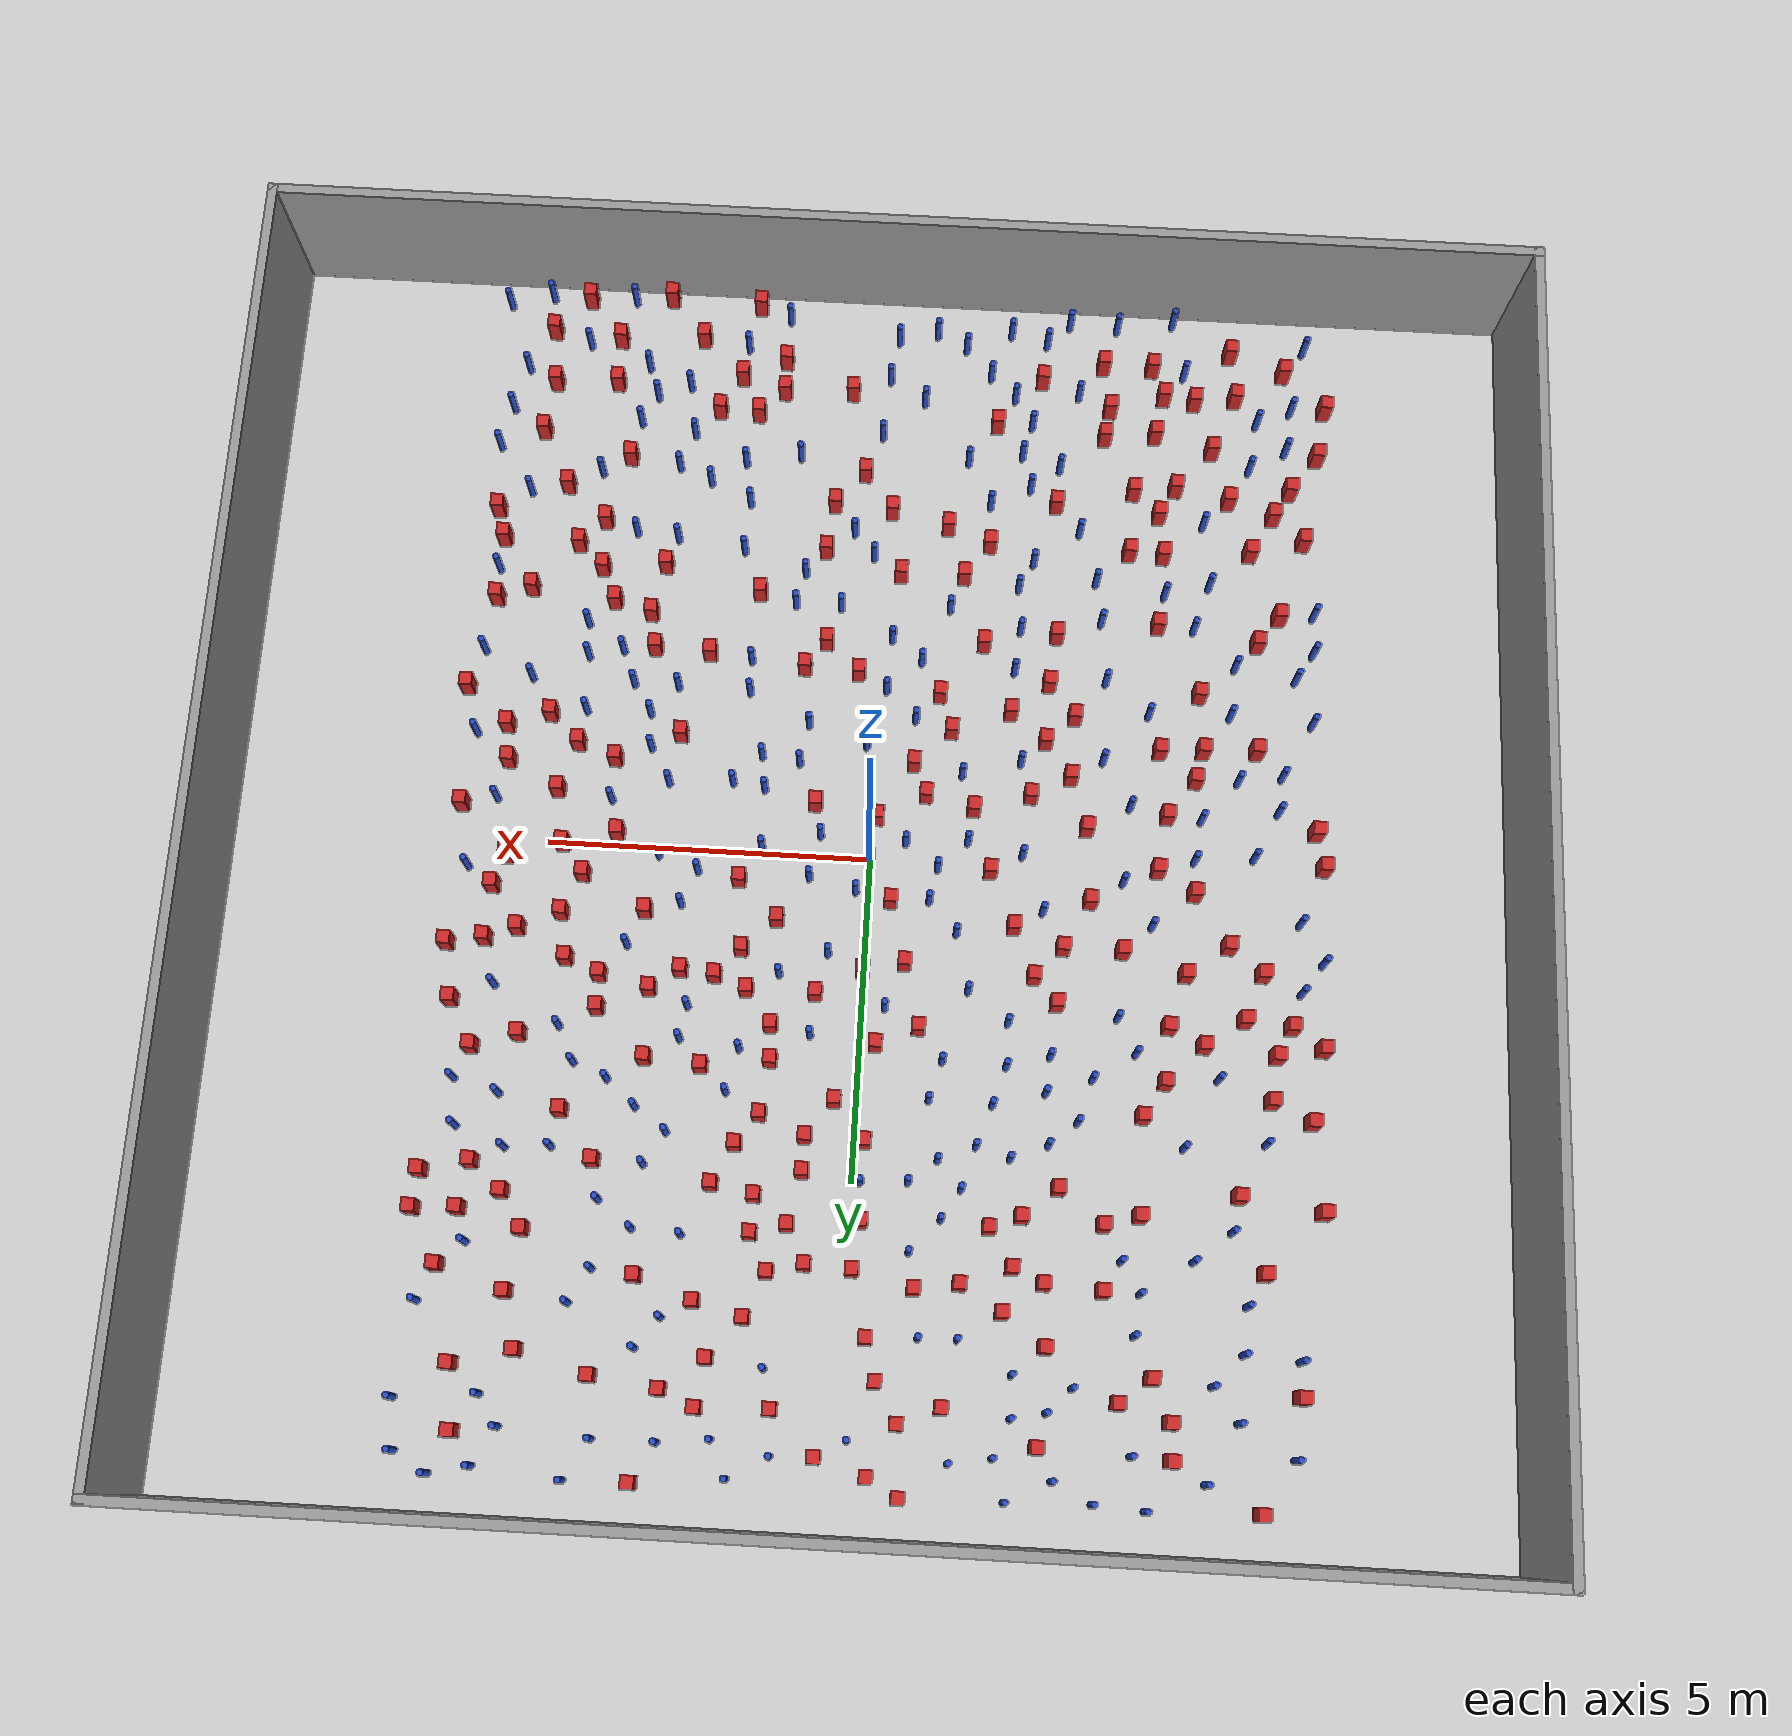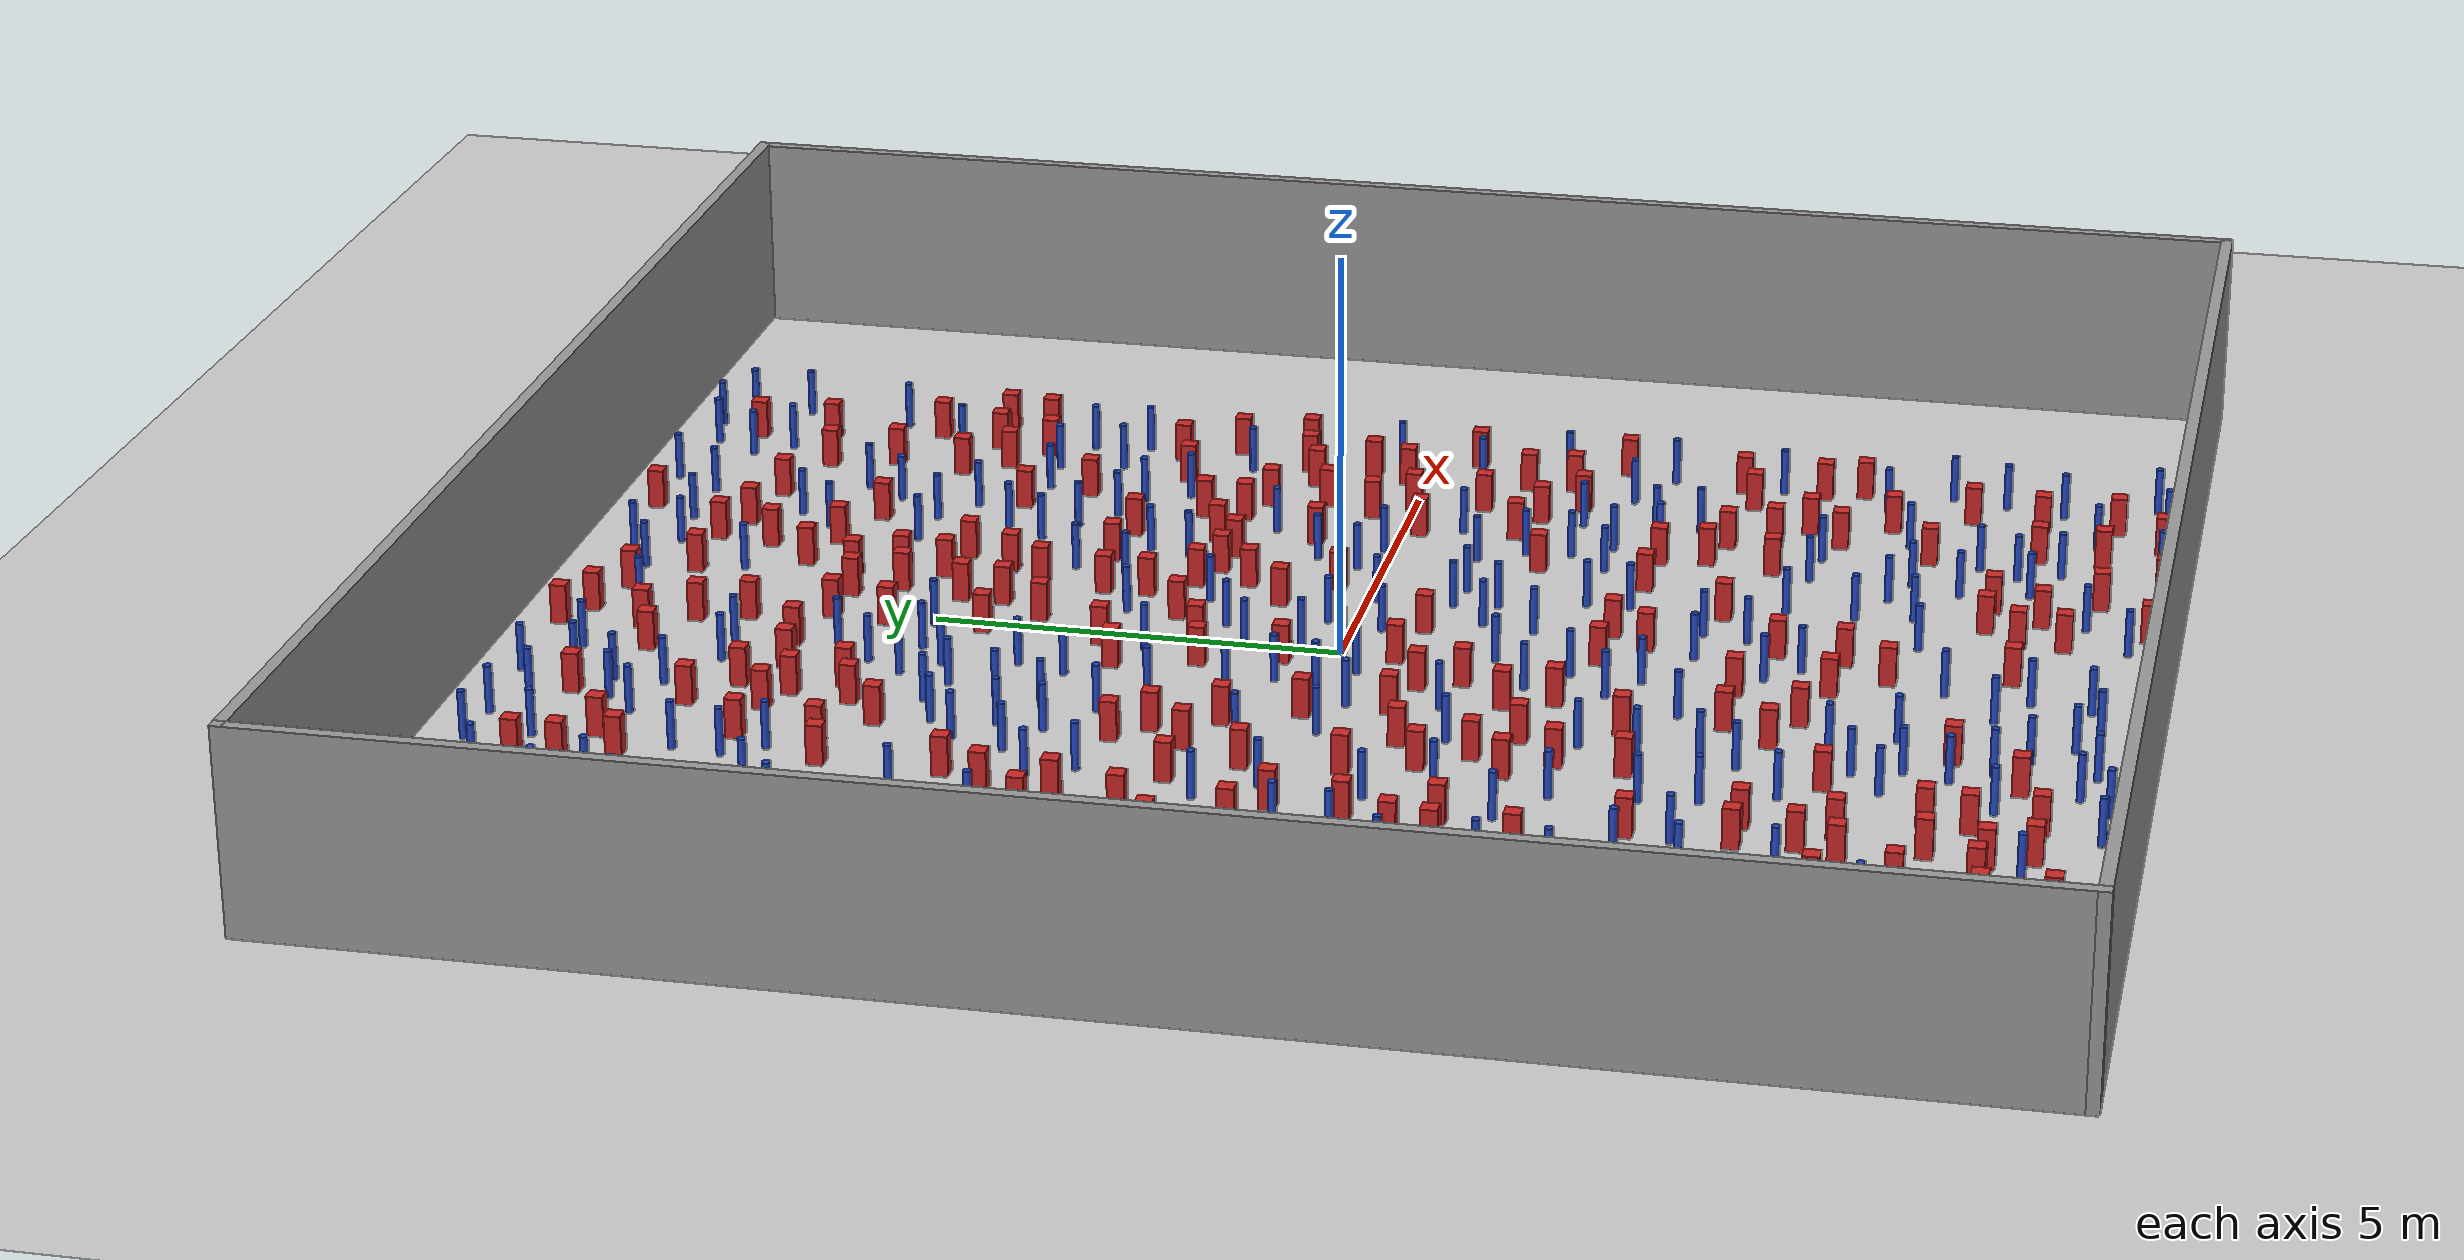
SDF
<sdf version="1.6">
 <world name="default">
  <light name="sun" type="directional">
   <pose>0 0 1000 0 -0 0</pose>
   <diffuse>0.8 0.8 0.8 1</diffuse>
   <specular>0.1 0.1 0.1 1</specular>
   <attenuation>
    <range>1000</range>
    <constant>0.9</constant>
    <linear>0.01</linear>
    <quadratic>0.001</quadratic>
   </attenuation>
   <direction>-0.5 0.5 -1</direction>
  </light>
  <model name="ground_plane">
   <static>1</static>
   <link name="link">
    <collision name="collision">
     <geometry><plane><normal>0 0 1</normal><size>100 100</size></plane></geometry>
     <surface><friction><ode><mu>100</mu><mu2>50</mu2></ode></friction></surface>
    </collision>
    <visual name="visual">
     <cast_shadows>0</cast_shadows>
     <geometry><plane><normal>0 0 1</normal><size>100 100</size></plane></geometry>
     <material>
      <ambient>1.0 1.0 1.0 1.0</ambient>
      <diffuse>0.8 0.8 0.8 1.0</diffuse>
      <specular>0.01 0.01 0.01 1.000000</specular>
     </material>
    </visual>
   </link>
  </model>
  <gravity>0 0 -9.8</gravity>
  <magnetic_field>6e-06 2.3e-05 -4.2e-05</magnetic_field>
  <atmosphere type="adiabatic"/>
  <physics name="default_physics" default="0" type="ode">
   <max_step_size>0.001</max_step_size>
   <real_time_factor>1</real_time_factor>
   <real_time_update_rate>1000</real_time_update_rate>
  </physics>
  <scene><ambient>0.4 0.4 0.4 1</ambient><background>0.7 0.7 0.7 1</background><shadows>1</shadows></scene>
  <spherical_coordinates>
   <surface_model>EARTH_WGS84</surface_model>
   <latitude_deg>0</latitude_deg>
   <longitude_deg>0</longitude_deg>
   <elevation>0</elevation>
   <heading_deg>0</heading_deg>
  </spherical_coordinates>
  <plugin name="gazebo_occupancy_map" filename="libgazebo_2Dmap_plugin.so">
   <map_resolution>0.05</map_resolution>
   <map_topic>generated_map</map_topic>
   <map_height>0.01</map_height>
   <map_size_x>50</map_size_x>
   <map_size_y>50</map_size_y>
  </plugin>
  <model name="NamedLocations">
   <static>true</static>
   <link name="DefaultStart"><pose>8.5 0 0 0 0 3.14</pose></link>
  </model>
  <model name="20x20_walls">
   <pose>0.044518 0.176112 0 0 -0 0</pose>
   <link name="Wall_1">
    <collision name="Wall_1_Collision">
     <geometry><box><size>20 0.15 2.5</size></box></geometry>
     <pose>0 0 1.25 0 -0 0</pose>
    </collision>
    <visual name="Wall_1_Visual">
     <pose>0 0 1.25 0 -0 0</pose>
     <geometry><box><size>20 0.15 2.5</size></box></geometry>
     <material>
      <script><uri>file://media/materials/scripts/gazebo.material</uri><name>Gazebo/Grey</name></script>
      <ambient>0.976471 0.992157 1 1</ambient>
     </material>
     <meta><layer>0</layer></meta>
    </visual>
    <pose>0 9.925 0 0 -0 0</pose>
   </link>
   <link name="Wall_3">
    <collision name="Wall_3_Collision">
     <geometry><box><size>20 0.15 2.5</size></box></geometry>
     <pose>0 0 1.25 0 -0 0</pose>
    </collision>
    <visual name="Wall_3_Visual">
     <pose>0 0 1.25 0 -0 0</pose>
     <geometry><box><size>20 0.15 2.5</size></box></geometry>
     <material>
      <script><uri>file://media/materials/scripts/gazebo.material</uri><name>Gazebo/Grey</name></script>
      <ambient>0.976471 0.992157 1 1</ambient>
     </material>
     <meta><layer>0</layer></meta>
    </visual>
    <pose>9.925 0 0 0 0 -1.5708</pose>
   </link>
   <link name="Wall_4">
    <collision name="Wall_4_Collision">
     <geometry><box><size>20 0.15 2.5</size></box></geometry>
     <pose>0 0 1.25 0 -0 0</pose>
    </collision>
    <visual name="Wall_4_Visual">
     <pose>0 0 1.25 0 -0 0</pose>
     <geometry><box><size>20 0.15 2.5</size></box></geometry>
     <material>
      <script><uri>file://media/materials/scripts/gazebo.material</uri><name>Gazebo/Grey</name></script>
      <ambient>0.976471 0.992157 1 1</ambient>
     </material>
     <meta><layer>0</layer></meta>
    </visual>
    <pose>0 -9.925 0 0 -0 3.14159</pose>
   </link>
   <link name="Wall_5">
    <collision name="Wall_5_Collision">
     <geometry><box><size>20 0.15 2.5</size></box></geometry>
     <pose>0 0 1.25 0 -0 0</pose>
    </collision>
    <visual name="Wall_5_Visual">
     <pose>0 0 1.25 0 -0 0</pose>
     <geometry><box><size>20 0.15 2.5</size></box></geometry>
     <material>
      <script><uri>file://media/materials/scripts/gazebo.material</uri><name>Gazebo/Grey</name></script>
      <ambient>0.976471 0.992157 1 1</ambient>
     </material>
     <meta><layer>0</layer></meta>
    </visual>
    <pose>-9.925 0 0 0 -0 1.5708</pose>
   </link>
   <static>1</static>
  </model>
  <model name="square_post_obstacle0">
   <static>true</static>
   <pose>1.99976582621 0.442310010033 -6.11067671241e-07 -5.50515727128e-06 -8.79689657224e-07 2.37013304536e-05</pose>
   <link name="link">
    <pose>0 0 0.25 0 -0 0</pose>
    <inertial>
     <mass>100</mass>
     <inertia>
      <ixx>0.166667</ixx>
      <ixy>0</ixy>
      <ixz>0</ixz>
      <iyy>0.166667</iyy>
      <iyz>0</iyz>
      <izz>0.166667</izz>
     </inertia>
    </inertial>
    <collision name="collision"><geometry><box><size>.2 .2 .5</size></box></geometry></collision>
    <visual name="visual">
     <geometry><box><size>.2 .2 .5</size></box></geometry>
     <material>
      <script><name>Gazebo/Red</name><uri>file://media/materials/scripts/gazebo.material</uri></script>
     </material>
    </visual>
   </link>
  </model>
  <model name="square_post_obstacle1">
   <static>true</static>
   <pose>0.990745557515 -5.11221250376 -6.11067671241e-07 -5.50515727128e-06 -8.79689657224e-07 2.37013304536e-05</pose>
   <link name="link">
    <pose>0 0 0.25 0 -0 0</pose>
    <inertial>
     <mass>100</mass>
     <inertia>
      <ixx>0.166667</ixx>
      <ixy>0</ixy>
      <ixz>0</ixz>
      <iyy>0.166667</iyy>
      <iyz>0</iyz>
      <izz>0.166667</izz>
     </inertia>
    </inertial>
    <collision name="collision"><geometry><box><size>.2 .2 .5</size></box></geometry></collision>
    <visual name="visual">
     <geometry><box><size>.2 .2 .5</size></box></geometry>
     <material>
      <script><name>Gazebo/Red</name><uri>file://media/materials/scripts/gazebo.material</uri></script>
     </material>
    </visual>
   </link>
  </model>
  <model name="pole_obstacle0">
   <static>true</static>
   <pose>0.11906316881 -8.21374808849 -9.47619616065e-06 5.49618799738e-07 2.3631041403e-07 -1.55090534819e-07</pose>
   <link name="link">
    <pose>0 0 0.3 0 -0 0</pose>
    <inertial>
     <mass>1</mass>
     <inertia><ixx>0.145833</ixx><ixy>0</ixy><ixz>0</ixz><iyy>0.145833</iyy><iyz>0</iyz><izz>0.125</izz></inertia>
    </inertial>
    <collision name="collision">
     <geometry><cylinder><radius>0.05</radius><length>.6</length></cylinder></geometry>
    </collision>
    <visual name="visual">
     <geometry><cylinder><radius>0.05</radius><length>.6</length></cylinder></geometry>
     <material>
      <script><name>Gazebo/Blue</name><uri>file://media/materials/scripts/gazebo.material</uri></script>
     </material>
    </visual>
   </link>
  </model>
  <model name="square_post_obstacle2">
   <static>true</static>
   <pose>-3.06288043602 4.92188417001 -6.11067671241e-07 -5.50515727128e-06 -8.79689657224e-07 2.37013304536e-05</pose>
   <link name="link">
    <pose>0 0 0.25 0 -0 0</pose>
    <inertial>
     <mass>100</mass>
     <inertia>
      <ixx>0.166667</ixx>
      <ixy>0</ixy>
      <ixz>0</ixz>
      <iyy>0.166667</iyy>
      <iyz>0</iyz>
      <izz>0.166667</izz>
     </inertia>
    </inertial>
    <collision name="collision"><geometry><box><size>.2 .2 .5</size></box></geometry></collision>
    <visual name="visual">
     <geometry><box><size>.2 .2 .5</size></box></geometry>
     <material>
      <script><name>Gazebo/Red</name><uri>file://media/materials/scripts/gazebo.material</uri></script>
     </material>
    </visual>
   </link>
  </model>
  <model name="pole_obstacle1">
   <static>true</static>
   <pose>5.22117834623 9.35934208849 -9.47619616065e-06 5.49618799737e-07 2.36310414065e-07 -1.55090534796e-07</pose>
   <link name="link">
    <pose>0 0 0.3 0 -0 0</pose>
    <inertial>
     <mass>1</mass>
     <inertia><ixx>0.145833</ixx><ixy>0</ixy><ixz>0</ixz><iyy>0.145833</iyy><iyz>0</iyz><izz>0.125</izz></inertia>
    </inertial>
    <collision name="collision">
     <geometry><cylinder><radius>0.05</radius><length>.6</length></cylinder></geometry>
    </collision>
    <visual name="visual">
     <geometry><cylinder><radius>0.05</radius><length>.6</length></cylinder></geometry>
     <material>
      <script><name>Gazebo/Blue</name><uri>file://media/materials/scripts/gazebo.material</uri></script>
     </material>
    </visual>
   </link>
  </model>
  <model name="square_post_obstacle3">
   <static>true</static>
   <pose>-6.42343471984 -6.54299542889 -6.11067671241e-07 -5.50515727128e-06 -8.79689657224e-07 2.37013304536e-05</pose>
   <link name="link">
    <pose>0 0 0.25 0 -0 0</pose>
    <inertial>
     <mass>100</mass>
     <inertia>
      <ixx>0.166667</ixx>
      <ixy>0</ixy>
      <ixz>0</ixz>
      <iyy>0.166667</iyy>
      <iyz>0</iyz>
      <izz>0.166667</izz>
     </inertia>
    </inertial>
    <collision name="collision"><geometry><box><size>.2 .2 .5</size></box></geometry></collision>
    <visual name="visual">
     <geometry><box><size>.2 .2 .5</size></box></geometry>
     <material>
      <script><name>Gazebo/Red</name><uri>file://media/materials/scripts/gazebo.material</uri></script>
     </material>
    </visual>
   </link>
  </model>
  <model name="pole_obstacle2">
   <static>true</static>
   <pose>-2.99270602096 8.16351334637 -9.4761961606e-06 5.49618799729e-07 2.36310414e-07 -1.55090534824e-07</pose>
   <link name="link">
    <pose>0 0 0.3 0 -0 0</pose>
    <inertial>
     <mass>1</mass>
     <inertia><ixx>0.145833</ixx><ixy>0</ixy><ixz>0</ixz><iyy>0.145833</iyy><iyz>0</iyz><izz>0.125</izz></inertia>
    </inertial>
    <collision name="collision">
     <geometry><cylinder><radius>0.05</radius><length>.6</length></cylinder></geometry>
    </collision>
    <visual name="visual">
     <geometry><cylinder><radius>0.05</radius><length>.6</length></cylinder></geometry>
     <material>
      <script><name>Gazebo/Blue</name><uri>file://media/materials/scripts/gazebo.material</uri></script>
     </material>
    </visual>
   </link>
  </model>
  <model name="pole_obstacle3">
   <static>true</static>
   <pose>3.58272405609 -2.19162228922 -9.47619616065e-06 5.49618799737e-07 2.36310414051e-07 -1.55090534807e-07</pose>
   <link name="link">
    <pose>0 0 0.3 0 -0 0</pose>
    <inertial>
     <mass>1</mass>
     <inertia><ixx>0.145833</ixx><ixy>0</ixy><ixz>0</ixz><iyy>0.145833</iyy><iyz>0</iyz><izz>0.125</izz></inertia>
    </inertial>
    <collision name="collision">
     <geometry><cylinder><radius>0.05</radius><length>.6</length></cylinder></geometry>
    </collision>
    <visual name="visual">
     <geometry><cylinder><radius>0.05</radius><length>.6</length></cylinder></geometry>
     <material>
      <script><name>Gazebo/Blue</name><uri>file://media/materials/scripts/gazebo.material</uri></script>
     </material>
    </visual>
   </link>
  </model>
  <model name="square_post_obstacle4">
   <static>true</static>
   <pose>4.68333809107 1.11460655222 -6.11067671241e-07 -5.50515727128e-06 -8.79689657224e-07 2.37013304536e-05</pose>
   <link name="link">
    <pose>0 0 0.25 0 -0 0</pose>
    <inertial>
     <mass>100</mass>
     <inertia>
      <ixx>0.166667</ixx>
      <ixy>0</ixy>
      <ixz>0</ixz>
      <iyy>0.166667</iyy>
      <iyz>0</iyz>
      <izz>0.166667</izz>
     </inertia>
    </inertial>
    <collision name="collision"><geometry><box><size>.2 .2 .5</size></box></geometry></collision>
    <visual name="visual">
     <geometry><box><size>.2 .2 .5</size></box></geometry>
     <material>
      <script><name>Gazebo/Red</name><uri>file://media/materials/scripts/gazebo.material</uri></script>
     </material>
    </visual>
   </link>
  </model>
  <model name="square_post_obstacle5">
   <static>true</static>
   <pose>1.43845758457 4.05766834476 -6.11067671241e-07 -5.50515727128e-06 -8.79689657224e-07 2.37013304536e-05</pose>
   <link name="link">
    <pose>0 0 0.25 0 -0 0</pose>
    <inertial>
     <mass>100</mass>
     <inertia>
      <ixx>0.166667</ixx>
      <ixy>0</ixy>
      <ixz>0</ixz>
      <iyy>0.166667</iyy>
      <iyz>0</iyz>
      <izz>0.166667</izz>
     </inertia>
    </inertial>
    <collision name="collision"><geometry><box><size>.2 .2 .5</size></box></geometry></collision>
    <visual name="visual">
     <geometry><box><size>.2 .2 .5</size></box></geometry>
     <material>
      <script><name>Gazebo/Red</name><uri>file://media/materials/scripts/gazebo.material</uri></script>
     </material>
    </visual>
   </link>
  </model>
  <model name="square_post_obstacle6">
   <static>true</static>
   <pose>-4.61223961222 3.24359524675 -6.11067671241e-07 -5.50515727128e-06 -8.79689657224e-07 2.37013304536e-05</pose>
   <link name="link">
    <pose>0 0 0.25 0 -0 0</pose>
    <inertial>
     <mass>100</mass>
     <inertia>
      <ixx>0.166667</ixx>
      <ixy>0</ixy>
      <ixz>0</ixz>
      <iyy>0.166667</iyy>
      <iyz>0</iyz>
      <izz>0.166667</izz>
     </inertia>
    </inertial>
    <collision name="collision"><geometry><box><size>.2 .2 .5</size></box></geometry></collision>
    <visual name="visual">
     <geometry><box><size>.2 .2 .5</size></box></geometry>
     <material>
      <script><name>Gazebo/Red</name><uri>file://media/materials/scripts/gazebo.material</uri></script>
     </material>
    </visual>
   </link>
  </model>
  <model name="pole_obstacle4">
   <static>true</static>
   <pose>5.8278807453 -5.88849563057 -9.47619616065e-06 5.49618799737e-07 2.36310414037e-07 -1.55090534814e-07</pose>
   <link name="link">
    <pose>0 0 0.3 0 -0 0</pose>
    <inertial>
     <mass>1</mass>
     <inertia><ixx>0.145833</ixx><ixy>0</ixy><ixz>0</ixz><iyy>0.145833</iyy><iyz>0</iyz><izz>0.125</izz></inertia>
    </inertial>
    <collision name="collision">
     <geometry><cylinder><radius>0.05</radius><length>.6</length></cylinder></geometry>
    </collision>
    <visual name="visual">
     <geometry><cylinder><radius>0.05</radius><length>.6</length></cylinder></geometry>
     <material>
      <script><name>Gazebo/Blue</name><uri>file://media/materials/scripts/gazebo.material</uri></script>
     </material>
    </visual>
   </link>
  </model>
  <model name="pole_obstacle5">
   <static>true</static>
   <pose>-6.98525939992 1.29050954882 -9.47619616065e-06 5.49618799738e-07 2.36310414071e-07 -1.55090534796e-07</pose>
   <link name="link">
    <pose>0 0 0.3 0 -0 0</pose>
    <inertial>
     <mass>1</mass>
     <inertia><ixx>0.145833</ixx><ixy>0</ixy><ixz>0</ixz><iyy>0.145833</iyy><iyz>0</iyz><izz>0.125</izz></inertia>
    </inertial>
    <collision name="collision">
     <geometry><cylinder><radius>0.05</radius><length>.6</length></cylinder></geometry>
    </collision>
    <visual name="visual">
     <geometry><cylinder><radius>0.05</radius><length>.6</length></cylinder></geometry>
     <material>
      <script><name>Gazebo/Blue</name><uri>file://media/materials/scripts/gazebo.material</uri></script>
     </material>
    </visual>
   </link>
  </model>
  <model name="square_post_obstacle7">
   <static>true</static>
   <pose>-5.79598033326 -5.42429166378 -6.11067671241e-07 -5.50515727128e-06 -8.79689657224e-07 2.37013304536e-05</pose>
   <link name="link">
    <pose>0 0 0.25 0 -0 0</pose>
    <inertial>
     <mass>100</mass>
     <inertia>
      <ixx>0.166667</ixx>
      <ixy>0</ixy>
      <ixz>0</ixz>
      <iyy>0.166667</iyy>
      <iyz>0</iyz>
      <izz>0.166667</izz>
     </inertia>
    </inertial>
    <collision name="collision"><geometry><box><size>.2 .2 .5</size></box></geometry></collision>
    <visual name="visual">
     <geometry><box><size>.2 .2 .5</size></box></geometry>
     <material>
      <script><name>Gazebo/Red</name><uri>file://media/materials/scripts/gazebo.material</uri></script>
     </material>
    </visual>
   </link>
  </model>
  <model name="square_post_obstacle8">
   <static>true</static>
   <pose>-4.433717044 -0.0601203227381 -6.11067671241e-07 -5.50515727128e-06 -8.79689657224e-07 2.37013304536e-05</pose>
   <link name="link">
    <pose>0 0 0.25 0 -0 0</pose>
    <inertial>
     <mass>100</mass>
     <inertia>
      <ixx>0.166667</ixx>
      <ixy>0</ixy>
      <ixz>0</ixz>
      <iyy>0.166667</iyy>
      <iyz>0</iyz>
      <izz>0.166667</izz>
     </inertia>
    </inertial>
    <collision name="collision"><geometry><box><size>.2 .2 .5</size></box></geometry></collision>
    <visual name="visual">
     <geometry><box><size>.2 .2 .5</size></box></geometry>
     <material>
      <script><name>Gazebo/Red</name><uri>file://media/materials/scripts/gazebo.material</uri></script>
     </material>
    </visual>
   </link>
  </model>
  <model name="pole_obstacle6">
   <static>true</static>
   <pose>4.59149566089 -2.1830002318 -9.47619616065e-06 5.49618799738e-07 2.36310414051e-07 -1.55090534805e-07</pose>
   <link name="link">
    <pose>0 0 0.3 0 -0 0</pose>
    <inertial>
     <mass>1</mass>
     <inertia><ixx>0.145833</ixx><ixy>0</ixy><ixz>0</ixz><iyy>0.145833</iyy><iyz>0</iyz><izz>0.125</izz></inertia>
    </inertial>
    <collision name="collision">
     <geometry><cylinder><radius>0.05</radius><length>.6</length></cylinder></geometry>
    </collision>
    <visual name="visual">
     <geometry><cylinder><radius>0.05</radius><length>.6</length></cylinder></geometry>
     <material>
      <script><name>Gazebo/Blue</name><uri>file://media/materials/scripts/gazebo.material</uri></script>
     </material>
    </visual>
   </link>
  </model>
  <model name="pole_obstacle7">
   <static>true</static>
   <pose>2.48516337789 -8.6628891993 -9.4761961606e-06 5.49618799729e-07 2.36310414e-07 -1.55090534824e-07</pose>
   <link name="link">
    <pose>0 0 0.3 0 -0 0</pose>
    <inertial>
     <mass>1</mass>
     <inertia><ixx>0.145833</ixx><ixy>0</ixy><ixz>0</ixz><iyy>0.145833</iyy><iyz>0</iyz><izz>0.125</izz></inertia>
    </inertial>
    <collision name="collision">
     <geometry><cylinder><radius>0.05</radius><length>.6</length></cylinder></geometry>
    </collision>
    <visual name="visual">
     <geometry><cylinder><radius>0.05</radius><length>.6</length></cylinder></geometry>
     <material>
      <script><name>Gazebo/Blue</name><uri>file://media/materials/scripts/gazebo.material</uri></script>
     </material>
    </visual>
   </link>
  </model>
  <model name="square_post_obstacle9">
   <static>true</static>
   <pose>5.16042200609 -9.40029014355 -6.11067671241e-07 -5.50515727128e-06 -8.79689657224e-07 2.37013304536e-05</pose>
   <link name="link">
    <pose>0 0 0.25 0 -0 0</pose>
    <inertial>
     <mass>100</mass>
     <inertia>
      <ixx>0.166667</ixx>
      <ixy>0</ixy>
      <ixz>0</ixz>
      <iyy>0.166667</iyy>
      <iyz>0</iyz>
      <izz>0.166667</izz>
     </inertia>
    </inertial>
    <collision name="collision"><geometry><box><size>.2 .2 .5</size></box></geometry></collision>
    <visual name="visual">
     <geometry><box><size>.2 .2 .5</size></box></geometry>
     <material>
      <script><name>Gazebo/Red</name><uri>file://media/materials/scripts/gazebo.material</uri></script>
     </material>
    </visual>
   </link>
  </model>
  <model name="square_post_obstacle10">
   <static>true</static>
   <pose>5.81792439504 1.58387289874 -6.11067671241e-07 -5.50515727128e-06 -8.79689657224e-07 2.37013304536e-05</pose>
   <link name="link">
    <pose>0 0 0.25 0 -0 0</pose>
    <inertial>
     <mass>100</mass>
     <inertia>
      <ixx>0.166667</ixx>
      <ixy>0</ixy>
      <ixz>0</ixz>
      <iyy>0.166667</iyy>
      <iyz>0</iyz>
      <izz>0.166667</izz>
     </inertia>
    </inertial>
    <collision name="collision"><geometry><box><size>.2 .2 .5</size></box></geometry></collision>
    <visual name="visual">
     <geometry><box><size>.2 .2 .5</size></box></geometry>
     <material>
      <script><name>Gazebo/Red</name><uri>file://media/materials/scripts/gazebo.material</uri></script>
     </material>
    </visual>
   </link>
  </model>
  <model name="square_post_obstacle11">
   <static>true</static>
   <pose>-0.168342185262 5.56822024255 -6.11067671241e-07 -5.50515727128e-06 -8.79689657224e-07 2.37013304536e-05</pose>
   <link name="link">
    <pose>0 0 0.25 0 -0 0</pose>
    <inertial>
     <mass>100</mass>
     <inertia>
      <ixx>0.166667</ixx>
      <ixy>0</ixy>
      <ixz>0</ixz>
      <iyy>0.166667</iyy>
      <iyz>0</iyz>
      <izz>0.166667</izz>
     </inertia>
    </inertial>
    <collision name="collision"><geometry><box><size>.2 .2 .5</size></box></geometry></collision>
    <visual name="visual">
     <geometry><box><size>.2 .2 .5</size></box></geometry>
     <material>
      <script><name>Gazebo/Red</name><uri>file://media/materials/scripts/gazebo.material</uri></script>
     </material>
    </visual>
   </link>
  </model>
  <model name="square_post_obstacle12">
   <static>true</static>
   <pose>-3.31759820821 -0.67170505714 -6.11067671241e-07 -5.50515727128e-06 -8.79689657224e-07 2.37013304536e-05</pose>
   <link name="link">
    <pose>0 0 0.25 0 -0 0</pose>
    <inertial>
     <mass>100</mass>
     <inertia>
      <ixx>0.166667</ixx>
      <ixy>0</ixy>
      <ixz>0</ixz>
      <iyy>0.166667</iyy>
      <iyz>0</iyz>
      <izz>0.166667</izz>
     </inertia>
    </inertial>
    <collision name="collision"><geometry><box><size>.2 .2 .5</size></box></geometry></collision>
    <visual name="visual">
     <geometry><box><size>.2 .2 .5</size></box></geometry>
     <material>
      <script><name>Gazebo/Red</name><uri>file://media/materials/scripts/gazebo.material</uri></script>
     </material>
    </visual>
   </link>
  </model>
  <model name="square_post_obstacle13">
   <static>true</static>
   <pose>-6.06268483474 1.50484935282 -6.11067671241e-07 -5.50515727128e-06 -8.79689657224e-07 2.37013304536e-05</pose>
   <link name="link">
    <pose>0 0 0.25 0 -0 0</pose>
    <inertial>
     <mass>100</mass>
     <inertia>
      <ixx>0.166667</ixx>
      <ixy>0</ixy>
      <ixz>0</ixz>
      <iyy>0.166667</iyy>
      <iyz>0</iyz>
      <izz>0.166667</izz>
     </inertia>
    </inertial>
    <collision name="collision"><geometry><box><size>.2 .2 .5</size></box></geometry></collision>
    <visual name="visual">
     <geometry><box><size>.2 .2 .5</size></box></geometry>
     <material>
      <script><name>Gazebo/Red</name><uri>file://media/materials/scripts/gazebo.material</uri></script>
     </material>
    </visual>
   </link>
  </model>
  <model name="pole_obstacle8">
   <static>true</static>
   <pose>-6.81686627947 -3.75061446823 -9.47619616065e-06 5.49618799738e-07 2.36310414051e-07 -1.55090534805e-07</pose>
   <link name="link">
    <pose>0 0 0.3 0 -0 0</pose>
    <inertial>
     <mass>1</mass>
     <inertia><ixx>0.145833</ixx><ixy>0</ixy><ixz>0</ixz><iyy>0.145833</iyy><iyz>0</iyz><izz>0.125</izz></inertia>
    </inertial>
    <collision name="collision">
     <geometry><cylinder><radius>0.05</radius><length>.6</length></cylinder></geometry>
    </collision>
    <visual name="visual">
     <geometry><cylinder><radius>0.05</radius><length>.6</length></cylinder></geometry>
     <material>
      <script><name>Gazebo/Blue</name><uri>file://media/materials/scripts/gazebo.material</uri></script>
     </material>
    </visual>
   </link>
  </model>
  <model name="square_post_obstacle14">
   <static>true</static>
   <pose>6.18782036938 -4.00822140746 -6.11067671241e-07 -5.50515727128e-06 -8.79689657224e-07 2.37013304536e-05</pose>
   <link name="link">
    <pose>0 0 0.25 0 -0 0</pose>
    <inertial>
     <mass>100</mass>
     <inertia>
      <ixx>0.166667</ixx>
      <ixy>0</ixy>
      <ixz>0</ixz>
      <iyy>0.166667</iyy>
      <iyz>0</iyz>
      <izz>0.166667</izz>
     </inertia>
    </inertial>
    <collision name="collision"><geometry><box><size>.2 .2 .5</size></box></geometry></collision>
    <visual name="visual">
     <geometry><box><size>.2 .2 .5</size></box></geometry>
     <material>
      <script><name>Gazebo/Red</name><uri>file://media/materials/scripts/gazebo.material</uri></script>
     </material>
    </visual>
   </link>
  </model>
  <model name="square_post_obstacle15">
   <static>true</static>
   <pose>5.71017640182 -6.97548128937 -6.11067671241e-07 -5.50515727128e-06 -8.79689657224e-07 2.37013304536e-05</pose>
   <link name="link">
    <pose>0 0 0.25 0 -0 0</pose>
    <inertial>
     <mass>100</mass>
     <inertia>
      <ixx>0.166667</ixx>
      <ixy>0</ixy>
      <ixz>0</ixz>
      <iyy>0.166667</iyy>
      <iyz>0</iyz>
      <izz>0.166667</izz>
     </inertia>
    </inertial>
    <collision name="collision"><geometry><box><size>.2 .2 .5</size></box></geometry></collision>
    <visual name="visual">
     <geometry><box><size>.2 .2 .5</size></box></geometry>
     <material>
      <script><name>Gazebo/Red</name><uri>file://media/materials/scripts/gazebo.material</uri></script>
     </material>
    </visual>
   </link>
  </model>
  <model name="square_post_obstacle16">
   <static>true</static>
   <pose>5.15076023287 3.03704496694 -6.11067671241e-07 -5.50515727128e-06 -8.79689657224e-07 2.37013304536e-05</pose>
   <link name="link">
    <pose>0 0 0.25 0 -0 0</pose>
    <inertial>
     <mass>100</mass>
     <inertia>
      <ixx>0.166667</ixx>
      <ixy>0</ixy>
      <ixz>0</ixz>
      <iyy>0.166667</iyy>
      <iyz>0</iyz>
      <izz>0.166667</izz>
     </inertia>
    </inertial>
    <collision name="collision"><geometry><box><size>.2 .2 .5</size></box></geometry></collision>
    <visual name="visual">
     <geometry><box><size>.2 .2 .5</size></box></geometry>
     <material>
      <script><name>Gazebo/Red</name><uri>file://media/materials/scripts/gazebo.material</uri></script>
     </material>
    </visual>
   </link>
  </model>
  <model name="pole_obstacle9">
   <static>true</static>
   <pose>4.07267543703 -0.739096492723 -9.47619616065e-06 5.49618799737e-07 2.36310414061e-07 -1.550905348e-07</pose>
   <link name="link">
    <pose>0 0 0.3 0 -0 0</pose>
    <inertial>
     <mass>1</mass>
     <inertia><ixx>0.145833</ixx><ixy>0</ixy><ixz>0</ixz><iyy>0.145833</iyy><iyz>0</iyz><izz>0.125</izz></inertia>
    </inertial>
    <collision name="collision">
     <geometry><cylinder><radius>0.05</radius><length>.6</length></cylinder></geometry>
    </collision>
    <visual name="visual">
     <geometry><cylinder><radius>0.05</radius><length>.6</length></cylinder></geometry>
     <material>
      <script><name>Gazebo/Blue</name><uri>file://media/materials/scripts/gazebo.material</uri></script>
     </material>
    </visual>
   </link>
  </model>
  <model name="square_post_obstacle17">
   <static>true</static>
   <pose>-6.2163403999 3.44901654102 -6.11067671241e-07 -5.50515727128e-06 -8.79689657224e-07 2.37013304536e-05</pose>
   <link name="link">
    <pose>0 0 0.25 0 -0 0</pose>
    <inertial>
     <mass>100</mass>
     <inertia>
      <ixx>0.166667</ixx>
      <ixy>0</ixy>
      <ixz>0</ixz>
      <iyy>0.166667</iyy>
      <iyz>0</iyz>
      <izz>0.166667</izz>
     </inertia>
    </inertial>
    <collision name="collision"><geometry><box><size>.2 .2 .5</size></box></geometry></collision>
    <visual name="visual">
     <geometry><box><size>.2 .2 .5</size></box></geometry>
     <material>
      <script><name>Gazebo/Red</name><uri>file://media/materials/scripts/gazebo.material</uri></script>
     </material>
    </visual>
   </link>
  </model>
  <model name="square_post_obstacle18">
   <static>true</static>
   <pose>2.23808886321 -7.47004831149 -6.11067671241e-07 -5.50515727128e-06 -8.79689657224e-07 2.37013304536e-05</pose>
   <link name="link">
    <pose>0 0 0.25 0 -0 0</pose>
    <inertial>
     <mass>100</mass>
     <inertia>
      <ixx>0.166667</ixx>
      <ixy>0</ixy>
      <ixz>0</ixz>
      <iyy>0.166667</iyy>
      <iyz>0</iyz>
      <izz>0.166667</izz>
     </inertia>
    </inertial>
    <collision name="collision"><geometry><box><size>.2 .2 .5</size></box></geometry></collision>
    <visual name="visual">
     <geometry><box><size>.2 .2 .5</size></box></geometry>
     <material>
      <script><name>Gazebo/Red</name><uri>file://media/materials/scripts/gazebo.material</uri></script>
     </material>
    </visual>
   </link>
  </model>
  <model name="pole_obstacle10">
   <static>true</static>
   <pose>-3.90631873218 0.167929496606 -9.47619616065e-06 5.49618799737e-07 2.36310414028e-07 -1.55090534821e-07</pose>
   <link name="link">
    <pose>0 0 0.3 0 -0 0</pose>
    <inertial>
     <mass>1</mass>
     <inertia><ixx>0.145833</ixx><ixy>0</ixy><ixz>0</ixz><iyy>0.145833</iyy><iyz>0</iyz><izz>0.125</izz></inertia>
    </inertial>
    <collision name="collision">
     <geometry><cylinder><radius>0.05</radius><length>.6</length></cylinder></geometry>
    </collision>
    <visual name="visual">
     <geometry><cylinder><radius>0.05</radius><length>.6</length></cylinder></geometry>
     <material>
      <script><name>Gazebo/Blue</name><uri>file://media/materials/scripts/gazebo.material</uri></script>
     </material>
    </visual>
   </link>
  </model>
  <model name="square_post_obstacle19">
   <static>true</static>
   <pose>-4.81161712822 8.73059657655 -6.11067671241e-07 -5.50515727128e-06 -8.79689657224e-07 2.37013304536e-05</pose>
   <link name="link">
    <pose>0 0 0.25 0 -0 0</pose>
    <inertial>
     <mass>100</mass>
     <inertia>
      <ixx>0.166667</ixx>
      <ixy>0</ixy>
      <ixz>0</ixz>
      <iyy>0.166667</iyy>
      <iyz>0</iyz>
      <izz>0.166667</izz>
     </inertia>
    </inertial>
    <collision name="collision"><geometry><box><size>.2 .2 .5</size></box></geometry></collision>
    <visual name="visual">
     <geometry><box><size>.2 .2 .5</size></box></geometry>
     <material>
      <script><name>Gazebo/Red</name><uri>file://media/materials/scripts/gazebo.material</uri></script>
     </material>
    </visual>
   </link>
  </model>
  <model name="pole_obstacle11">
   <static>true</static>
   <pose>-5.91703608631 -0.323611237796 -9.47619616065e-06 5.49618799737e-07 2.36310414057e-07 -1.55090534802e-07</pose>
   <link name="link">
    <pose>0 0 0.3 0 -0 0</pose>
    <inertial>
     <mass>1</mass>
     <inertia><ixx>0.145833</ixx><ixy>0</ixy><ixz>0</ixz><iyy>0.145833</iyy><iyz>0</iyz><izz>0.125</izz></inertia>
    </inertial>
    <collision name="collision">
     <geometry><cylinder><radius>0.05</radius><length>.6</length></cylinder></geometry>
    </collision>
    <visual name="visual">
     <geometry><cylinder><radius>0.05</radius><length>.6</length></cylinder></geometry>
     <material>
      <script><name>Gazebo/Blue</name><uri>file://media/materials/scripts/gazebo.material</uri></script>
     </material>
    </visual>
   </link>
  </model>
  <model name="square_post_obstacle20">
   <static>true</static>
   <pose>-2.58422604013 1.72574476141 -6.11067671241e-07 -5.50515727128e-06 -8.79689657224e-07 2.37013304536e-05</pose>
   <link name="link">
    <pose>0 0 0.25 0 -0 0</pose>
    <inertial>
     <mass>100</mass>
     <inertia>
      <ixx>0.166667</ixx>
      <ixy>0</ixy>
      <ixz>0</ixz>
      <iyy>0.166667</iyy>
      <iyz>0</iyz>
      <izz>0.166667</izz>
     </inertia>
    </inertial>
    <collision name="collision"><geometry><box><size>.2 .2 .5</size></box></geometry></collision>
    <visual name="visual">
     <geometry><box><size>.2 .2 .5</size></box></geometry>
     <material>
      <script><name>Gazebo/Red</name><uri>file://media/materials/scripts/gazebo.material</uri></script>
     </material>
    </visual>
   </link>
  </model>
  <model name="pole_obstacle12">
   <static>true</static>
   <pose>-2.88061672198 2.94017404316 -9.47619616065e-06 5.49618799737e-07 2.36310414051e-07 -1.55090534807e-07</pose>
   <link name="link">
    <pose>0 0 0.3 0 -0 0</pose>
    <inertial>
     <mass>1</mass>
     <inertia><ixx>0.145833</ixx><ixy>0</ixy><ixz>0</ixz><iyy>0.145833</iyy><iyz>0</iyz><izz>0.125</izz></inertia>
    </inertial>
    <collision name="collision">
     <geometry><cylinder><radius>0.05</radius><length>.6</length></cylinder></geometry>
    </collision>
    <visual name="visual">
     <geometry><cylinder><radius>0.05</radius><length>.6</length></cylinder></geometry>
     <material>
      <script><name>Gazebo/Blue</name><uri>file://media/materials/scripts/gazebo.material</uri></script>
     </material>
    </visual>
   </link>
  </model>
  <model name="square_post_obstacle21">
   <static>true</static>
   <pose>-4.49922647604 7.5933039331 -6.11067671241e-07 -5.50515727128e-06 -8.79689657224e-07 2.37013304536e-05</pose>
   <link name="link">
    <pose>0 0 0.25 0 -0 0</pose>
    <inertial>
     <mass>100</mass>
     <inertia>
      <ixx>0.166667</ixx>
      <ixy>0</ixy>
      <ixz>0</ixz>
      <iyy>0.166667</iyy>
      <iyz>0</iyz>
      <izz>0.166667</izz>
     </inertia>
    </inertial>
    <collision name="collision"><geometry><box><size>.2 .2 .5</size></box></geometry></collision>
    <visual name="visual">
     <geometry><box><size>.2 .2 .5</size></box></geometry>
     <material>
      <script><name>Gazebo/Red</name><uri>file://media/materials/scripts/gazebo.material</uri></script>
     </material>
    </visual>
   </link>
  </model>
  <model name="pole_obstacle13">
   <static>true</static>
   <pose>-3.87450248075 2.30627080145 -9.47619616065e-06 5.49618799737e-07 2.36310414051e-07 -1.55090534807e-07</pose>
   <link name="link">
    <pose>0 0 0.3 0 -0 0</pose>
    <inertial>
     <mass>1</mass>
     <inertia><ixx>0.145833</ixx><ixy>0</ixy><ixz>0</ixz><iyy>0.145833</iyy><iyz>0</iyz><izz>0.125</izz></inertia>
    </inertial>
    <collision name="collision">
     <geometry><cylinder><radius>0.05</radius><length>.6</length></cylinder></geometry>
    </collision>
    <visual name="visual">
     <geometry><cylinder><radius>0.05</radius><length>.6</length></cylinder></geometry>
     <material>
      <script><name>Gazebo/Blue</name><uri>file://media/materials/scripts/gazebo.material</uri></script>
     </material>
    </visual>
   </link>
  </model>
  <model name="square_post_obstacle22">
   <static>true</static>
   <pose>3.64120823474 8.00132083375 -6.11067671241e-07 -5.50515727128e-06 -8.79689657224e-07 2.37013304536e-05</pose>
   <link name="link">
    <pose>0 0 0.25 0 -0 0</pose>
    <inertial>
     <mass>100</mass>
     <inertia>
      <ixx>0.166667</ixx>
      <ixy>0</ixy>
      <ixz>0</ixz>
      <iyy>0.166667</iyy>
      <iyz>0</iyz>
      <izz>0.166667</izz>
     </inertia>
    </inertial>
    <collision name="collision"><geometry><box><size>.2 .2 .5</size></box></geometry></collision>
    <visual name="visual">
     <geometry><box><size>.2 .2 .5</size></box></geometry>
     <material>
      <script><name>Gazebo/Red</name><uri>file://media/materials/scripts/gazebo.material</uri></script>
     </material>
    </visual>
   </link>
  </model>
  <model name="pole_obstacle14">
   <static>true</static>
   <pose>-4.44330993948 -4.62836836201 -9.47619616065e-06 5.49618799737e-07 2.36310414037e-07 -1.55090534814e-07</pose>
   <link name="link">
    <pose>0 0 0.3 0 -0 0</pose>
    <inertial>
     <mass>1</mass>
     <inertia><ixx>0.145833</ixx><ixy>0</ixy><ixz>0</ixz><iyy>0.145833</iyy><iyz>0</iyz><izz>0.125</izz></inertia>
    </inertial>
    <collision name="collision">
     <geometry><cylinder><radius>0.05</radius><length>.6</length></cylinder></geometry>
    </collision>
    <visual name="visual">
     <geometry><cylinder><radius>0.05</radius><length>.6</length></cylinder></geometry>
     <material>
      <script><name>Gazebo/Blue</name><uri>file://media/materials/scripts/gazebo.material</uri></script>
     </material>
    </visual>
   </link>
  </model>
  <model name="pole_obstacle15">
   <static>true</static>
   <pose>6.4025195496 -6.66513164041 -9.47619616065e-06 5.49618799737e-07 2.36310414037e-07 -1.55090534814e-07</pose>
   <link name="link">
    <pose>0 0 0.3 0 -0 0</pose>
    <inertial>
     <mass>1</mass>
     <inertia><ixx>0.145833</ixx><ixy>0</ixy><ixz>0</ixz><iyy>0.145833</iyy><iyz>0</iyz><izz>0.125</izz></inertia>
    </inertial>
    <collision name="collision">
     <geometry><cylinder><radius>0.05</radius><length>.6</length></cylinder></geometry>
    </collision>
    <visual name="visual">
     <geometry><cylinder><radius>0.05</radius><length>.6</length></cylinder></geometry>
     <material>
      <script><name>Gazebo/Blue</name><uri>file://media/materials/scripts/gazebo.material</uri></script>
     </material>
    </visual>
   </link>
  </model>
  <model name="pole_obstacle16">
   <static>true</static>
   <pose>4.05020937249 6.98445737278 -9.47619616065e-06 5.49618799737e-07 2.36310414037e-07 -1.55090534814e-07</pose>
   <link name="link">
    <pose>0 0 0.3 0 -0 0</pose>
    <inertial>
     <mass>1</mass>
     <inertia><ixx>0.145833</ixx><ixy>0</ixy><ixz>0</ixz><iyy>0.145833</iyy><iyz>0</iyz><izz>0.125</izz></inertia>
    </inertial>
    <collision name="collision">
     <geometry><cylinder><radius>0.05</radius><length>.6</length></cylinder></geometry>
    </collision>
    <visual name="visual">
     <geometry><cylinder><radius>0.05</radius><length>.6</length></cylinder></geometry>
     <material>
      <script><name>Gazebo/Blue</name><uri>file://media/materials/scripts/gazebo.material</uri></script>
     </material>
    </visual>
   </link>
  </model>
  <model name="square_post_obstacle23">
   <static>true</static>
   <pose>0.985947069019 8.33403981829 -6.11067671241e-07 -5.50515727128e-06 -8.79689657224e-07 2.37013304536e-05</pose>
   <link name="link">
    <pose>0 0 0.25 0 -0 0</pose>
    <inertial>
     <mass>100</mass>
     <inertia>
      <ixx>0.166667</ixx>
      <ixy>0</ixy>
      <ixz>0</ixz>
      <iyy>0.166667</iyy>
      <iyz>0</iyz>
      <izz>0.166667</izz>
     </inertia>
    </inertial>
    <collision name="collision"><geometry><box><size>.2 .2 .5</size></box></geometry></collision>
    <visual name="visual">
     <geometry><box><size>.2 .2 .5</size></box></geometry>
     <material>
      <script><name>Gazebo/Red</name><uri>file://media/materials/scripts/gazebo.material</uri></script>
     </material>
    </visual>
   </link>
  </model>
  <model name="pole_obstacle17">
   <static>true</static>
   <pose>3.76511676319 3.65166009717 -9.47619616065e-06 5.49618799737e-07 2.36310414051e-07 -1.55090534807e-07</pose>
   <link name="link">
    <pose>0 0 0.3 0 -0 0</pose>
    <inertial>
     <mass>1</mass>
     <inertia><ixx>0.145833</ixx><ixy>0</ixy><ixz>0</ixz><iyy>0.145833</iyy><iyz>0</iyz><izz>0.125</izz></inertia>
    </inertial>
    <collision name="collision">
     <geometry><cylinder><radius>0.05</radius><length>.6</length></cylinder></geometry>
    </collision>
    <visual name="visual">
     <geometry><cylinder><radius>0.05</radius><length>.6</length></cylinder></geometry>
     <material>
      <script><name>Gazebo/Blue</name><uri>file://media/materials/scripts/gazebo.material</uri></script>
     </material>
    </visual>
   </link>
  </model>
  <model name="square_post_obstacle24">
   <static>true</static>
   <pose>-3.35751620993 -8.64135356805 -6.11067671241e-07 -5.50515727128e-06 -8.79689657224e-07 2.37013304536e-05</pose>
   <link name="link">
    <pose>0 0 0.25 0 -0 0</pose>
    <inertial>
     <mass>100</mass>
     <inertia>
      <ixx>0.166667</ixx>
      <ixy>0</ixy>
      <ixz>0</ixz>
      <iyy>0.166667</iyy>
      <iyz>0</iyz>
      <izz>0.166667</izz>
     </inertia>
    </inertial>
    <collision name="collision"><geometry><box><size>.2 .2 .5</size></box></geometry></collision>
    <visual name="visual">
     <geometry><box><size>.2 .2 .5</size></box></geometry>
     <material>
      <script><name>Gazebo/Red</name><uri>file://media/materials/scripts/gazebo.material</uri></script>
     </material>
    </visual>
   </link>
  </model>
  <model name="square_post_obstacle25">
   <static>true</static>
   <pose>-4.28571706736 3.77909919323 -6.11067671241e-07 -5.50515727128e-06 -8.79689657224e-07 2.37013304536e-05</pose>
   <link name="link">
    <pose>0 0 0.25 0 -0 0</pose>
    <inertial>
     <mass>100</mass>
     <inertia>
      <ixx>0.166667</ixx>
      <ixy>0</ixy>
      <ixz>0</ixz>
      <iyy>0.166667</iyy>
      <iyz>0</iyz>
      <izz>0.166667</izz>
     </inertia>
    </inertial>
    <collision name="collision"><geometry><box><size>.2 .2 .5</size></box></geometry></collision>
    <visual name="visual">
     <geometry><box><size>.2 .2 .5</size></box></geometry>
     <material>
      <script><name>Gazebo/Red</name><uri>file://media/materials/scripts/gazebo.material</uri></script>
     </material>
    </visual>
   </link>
  </model>
  <model name="square_post_obstacle26">
   <static>true</static>
   <pose>-2.37071512774 -8.32471719427 -6.11067671241e-07 -5.50515727128e-06 -8.79689657224e-07 2.37013304536e-05</pose>
   <link name="link">
    <pose>0 0 0.25 0 -0 0</pose>
    <inertial>
     <mass>100</mass>
     <inertia>
      <ixx>0.166667</ixx>
      <ixy>0</ixy>
      <ixz>0</ixz>
      <iyy>0.166667</iyy>
      <iyz>0</iyz>
      <izz>0.166667</izz>
     </inertia>
    </inertial>
    <collision name="collision"><geometry><box><size>.2 .2 .5</size></box></geometry></collision>
    <visual name="visual">
     <geometry><box><size>.2 .2 .5</size></box></geometry>
     <material>
      <script><name>Gazebo/Red</name><uri>file://media/materials/scripts/gazebo.material</uri></script>
     </material>
    </visual>
   </link>
  </model>
  <model name="square_post_obstacle27">
   <static>true</static>
   <pose>2.72194916645 -3.24957769912 -6.11067671241e-07 -5.50515727128e-06 -8.79689657224e-07 2.37013304536e-05</pose>
   <link name="link">
    <pose>0 0 0.25 0 -0 0</pose>
    <inertial>
     <mass>100</mass>
     <inertia>
      <ixx>0.166667</ixx>
      <ixy>0</ixy>
      <ixz>0</ixz>
      <iyy>0.166667</iyy>
      <iyz>0</iyz>
      <izz>0.166667</izz>
     </inertia>
    </inertial>
    <collision name="collision"><geometry><box><size>.2 .2 .5</size></box></geometry></collision>
    <visual name="visual">
     <geometry><box><size>.2 .2 .5</size></box></geometry>
     <material>
      <script><name>Gazebo/Red</name><uri>file://media/materials/scripts/gazebo.material</uri></script>
     </material>
    </visual>
   </link>
  </model>
  <model name="pole_obstacle18">
   <static>true</static>
   <pose>-2.48258137651 8.27382204873 -9.4761961606e-06 5.49618799729e-07 2.36310414e-07 -1.55090534824e-07</pose>
   <link name="link">
    <pose>0 0 0.3 0 -0 0</pose>
    <inertial>
     <mass>1</mass>
     <inertia><ixx>0.145833</ixx><ixy>0</ixy><ixz>0</ixz><iyy>0.145833</iyy><iyz>0</iyz><izz>0.125</izz></inertia>
    </inertial>
    <collision name="collision">
     <geometry><cylinder><radius>0.05</radius><length>.6</length></cylinder></geometry>
    </collision>
    <visual name="visual">
     <geometry><cylinder><radius>0.05</radius><length>.6</length></cylinder></geometry>
     <material>
      <script><name>Gazebo/Blue</name><uri>file://media/materials/scripts/gazebo.material</uri></script>
     </material>
    </visual>
   </link>
  </model>
  <model name="square_post_obstacle28">
   <static>true</static>
   <pose>1.1737473469 6.38011214614 -6.11067671241e-07 -5.50515727128e-06 -8.79689657224e-07 2.37013304536e-05</pose>
   <link name="link">
    <pose>0 0 0.25 0 -0 0</pose>
    <inertial>
     <mass>100</mass>
     <inertia>
      <ixx>0.166667</ixx>
      <ixy>0</ixy>
      <ixz>0</ixz>
      <iyy>0.166667</iyy>
      <iyz>0</iyz>
      <izz>0.166667</izz>
     </inertia>
    </inertial>
    <collision name="collision"><geometry><box><size>.2 .2 .5</size></box></geometry></collision>
    <visual name="visual">
     <geometry><box><size>.2 .2 .5</size></box></geometry>
     <material>
      <script><name>Gazebo/Red</name><uri>file://media/materials/scripts/gazebo.material</uri></script>
     </material>
    </visual>
   </link>
  </model>
  <model name="pole_obstacle19">
   <static>true</static>
   <pose>5.20912425806 8.34923439376 -9.47619616065e-06 5.49618799737e-07 2.36310414065e-07 -1.55090534796e-07</pose>
   <link name="link">
    <pose>0 0 0.3 0 -0 0</pose>
    <inertial>
     <mass>1</mass>
     <inertia><ixx>0.145833</ixx><ixy>0</ixy><ixz>0</ixz><iyy>0.145833</iyy><iyz>0</iyz><izz>0.125</izz></inertia>
    </inertial>
    <collision name="collision">
     <geometry><cylinder><radius>0.05</radius><length>.6</length></cylinder></geometry>
    </collision>
    <visual name="visual">
     <geometry><cylinder><radius>0.05</radius><length>.6</length></cylinder></geometry>
     <material>
      <script><name>Gazebo/Blue</name><uri>file://media/materials/scripts/gazebo.material</uri></script>
     </material>
    </visual>
   </link>
  </model>
  <model name="square_post_obstacle29">
   <static>true</static>
   <pose>3.10308174063 6.5389004977 -6.11067671241e-07 -5.50515727128e-06 -8.79689657224e-07 2.37013304536e-05</pose>
   <link name="link">
    <pose>0 0 0.25 0 -0 0</pose>
    <inertial>
     <mass>100</mass>
     <inertia>
      <ixx>0.166667</ixx>
      <ixy>0</ixy>
      <ixz>0</ixz>
      <iyy>0.166667</iyy>
      <iyz>0</iyz>
      <izz>0.166667</izz>
     </inertia>
    </inertial>
    <collision name="collision"><geometry><box><size>.2 .2 .5</size></box></geometry></collision>
    <visual name="visual">
     <geometry><box><size>.2 .2 .5</size></box></geometry>
     <material>
      <script><name>Gazebo/Red</name><uri>file://media/materials/scripts/gazebo.material</uri></script>
     </material>
    </visual>
   </link>
  </model>
  <model name="square_post_obstacle30">
   <static>true</static>
   <pose>-5.42723711147 -8.95654916491 -6.11067671241e-07 -5.50515727128e-06 -8.79689657224e-07 2.37013304536e-05</pose>
   <link name="link">
    <pose>0 0 0.25 0 -0 0</pose>
    <inertial>
     <mass>100</mass>
     <inertia>
      <ixx>0.166667</ixx>
      <ixy>0</ixy>
      <ixz>0</ixz>
      <iyy>0.166667</iyy>
      <iyz>0</iyz>
      <izz>0.166667</izz>
     </inertia>
    </inertial>
    <collision name="collision"><geometry><box><size>.2 .2 .5</size></box></geometry></collision>
    <visual name="visual">
     <geometry><box><size>.2 .2 .5</size></box></geometry>
     <material>
      <script><name>Gazebo/Red</name><uri>file://media/materials/scripts/gazebo.material</uri></script>
     </material>
    </visual>
   </link>
  </model>
  <model name="pole_obstacle20">
   <static>true</static>
   <pose>-1.59762505161 2.00187455495 -9.47619616065e-06 5.49618799737e-07 2.36310414052e-07 -1.55090534804e-07</pose>
   <link name="link">
    <pose>0 0 0.3 0 -0 0</pose>
    <inertial>
     <mass>1</mass>
     <inertia><ixx>0.145833</ixx><ixy>0</ixy><ixz>0</ixz><iyy>0.145833</iyy><iyz>0</iyz><izz>0.125</izz></inertia>
    </inertial>
    <collision name="collision">
     <geometry><cylinder><radius>0.05</radius><length>.6</length></cylinder></geometry>
    </collision>
    <visual name="visual">
     <geometry><cylinder><radius>0.05</radius><length>.6</length></cylinder></geometry>
     <material>
      <script><name>Gazebo/Blue</name><uri>file://media/materials/scripts/gazebo.material</uri></script>
     </material>
    </visual>
   </link>
  </model>
  <model name="pole_obstacle21">
   <static>true</static>
   <pose>0.158909097196 -1.84218891744 -9.47619616065e-06 5.49618799738e-07 2.36310414068e-07 -1.55090534796e-07</pose>
   <link name="link">
    <pose>0 0 0.3 0 -0 0</pose>
    <inertial>
     <mass>1</mass>
     <inertia><ixx>0.145833</ixx><ixy>0</ixy><ixz>0</ixz><iyy>0.145833</iyy><iyz>0</iyz><izz>0.125</izz></inertia>
    </inertial>
    <collision name="collision">
     <geometry><cylinder><radius>0.05</radius><length>.6</length></cylinder></geometry>
    </collision>
    <visual name="visual">
     <geometry><cylinder><radius>0.05</radius><length>.6</length></cylinder></geometry>
     <material>
      <script><name>Gazebo/Blue</name><uri>file://media/materials/scripts/gazebo.material</uri></script>
     </material>
    </visual>
   </link>
  </model>
  <model name="square_post_obstacle31">
   <static>true</static>
   <pose>-4.42252655057 -1.9990934961 -6.11067671241e-07 -5.50515727128e-06 -8.79689657224e-07 2.37013304536e-05</pose>
   <link name="link">
    <pose>0 0 0.25 0 -0 0</pose>
    <inertial>
     <mass>100</mass>
     <inertia>
      <ixx>0.166667</ixx>
      <ixy>0</ixy>
      <ixz>0</ixz>
      <iyy>0.166667</iyy>
      <iyz>0</iyz>
      <izz>0.166667</izz>
     </inertia>
    </inertial>
    <collision name="collision"><geometry><box><size>.2 .2 .5</size></box></geometry></collision>
    <visual name="visual">
     <geometry><box><size>.2 .2 .5</size></box></geometry>
     <material>
      <script><name>Gazebo/Red</name><uri>file://media/materials/scripts/gazebo.material</uri></script>
     </material>
    </visual>
   </link>
  </model>
  <model name="pole_obstacle22">
   <static>true</static>
   <pose>0.195536032455 -7.19176520849 -9.47619616065e-06 5.49618799738e-07 2.36310414064e-07 -1.55090534799e-07</pose>
   <link name="link">
    <pose>0 0 0.3 0 -0 0</pose>
    <inertial>
     <mass>1</mass>
     <inertia><ixx>0.145833</ixx><ixy>0</ixy><ixz>0</ixz><iyy>0.145833</iyy><iyz>0</iyz><izz>0.125</izz></inertia>
    </inertial>
    <collision name="collision">
     <geometry><cylinder><radius>0.05</radius><length>.6</length></cylinder></geometry>
    </collision>
    <visual name="visual">
     <geometry><cylinder><radius>0.05</radius><length>.6</length></cylinder></geometry>
     <material>
      <script><name>Gazebo/Blue</name><uri>file://media/materials/scripts/gazebo.material</uri></script>
     </material>
    </visual>
   </link>
  </model>
  <model name="pole_obstacle23">
   <static>true</static>
   <pose>-5.09441326082 -0.898342302564 -9.47619616065e-06 5.49618799737e-07 2.36310414061e-07 -1.550905348e-07</pose>
   <link name="link">
    <pose>0 0 0.3 0 -0 0</pose>
    <inertial>
     <mass>1</mass>
     <inertia><ixx>0.145833</ixx><ixy>0</ixy><ixz>0</ixz><iyy>0.145833</iyy><iyz>0</iyz><izz>0.125</izz></inertia>
    </inertial>
    <collision name="collision">
     <geometry><cylinder><radius>0.05</radius><length>.6</length></cylinder></geometry>
    </collision>
    <visual name="visual">
     <geometry><cylinder><radius>0.05</radius><length>.6</length></cylinder></geometry>
     <material>
      <script><name>Gazebo/Blue</name><uri>file://media/materials/scripts/gazebo.material</uri></script>
     </material>
    </visual>
   </link>
  </model>
  <model name="pole_obstacle24">
   <static>true</static>
   <pose>-0.149185523467 -3.64805236145 -9.4761961606e-06 5.49618799729e-07 2.36310413997e-07 -1.55090534825e-07</pose>
   <link name="link">
    <pose>0 0 0.3 0 -0 0</pose>
    <inertial>
     <mass>1</mass>
     <inertia><ixx>0.145833</ixx><ixy>0</ixy><ixz>0</ixz><iyy>0.145833</iyy><iyz>0</iyz><izz>0.125</izz></inertia>
    </inertial>
    <collision name="collision">
     <geometry><cylinder><radius>0.05</radius><length>.6</length></cylinder></geometry>
    </collision>
    <visual name="visual">
     <geometry><cylinder><radius>0.05</radius><length>.6</length></cylinder></geometry>
     <material>
      <script><name>Gazebo/Blue</name><uri>file://media/materials/scripts/gazebo.material</uri></script>
     </material>
    </visual>
   </link>
  </model>
  <model name="pole_obstacle25">
   <static>true</static>
   <pose>-6.59829979529 8.62045647954 -9.47619616065e-06 5.49618799737e-07 2.36310414065e-07 -1.55090534796e-07</pose>
   <link name="link">
    <pose>0 0 0.3 0 -0 0</pose>
    <inertial>
     <mass>1</mass>
     <inertia><ixx>0.145833</ixx><ixy>0</ixy><ixz>0</ixz><iyy>0.145833</iyy><iyz>0</iyz><izz>0.125</izz></inertia>
    </inertial>
    <collision name="collision">
     <geometry><cylinder><radius>0.05</radius><length>.6</length></cylinder></geometry>
    </collision>
    <visual name="visual">
     <geometry><cylinder><radius>0.05</radius><length>.6</length></cylinder></geometry>
     <material>
      <script><name>Gazebo/Blue</name><uri>file://media/materials/scripts/gazebo.material</uri></script>
     </material>
    </visual>
   </link>
  </model>
  <model name="pole_obstacle26">
   <static>true</static>
   <pose>-2.04090661566 3.72926928273 -9.4761961606e-06 5.49618799729e-07 2.36310414004e-07 -1.55090534822e-07</pose>
   <link name="link">
    <pose>0 0 0.3 0 -0 0</pose>
    <inertial>
     <mass>1</mass>
     <inertia><ixx>0.145833</ixx><ixy>0</ixy><ixz>0</ixz><iyy>0.145833</iyy><iyz>0</iyz><izz>0.125</izz></inertia>
    </inertial>
    <collision name="collision">
     <geometry><cylinder><radius>0.05</radius><length>.6</length></cylinder></geometry>
    </collision>
    <visual name="visual">
     <geometry><cylinder><radius>0.05</radius><length>.6</length></cylinder></geometry>
     <material>
      <script><name>Gazebo/Blue</name><uri>file://media/materials/scripts/gazebo.material</uri></script>
     </material>
    </visual>
   </link>
  </model>
  <model name="pole_obstacle27">
   <static>true</static>
   <pose>-0.940200602799 0.618048237417 -9.47619616065e-06 5.49618799737e-07 2.36310414058e-07 -1.55090534802e-07</pose>
   <link name="link">
    <pose>0 0 0.3 0 -0 0</pose>
    <inertial>
     <mass>1</mass>
     <inertia><ixx>0.145833</ixx><ixy>0</ixy><ixz>0</ixz><iyy>0.145833</iyy><iyz>0</iyz><izz>0.125</izz></inertia>
    </inertial>
    <collision name="collision">
     <geometry><cylinder><radius>0.05</radius><length>.6</length></cylinder></geometry>
    </collision>
    <visual name="visual">
     <geometry><cylinder><radius>0.05</radius><length>.6</length></cylinder></geometry>
     <material>
      <script><name>Gazebo/Blue</name><uri>file://media/materials/scripts/gazebo.material</uri></script>
     </material>
    </visual>
   </link>
  </model>
  <model name="square_post_obstacle32">
   <static>true</static>
   <pose>4.7478734859 7.69676455228 -6.11067671241e-07 -5.50515727128e-06 -8.79689657224e-07 2.37013304536e-05</pose>
   <link name="link">
    <pose>0 0 0.25 0 -0 0</pose>
    <inertial>
     <mass>100</mass>
     <inertia>
      <ixx>0.166667</ixx>
      <ixy>0</ixy>
      <ixz>0</ixz>
      <iyy>0.166667</iyy>
      <iyz>0</iyz>
      <izz>0.166667</izz>
     </inertia>
    </inertial>
    <collision name="collision"><geometry><box><size>.2 .2 .5</size></box></geometry></collision>
    <visual name="visual">
     <geometry><box><size>.2 .2 .5</size></box></geometry>
     <material>
      <script><name>Gazebo/Red</name><uri>file://media/materials/scripts/gazebo.material</uri></script>
     </material>
    </visual>
   </link>
  </model>
  <model name="square_post_obstacle33">
   <static>true</static>
   <pose>4.01620911778 2.05410688389 -6.11067671241e-07 -5.50515727128e-06 -8.79689657224e-07 2.37013304536e-05</pose>
   <link name="link">
    <pose>0 0 0.25 0 -0 0</pose>
    <inertial>
     <mass>100</mass>
     <inertia>
      <ixx>0.166667</ixx>
      <ixy>0</ixy>
      <ixz>0</ixz>
      <iyy>0.166667</iyy>
      <iyz>0</iyz>
      <izz>0.166667</izz>
     </inertia>
    </inertial>
    <collision name="collision"><geometry><box><size>.2 .2 .5</size></box></geometry></collision>
    <visual name="visual">
     <geometry><box><size>.2 .2 .5</size></box></geometry>
     <material>
      <script><name>Gazebo/Red</name><uri>file://media/materials/scripts/gazebo.material</uri></script>
     </material>
    </visual>
   </link>
  </model>
  <model name="pole_obstacle28">
   <static>true</static>
   <pose>-4.91080749671 4.22456878926 -9.47619616065e-06 5.49618799737e-07 2.36310414037e-07 -1.55090534814e-07</pose>
   <link name="link">
    <pose>0 0 0.3 0 -0 0</pose>
    <inertial>
     <mass>1</mass>
     <inertia><ixx>0.145833</ixx><ixy>0</ixy><ixz>0</ixz><iyy>0.145833</iyy><iyz>0</iyz><izz>0.125</izz></inertia>
    </inertial>
    <collision name="collision">
     <geometry><cylinder><radius>0.05</radius><length>.6</length></cylinder></geometry>
    </collision>
    <visual name="visual">
     <geometry><cylinder><radius>0.05</radius><length>.6</length></cylinder></geometry>
     <material>
      <script><name>Gazebo/Blue</name><uri>file://media/materials/scripts/gazebo.material</uri></script>
     </material>
    </visual>
   </link>
  </model>
  <model name="pole_obstacle29">
   <static>true</static>
   <pose>1.55972609827 9.33572097061 -9.47619616065e-06 5.49618799737e-07 2.36310414046e-07 -1.55090534809e-07</pose>
   <link name="link">
    <pose>0 0 0.3 0 -0 0</pose>
    <inertial>
     <mass>1</mass>
     <inertia><ixx>0.145833</ixx><ixy>0</ixy><ixz>0</ixz><iyy>0.145833</iyy><iyz>0</iyz><izz>0.125</izz></inertia>
    </inertial>
    <collision name="collision">
     <geometry><cylinder><radius>0.05</radius><length>.6</length></cylinder></geometry>
    </collision>
    <visual name="visual">
     <geometry><cylinder><radius>0.05</radius><length>.6</length></cylinder></geometry>
     <material>
      <script><name>Gazebo/Blue</name><uri>file://media/materials/scripts/gazebo.material</uri></script>
     </material>
    </visual>
   </link>
  </model>
  <model name="square_post_obstacle34">
   <static>true</static>
   <pose>6.38540741002 -0.544285555662 -6.11067671241e-07 -5.50515727128e-06 -8.79689657224e-07 2.37013304536e-05</pose>
   <link name="link">
    <pose>0 0 0.25 0 -0 0</pose>
    <inertial>
     <mass>100</mass>
     <inertia>
      <ixx>0.166667</ixx>
      <ixy>0</ixy>
      <ixz>0</ixz>
      <iyy>0.166667</iyy>
      <iyz>0</iyz>
      <izz>0.166667</izz>
     </inertia>
    </inertial>
    <collision name="collision"><geometry><box><size>.2 .2 .5</size></box></geometry></collision>
    <visual name="visual">
     <geometry><box><size>.2 .2 .5</size></box></geometry>
     <material>
      <script><name>Gazebo/Red</name><uri>file://media/materials/scripts/gazebo.material</uri></script>
     </material>
    </visual>
   </link>
  </model>
  <model name="pole_obstacle30">
   <static>true</static>
   <pose>-2.78702431136 -9.36228943971 -9.4761961606e-06 5.49618799729e-07 2.36310414e-07 -1.55090534824e-07</pose>
   <link name="link">
    <pose>0 0 0.3 0 -0 0</pose>
    <inertial>
     <mass>1</mass>
     <inertia><ixx>0.145833</ixx><ixy>0</ixy><ixz>0</ixz><iyy>0.145833</iyy><iyz>0</iyz><izz>0.125</izz></inertia>
    </inertial>
    <collision name="collision">
     <geometry><cylinder><radius>0.05</radius><length>.6</length></cylinder></geometry>
    </collision>
    <visual name="visual">
     <geometry><cylinder><radius>0.05</radius><length>.6</length></cylinder></geometry>
     <material>
      <script><name>Gazebo/Blue</name><uri>file://media/materials/scripts/gazebo.material</uri></script>
     </material>
    </visual>
   </link>
  </model>
  <model name="pole_obstacle31">
   <static>true</static>
   <pose>5.85446970726 -0.662870384667 -9.47619616065e-06 5.49618799737e-07 2.36310414061e-07 -1.550905348e-07</pose>
   <link name="link">
    <pose>0 0 0.3 0 -0 0</pose>
    <inertial>
     <mass>1</mass>
     <inertia><ixx>0.145833</ixx><ixy>0</ixy><ixz>0</ixz><iyy>0.145833</iyy><iyz>0</iyz><izz>0.125</izz></inertia>
    </inertial>
    <collision name="collision">
     <geometry><cylinder><radius>0.05</radius><length>.6</length></cylinder></geometry>
    </collision>
    <visual name="visual">
     <geometry><cylinder><radius>0.05</radius><length>.6</length></cylinder></geometry>
     <material>
      <script><name>Gazebo/Blue</name><uri>file://media/materials/scripts/gazebo.material</uri></script>
     </material>
    </visual>
   </link>
  </model>
  <model name="pole_obstacle32">
   <static>true</static>
   <pose>6.25303647099 -7.35567265879 -9.47619616065e-06 5.49618799737e-07 2.36310414037e-07 -1.55090534814e-07</pose>
   <link name="link">
    <pose>0 0 0.3 0 -0 0</pose>
    <inertial>
     <mass>1</mass>
     <inertia><ixx>0.145833</ixx><ixy>0</ixy><ixz>0</ixz><iyy>0.145833</iyy><iyz>0</iyz><izz>0.125</izz></inertia>
    </inertial>
    <collision name="collision">
     <geometry><cylinder><radius>0.05</radius><length>.6</length></cylinder></geometry>
    </collision>
    <visual name="visual">
     <geometry><cylinder><radius>0.05</radius><length>.6</length></cylinder></geometry>
     <material>
      <script><name>Gazebo/Blue</name><uri>file://media/materials/scripts/gazebo.material</uri></script>
     </material>
    </visual>
   </link>
  </model>
  <model name="pole_obstacle33">
   <static>true</static>
   <pose>3.11522499786 4.90330845976 -9.47619616065e-06 5.49618799738e-07 2.3631041406e-07 -1.55090534801e-07</pose>
   <link name="link">
    <pose>0 0 0.3 0 -0 0</pose>
    <inertial>
     <mass>1</mass>
     <inertia><ixx>0.145833</ixx><ixy>0</ixy><ixz>0</ixz><iyy>0.145833</iyy><iyz>0</iyz><izz>0.125</izz></inertia>
    </inertial>
    <collision name="collision">
     <geometry><cylinder><radius>0.05</radius><length>.6</length></cylinder></geometry>
    </collision>
    <visual name="visual">
     <geometry><cylinder><radius>0.05</radius><length>.6</length></cylinder></geometry>
     <material>
      <script><name>Gazebo/Blue</name><uri>file://media/materials/scripts/gazebo.material</uri></script>
     </material>
    </visual>
   </link>
  </model>
  <model name="square_post_obstacle35">
   <static>true</static>
   <pose>-6.50755788549 2.29948826343 -6.11067671241e-07 -5.50515727128e-06 -8.79689657224e-07 2.37013304536e-05</pose>
   <link name="link">
    <pose>0 0 0.25 0 -0 0</pose>
    <inertial>
     <mass>100</mass>
     <inertia>
      <ixx>0.166667</ixx>
      <ixy>0</ixy>
      <ixz>0</ixz>
      <iyy>0.166667</iyy>
      <iyz>0</iyz>
      <izz>0.166667</izz>
     </inertia>
    </inertial>
    <collision name="collision"><geometry><box><size>.2 .2 .5</size></box></geometry></collision>
    <visual name="visual">
     <geometry><box><size>.2 .2 .5</size></box></geometry>
     <material>
      <script><name>Gazebo/Red</name><uri>file://media/materials/scripts/gazebo.material</uri></script>
     </material>
    </visual>
   </link>
  </model>
  <model name="pole_obstacle34">
   <static>true</static>
   <pose>-3.44959208647 -4.10936466104 -9.4761961606e-06 5.49618799729e-07 2.36310414006e-07 -1.55090534822e-07</pose>
   <link name="link">
    <pose>0 0 0.3 0 -0 0</pose>
    <inertial>
     <mass>1</mass>
     <inertia><ixx>0.145833</ixx><ixy>0</ixy><ixz>0</ixz><iyy>0.145833</iyy><iyz>0</iyz><izz>0.125</izz></inertia>
    </inertial>
    <collision name="collision">
     <geometry><cylinder><radius>0.05</radius><length>.6</length></cylinder></geometry>
    </collision>
    <visual name="visual">
     <geometry><cylinder><radius>0.05</radius><length>.6</length></cylinder></geometry>
     <material>
      <script><name>Gazebo/Blue</name><uri>file://media/materials/scripts/gazebo.material</uri></script>
     </material>
    </visual>
   </link>
  </model>
  <model name="pole_obstacle35">
   <static>true</static>
   <pose>-4.23813969492 -2.59038138995 -9.47619616065e-06 5.49618799738e-07 2.36310414051e-07 -1.55090534805e-07</pose>
   <link name="link">
    <pose>0 0 0.3 0 -0 0</pose>
    <inertial>
     <mass>1</mass>
     <inertia><ixx>0.145833</ixx><ixy>0</ixy><ixz>0</ixz><iyy>0.145833</iyy><iyz>0</iyz><izz>0.125</izz></inertia>
    </inertial>
    <collision name="collision">
     <geometry><cylinder><radius>0.05</radius><length>.6</length></cylinder></geometry>
    </collision>
    <visual name="visual">
     <geometry><cylinder><radius>0.05</radius><length>.6</length></cylinder></geometry>
     <material>
      <script><name>Gazebo/Blue</name><uri>file://media/materials/scripts/gazebo.material</uri></script>
     </material>
    </visual>
   </link>
  </model>
  <model name="pole_obstacle36">
   <static>true</static>
   <pose>-1.66669396515 7.19871883525 -9.47619616065e-06 5.49618799737e-07 2.36310414061e-07 -1.550905348e-07</pose>
   <link name="link">
    <pose>0 0 0.3 0 -0 0</pose>
    <inertial>
     <mass>1</mass>
     <inertia><ixx>0.145833</ixx><ixy>0</ixy><ixz>0</ixz><iyy>0.145833</iyy><iyz>0</iyz><izz>0.125</izz></inertia>
    </inertial>
    <collision name="collision">
     <geometry><cylinder><radius>0.05</radius><length>.6</length></cylinder></geometry>
    </collision>
    <visual name="visual">
     <geometry><cylinder><radius>0.05</radius><length>.6</length></cylinder></geometry>
     <material>
      <script><name>Gazebo/Blue</name><uri>file://media/materials/scripts/gazebo.material</uri></script>
     </material>
    </visual>
   </link>
  </model>
  <model name="square_post_obstacle36">
   <static>true</static>
   <pose>5.32715967315 1.39543265128 -6.11067671241e-07 -5.50515727128e-06 -8.79689657224e-07 2.37013304536e-05</pose>
   <link name="link">
    <pose>0 0 0.25 0 -0 0</pose>
    <inertial>
     <mass>100</mass>
     <inertia>
      <ixx>0.166667</ixx>
      <ixy>0</ixy>
      <ixz>0</ixz>
      <iyy>0.166667</iyy>
      <iyz>0</iyz>
      <izz>0.166667</izz>
     </inertia>
    </inertial>
    <collision name="collision"><geometry><box><size>.2 .2 .5</size></box></geometry></collision>
    <visual name="visual">
     <geometry><box><size>.2 .2 .5</size></box></geometry>
     <material>
      <script><name>Gazebo/Red</name><uri>file://media/materials/scripts/gazebo.material</uri></script>
     </material>
    </visual>
   </link>
  </model>
  <model name="square_post_obstacle37">
   <static>true</static>
   <pose>-2.74594555894 -3.84434896067 -6.11067671241e-07 -5.50515727128e-06 -8.79689657224e-07 2.37013304536e-05</pose>
   <link name="link">
    <pose>0 0 0.25 0 -0 0</pose>
    <inertial>
     <mass>100</mass>
     <inertia>
      <ixx>0.166667</ixx>
      <ixy>0</ixy>
      <ixz>0</ixz>
      <iyy>0.166667</iyy>
      <iyz>0</iyz>
      <izz>0.166667</izz>
     </inertia>
    </inertial>
    <collision name="collision"><geometry><box><size>.2 .2 .5</size></box></geometry></collision>
    <visual name="visual">
     <geometry><box><size>.2 .2 .5</size></box></geometry>
     <material>
      <script><name>Gazebo/Red</name><uri>file://media/materials/scripts/gazebo.material</uri></script>
     </material>
    </visual>
   </link>
  </model>
  <model name="pole_obstacle37">
   <static>true</static>
   <pose>-2.10346815041 -3.20745514181 -9.47619616065e-06 5.49618799737e-07 2.36310414051e-07 -1.55090534807e-07</pose>
   <link name="link">
    <pose>0 0 0.3 0 -0 0</pose>
    <inertial>
     <mass>1</mass>
     <inertia><ixx>0.145833</ixx><ixy>0</ixy><ixz>0</ixz><iyy>0.145833</iyy><iyz>0</iyz><izz>0.125</izz></inertia>
    </inertial>
    <collision name="collision">
     <geometry><cylinder><radius>0.05</radius><length>.6</length></cylinder></geometry>
    </collision>
    <visual name="visual">
     <geometry><cylinder><radius>0.05</radius><length>.6</length></cylinder></geometry>
     <material>
      <script><name>Gazebo/Blue</name><uri>file://media/materials/scripts/gazebo.material</uri></script>
     </material>
    </visual>
   </link>
  </model>
  <model name="pole_obstacle38">
   <static>true</static>
   <pose>2.86282230927 0.881759491907 -9.47619616065e-06 5.49618799738e-07 2.36310414075e-07 -1.55090534793e-07</pose>
   <link name="link">
    <pose>0 0 0.3 0 -0 0</pose>
    <inertial>
     <mass>1</mass>
     <inertia><ixx>0.145833</ixx><ixy>0</ixy><ixz>0</ixz><iyy>0.145833</iyy><iyz>0</iyz><izz>0.125</izz></inertia>
    </inertial>
    <collision name="collision">
     <geometry><cylinder><radius>0.05</radius><length>.6</length></cylinder></geometry>
    </collision>
    <visual name="visual">
     <geometry><cylinder><radius>0.05</radius><length>.6</length></cylinder></geometry>
     <material>
      <script><name>Gazebo/Blue</name><uri>file://media/materials/scripts/gazebo.material</uri></script>
     </material>
    </visual>
   </link>
  </model>
  <model name="square_post_obstacle38">
   <static>true</static>
   <pose>3.22928506262 3.29800616518 -6.11067671241e-07 -5.50515727128e-06 -8.79689657224e-07 2.37013304536e-05</pose>
   <link name="link">
    <pose>0 0 0.25 0 -0 0</pose>
    <inertial>
     <mass>100</mass>
     <inertia>
      <ixx>0.166667</ixx>
      <ixy>0</ixy>
      <ixz>0</ixz>
      <iyy>0.166667</iyy>
      <iyz>0</iyz>
      <izz>0.166667</izz>
     </inertia>
    </inertial>
    <collision name="collision"><geometry><box><size>.2 .2 .5</size></box></geometry></collision>
    <visual name="visual">
     <geometry><box><size>.2 .2 .5</size></box></geometry>
     <material>
      <script><name>Gazebo/Red</name><uri>file://media/materials/scripts/gazebo.material</uri></script>
     </material>
    </visual>
   </link>
  </model>
  <model name="square_post_obstacle39">
   <static>true</static>
   <pose>2.08416716414 5.13450118915 -6.11067671241e-07 -5.50515727128e-06 -8.79689657224e-07 2.37013304536e-05</pose>
   <link name="link">
    <pose>0 0 0.25 0 -0 0</pose>
    <inertial>
     <mass>100</mass>
     <inertia>
      <ixx>0.166667</ixx>
      <ixy>0</ixy>
      <ixz>0</ixz>
      <iyy>0.166667</iyy>
      <iyz>0</iyz>
      <izz>0.166667</izz>
     </inertia>
    </inertial>
    <collision name="collision"><geometry><box><size>.2 .2 .5</size></box></geometry></collision>
    <visual name="visual">
     <geometry><box><size>.2 .2 .5</size></box></geometry>
     <material>
      <script><name>Gazebo/Red</name><uri>file://media/materials/scripts/gazebo.material</uri></script>
     </material>
    </visual>
   </link>
  </model>
  <model name="pole_obstacle39">
   <static>true</static>
   <pose>-0.14497143323 8.70722248941 -9.47619616065e-06 5.49618799737e-07 2.36310414038e-07 -1.55090534815e-07</pose>
   <link name="link">
    <pose>0 0 0.3 0 -0 0</pose>
    <inertial>
     <mass>1</mass>
     <inertia><ixx>0.145833</ixx><ixy>0</ixy><ixz>0</ixz><iyy>0.145833</iyy><iyz>0</iyz><izz>0.125</izz></inertia>
    </inertial>
    <collision name="collision">
     <geometry><cylinder><radius>0.05</radius><length>.6</length></cylinder></geometry>
    </collision>
    <visual name="visual">
     <geometry><cylinder><radius>0.05</radius><length>.6</length></cylinder></geometry>
     <material>
      <script><name>Gazebo/Blue</name><uri>file://media/materials/scripts/gazebo.material</uri></script>
     </material>
    </visual>
   </link>
  </model>
  <model name="pole_obstacle40">
   <static>true</static>
   <pose>3.45626555922 -6.45096795445 -9.47619616065e-06 5.49618799738e-07 2.3631041406e-07 -1.55090534801e-07</pose>
   <link name="link">
    <pose>0 0 0.3 0 -0 0</pose>
    <inertial>
     <mass>1</mass>
     <inertia><ixx>0.145833</ixx><ixy>0</ixy><ixz>0</ixz><iyy>0.145833</iyy><iyz>0</iyz><izz>0.125</izz></inertia>
    </inertial>
    <collision name="collision">
     <geometry><cylinder><radius>0.05</radius><length>.6</length></cylinder></geometry>
    </collision>
    <visual name="visual">
     <geometry><cylinder><radius>0.05</radius><length>.6</length></cylinder></geometry>
     <material>
      <script><name>Gazebo/Blue</name><uri>file://media/materials/scripts/gazebo.material</uri></script>
     </material>
    </visual>
   </link>
  </model>
  <model name="pole_obstacle41">
   <static>true</static>
   <pose>-2.24146399162 8.83970610219 -9.4761961606e-06 5.49618799729e-07 2.36310414e-07 -1.55090534824e-07</pose>
   <link name="link">
    <pose>0 0 0.3 0 -0 0</pose>
    <inertial>
     <mass>1</mass>
     <inertia><ixx>0.145833</ixx><ixy>0</ixy><ixz>0</ixz><iyy>0.145833</iyy><iyz>0</iyz><izz>0.125</izz></inertia>
    </inertial>
    <collision name="collision">
     <geometry><cylinder><radius>0.05</radius><length>.6</length></cylinder></geometry>
    </collision>
    <visual name="visual">
     <geometry><cylinder><radius>0.05</radius><length>.6</length></cylinder></geometry>
     <material>
      <script><name>Gazebo/Blue</name><uri>file://media/materials/scripts/gazebo.material</uri></script>
     </material>
    </visual>
   </link>
  </model>
  <model name="pole_obstacle42">
   <static>true</static>
   <pose>-6.63228951628 0.683411686622 -9.47619616065e-06 5.49618799737e-07 2.36310414061e-07 -1.550905348e-07</pose>
   <link name="link">
    <pose>0 0 0.3 0 -0 0</pose>
    <inertial>
     <mass>1</mass>
     <inertia><ixx>0.145833</ixx><ixy>0</ixy><ixz>0</ixz><iyy>0.145833</iyy><iyz>0</iyz><izz>0.125</izz></inertia>
    </inertial>
    <collision name="collision">
     <geometry><cylinder><radius>0.05</radius><length>.6</length></cylinder></geometry>
    </collision>
    <visual name="visual">
     <geometry><cylinder><radius>0.05</radius><length>.6</length></cylinder></geometry>
     <material>
      <script><name>Gazebo/Blue</name><uri>file://media/materials/scripts/gazebo.material</uri></script>
     </material>
    </visual>
   </link>
  </model>
  <model name="pole_obstacle43">
   <static>true</static>
   <pose>4.05321860627 -5.26551423352 -9.47619616065e-06 5.49618799737e-07 2.36310414037e-07 -1.55090534814e-07</pose>
   <link name="link">
    <pose>0 0 0.3 0 -0 0</pose>
    <inertial>
     <mass>1</mass>
     <inertia><ixx>0.145833</ixx><ixy>0</ixy><ixz>0</ixz><iyy>0.145833</iyy><iyz>0</iyz><izz>0.125</izz></inertia>
    </inertial>
    <collision name="collision">
     <geometry><cylinder><radius>0.05</radius><length>.6</length></cylinder></geometry>
    </collision>
    <visual name="visual">
     <geometry><cylinder><radius>0.05</radius><length>.6</length></cylinder></geometry>
     <material>
      <script><name>Gazebo/Blue</name><uri>file://media/materials/scripts/gazebo.material</uri></script>
     </material>
    </visual>
   </link>
  </model>
  <model name="square_post_obstacle40">
   <static>true</static>
   <pose>2.22284791505 6.8596270205 -6.11067671241e-07 -5.50515727128e-06 -8.79689657224e-07 2.37013304536e-05</pose>
   <link name="link">
    <pose>0 0 0.25 0 -0 0</pose>
    <inertial>
     <mass>100</mass>
     <inertia>
      <ixx>0.166667</ixx>
      <ixy>0</ixy>
      <ixz>0</ixz>
      <iyy>0.166667</iyy>
      <iyz>0</iyz>
      <izz>0.166667</izz>
     </inertia>
    </inertial>
    <collision name="collision"><geometry><box><size>.2 .2 .5</size></box></geometry></collision>
    <visual name="visual">
     <geometry><box><size>.2 .2 .5</size></box></geometry>
     <material>
      <script><name>Gazebo/Red</name><uri>file://media/materials/scripts/gazebo.material</uri></script>
     </material>
    </visual>
   </link>
  </model>
  <model name="square_post_obstacle41">
   <static>true</static>
   <pose>-3.41148480811 -7.34854300084 -6.11067671241e-07 -5.50515727128e-06 -8.79689657224e-07 2.37013304536e-05</pose>
   <link name="link">
    <pose>0 0 0.25 0 -0 0</pose>
    <inertial>
     <mass>100</mass>
     <inertia>
      <ixx>0.166667</ixx>
      <ixy>0</ixy>
      <ixz>0</ixz>
      <iyy>0.166667</iyy>
      <iyz>0</iyz>
      <izz>0.166667</izz>
     </inertia>
    </inertial>
    <collision name="collision"><geometry><box><size>.2 .2 .5</size></box></geometry></collision>
    <visual name="visual">
     <geometry><box><size>.2 .2 .5</size></box></geometry>
     <material>
      <script><name>Gazebo/Red</name><uri>file://media/materials/scripts/gazebo.material</uri></script>
     </material>
    </visual>
   </link>
  </model>
  <model name="pole_obstacle44">
   <static>true</static>
   <pose>-2.22345945983 2.46271368356 -9.47619616065e-06 5.49618799737e-07 2.36310414051e-07 -1.55090534807e-07</pose>
   <link name="link">
    <pose>0 0 0.3 0 -0 0</pose>
    <inertial>
     <mass>1</mass>
     <inertia><ixx>0.145833</ixx><ixy>0</ixy><ixz>0</ixz><iyy>0.145833</iyy><iyz>0</iyz><izz>0.125</izz></inertia>
    </inertial>
    <collision name="collision">
     <geometry><cylinder><radius>0.05</radius><length>.6</length></cylinder></geometry>
    </collision>
    <visual name="visual">
     <geometry><cylinder><radius>0.05</radius><length>.6</length></cylinder></geometry>
     <material>
      <script><name>Gazebo/Blue</name><uri>file://media/materials/scripts/gazebo.material</uri></script>
     </material>
    </visual>
   </link>
  </model>
  <model name="pole_obstacle45">
   <static>true</static>
   <pose>-1.09263364704 7.21070895545 -9.47619616065e-06 5.49618799737e-07 2.36310414061e-07 -1.550905348e-07</pose>
   <link name="link">
    <pose>0 0 0.3 0 -0 0</pose>
    <inertial>
     <mass>1</mass>
     <inertia><ixx>0.145833</ixx><ixy>0</ixy><ixz>0</ixz><iyy>0.145833</iyy><iyz>0</iyz><izz>0.125</izz></inertia>
    </inertial>
    <collision name="collision">
     <geometry><cylinder><radius>0.05</radius><length>.6</length></cylinder></geometry>
    </collision>
    <visual name="visual">
     <geometry><cylinder><radius>0.05</radius><length>.6</length></cylinder></geometry>
     <material>
      <script><name>Gazebo/Blue</name><uri>file://media/materials/scripts/gazebo.material</uri></script>
     </material>
    </visual>
   </link>
  </model>
  <model name="square_post_obstacle42">
   <static>true</static>
   <pose>6.46912586105 5.73541820475 -6.11067671241e-07 -5.50515727128e-06 -8.79689657224e-07 2.37013304536e-05</pose>
   <link name="link">
    <pose>0 0 0.25 0 -0 0</pose>
    <inertial>
     <mass>100</mass>
     <inertia>
      <ixx>0.166667</ixx>
      <ixy>0</ixy>
      <ixz>0</ixz>
      <iyy>0.166667</iyy>
      <iyz>0</iyz>
      <izz>0.166667</izz>
     </inertia>
    </inertial>
    <collision name="collision"><geometry><box><size>.2 .2 .5</size></box></geometry></collision>
    <visual name="visual">
     <geometry><box><size>.2 .2 .5</size></box></geometry>
     <material>
      <script><name>Gazebo/Red</name><uri>file://media/materials/scripts/gazebo.material</uri></script>
     </material>
    </visual>
   </link>
  </model>
  <model name="square_post_obstacle43">
   <static>true</static>
   <pose>-3.74219190935 5.42197526949 -6.11067671241e-07 -5.50515727128e-06 -8.79689657224e-07 2.37013304536e-05</pose>
   <link name="link">
    <pose>0 0 0.25 0 -0 0</pose>
    <inertial>
     <mass>100</mass>
     <inertia>
      <ixx>0.166667</ixx>
      <ixy>0</ixy>
      <ixz>0</ixz>
      <iyy>0.166667</iyy>
      <iyz>0</iyz>
      <izz>0.166667</izz>
     </inertia>
    </inertial>
    <collision name="collision"><geometry><box><size>.2 .2 .5</size></box></geometry></collision>
    <visual name="visual">
     <geometry><box><size>.2 .2 .5</size></box></geometry>
     <material>
      <script><name>Gazebo/Red</name><uri>file://media/materials/scripts/gazebo.material</uri></script>
     </material>
    </visual>
   </link>
  </model>
  <model name="square_post_obstacle44">
   <static>true</static>
   <pose>-0.591806549888 -1.58459430745 -6.11067671241e-07 -5.50515727128e-06 -8.79689657224e-07 2.37013304536e-05</pose>
   <link name="link">
    <pose>0 0 0.25 0 -0 0</pose>
    <inertial>
     <mass>100</mass>
     <inertia>
      <ixx>0.166667</ixx>
      <ixy>0</ixy>
      <ixz>0</ixz>
      <iyy>0.166667</iyy>
      <iyz>0</iyz>
      <izz>0.166667</izz>
     </inertia>
    </inertial>
    <collision name="collision"><geometry><box><size>.2 .2 .5</size></box></geometry></collision>
    <visual name="visual">
     <geometry><box><size>.2 .2 .5</size></box></geometry>
     <material>
      <script><name>Gazebo/Red</name><uri>file://media/materials/scripts/gazebo.material</uri></script>
     </material>
    </visual>
   </link>
  </model>
  <model name="square_post_obstacle45">
   <static>true</static>
   <pose>-4.57825544533 -6.49774612233 -6.11067671241e-07 -5.50515727128e-06 -8.79689657224e-07 2.37013304536e-05</pose>
   <link name="link">
    <pose>0 0 0.25 0 -0 0</pose>
    <inertial>
     <mass>100</mass>
     <inertia>
      <ixx>0.166667</ixx>
      <ixy>0</ixy>
      <ixz>0</ixz>
      <iyy>0.166667</iyy>
      <iyz>0</iyz>
      <izz>0.166667</izz>
     </inertia>
    </inertial>
    <collision name="collision"><geometry><box><size>.2 .2 .5</size></box></geometry></collision>
    <visual name="visual">
     <geometry><box><size>.2 .2 .5</size></box></geometry>
     <material>
      <script><name>Gazebo/Red</name><uri>file://media/materials/scripts/gazebo.material</uri></script>
     </material>
    </visual>
   </link>
  </model>
  <model name="square_post_obstacle46">
   <static>true</static>
   <pose>4.40503086688 0.486303597086 -6.11067671241e-07 -5.50515727128e-06 -8.79689657224e-07 2.37013304536e-05</pose>
   <link name="link">
    <pose>0 0 0.25 0 -0 0</pose>
    <inertial>
     <mass>100</mass>
     <inertia>
      <ixx>0.166667</ixx>
      <ixy>0</ixy>
      <ixz>0</ixz>
      <iyy>0.166667</iyy>
      <iyz>0</iyz>
      <izz>0.166667</izz>
     </inertia>
    </inertial>
    <collision name="collision"><geometry><box><size>.2 .2 .5</size></box></geometry></collision>
    <visual name="visual">
     <geometry><box><size>.2 .2 .5</size></box></geometry>
     <material>
      <script><name>Gazebo/Red</name><uri>file://media/materials/scripts/gazebo.material</uri></script>
     </material>
    </visual>
   </link>
  </model>
  <model name="square_post_obstacle47">
   <static>true</static>
   <pose>-6.64714627059 -5.6617520474 -6.11067671241e-07 -5.50515727128e-06 -8.79689657224e-07 2.37013304536e-05</pose>
   <link name="link">
    <pose>0 0 0.25 0 -0 0</pose>
    <inertial>
     <mass>100</mass>
     <inertia>
      <ixx>0.166667</ixx>
      <ixy>0</ixy>
      <ixz>0</ixz>
      <iyy>0.166667</iyy>
      <iyz>0</iyz>
      <izz>0.166667</izz>
     </inertia>
    </inertial>
    <collision name="collision"><geometry><box><size>.2 .2 .5</size></box></geometry></collision>
    <visual name="visual">
     <geometry><box><size>.2 .2 .5</size></box></geometry>
     <material>
      <script><name>Gazebo/Red</name><uri>file://media/materials/scripts/gazebo.material</uri></script>
     </material>
    </visual>
   </link>
  </model>
  <model name="square_post_obstacle48">
   <static>true</static>
   <pose>5.23285957941 -6.02287781524 -6.11067671241e-07 -5.50515727128e-06 -8.79689657224e-07 2.37013304536e-05</pose>
   <link name="link">
    <pose>0 0 0.25 0 -0 0</pose>
    <inertial>
     <mass>100</mass>
     <inertia>
      <ixx>0.166667</ixx>
      <ixy>0</ixy>
      <ixz>0</ixz>
      <iyy>0.166667</iyy>
      <iyz>0</iyz>
      <izz>0.166667</izz>
     </inertia>
    </inertial>
    <collision name="collision"><geometry><box><size>.2 .2 .5</size></box></geometry></collision>
    <visual name="visual">
     <geometry><box><size>.2 .2 .5</size></box></geometry>
     <material>
      <script><name>Gazebo/Red</name><uri>file://media/materials/scripts/gazebo.material</uri></script>
     </material>
    </visual>
   </link>
  </model>
  <model name="pole_obstacle46">
   <static>true</static>
   <pose>-4.23464470515 7.00380486924 -9.47619616065e-06 5.49618799737e-07 2.36310414037e-07 -1.55090534814e-07</pose>
   <link name="link">
    <pose>0 0 0.3 0 -0 0</pose>
    <inertial>
     <mass>1</mass>
     <inertia><ixx>0.145833</ixx><ixy>0</ixy><ixz>0</ixz><iyy>0.145833</iyy><iyz>0</iyz><izz>0.125</izz></inertia>
    </inertial>
    <collision name="collision">
     <geometry><cylinder><radius>0.05</radius><length>.6</length></cylinder></geometry>
    </collision>
    <visual name="visual">
     <geometry><cylinder><radius>0.05</radius><length>.6</length></cylinder></geometry>
     <material>
      <script><name>Gazebo/Blue</name><uri>file://media/materials/scripts/gazebo.material</uri></script>
     </material>
    </visual>
   </link>
  </model>
  <model name="pole_obstacle47">
   <static>true</static>
   <pose>-1.82045376149 4.36221005949 -9.47619616065e-06 5.49618799737e-07 2.36310414061e-07 -1.550905348e-07</pose>
   <link name="link">
    <pose>0 0 0.3 0 -0 0</pose>
    <inertial>
     <mass>1</mass>
     <inertia><ixx>0.145833</ixx><ixy>0</ixy><ixz>0</ixz><iyy>0.145833</iyy><iyz>0</iyz><izz>0.125</izz></inertia>
    </inertial>
    <collision name="collision">
     <geometry><cylinder><radius>0.05</radius><length>.6</length></cylinder></geometry>
    </collision>
    <visual name="visual">
     <geometry><cylinder><radius>0.05</radius><length>.6</length></cylinder></geometry>
     <material>
      <script><name>Gazebo/Blue</name><uri>file://media/materials/scripts/gazebo.material</uri></script>
     </material>
    </visual>
   </link>
  </model>
  <model name="pole_obstacle48">
   <static>true</static>
   <pose>2.47264518515 5.91172546677 -9.47619616065e-06 5.49618799738e-07 2.3631041406e-07 -1.55090534801e-07</pose>
   <link name="link">
    <pose>0 0 0.3 0 -0 0</pose>
    <inertial>
     <mass>1</mass>
     <inertia><ixx>0.145833</ixx><ixy>0</ixy><ixz>0</ixz><iyy>0.145833</iyy><iyz>0</iyz><izz>0.125</izz></inertia>
    </inertial>
    <collision name="collision">
     <geometry><cylinder><radius>0.05</radius><length>.6</length></cylinder></geometry>
    </collision>
    <visual name="visual">
     <geometry><cylinder><radius>0.05</radius><length>.6</length></cylinder></geometry>
     <material>
      <script><name>Gazebo/Blue</name><uri>file://media/materials/scripts/gazebo.material</uri></script>
     </material>
    </visual>
   </link>
  </model>
  <model name="pole_obstacle49">
   <static>true</static>
   <pose>-6.1351378031 4.09936657458 -9.47619616065e-06 5.49618799737e-07 2.36310414037e-07 -1.55090534814e-07</pose>
   <link name="link">
    <pose>0 0 0.3 0 -0 0</pose>
    <inertial>
     <mass>1</mass>
     <inertia><ixx>0.145833</ixx><ixy>0</ixy><ixz>0</ixz><iyy>0.145833</iyy><iyz>0</iyz><izz>0.125</izz></inertia>
    </inertial>
    <collision name="collision">
     <geometry><cylinder><radius>0.05</radius><length>.6</length></cylinder></geometry>
    </collision>
    <visual name="visual">
     <geometry><cylinder><radius>0.05</radius><length>.6</length></cylinder></geometry>
     <material>
      <script><name>Gazebo/Blue</name><uri>file://media/materials/scripts/gazebo.material</uri></script>
     </material>
    </visual>
   </link>
  </model>
  <model name="pole_obstacle50">
   <static>true</static>
   <pose>-4.47746352793 -9.48116316377 -9.47619616065e-06 5.49618799737e-07 2.36310414065e-07 -1.55090534796e-07</pose>
   <link name="link">
    <pose>0 0 0.3 0 -0 0</pose>
    <inertial>
     <mass>1</mass>
     <inertia><ixx>0.145833</ixx><ixy>0</ixy><ixz>0</ixz><iyy>0.145833</iyy><iyz>0</iyz><izz>0.125</izz></inertia>
    </inertial>
    <collision name="collision">
     <geometry><cylinder><radius>0.05</radius><length>.6</length></cylinder></geometry>
    </collision>
    <visual name="visual">
     <geometry><cylinder><radius>0.05</radius><length>.6</length></cylinder></geometry>
     <material>
      <script><name>Gazebo/Blue</name><uri>file://media/materials/scripts/gazebo.material</uri></script>
     </material>
    </visual>
   </link>
  </model>
  <model name="square_post_obstacle49">
   <static>true</static>
   <pose>4.97566163913 6.8706727626 -6.11067671241e-07 -5.50515727128e-06 -8.79689657224e-07 2.37013304536e-05</pose>
   <link name="link">
    <pose>0 0 0.25 0 -0 0</pose>
    <inertial>
     <mass>100</mass>
     <inertia>
      <ixx>0.166667</ixx>
      <ixy>0</ixy>
      <ixz>0</ixz>
      <iyy>0.166667</iyy>
      <iyz>0</iyz>
      <izz>0.166667</izz>
     </inertia>
    </inertial>
    <collision name="collision"><geometry><box><size>.2 .2 .5</size></box></geometry></collision>
    <visual name="visual">
     <geometry><box><size>.2 .2 .5</size></box></geometry>
     <material>
      <script><name>Gazebo/Red</name><uri>file://media/materials/scripts/gazebo.material</uri></script>
     </material>
    </visual>
   </link>
  </model>
  <model name="square_post_obstacle50">
   <static>true</static>
   <pose>-4.64795259192 2.39455171729 -6.11067671241e-07 -5.50515727128e-06 -8.79689657224e-07 2.37013304536e-05</pose>
   <link name="link">
    <pose>0 0 0.25 0 -0 0</pose>
    <inertial>
     <mass>100</mass>
     <inertia>
      <ixx>0.166667</ixx>
      <ixy>0</ixy>
      <ixz>0</ixz>
      <iyy>0.166667</iyy>
      <iyz>0</iyz>
      <izz>0.166667</izz>
     </inertia>
    </inertial>
    <collision name="collision"><geometry><box><size>.2 .2 .5</size></box></geometry></collision>
    <visual name="visual">
     <geometry><box><size>.2 .2 .5</size></box></geometry>
     <material>
      <script><name>Gazebo/Red</name><uri>file://media/materials/scripts/gazebo.material</uri></script>
     </material>
    </visual>
   </link>
  </model>
  <model name="square_post_obstacle51">
   <static>true</static>
   <pose>-0.226524741326 -4.76326145713 -6.11067671241e-07 -5.50515727128e-06 -8.79689657224e-07 2.37013304536e-05</pose>
   <link name="link">
    <pose>0 0 0.25 0 -0 0</pose>
    <inertial>
     <mass>100</mass>
     <inertia>
      <ixx>0.166667</ixx>
      <ixy>0</ixy>
      <ixz>0</ixz>
      <iyy>0.166667</iyy>
      <iyz>0</iyz>
      <izz>0.166667</izz>
     </inertia>
    </inertial>
    <collision name="collision"><geometry><box><size>.2 .2 .5</size></box></geometry></collision>
    <visual name="visual">
     <geometry><box><size>.2 .2 .5</size></box></geometry>
     <material>
      <script><name>Gazebo/Red</name><uri>file://media/materials/scripts/gazebo.material</uri></script>
     </material>
    </visual>
   </link>
  </model>
  <model name="square_post_obstacle52">
   <static>true</static>
   <pose>0.0257064140771 1.77946459958 -6.11067671241e-07 -5.50515727128e-06 -8.79689657224e-07 2.37013304536e-05</pose>
   <link name="link">
    <pose>0 0 0.25 0 -0 0</pose>
    <inertial>
     <mass>100</mass>
     <inertia>
      <ixx>0.166667</ixx>
      <ixy>0</ixy>
      <ixz>0</ixz>
      <iyy>0.166667</iyy>
      <iyz>0</iyz>
      <izz>0.166667</izz>
     </inertia>
    </inertial>
    <collision name="collision"><geometry><box><size>.2 .2 .5</size></box></geometry></collision>
    <visual name="visual">
     <geometry><box><size>.2 .2 .5</size></box></geometry>
     <material>
      <script><name>Gazebo/Red</name><uri>file://media/materials/scripts/gazebo.material</uri></script>
     </material>
    </visual>
   </link>
  </model>
  <model name="square_post_obstacle53">
   <static>true</static>
   <pose>5.67187086795 4.99819045054 -6.11067671241e-07 -5.50515727128e-06 -8.79689657224e-07 2.37013304536e-05</pose>
   <link name="link">
    <pose>0 0 0.25 0 -0 0</pose>
    <inertial>
     <mass>100</mass>
     <inertia>
      <ixx>0.166667</ixx>
      <ixy>0</ixy>
      <ixz>0</ixz>
      <iyy>0.166667</iyy>
      <iyz>0</iyz>
      <izz>0.166667</izz>
     </inertia>
    </inertial>
    <collision name="collision"><geometry><box><size>.2 .2 .5</size></box></geometry></collision>
    <visual name="visual">
     <geometry><box><size>.2 .2 .5</size></box></geometry>
     <material>
      <script><name>Gazebo/Red</name><uri>file://media/materials/scripts/gazebo.material</uri></script>
     </material>
    </visual>
   </link>
  </model>
  <model name="pole_obstacle51">
   <static>true</static>
   <pose>3.52470503607 -1.62711862913 -9.47619616065e-06 5.49618799737e-07 2.36310414072e-07 -1.55090534793e-07</pose>
   <link name="link">
    <pose>0 0 0.3 0 -0 0</pose>
    <inertial>
     <mass>1</mass>
     <inertia><ixx>0.145833</ixx><ixy>0</ixy><ixz>0</ixz><iyy>0.145833</iyy><iyz>0</iyz><izz>0.125</izz></inertia>
    </inertial>
    <collision name="collision">
     <geometry><cylinder><radius>0.05</radius><length>.6</length></cylinder></geometry>
    </collision>
    <visual name="visual">
     <geometry><cylinder><radius>0.05</radius><length>.6</length></cylinder></geometry>
     <material>
      <script><name>Gazebo/Blue</name><uri>file://media/materials/scripts/gazebo.material</uri></script>
     </material>
    </visual>
   </link>
  </model>
  <model name="square_post_obstacle54">
   <static>true</static>
   <pose>-2.06057613623 5.55207586246 -6.11067671241e-07 -5.50515727128e-06 -8.79689657224e-07 2.37013304536e-05</pose>
   <link name="link">
    <pose>0 0 0.25 0 -0 0</pose>
    <inertial>
     <mass>100</mass>
     <inertia>
      <ixx>0.166667</ixx>
      <ixy>0</ixy>
      <ixz>0</ixz>
      <iyy>0.166667</iyy>
      <iyz>0</iyz>
      <izz>0.166667</izz>
     </inertia>
    </inertial>
    <collision name="collision"><geometry><box><size>.2 .2 .5</size></box></geometry></collision>
    <visual name="visual">
     <geometry><box><size>.2 .2 .5</size></box></geometry>
     <material>
      <script><name>Gazebo/Red</name><uri>file://media/materials/scripts/gazebo.material</uri></script>
     </material>
    </visual>
   </link>
  </model>
  <model name="square_post_obstacle55">
   <static>true</static>
   <pose>-2.53311628217 5.36547473872 -6.11067671241e-07 -5.50515727128e-06 -8.79689657224e-07 2.37013304536e-05</pose>
   <link name="link">
    <pose>0 0 0.25 0 -0 0</pose>
    <inertial>
     <mass>100</mass>
     <inertia>
      <ixx>0.166667</ixx>
      <ixy>0</ixy>
      <ixz>0</ixz>
      <iyy>0.166667</iyy>
      <iyz>0</iyz>
      <izz>0.166667</izz>
     </inertia>
    </inertial>
    <collision name="collision"><geometry><box><size>.2 .2 .5</size></box></geometry></collision>
    <visual name="visual">
     <geometry><box><size>.2 .2 .5</size></box></geometry>
     <material>
      <script><name>Gazebo/Red</name><uri>file://media/materials/scripts/gazebo.material</uri></script>
     </material>
    </visual>
   </link>
  </model>
  <model name="pole_obstacle52">
   <static>true</static>
   <pose>-6.81798520431 -4.3943691527 -9.47619616065e-06 5.49618799737e-07 2.36310414037e-07 -1.55090534814e-07</pose>
   <link name="link">
    <pose>0 0 0.3 0 -0 0</pose>
    <inertial>
     <mass>1</mass>
     <inertia><ixx>0.145833</ixx><ixy>0</ixy><ixz>0</ixz><iyy>0.145833</iyy><iyz>0</iyz><izz>0.125</izz></inertia>
    </inertial>
    <collision name="collision">
     <geometry><cylinder><radius>0.05</radius><length>.6</length></cylinder></geometry>
    </collision>
    <visual name="visual">
     <geometry><cylinder><radius>0.05</radius><length>.6</length></cylinder></geometry>
     <material>
      <script><name>Gazebo/Blue</name><uri>file://media/materials/scripts/gazebo.material</uri></script>
     </material>
    </visual>
   </link>
  </model>
  <model name="square_post_obstacle56">
   <static>true</static>
   <pose>6.2344315187 2.55958211341 -6.11067671241e-07 -5.50515727128e-06 -8.79689657224e-07 2.37013304536e-05</pose>
   <link name="link">
    <pose>0 0 0.25 0 -0 0</pose>
    <inertial>
     <mass>100</mass>
     <inertia>
      <ixx>0.166667</ixx>
      <ixy>0</ixy>
      <ixz>0</ixz>
      <iyy>0.166667</iyy>
      <iyz>0</iyz>
      <izz>0.166667</izz>
     </inertia>
    </inertial>
    <collision name="collision"><geometry><box><size>.2 .2 .5</size></box></geometry></collision>
    <visual name="visual">
     <geometry><box><size>.2 .2 .5</size></box></geometry>
     <material>
      <script><name>Gazebo/Red</name><uri>file://media/materials/scripts/gazebo.material</uri></script>
     </material>
    </visual>
   </link>
  </model>
  <model name="pole_obstacle53">
   <static>true</static>
   <pose>-1.60779803636 8.94808743692 -9.47619616065e-06 5.49618799737e-07 2.36310414046e-07 -1.55090534809e-07</pose>
   <link name="link">
    <pose>0 0 0.3 0 -0 0</pose>
    <inertial>
     <mass>1</mass>
     <inertia><ixx>0.145833</ixx><ixy>0</ixy><ixz>0</ixz><iyy>0.145833</iyy><iyz>0</iyz><izz>0.125</izz></inertia>
    </inertial>
    <collision name="collision">
     <geometry><cylinder><radius>0.05</radius><length>.6</length></cylinder></geometry>
    </collision>
    <visual name="visual">
     <geometry><cylinder><radius>0.05</radius><length>.6</length></cylinder></geometry>
     <material>
      <script><name>Gazebo/Blue</name><uri>file://media/materials/scripts/gazebo.material</uri></script>
     </material>
    </visual>
   </link>
  </model>
  <model name="square_post_obstacle57">
   <static>true</static>
   <pose>4.29934406649 -4.05373494595 -6.11067671241e-07 -5.50515727128e-06 -8.79689657224e-07 2.37013304536e-05</pose>
   <link name="link">
    <pose>0 0 0.25 0 -0 0</pose>
    <inertial>
     <mass>100</mass>
     <inertia>
      <ixx>0.166667</ixx>
      <ixy>0</ixy>
      <ixz>0</ixz>
      <iyy>0.166667</iyy>
      <iyz>0</iyz>
      <izz>0.166667</izz>
     </inertia>
    </inertial>
    <collision name="collision"><geometry><box><size>.2 .2 .5</size></box></geometry></collision>
    <visual name="visual">
     <geometry><box><size>.2 .2 .5</size></box></geometry>
     <material>
      <script><name>Gazebo/Red</name><uri>file://media/materials/scripts/gazebo.material</uri></script>
     </material>
    </visual>
   </link>
  </model>
  <model name="pole_obstacle54">
   <static>true</static>
   <pose>1.5026299981 -6.74068023559 -9.47619616065e-06 5.49618799737e-07 2.36310414061e-07 -1.550905348e-07</pose>
   <link name="link">
    <pose>0 0 0.3 0 -0 0</pose>
    <inertial>
     <mass>1</mass>
     <inertia><ixx>0.145833</ixx><ixy>0</ixy><ixz>0</ixz><iyy>0.145833</iyy><iyz>0</iyz><izz>0.125</izz></inertia>
    </inertial>
    <collision name="collision">
     <geometry><cylinder><radius>0.05</radius><length>.6</length></cylinder></geometry>
    </collision>
    <visual name="visual">
     <geometry><cylinder><radius>0.05</radius><length>.6</length></cylinder></geometry>
     <material>
      <script><name>Gazebo/Blue</name><uri>file://media/materials/scripts/gazebo.material</uri></script>
     </material>
    </visual>
   </link>
  </model>
  <model name="pole_obstacle55">
   <static>true</static>
   <pose>-1.25929397283 4.59794228111 -9.47619616065e-06 5.49618799737e-07 2.36310414061e-07 -1.550905348e-07</pose>
   <link name="link">
    <pose>0 0 0.3 0 -0 0</pose>
    <inertial>
     <mass>1</mass>
     <inertia><ixx>0.145833</ixx><ixy>0</ixy><ixz>0</ixz><iyy>0.145833</iyy><iyz>0</iyz><izz>0.125</izz></inertia>
    </inertial>
    <collision name="collision">
     <geometry><cylinder><radius>0.05</radius><length>.6</length></cylinder></geometry>
    </collision>
    <visual name="visual">
     <geometry><cylinder><radius>0.05</radius><length>.6</length></cylinder></geometry>
     <material>
      <script><name>Gazebo/Blue</name><uri>file://media/materials/scripts/gazebo.material</uri></script>
     </material>
    </visual>
   </link>
  </model>
  <model name="square_post_obstacle58">
   <static>true</static>
   <pose>-4.55759651176 -0.934104828123 -6.11067671241e-07 -5.50515727128e-06 -8.79689657224e-07 2.37013304536e-05</pose>
   <link name="link">
    <pose>0 0 0.25 0 -0 0</pose>
    <inertial>
     <mass>100</mass>
     <inertia>
      <ixx>0.166667</ixx>
      <ixy>0</ixy>
      <ixz>0</ixz>
      <iyy>0.166667</iyy>
      <iyz>0</iyz>
      <izz>0.166667</izz>
     </inertia>
    </inertial>
    <collision name="collision"><geometry><box><size>.2 .2 .5</size></box></geometry></collision>
    <visual name="visual">
     <geometry><box><size>.2 .2 .5</size></box></geometry>
     <material>
      <script><name>Gazebo/Red</name><uri>file://media/materials/scripts/gazebo.material</uri></script>
     </material>
    </visual>
   </link>
  </model>
  <model name="square_post_obstacle59">
   <static>true</static>
   <pose>-0.610203706948 1.6208886025 -6.11067671241e-07 -5.50515727128e-06 -8.79689657224e-07 2.37013304536e-05</pose>
   <link name="link">
    <pose>0 0 0.25 0 -0 0</pose>
    <inertial>
     <mass>100</mass>
     <inertia>
      <ixx>0.166667</ixx>
      <ixy>0</ixy>
      <ixz>0</ixz>
      <iyy>0.166667</iyy>
      <iyz>0</iyz>
      <izz>0.166667</izz>
     </inertia>
    </inertial>
    <collision name="collision"><geometry><box><size>.2 .2 .5</size></box></geometry></collision>
    <visual name="visual">
     <geometry><box><size>.2 .2 .5</size></box></geometry>
     <material>
      <script><name>Gazebo/Red</name><uri>file://media/materials/scripts/gazebo.material</uri></script>
     </material>
    </visual>
   </link>
  </model>
  <model name="square_post_obstacle60">
   <static>true</static>
   <pose>-2.94709092754 2.12969300774 -6.11067671241e-07 -5.50515727128e-06 -8.79689657224e-07 2.37013304536e-05</pose>
   <link name="link">
    <pose>0 0 0.25 0 -0 0</pose>
    <inertial>
     <mass>100</mass>
     <inertia>
      <ixx>0.166667</ixx>
      <ixy>0</ixy>
      <ixz>0</ixz>
      <iyy>0.166667</iyy>
      <iyz>0</iyz>
      <izz>0.166667</izz>
     </inertia>
    </inertial>
    <collision name="collision"><geometry><box><size>.2 .2 .5</size></box></geometry></collision>
    <visual name="visual">
     <geometry><box><size>.2 .2 .5</size></box></geometry>
     <material>
      <script><name>Gazebo/Red</name><uri>file://media/materials/scripts/gazebo.material</uri></script>
     </material>
    </visual>
   </link>
  </model>
  <model name="pole_obstacle56">
   <static>true</static>
   <pose>-2.34232136024 -0.182884183567 -9.47619616065e-06 5.49618799737e-07 2.36310414076e-07 -1.55090534792e-07</pose>
   <link name="link">
    <pose>0 0 0.3 0 -0 0</pose>
    <inertial>
     <mass>1</mass>
     <inertia><ixx>0.145833</ixx><ixy>0</ixy><ixz>0</ixz><iyy>0.145833</iyy><iyz>0</iyz><izz>0.125</izz></inertia>
    </inertial>
    <collision name="collision">
     <geometry><cylinder><radius>0.05</radius><length>.6</length></cylinder></geometry>
    </collision>
    <visual name="visual">
     <geometry><cylinder><radius>0.05</radius><length>.6</length></cylinder></geometry>
     <material>
      <script><name>Gazebo/Blue</name><uri>file://media/materials/scripts/gazebo.material</uri></script>
     </material>
    </visual>
   </link>
  </model>
  <model name="pole_obstacle57">
   <static>true</static>
   <pose>2.59308201413 8.8866896529 -9.4761961606e-06 5.49618799729e-07 2.36310414e-07 -1.55090534824e-07</pose>
   <link name="link">
    <pose>0 0 0.3 0 -0 0</pose>
    <inertial>
     <mass>1</mass>
     <inertia><ixx>0.145833</ixx><ixy>0</ixy><ixz>0</ixz><iyy>0.145833</iyy><iyz>0</iyz><izz>0.125</izz></inertia>
    </inertial>
    <collision name="collision">
     <geometry><cylinder><radius>0.05</radius><length>.6</length></cylinder></geometry>
    </collision>
    <visual name="visual">
     <geometry><cylinder><radius>0.05</radius><length>.6</length></cylinder></geometry>
     <material>
      <script><name>Gazebo/Blue</name><uri>file://media/materials/scripts/gazebo.material</uri></script>
     </material>
    </visual>
   </link>
  </model>
  <model name="square_post_obstacle61">
   <static>true</static>
   <pose>-5.54304403563 1.09578686592 -6.11067671241e-07 -5.50515727128e-06 -8.79689657224e-07 2.37013304536e-05</pose>
   <link name="link">
    <pose>0 0 0.25 0 -0 0</pose>
    <inertial>
     <mass>100</mass>
     <inertia>
      <ixx>0.166667</ixx>
      <ixy>0</ixy>
      <ixz>0</ixz>
      <iyy>0.166667</iyy>
      <iyz>0</iyz>
      <izz>0.166667</izz>
     </inertia>
    </inertial>
    <collision name="collision"><geometry><box><size>.2 .2 .5</size></box></geometry></collision>
    <visual name="visual">
     <geometry><box><size>.2 .2 .5</size></box></geometry>
     <material>
      <script><name>Gazebo/Red</name><uri>file://media/materials/scripts/gazebo.material</uri></script>
     </material>
    </visual>
   </link>
  </model>
  <model name="pole_obstacle58">
   <static>true</static>
   <pose>2.05718529817 -3.16750186175 -9.47619616065e-06 5.49618799737e-07 2.36310414051e-07 -1.55090534807e-07</pose>
   <link name="link">
    <pose>0 0 0.3 0 -0 0</pose>
    <inertial>
     <mass>1</mass>
     <inertia><ixx>0.145833</ixx><ixy>0</ixy><ixz>0</ixz><iyy>0.145833</iyy><iyz>0</iyz><izz>0.125</izz></inertia>
    </inertial>
    <collision name="collision">
     <geometry><cylinder><radius>0.05</radius><length>.6</length></cylinder></geometry>
    </collision>
    <visual name="visual">
     <geometry><cylinder><radius>0.05</radius><length>.6</length></cylinder></geometry>
     <material>
      <script><name>Gazebo/Blue</name><uri>file://media/materials/scripts/gazebo.material</uri></script>
     </material>
    </visual>
   </link>
  </model>
  <model name="pole_obstacle59">
   <static>true</static>
   <pose>0.925027408041 0.346179515173 -9.47619616065e-06 5.49618799737e-07 2.36310414068e-07 -1.55090534796e-07</pose>
   <link name="link">
    <pose>0 0 0.3 0 -0 0</pose>
    <inertial>
     <mass>1</mass>
     <inertia><ixx>0.145833</ixx><ixy>0</ixy><ixz>0</ixz><iyy>0.145833</iyy><iyz>0</iyz><izz>0.125</izz></inertia>
    </inertial>
    <collision name="collision">
     <geometry><cylinder><radius>0.05</radius><length>.6</length></cylinder></geometry>
    </collision>
    <visual name="visual">
     <geometry><cylinder><radius>0.05</radius><length>.6</length></cylinder></geometry>
     <material>
      <script><name>Gazebo/Blue</name><uri>file://media/materials/scripts/gazebo.material</uri></script>
     </material>
    </visual>
   </link>
  </model>
  <model name="pole_obstacle60">
   <static>true</static>
   <pose>-5.15243677566 -4.82233619926 -9.47619616065e-06 5.49618799737e-07 2.36310414037e-07 -1.55090534814e-07</pose>
   <link name="link">
    <pose>0 0 0.3 0 -0 0</pose>
    <inertial>
     <mass>1</mass>
     <inertia><ixx>0.145833</ixx><ixy>0</ixy><ixz>0</ixz><iyy>0.145833</iyy><iyz>0</iyz><izz>0.125</izz></inertia>
    </inertial>
    <collision name="collision">
     <geometry><cylinder><radius>0.05</radius><length>.6</length></cylinder></geometry>
    </collision>
    <visual name="visual">
     <geometry><cylinder><radius>0.05</radius><length>.6</length></cylinder></geometry>
     <material>
      <script><name>Gazebo/Blue</name><uri>file://media/materials/scripts/gazebo.material</uri></script>
     </material>
    </visual>
   </link>
  </model>
  <model name="square_post_obstacle62">
   <static>true</static>
   <pose>-1.6636275157 -7.48311457031 -6.11067671241e-07 -5.50515727128e-06 -8.79689657224e-07 2.37013304536e-05</pose>
   <link name="link">
    <pose>0 0 0.25 0 -0 0</pose>
    <inertial>
     <mass>100</mass>
     <inertia>
      <ixx>0.166667</ixx>
      <ixy>0</ixy>
      <ixz>0</ixz>
      <iyy>0.166667</iyy>
      <iyz>0</iyz>
      <izz>0.166667</izz>
     </inertia>
    </inertial>
    <collision name="collision"><geometry><box><size>.2 .2 .5</size></box></geometry></collision>
    <visual name="visual">
     <geometry><box><size>.2 .2 .5</size></box></geometry>
     <material>
      <script><name>Gazebo/Red</name><uri>file://media/materials/scripts/gazebo.material</uri></script>
     </material>
    </visual>
   </link>
  </model>
  <model name="square_post_obstacle63">
   <static>true</static>
   <pose>3.07526699242 -1.86525213293 -6.11067671241e-07 -5.50515727128e-06 -8.79689657224e-07 2.37013304536e-05</pose>
   <link name="link">
    <pose>0 0 0.25 0 -0 0</pose>
    <inertial>
     <mass>100</mass>
     <inertia>
      <ixx>0.166667</ixx>
      <ixy>0</ixy>
      <ixz>0</ixz>
      <iyy>0.166667</iyy>
      <iyz>0</iyz>
      <izz>0.166667</izz>
     </inertia>
    </inertial>
    <collision name="collision"><geometry><box><size>.2 .2 .5</size></box></geometry></collision>
    <visual name="visual">
     <geometry><box><size>.2 .2 .5</size></box></geometry>
     <material>
      <script><name>Gazebo/Red</name><uri>file://media/materials/scripts/gazebo.material</uri></script>
     </material>
    </visual>
   </link>
  </model>
  <model name="pole_obstacle61">
   <static>true</static>
   <pose>-6.66820597871 7.23279374435 -9.47619616065e-06 5.49618799737e-07 2.36310414037e-07 -1.55090534814e-07</pose>
   <link name="link">
    <pose>0 0 0.3 0 -0 0</pose>
    <inertial>
     <mass>1</mass>
     <inertia><ixx>0.145833</ixx><ixy>0</ixy><ixz>0</ixz><iyy>0.145833</iyy><iyz>0</iyz><izz>0.125</izz></inertia>
    </inertial>
    <collision name="collision">
     <geometry><cylinder><radius>0.05</radius><length>.6</length></cylinder></geometry>
    </collision>
    <visual name="visual">
     <geometry><cylinder><radius>0.05</radius><length>.6</length></cylinder></geometry>
     <material>
      <script><name>Gazebo/Blue</name><uri>file://media/materials/scripts/gazebo.material</uri></script>
     </material>
    </visual>
   </link>
  </model>
  <model name="pole_obstacle62">
   <static>true</static>
   <pose>-5.58334489522 -3.4533464085 -9.47619616065e-06 5.49618799738e-07 2.36310414051e-07 -1.55090534805e-07</pose>
   <link name="link">
    <pose>0 0 0.3 0 -0 0</pose>
    <inertial>
     <mass>1</mass>
     <inertia><ixx>0.145833</ixx><ixy>0</ixy><ixz>0</ixz><iyy>0.145833</iyy><iyz>0</iyz><izz>0.125</izz></inertia>
    </inertial>
    <collision name="collision">
     <geometry><cylinder><radius>0.05</radius><length>.6</length></cylinder></geometry>
    </collision>
    <visual name="visual">
     <geometry><cylinder><radius>0.05</radius><length>.6</length></cylinder></geometry>
     <material>
      <script><name>Gazebo/Blue</name><uri>file://media/materials/scripts/gazebo.material</uri></script>
     </material>
    </visual>
   </link>
  </model>
  <model name="square_post_obstacle64">
   <static>true</static>
   <pose>0.747100064259 4.87869101274 -6.11067671241e-07 -5.50515727128e-06 -8.79689657224e-07 2.37013304536e-05</pose>
   <link name="link">
    <pose>0 0 0.25 0 -0 0</pose>
    <inertial>
     <mass>100</mass>
     <inertia>
      <ixx>0.166667</ixx>
      <ixy>0</ixy>
      <ixz>0</ixz>
      <iyy>0.166667</iyy>
      <iyz>0</iyz>
      <izz>0.166667</izz>
     </inertia>
    </inertial>
    <collision name="collision"><geometry><box><size>.2 .2 .5</size></box></geometry></collision>
    <visual name="visual">
     <geometry><box><size>.2 .2 .5</size></box></geometry>
     <material>
      <script><name>Gazebo/Red</name><uri>file://media/materials/scripts/gazebo.material</uri></script>
     </material>
    </visual>
   </link>
  </model>
  <model name="square_post_obstacle65">
   <static>true</static>
   <pose>4.9167820898 -0.854836416078 -6.11067671241e-07 -5.50515727128e-06 -8.79689657224e-07 2.37013304536e-05</pose>
   <link name="link">
    <pose>0 0 0.25 0 -0 0</pose>
    <inertial>
     <mass>100</mass>
     <inertia>
      <ixx>0.166667</ixx>
      <ixy>0</ixy>
      <ixz>0</ixz>
      <iyy>0.166667</iyy>
      <iyz>0</iyz>
      <izz>0.166667</izz>
     </inertia>
    </inertial>
    <collision name="collision"><geometry><box><size>.2 .2 .5</size></box></geometry></collision>
    <visual name="visual">
     <geometry><box><size>.2 .2 .5</size></box></geometry>
     <material>
      <script><name>Gazebo/Red</name><uri>file://media/materials/scripts/gazebo.material</uri></script>
     </material>
    </visual>
   </link>
  </model>
  <model name="pole_obstacle63">
   <static>true</static>
   <pose>-1.49164877298 -0.358333165225 -9.47619616065e-06 5.49618799737e-07 2.36310414064e-07 -1.55090534799e-07</pose>
   <link name="link">
    <pose>0 0 0.3 0 -0 0</pose>
    <inertial>
     <mass>1</mass>
     <inertia><ixx>0.145833</ixx><ixy>0</ixy><ixz>0</ixz><iyy>0.145833</iyy><iyz>0</iyz><izz>0.125</izz></inertia>
    </inertial>
    <collision name="collision">
     <geometry><cylinder><radius>0.05</radius><length>.6</length></cylinder></geometry>
    </collision>
    <visual name="visual">
     <geometry><cylinder><radius>0.05</radius><length>.6</length></cylinder></geometry>
     <material>
      <script><name>Gazebo/Blue</name><uri>file://media/materials/scripts/gazebo.material</uri></script>
     </material>
    </visual>
   </link>
  </model>
  <model name="square_post_obstacle66">
   <static>true</static>
   <pose>-4.85720707905 -8.062633787 -6.11067671241e-07 -5.50515727128e-06 -8.79689657224e-07 2.37013304536e-05</pose>
   <link name="link">
    <pose>0 0 0.25 0 -0 0</pose>
    <inertial>
     <mass>100</mass>
     <inertia>
      <ixx>0.166667</ixx>
      <ixy>0</ixy>
      <ixz>0</ixz>
      <iyy>0.166667</iyy>
      <iyz>0</iyz>
      <izz>0.166667</izz>
     </inertia>
    </inertial>
    <collision name="collision"><geometry><box><size>.2 .2 .5</size></box></geometry></collision>
    <visual name="visual">
     <geometry><box><size>.2 .2 .5</size></box></geometry>
     <material>
      <script><name>Gazebo/Red</name><uri>file://media/materials/scripts/gazebo.material</uri></script>
     </material>
    </visual>
   </link>
  </model>
  <model name="pole_obstacle64">
   <static>true</static>
   <pose>1.41750151176 -4.16136243071 -9.47619616065e-06 5.49618799737e-07 2.36310414061e-07 -1.550905348e-07</pose>
   <link name="link">
    <pose>0 0 0.3 0 -0 0</pose>
    <inertial>
     <mass>1</mass>
     <inertia><ixx>0.145833</ixx><ixy>0</ixy><ixz>0</ixz><iyy>0.145833</iyy><iyz>0</iyz><izz>0.125</izz></inertia>
    </inertial>
    <collision name="collision">
     <geometry><cylinder><radius>0.05</radius><length>.6</length></cylinder></geometry>
    </collision>
    <visual name="visual">
     <geometry><cylinder><radius>0.05</radius><length>.6</length></cylinder></geometry>
     <material>
      <script><name>Gazebo/Blue</name><uri>file://media/materials/scripts/gazebo.material</uri></script>
     </material>
    </visual>
   </link>
  </model>
  <model name="square_post_obstacle67">
   <static>true</static>
   <pose>0.333128637879 3.78804825467 -6.11067671241e-07 -5.50515727128e-06 -8.79689657224e-07 2.37013304536e-05</pose>
   <link name="link">
    <pose>0 0 0.25 0 -0 0</pose>
    <inertial>
     <mass>100</mass>
     <inertia>
      <ixx>0.166667</ixx>
      <ixy>0</ixy>
      <ixz>0</ixz>
      <iyy>0.166667</iyy>
      <iyz>0</iyz>
      <izz>0.166667</izz>
     </inertia>
    </inertial>
    <collision name="collision"><geometry><box><size>.2 .2 .5</size></box></geometry></collision>
    <visual name="visual">
     <geometry><box><size>.2 .2 .5</size></box></geometry>
     <material>
      <script><name>Gazebo/Red</name><uri>file://media/materials/scripts/gazebo.material</uri></script>
     </material>
    </visual>
   </link>
  </model>
  <model name="pole_obstacle65">
   <static>true</static>
   <pose>-1.8317469458 -9.15329894356 -9.47619616065e-06 5.49618799737e-07 2.36310414046e-07 -1.55090534809e-07</pose>
   <link name="link">
    <pose>0 0 0.3 0 -0 0</pose>
    <inertial>
     <mass>1</mass>
     <inertia><ixx>0.145833</ixx><ixy>0</ixy><ixz>0</ixz><iyy>0.145833</iyy><iyz>0</iyz><izz>0.125</izz></inertia>
    </inertial>
    <collision name="collision">
     <geometry><cylinder><radius>0.05</radius><length>.6</length></cylinder></geometry>
    </collision>
    <visual name="visual">
     <geometry><cylinder><radius>0.05</radius><length>.6</length></cylinder></geometry>
     <material>
      <script><name>Gazebo/Blue</name><uri>file://media/materials/scripts/gazebo.material</uri></script>
     </material>
    </visual>
   </link>
  </model>
  <model name="square_post_obstacle68">
   <static>true</static>
   <pose>2.92671249642 9.46165111461 -6.11067671241e-07 -5.50515727128e-06 -8.79689657224e-07 2.37013304536e-05</pose>
   <link name="link">
    <pose>0 0 0.25 0 -0 0</pose>
    <inertial>
     <mass>100</mass>
     <inertia>
      <ixx>0.166667</ixx>
      <ixy>0</ixy>
      <ixz>0</ixz>
      <iyy>0.166667</iyy>
      <iyz>0</iyz>
      <izz>0.166667</izz>
     </inertia>
    </inertial>
    <collision name="collision"><geometry><box><size>.2 .2 .5</size></box></geometry></collision>
    <visual name="visual">
     <geometry><box><size>.2 .2 .5</size></box></geometry>
     <material>
      <script><name>Gazebo/Red</name><uri>file://media/materials/scripts/gazebo.material</uri></script>
     </material>
    </visual>
   </link>
  </model>
  <model name="pole_obstacle66">
   <static>true</static>
   <pose>-5.41516218513 3.16193450235 -9.47619616065e-06 5.49618799738e-07 2.36310414051e-07 -1.55090534805e-07</pose>
   <link name="link">
    <pose>0 0 0.3 0 -0 0</pose>
    <inertial>
     <mass>1</mass>
     <inertia><ixx>0.145833</ixx><ixy>0</ixy><ixz>0</ixz><iyy>0.145833</iyy><iyz>0</iyz><izz>0.125</izz></inertia>
    </inertial>
    <collision name="collision">
     <geometry><cylinder><radius>0.05</radius><length>.6</length></cylinder></geometry>
    </collision>
    <visual name="visual">
     <geometry><cylinder><radius>0.05</radius><length>.6</length></cylinder></geometry>
     <material>
      <script><name>Gazebo/Blue</name><uri>file://media/materials/scripts/gazebo.material</uri></script>
     </material>
    </visual>
   </link>
  </model>
  <model name="square_post_obstacle69">
   <static>true</static>
   <pose>1.76772093183 2.1682476589 -6.11067671241e-07 -5.50515727128e-06 -8.79689657224e-07 2.37013304536e-05</pose>
   <link name="link">
    <pose>0 0 0.25 0 -0 0</pose>
    <inertial>
     <mass>100</mass>
     <inertia>
      <ixx>0.166667</ixx>
      <ixy>0</ixy>
      <ixz>0</ixz>
      <iyy>0.166667</iyy>
      <iyz>0</iyz>
      <izz>0.166667</izz>
     </inertia>
    </inertial>
    <collision name="collision"><geometry><box><size>.2 .2 .5</size></box></geometry></collision>
    <visual name="visual">
     <geometry><box><size>.2 .2 .5</size></box></geometry>
     <material>
      <script><name>Gazebo/Red</name><uri>file://media/materials/scripts/gazebo.material</uri></script>
     </material>
    </visual>
   </link>
  </model>
  <model name="square_post_obstacle70">
   <static>true</static>
   <pose>-6.99028681641 -0.226447590478 -6.11067671241e-07 -5.50515727128e-06 -8.79689657224e-07 2.37013304536e-05</pose>
   <link name="link">
    <pose>0 0 0.25 0 -0 0</pose>
    <inertial>
     <mass>100</mass>
     <inertia>
      <ixx>0.166667</ixx>
      <ixy>0</ixy>
      <ixz>0</ixz>
      <iyy>0.166667</iyy>
      <iyz>0</iyz>
      <izz>0.166667</izz>
     </inertia>
    </inertial>
    <collision name="collision"><geometry><box><size>.2 .2 .5</size></box></geometry></collision>
    <visual name="visual">
     <geometry><box><size>.2 .2 .5</size></box></geometry>
     <material>
      <script><name>Gazebo/Red</name><uri>file://media/materials/scripts/gazebo.material</uri></script>
     </material>
    </visual>
   </link>
  </model>
  <model name="pole_obstacle67">
   <static>true</static>
   <pose>-5.51830773205 -2.6310646329 -9.47619616065e-06 5.49618799738e-07 2.36310414051e-07 -1.55090534805e-07</pose>
   <link name="link">
    <pose>0 0 0.3 0 -0 0</pose>
    <inertial>
     <mass>1</mass>
     <inertia><ixx>0.145833</ixx><ixy>0</ixy><ixz>0</ixz><iyy>0.145833</iyy><iyz>0</iyz><izz>0.125</izz></inertia>
    </inertial>
    <collision name="collision">
     <geometry><cylinder><radius>0.05</radius><length>.6</length></cylinder></geometry>
    </collision>
    <visual name="visual">
     <geometry><cylinder><radius>0.05</radius><length>.6</length></cylinder></geometry>
     <material>
      <script><name>Gazebo/Blue</name><uri>file://media/materials/scripts/gazebo.material</uri></script>
     </material>
    </visual>
   </link>
  </model>
  <model name="square_post_obstacle71">
   <static>true</static>
   <pose>4.41394076876 4.15950543328 -6.11067671241e-07 -5.50515727128e-06 -8.79689657224e-07 2.37013304536e-05</pose>
   <link name="link">
    <pose>0 0 0.25 0 -0 0</pose>
    <inertial>
     <mass>100</mass>
     <inertia>
      <ixx>0.166667</ixx>
      <ixy>0</ixy>
      <ixz>0</ixz>
      <iyy>0.166667</iyy>
      <iyz>0</iyz>
      <izz>0.166667</izz>
     </inertia>
    </inertial>
    <collision name="collision"><geometry><box><size>.2 .2 .5</size></box></geometry></collision>
    <visual name="visual">
     <geometry><box><size>.2 .2 .5</size></box></geometry>
     <material>
      <script><name>Gazebo/Red</name><uri>file://media/materials/scripts/gazebo.material</uri></script>
     </material>
    </visual>
   </link>
  </model>
  <model name="pole_obstacle68">
   <static>true</static>
   <pose>-1.04189569256 -4.21336534452 -9.47619616065e-06 5.49618799737e-07 2.36310414062e-07 -1.55090534799e-07</pose>
   <link name="link">
    <pose>0 0 0.3 0 -0 0</pose>
    <inertial>
     <mass>1</mass>
     <inertia><ixx>0.145833</ixx><ixy>0</ixy><ixz>0</ixz><iyy>0.145833</iyy><iyz>0</iyz><izz>0.125</izz></inertia>
    </inertial>
    <collision name="collision">
     <geometry><cylinder><radius>0.05</radius><length>.6</length></cylinder></geometry>
    </collision>
    <visual name="visual">
     <geometry><cylinder><radius>0.05</radius><length>.6</length></cylinder></geometry>
     <material>
      <script><name>Gazebo/Blue</name><uri>file://media/materials/scripts/gazebo.material</uri></script>
     </material>
    </visual>
   </link>
  </model>
  <model name="square_post_obstacle72">
   <static>true</static>
   <pose>4.54979881974 1.82802787597 -6.11067671241e-07 -5.50515727128e-06 -8.79689657224e-07 2.37013304536e-05</pose>
   <link name="link">
    <pose>0 0 0.25 0 -0 0</pose>
    <inertial>
     <mass>100</mass>
     <inertia>
      <ixx>0.166667</ixx>
      <ixy>0</ixy>
      <ixz>0</ixz>
      <iyy>0.166667</iyy>
      <iyz>0</iyz>
      <izz>0.166667</izz>
     </inertia>
    </inertial>
    <collision name="collision"><geometry><box><size>.2 .2 .5</size></box></geometry></collision>
    <visual name="visual">
     <geometry><box><size>.2 .2 .5</size></box></geometry>
     <material>
      <script><name>Gazebo/Red</name><uri>file://media/materials/scripts/gazebo.material</uri></script>
     </material>
    </visual>
   </link>
  </model>
  <model name="square_post_obstacle73">
   <static>true</static>
   <pose>-0.498958763206 7.86330886273 -6.11067671241e-07 -5.50515727128e-06 -8.79689657224e-07 2.37013304536e-05</pose>
   <link name="link">
    <pose>0 0 0.25 0 -0 0</pose>
    <inertial>
     <mass>100</mass>
     <inertia>
      <ixx>0.166667</ixx>
      <ixy>0</ixy>
      <ixz>0</ixz>
      <iyy>0.166667</iyy>
      <iyz>0</iyz>
      <izz>0.166667</izz>
     </inertia>
    </inertial>
    <collision name="collision"><geometry><box><size>.2 .2 .5</size></box></geometry></collision>
    <visual name="visual">
     <geometry><box><size>.2 .2 .5</size></box></geometry>
     <material>
      <script><name>Gazebo/Red</name><uri>file://media/materials/scripts/gazebo.material</uri></script>
     </material>
    </visual>
   </link>
  </model>
  <model name="square_post_obstacle74">
   <static>true</static>
   <pose>-6.28925656393 2.75706711189 -6.11067671241e-07 -5.50515727128e-06 -8.79689657224e-07 2.37013304536e-05</pose>
   <link name="link">
    <pose>0 0 0.25 0 -0 0</pose>
    <inertial>
     <mass>100</mass>
     <inertia>
      <ixx>0.166667</ixx>
      <ixy>0</ixy>
      <ixz>0</ixz>
      <iyy>0.166667</iyy>
      <iyz>0</iyz>
      <izz>0.166667</izz>
     </inertia>
    </inertial>
    <collision name="collision"><geometry><box><size>.2 .2 .5</size></box></geometry></collision>
    <visual name="visual">
     <geometry><box><size>.2 .2 .5</size></box></geometry>
     <material>
      <script><name>Gazebo/Red</name><uri>file://media/materials/scripts/gazebo.material</uri></script>
     </material>
    </visual>
   </link>
  </model>
  <model name="square_post_obstacle75">
   <static>true</static>
   <pose>-2.66557174841 -6.10793624405 -6.11067671241e-07 -5.50515727128e-06 -8.79689657224e-07 2.37013304536e-05</pose>
   <link name="link">
    <pose>0 0 0.25 0 -0 0</pose>
    <inertial>
     <mass>100</mass>
     <inertia>
      <ixx>0.166667</ixx>
      <ixy>0</ixy>
      <ixz>0</ixz>
      <iyy>0.166667</iyy>
      <iyz>0</iyz>
      <izz>0.166667</izz>
     </inertia>
    </inertial>
    <collision name="collision"><geometry><box><size>.2 .2 .5</size></box></geometry></collision>
    <visual name="visual">
     <geometry><box><size>.2 .2 .5</size></box></geometry>
     <material>
      <script><name>Gazebo/Red</name><uri>file://media/materials/scripts/gazebo.material</uri></script>
     </material>
    </visual>
   </link>
  </model>
  <model name="pole_obstacle69">
   <static>true</static>
   <pose>2.67313266446 7.11828886367 -9.47619616065e-06 5.49618799738e-07 2.3631041406e-07 -1.55090534801e-07</pose>
   <link name="link">
    <pose>0 0 0.3 0 -0 0</pose>
    <inertial>
     <mass>1</mass>
     <inertia><ixx>0.145833</ixx><ixy>0</ixy><ixz>0</ixz><iyy>0.145833</iyy><iyz>0</iyz><izz>0.125</izz></inertia>
    </inertial>
    <collision name="collision">
     <geometry><cylinder><radius>0.05</radius><length>.6</length></cylinder></geometry>
    </collision>
    <visual name="visual">
     <geometry><cylinder><radius>0.05</radius><length>.6</length></cylinder></geometry>
     <material>
      <script><name>Gazebo/Blue</name><uri>file://media/materials/scripts/gazebo.material</uri></script>
     </material>
    </visual>
   </link>
  </model>
  <model name="pole_obstacle70">
   <static>true</static>
   <pose>-1.37924492169 1.11085471004 -9.47619616065e-06 5.49618799737e-07 2.36310414065e-07 -1.55090534798e-07</pose>
   <link name="link">
    <pose>0 0 0.3 0 -0 0</pose>
    <inertial>
     <mass>1</mass>
     <inertia><ixx>0.145833</ixx><ixy>0</ixy><ixz>0</ixz><iyy>0.145833</iyy><iyz>0</iyz><izz>0.125</izz></inertia>
    </inertial>
    <collision name="collision">
     <geometry><cylinder><radius>0.05</radius><length>.6</length></cylinder></geometry>
    </collision>
    <visual name="visual">
     <geometry><cylinder><radius>0.05</radius><length>.6</length></cylinder></geometry>
     <material>
      <script><name>Gazebo/Blue</name><uri>file://media/materials/scripts/gazebo.material</uri></script>
     </material>
    </visual>
   </link>
  </model>
  <model name="pole_obstacle71">
   <static>true</static>
   <pose>5.20582253935 4.76449279954 -9.47619616065e-06 5.49618799737e-07 2.36310414037e-07 -1.55090534814e-07</pose>
   <link name="link">
    <pose>0 0 0.3 0 -0 0</pose>
    <inertial>
     <mass>1</mass>
     <inertia><ixx>0.145833</ixx><ixy>0</ixy><ixz>0</ixz><iyy>0.145833</iyy><iyz>0</iyz><izz>0.125</izz></inertia>
    </inertial>
    <collision name="collision">
     <geometry><cylinder><radius>0.05</radius><length>.6</length></cylinder></geometry>
    </collision>
    <visual name="visual">
     <geometry><cylinder><radius>0.05</radius><length>.6</length></cylinder></geometry>
     <material>
      <script><name>Gazebo/Blue</name><uri>file://media/materials/scripts/gazebo.material</uri></script>
     </material>
    </visual>
   </link>
  </model>
  <model name="square_post_obstacle76">
   <static>true</static>
   <pose>-3.40611783915 0.489772723221 -6.11067671241e-07 -5.50515727128e-06 -8.79689657224e-07 2.37013304536e-05</pose>
   <link name="link">
    <pose>0 0 0.25 0 -0 0</pose>
    <inertial>
     <mass>100</mass>
     <inertia>
      <ixx>0.166667</ixx>
      <ixy>0</ixy>
      <ixz>0</ixz>
      <iyy>0.166667</iyy>
      <iyz>0</iyz>
      <izz>0.166667</izz>
     </inertia>
    </inertial>
    <collision name="collision"><geometry><box><size>.2 .2 .5</size></box></geometry></collision>
    <visual name="visual">
     <geometry><box><size>.2 .2 .5</size></box></geometry>
     <material>
      <script><name>Gazebo/Red</name><uri>file://media/materials/scripts/gazebo.material</uri></script>
     </material>
    </visual>
   </link>
  </model>
  <model name="pole_obstacle72">
   <static>true</static>
   <pose>-0.633843887171 -3.29175647082 -9.47619616065e-06 5.49618799737e-07 2.36310414066e-07 -1.55090534797e-07</pose>
   <link name="link">
    <pose>0 0 0.3 0 -0 0</pose>
    <inertial>
     <mass>1</mass>
     <inertia><ixx>0.145833</ixx><ixy>0</ixy><ixz>0</ixz><iyy>0.145833</iyy><iyz>0</iyz><izz>0.125</izz></inertia>
    </inertial>
    <collision name="collision">
     <geometry><cylinder><radius>0.05</radius><length>.6</length></cylinder></geometry>
    </collision>
    <visual name="visual">
     <geometry><cylinder><radius>0.05</radius><length>.6</length></cylinder></geometry>
     <material>
      <script><name>Gazebo/Blue</name><uri>file://media/materials/scripts/gazebo.material</uri></script>
     </material>
    </visual>
   </link>
  </model>
  <model name="pole_obstacle73">
   <static>true</static>
   <pose>0.693529149861 -4.15136273481 -9.47619616065e-06 5.49618799737e-07 2.36310414065e-07 -1.55090534796e-07</pose>
   <link name="link">
    <pose>0 0 0.3 0 -0 0</pose>
    <inertial>
     <mass>1</mass>
     <inertia><ixx>0.145833</ixx><ixy>0</ixy><ixz>0</ixz><iyy>0.145833</iyy><iyz>0</iyz><izz>0.125</izz></inertia>
    </inertial>
    <collision name="collision">
     <geometry><cylinder><radius>0.05</radius><length>.6</length></cylinder></geometry>
    </collision>
    <visual name="visual">
     <geometry><cylinder><radius>0.05</radius><length>.6</length></cylinder></geometry>
     <material>
      <script><name>Gazebo/Blue</name><uri>file://media/materials/scripts/gazebo.material</uri></script>
     </material>
    </visual>
   </link>
  </model>
  <model name="pole_obstacle74">
   <static>true</static>
   <pose>-2.97260589423 -8.08191538285 -9.4761961606e-06 5.49618799729e-07 2.36310414e-07 -1.55090534824e-07</pose>
   <link name="link">
    <pose>0 0 0.3 0 -0 0</pose>
    <inertial>
     <mass>1</mass>
     <inertia><ixx>0.145833</ixx><ixy>0</ixy><ixz>0</ixz><iyy>0.145833</iyy><iyz>0</iyz><izz>0.125</izz></inertia>
    </inertial>
    <collision name="collision">
     <geometry><cylinder><radius>0.05</radius><length>.6</length></cylinder></geometry>
    </collision>
    <visual name="visual">
     <geometry><cylinder><radius>0.05</radius><length>.6</length></cylinder></geometry>
     <material>
      <script><name>Gazebo/Blue</name><uri>file://media/materials/scripts/gazebo.material</uri></script>
     </material>
    </visual>
   </link>
  </model>
  <model name="pole_obstacle75">
   <static>true</static>
   <pose>1.68649189521 -0.0990275698938 -9.47619616065e-06 5.49618799737e-07 2.36310414064e-07 -1.55090534798e-07</pose>
   <link name="link">
    <pose>0 0 0.3 0 -0 0</pose>
    <inertial>
     <mass>1</mass>
     <inertia><ixx>0.145833</ixx><ixy>0</ixy><ixz>0</ixz><iyy>0.145833</iyy><iyz>0</iyz><izz>0.125</izz></inertia>
    </inertial>
    <collision name="collision">
     <geometry><cylinder><radius>0.05</radius><length>.6</length></cylinder></geometry>
    </collision>
    <visual name="visual">
     <geometry><cylinder><radius>0.05</radius><length>.6</length></cylinder></geometry>
     <material>
      <script><name>Gazebo/Blue</name><uri>file://media/materials/scripts/gazebo.material</uri></script>
     </material>
    </visual>
   </link>
  </model>
  <model name="pole_obstacle76">
   <static>true</static>
   <pose>5.60401964578 2.29964641994 -9.47619616065e-06 5.49618799738e-07 2.36310414051e-07 -1.55090534805e-07</pose>
   <link name="link">
    <pose>0 0 0.3 0 -0 0</pose>
    <inertial>
     <mass>1</mass>
     <inertia><ixx>0.145833</ixx><ixy>0</ixy><ixz>0</ixz><iyy>0.145833</iyy><iyz>0</iyz><izz>0.125</izz></inertia>
    </inertial>
    <collision name="collision">
     <geometry><cylinder><radius>0.05</radius><length>.6</length></cylinder></geometry>
    </collision>
    <visual name="visual">
     <geometry><cylinder><radius>0.05</radius><length>.6</length></cylinder></geometry>
     <material>
      <script><name>Gazebo/Blue</name><uri>file://media/materials/scripts/gazebo.material</uri></script>
     </material>
    </visual>
   </link>
  </model>
  <model name="pole_obstacle77">
   <static>true</static>
   <pose>-2.42915545298 9.43721133259 -9.4761961606e-06 5.49618799729e-07 2.36310414e-07 -1.55090534824e-07</pose>
   <link name="link">
    <pose>0 0 0.3 0 -0 0</pose>
    <inertial>
     <mass>1</mass>
     <inertia><ixx>0.145833</ixx><ixy>0</ixy><ixz>0</ixz><iyy>0.145833</iyy><iyz>0</iyz><izz>0.125</izz></inertia>
    </inertial>
    <collision name="collision">
     <geometry><cylinder><radius>0.05</radius><length>.6</length></cylinder></geometry>
    </collision>
    <visual name="visual">
     <geometry><cylinder><radius>0.05</radius><length>.6</length></cylinder></geometry>
     <material>
      <script><name>Gazebo/Blue</name><uri>file://media/materials/scripts/gazebo.material</uri></script>
     </material>
    </visual>
   </link>
  </model>
  <model name="pole_obstacle78">
   <static>true</static>
   <pose>-4.22532831732 8.69902688148 -9.47619616065e-06 5.49618799737e-07 2.36310414065e-07 -1.55090534796e-07</pose>
   <link name="link">
    <pose>0 0 0.3 0 -0 0</pose>
    <inertial>
     <mass>1</mass>
     <inertia><ixx>0.145833</ixx><ixy>0</ixy><ixz>0</ixz><iyy>0.145833</iyy><iyz>0</iyz><izz>0.125</izz></inertia>
    </inertial>
    <collision name="collision">
     <geometry><cylinder><radius>0.05</radius><length>.6</length></cylinder></geometry>
    </collision>
    <visual name="visual">
     <geometry><cylinder><radius>0.05</radius><length>.6</length></cylinder></geometry>
     <material>
      <script><name>Gazebo/Blue</name><uri>file://media/materials/scripts/gazebo.material</uri></script>
     </material>
    </visual>
   </link>
  </model>
  <model name="square_post_obstacle77">
   <static>true</static>
   <pose>-0.0295060486647 -5.85834919185 -6.11067671241e-07 -5.50515727128e-06 -8.79689657224e-07 2.37013304536e-05</pose>
   <link name="link">
    <pose>0 0 0.25 0 -0 0</pose>
    <inertial>
     <mass>100</mass>
     <inertia>
      <ixx>0.166667</ixx>
      <ixy>0</ixy>
      <ixz>0</ixz>
      <iyy>0.166667</iyy>
      <iyz>0</iyz>
      <izz>0.166667</izz>
     </inertia>
    </inertial>
    <collision name="collision"><geometry><box><size>.2 .2 .5</size></box></geometry></collision>
    <visual name="visual">
     <geometry><box><size>.2 .2 .5</size></box></geometry>
     <material>
      <script><name>Gazebo/Red</name><uri>file://media/materials/scripts/gazebo.material</uri></script>
     </material>
    </visual>
   </link>
  </model>
  <model name="pole_obstacle79">
   <static>true</static>
   <pose>-3.98429028523 -1.05149667507 -9.47619616076e-06 5.49618799749e-07 2.36310414117e-07 -1.5509053478e-07</pose>
   <link name="link">
    <pose>0 0 0.3 0 -0 0</pose>
    <inertial>
     <mass>1</mass>
     <inertia><ixx>0.145833</ixx><ixy>0</ixy><ixz>0</ixz><iyy>0.145833</iyy><iyz>0</iyz><izz>0.125</izz></inertia>
    </inertial>
    <collision name="collision">
     <geometry><cylinder><radius>0.05</radius><length>.6</length></cylinder></geometry>
    </collision>
    <visual name="visual">
     <geometry><cylinder><radius>0.05</radius><length>.6</length></cylinder></geometry>
     <material>
      <script><name>Gazebo/Blue</name><uri>file://media/materials/scripts/gazebo.material</uri></script>
     </material>
    </visual>
   </link>
  </model>
  <model name="square_post_obstacle78">
   <static>true</static>
   <pose>-6.27146831163 -4.34957577962 -6.11067671241e-07 -5.50515727128e-06 -8.79689657224e-07 2.37013304536e-05</pose>
   <link name="link">
    <pose>0 0 0.25 0 -0 0</pose>
    <inertial>
     <mass>100</mass>
     <inertia>
      <ixx>0.166667</ixx>
      <ixy>0</ixy>
      <ixz>0</ixz>
      <iyy>0.166667</iyy>
      <iyz>0</iyz>
      <izz>0.166667</izz>
     </inertia>
    </inertial>
    <collision name="collision"><geometry><box><size>.2 .2 .5</size></box></geometry></collision>
    <visual name="visual">
     <geometry><box><size>.2 .2 .5</size></box></geometry>
     <material>
      <script><name>Gazebo/Red</name><uri>file://media/materials/scripts/gazebo.material</uri></script>
     </material>
    </visual>
   </link>
  </model>
  <model name="square_post_obstacle79">
   <static>true</static>
   <pose>-4.35578400422 -8.12528572244 -6.11067671241e-07 -5.50515727128e-06 -8.79689657224e-07 2.37013304536e-05</pose>
   <link name="link">
    <pose>0 0 0.25 0 -0 0</pose>
    <inertial>
     <mass>100</mass>
     <inertia>
      <ixx>0.166667</ixx>
      <ixy>0</ixy>
      <ixz>0</ixz>
      <iyy>0.166667</iyy>
      <iyz>0</iyz>
      <izz>0.166667</izz>
     </inertia>
    </inertial>
    <collision name="collision"><geometry><box><size>.2 .2 .5</size></box></geometry></collision>
    <visual name="visual">
     <geometry><box><size>.2 .2 .5</size></box></geometry>
     <material>
      <script><name>Gazebo/Red</name><uri>file://media/materials/scripts/gazebo.material</uri></script>
     </material>
    </visual>
   </link>
  </model>
  <model name="pole_obstacle80">
   <static>true</static>
   <pose>5.84119966735 9.495412137 -9.47619616065e-06 5.49618799737e-07 2.36310414065e-07 -1.55090534796e-07</pose>
   <link name="link">
    <pose>0 0 0.3 0 -0 0</pose>
    <inertial>
     <mass>1</mass>
     <inertia><ixx>0.145833</ixx><ixy>0</ixy><ixz>0</ixz><iyy>0.145833</iyy><iyz>0</iyz><izz>0.125</izz></inertia>
    </inertial>
    <collision name="collision">
     <geometry><cylinder><radius>0.05</radius><length>.6</length></cylinder></geometry>
    </collision>
    <visual name="visual">
     <geometry><cylinder><radius>0.05</radius><length>.6</length></cylinder></geometry>
     <material>
      <script><name>Gazebo/Blue</name><uri>file://media/materials/scripts/gazebo.material</uri></script>
     </material>
    </visual>
   </link>
  </model>
  <model name="pole_obstacle81">
   <static>true</static>
   <pose>-3.34647799683 -4.79347689683 -9.47619616065e-06 5.49618799738e-07 2.3631041406e-07 -1.55090534801e-07</pose>
   <link name="link">
    <pose>0 0 0.3 0 -0 0</pose>
    <inertial>
     <mass>1</mass>
     <inertia><ixx>0.145833</ixx><ixy>0</ixy><ixz>0</ixz><iyy>0.145833</iyy><iyz>0</iyz><izz>0.125</izz></inertia>
    </inertial>
    <collision name="collision">
     <geometry><cylinder><radius>0.05</radius><length>.6</length></cylinder></geometry>
    </collision>
    <visual name="visual">
     <geometry><cylinder><radius>0.05</radius><length>.6</length></cylinder></geometry>
     <material>
      <script><name>Gazebo/Blue</name><uri>file://media/materials/scripts/gazebo.material</uri></script>
     </material>
    </visual>
   </link>
  </model>
  <model name="pole_obstacle82">
   <static>true</static>
   <pose>2.2690997647 -5.88511651672 -9.47619616065e-06 5.49618799738e-07 2.3631041406e-07 -1.55090534801e-07</pose>
   <link name="link">
    <pose>0 0 0.3 0 -0 0</pose>
    <inertial>
     <mass>1</mass>
     <inertia><ixx>0.145833</ixx><ixy>0</ixy><ixz>0</ixz><iyy>0.145833</iyy><iyz>0</iyz><izz>0.125</izz></inertia>
    </inertial>
    <collision name="collision">
     <geometry><cylinder><radius>0.05</radius><length>.6</length></cylinder></geometry>
    </collision>
    <visual name="visual">
     <geometry><cylinder><radius>0.05</radius><length>.6</length></cylinder></geometry>
     <material>
      <script><name>Gazebo/Blue</name><uri>file://media/materials/scripts/gazebo.material</uri></script>
     </material>
    </visual>
   </link>
  </model>
  <model name="pole_obstacle83">
   <static>true</static>
   <pose>-6.43121102244 -7.98268152221 -9.47619616065e-06 5.49618799738e-07 2.36310414051e-07 -1.55090534804e-07</pose>
   <link name="link">
    <pose>0 0 0.3 0 -0 0</pose>
    <inertial>
     <mass>1</mass>
     <inertia><ixx>0.145833</ixx><ixy>0</ixy><ixz>0</ixz><iyy>0.145833</iyy><iyz>0</iyz><izz>0.125</izz></inertia>
    </inertial>
    <collision name="collision">
     <geometry><cylinder><radius>0.05</radius><length>.6</length></cylinder></geometry>
    </collision>
    <visual name="visual">
     <geometry><cylinder><radius>0.05</radius><length>.6</length></cylinder></geometry>
     <material>
      <script><name>Gazebo/Blue</name><uri>file://media/materials/scripts/gazebo.material</uri></script>
     </material>
    </visual>
   </link>
  </model>
  <model name="pole_obstacle84">
   <static>true</static>
   <pose>3.3824913435 -5.19321054169 -9.47619616065e-06 5.49618799738e-07 2.3631041406e-07 -1.55090534801e-07</pose>
   <link name="link">
    <pose>0 0 0.3 0 -0 0</pose>
    <inertial>
     <mass>1</mass>
     <inertia><ixx>0.145833</ixx><ixy>0</ixy><ixz>0</ixz><iyy>0.145833</iyy><iyz>0</iyz><izz>0.125</izz></inertia>
    </inertial>
    <collision name="collision">
     <geometry><cylinder><radius>0.05</radius><length>.6</length></cylinder></geometry>
    </collision>
    <visual name="visual">
     <geometry><cylinder><radius>0.05</radius><length>.6</length></cylinder></geometry>
     <material>
      <script><name>Gazebo/Blue</name><uri>file://media/materials/scripts/gazebo.material</uri></script>
     </material>
    </visual>
   </link>
  </model>
  <model name="pole_obstacle85">
   <static>true</static>
   <pose>2.20527275366 -1.12541294421 -9.47619616065e-06 5.49618799737e-07 2.36310414072e-07 -1.55090534793e-07</pose>
   <link name="link">
    <pose>0 0 0.3 0 -0 0</pose>
    <inertial>
     <mass>1</mass>
     <inertia><ixx>0.145833</ixx><ixy>0</ixy><ixz>0</ixz><iyy>0.145833</iyy><iyz>0</iyz><izz>0.125</izz></inertia>
    </inertial>
    <collision name="collision">
     <geometry><cylinder><radius>0.05</radius><length>.6</length></cylinder></geometry>
    </collision>
    <visual name="visual">
     <geometry><cylinder><radius>0.05</radius><length>.6</length></cylinder></geometry>
     <material>
      <script><name>Gazebo/Blue</name><uri>file://media/materials/scripts/gazebo.material</uri></script>
     </material>
    </visual>
   </link>
  </model>
  <model name="square_post_obstacle80">
   <static>true</static>
   <pose>-6.13101167859 6.00858298358 -6.11067671241e-07 -5.50515727128e-06 -8.79689657224e-07 2.37013304536e-05</pose>
   <link name="link">
    <pose>0 0 0.25 0 -0 0</pose>
    <inertial>
     <mass>100</mass>
     <inertia>
      <ixx>0.166667</ixx>
      <ixy>0</ixy>
      <ixz>0</ixz>
      <iyy>0.166667</iyy>
      <iyz>0</iyz>
      <izz>0.166667</izz>
     </inertia>
    </inertial>
    <collision name="collision"><geometry><box><size>.2 .2 .5</size></box></geometry></collision>
    <visual name="visual">
     <geometry><box><size>.2 .2 .5</size></box></geometry>
     <material>
      <script><name>Gazebo/Red</name><uri>file://media/materials/scripts/gazebo.material</uri></script>
     </material>
    </visual>
   </link>
  </model>
  <model name="pole_obstacle86">
   <static>true</static>
   <pose>-4.99966897291 -0.235841153928 -9.47619616065e-06 5.49618799737e-07 2.36310414066e-07 -1.55090534799e-07</pose>
   <link name="link">
    <pose>0 0 0.3 0 -0 0</pose>
    <inertial>
     <mass>1</mass>
     <inertia><ixx>0.145833</ixx><ixy>0</ixy><ixz>0</ixz><iyy>0.145833</iyy><iyz>0</iyz><izz>0.125</izz></inertia>
    </inertial>
    <collision name="collision">
     <geometry><cylinder><radius>0.05</radius><length>.6</length></cylinder></geometry>
    </collision>
    <visual name="visual">
     <geometry><cylinder><radius>0.05</radius><length>.6</length></cylinder></geometry>
     <material>
      <script><name>Gazebo/Blue</name><uri>file://media/materials/scripts/gazebo.material</uri></script>
     </material>
    </visual>
   </link>
  </model>
  <model name="pole_obstacle87">
   <static>true</static>
   <pose>-5.64543630328 5.42486277891 -9.47619616065e-06 5.49618799737e-07 2.36310414037e-07 -1.55090534814e-07</pose>
   <link name="link">
    <pose>0 0 0.3 0 -0 0</pose>
    <inertial>
     <mass>1</mass>
     <inertia><ixx>0.145833</ixx><ixy>0</ixy><ixz>0</ixz><iyy>0.145833</iyy><iyz>0</iyz><izz>0.125</izz></inertia>
    </inertial>
    <collision name="collision">
     <geometry><cylinder><radius>0.05</radius><length>.6</length></cylinder></geometry>
    </collision>
    <visual name="visual">
     <geometry><cylinder><radius>0.05</radius><length>.6</length></cylinder></geometry>
     <material>
      <script><name>Gazebo/Blue</name><uri>file://media/materials/scripts/gazebo.material</uri></script>
     </material>
    </visual>
   </link>
  </model>
  <model name="square_post_obstacle81">
   <static>true</static>
   <pose>1.37803710354 1.04155616456 -6.11067671241e-07 -5.50515727128e-06 -8.79689657224e-07 2.37013304536e-05</pose>
   <link name="link">
    <pose>0 0 0.25 0 -0 0</pose>
    <inertial>
     <mass>100</mass>
     <inertia>
      <ixx>0.166667</ixx>
      <ixy>0</ixy>
      <ixz>0</ixz>
      <iyy>0.166667</iyy>
      <iyz>0</iyz>
      <izz>0.166667</izz>
     </inertia>
    </inertial>
    <collision name="collision"><geometry><box><size>.2 .2 .5</size></box></geometry></collision>
    <visual name="visual">
     <geometry><box><size>.2 .2 .5</size></box></geometry>
     <material>
      <script><name>Gazebo/Red</name><uri>file://media/materials/scripts/gazebo.material</uri></script>
     </material>
    </visual>
   </link>
  </model>
  <model name="pole_obstacle88">
   <static>true</static>
   <pose>3.20381782987 -1.06922926228 -9.47619616065e-06 5.49618799737e-07 2.36310414072e-07 -1.55090534793e-07</pose>
   <link name="link">
    <pose>0 0 0.3 0 -0 0</pose>
    <inertial>
     <mass>1</mass>
     <inertia><ixx>0.145833</ixx><ixy>0</ixy><ixz>0</ixz><iyy>0.145833</iyy><iyz>0</iyz><izz>0.125</izz></inertia>
    </inertial>
    <collision name="collision">
     <geometry><cylinder><radius>0.05</radius><length>.6</length></cylinder></geometry>
    </collision>
    <visual name="visual">
     <geometry><cylinder><radius>0.05</radius><length>.6</length></cylinder></geometry>
     <material>
      <script><name>Gazebo/Blue</name><uri>file://media/materials/scripts/gazebo.material</uri></script>
     </material>
    </visual>
   </link>
  </model>
  <model name="pole_obstacle89">
   <static>true</static>
   <pose>-1.35563742297 -1.44552761411 -9.47619616065e-06 5.49618799737e-07 2.36310414065e-07 -1.55090534798e-07</pose>
   <link name="link">
    <pose>0 0 0.3 0 -0 0</pose>
    <inertial>
     <mass>1</mass>
     <inertia><ixx>0.145833</ixx><ixy>0</ixy><ixz>0</ixz><iyy>0.145833</iyy><iyz>0</iyz><izz>0.125</izz></inertia>
    </inertial>
    <collision name="collision">
     <geometry><cylinder><radius>0.05</radius><length>.6</length></cylinder></geometry>
    </collision>
    <visual name="visual">
     <geometry><cylinder><radius>0.05</radius><length>.6</length></cylinder></geometry>
     <material>
      <script><name>Gazebo/Blue</name><uri>file://media/materials/scripts/gazebo.material</uri></script>
     </material>
    </visual>
   </link>
  </model>
  <model name="square_post_obstacle82">
   <static>true</static>
   <pose>0.315583821792 8.96441694049 -6.11067671241e-07 -5.50515727128e-06 -8.79689657224e-07 2.37013304536e-05</pose>
   <link name="link">
    <pose>0 0 0.25 0 -0 0</pose>
    <inertial>
     <mass>100</mass>
     <inertia>
      <ixx>0.166667</ixx>
      <ixy>0</ixy>
      <ixz>0</ixz>
      <iyy>0.166667</iyy>
      <iyz>0</iyz>
      <izz>0.166667</izz>
     </inertia>
    </inertial>
    <collision name="collision"><geometry><box><size>.2 .2 .5</size></box></geometry></collision>
    <visual name="visual">
     <geometry><box><size>.2 .2 .5</size></box></geometry>
     <material>
      <script><name>Gazebo/Red</name><uri>file://media/materials/scripts/gazebo.material</uri></script>
     </material>
    </visual>
   </link>
  </model>
  <model name="pole_obstacle90">
   <static>true</static>
   <pose>-5.77312851516 8.15646606127 -9.47619616065e-06 5.49618799737e-07 2.36310414065e-07 -1.55090534796e-07</pose>
   <link name="link">
    <pose>0 0 0.3 0 -0 0</pose>
    <inertial>
     <mass>1</mass>
     <inertia><ixx>0.145833</ixx><ixy>0</ixy><ixz>0</ixz><iyy>0.145833</iyy><iyz>0</iyz><izz>0.125</izz></inertia>
    </inertial>
    <collision name="collision">
     <geometry><cylinder><radius>0.05</radius><length>.6</length></cylinder></geometry>
    </collision>
    <visual name="visual">
     <geometry><cylinder><radius>0.05</radius><length>.6</length></cylinder></geometry>
     <material>
      <script><name>Gazebo/Blue</name><uri>file://media/materials/scripts/gazebo.material</uri></script>
     </material>
    </visual>
   </link>
  </model>
  <model name="pole_obstacle91">
   <static>true</static>
   <pose>-4.30699243745 6.39858454291 -9.47619616065e-06 5.49618799737e-07 2.36310414037e-07 -1.55090534814e-07</pose>
   <link name="link">
    <pose>0 0 0.3 0 -0 0</pose>
    <inertial>
     <mass>1</mass>
     <inertia><ixx>0.145833</ixx><ixy>0</ixy><ixz>0</ixz><iyy>0.145833</iyy><iyz>0</iyz><izz>0.125</izz></inertia>
    </inertial>
    <collision name="collision">
     <geometry><cylinder><radius>0.05</radius><length>.6</length></cylinder></geometry>
    </collision>
    <visual name="visual">
     <geometry><cylinder><radius>0.05</radius><length>.6</length></cylinder></geometry>
     <material>
      <script><name>Gazebo/Blue</name><uri>file://media/materials/scripts/gazebo.material</uri></script>
     </material>
    </visual>
   </link>
  </model>
  <model name="pole_obstacle92">
   <static>true</static>
   <pose>-5.08440858093 5.88658005969 -9.47619616065e-06 5.49618799737e-07 2.36310414037e-07 -1.55090534814e-07</pose>
   <link name="link">
    <pose>0 0 0.3 0 -0 0</pose>
    <inertial>
     <mass>1</mass>
     <inertia><ixx>0.145833</ixx><ixy>0</ixy><ixz>0</ixz><iyy>0.145833</iyy><iyz>0</iyz><izz>0.125</izz></inertia>
    </inertial>
    <collision name="collision">
     <geometry><cylinder><radius>0.05</radius><length>.6</length></cylinder></geometry>
    </collision>
    <visual name="visual">
     <geometry><cylinder><radius>0.05</radius><length>.6</length></cylinder></geometry>
     <material>
      <script><name>Gazebo/Blue</name><uri>file://media/materials/scripts/gazebo.material</uri></script>
     </material>
    </visual>
   </link>
  </model>
  <model name="pole_obstacle93">
   <static>true</static>
   <pose>3.26941782002 0.120895018381 -9.47619616065e-06 5.49618799737e-07 2.36310414066e-07 -1.55090534798e-07</pose>
   <link name="link">
    <pose>0 0 0.3 0 -0 0</pose>
    <inertial>
     <mass>1</mass>
     <inertia><ixx>0.145833</ixx><ixy>0</ixy><ixz>0</ixz><iyy>0.145833</iyy><iyz>0</iyz><izz>0.125</izz></inertia>
    </inertial>
    <collision name="collision">
     <geometry><cylinder><radius>0.05</radius><length>.6</length></cylinder></geometry>
    </collision>
    <visual name="visual">
     <geometry><cylinder><radius>0.05</radius><length>.6</length></cylinder></geometry>
     <material>
      <script><name>Gazebo/Blue</name><uri>file://media/materials/scripts/gazebo.material</uri></script>
     </material>
    </visual>
   </link>
  </model>
  <model name="pole_obstacle94">
   <static>true</static>
   <pose>-3.52453312024 3.26143631429 -9.47619616065e-06 5.49618799737e-07 2.36310414067e-07 -1.55090534797e-07</pose>
   <link name="link">
    <pose>0 0 0.3 0 -0 0</pose>
    <inertial>
     <mass>1</mass>
     <inertia><ixx>0.145833</ixx><ixy>0</ixy><ixz>0</ixz><iyy>0.145833</iyy><iyz>0</iyz><izz>0.125</izz></inertia>
    </inertial>
    <collision name="collision">
     <geometry><cylinder><radius>0.05</radius><length>.6</length></cylinder></geometry>
    </collision>
    <visual name="visual">
     <geometry><cylinder><radius>0.05</radius><length>.6</length></cylinder></geometry>
     <material>
      <script><name>Gazebo/Blue</name><uri>file://media/materials/scripts/gazebo.material</uri></script>
     </material>
    </visual>
   </link>
  </model>
  <model name="square_post_obstacle83">
   <static>true</static>
   <pose>4.2618669995 -6.57962523405 -6.11067671241e-07 -5.50515727128e-06 -8.79689657224e-07 2.37013304536e-05</pose>
   <link name="link">
    <pose>0 0 0.25 0 -0 0</pose>
    <inertial>
     <mass>100</mass>
     <inertia>
      <ixx>0.166667</ixx>
      <ixy>0</ixy>
      <ixz>0</ixz>
      <iyy>0.166667</iyy>
      <iyz>0</iyz>
      <izz>0.166667</izz>
     </inertia>
    </inertial>
    <collision name="collision"><geometry><box><size>.2 .2 .5</size></box></geometry></collision>
    <visual name="visual">
     <geometry><box><size>.2 .2 .5</size></box></geometry>
     <material>
      <script><name>Gazebo/Red</name><uri>file://media/materials/scripts/gazebo.material</uri></script>
     </material>
    </visual>
   </link>
  </model>
  <model name="pole_obstacle95">
   <static>true</static>
   <pose>2.64689914589 0.333201132117 -9.47619616065e-06 5.49618799738e-07 2.36310414074e-07 -1.55090534794e-07</pose>
   <link name="link">
    <pose>0 0 0.3 0 -0 0</pose>
    <inertial>
     <mass>1</mass>
     <inertia><ixx>0.145833</ixx><ixy>0</ixy><ixz>0</ixz><iyy>0.145833</iyy><iyz>0</iyz><izz>0.125</izz></inertia>
    </inertial>
    <collision name="collision">
     <geometry><cylinder><radius>0.05</radius><length>.6</length></cylinder></geometry>
    </collision>
    <visual name="visual">
     <geometry><cylinder><radius>0.05</radius><length>.6</length></cylinder></geometry>
     <material>
      <script><name>Gazebo/Blue</name><uri>file://media/materials/scripts/gazebo.material</uri></script>
     </material>
    </visual>
   </link>
  </model>
  <model name="pole_obstacle96">
   <static>true</static>
   <pose>2.81538231102 4.40827197065 -9.47619616065e-06 5.49618799738e-07 2.3631041406e-07 -1.55090534801e-07</pose>
   <link name="link">
    <pose>0 0 0.3 0 -0 0</pose>
    <inertial>
     <mass>1</mass>
     <inertia><ixx>0.145833</ixx><ixy>0</ixy><ixz>0</ixz><iyy>0.145833</iyy><iyz>0</iyz><izz>0.125</izz></inertia>
    </inertial>
    <collision name="collision">
     <geometry><cylinder><radius>0.05</radius><length>.6</length></cylinder></geometry>
    </collision>
    <visual name="visual">
     <geometry><cylinder><radius>0.05</radius><length>.6</length></cylinder></geometry>
     <material>
      <script><name>Gazebo/Blue</name><uri>file://media/materials/scripts/gazebo.material</uri></script>
     </material>
    </visual>
   </link>
  </model>
  <model name="square_post_obstacle84">
   <static>true</static>
   <pose>0.739477897886 4.3556769147 -6.11067671241e-07 -5.50515727128e-06 -8.79689657224e-07 2.37013304536e-05</pose>
   <link name="link">
    <pose>0 0 0.25 0 -0 0</pose>
    <inertial>
     <mass>100</mass>
     <inertia>
      <ixx>0.166667</ixx>
      <ixy>0</ixy>
      <ixz>0</ixz>
      <iyy>0.166667</iyy>
      <iyz>0</iyz>
      <izz>0.166667</izz>
     </inertia>
    </inertial>
    <collision name="collision"><geometry><box><size>.2 .2 .5</size></box></geometry></collision>
    <visual name="visual">
     <geometry><box><size>.2 .2 .5</size></box></geometry>
     <material>
      <script><name>Gazebo/Red</name><uri>file://media/materials/scripts/gazebo.material</uri></script>
     </material>
    </visual>
   </link>
  </model>
  <model name="square_post_obstacle85">
   <static>true</static>
   <pose>3.24167538499 2.23248687007 -6.11067671241e-07 -5.50515727128e-06 -8.79689657224e-07 2.37013304536e-05</pose>
   <link name="link">
    <pose>0 0 0.25 0 -0 0</pose>
    <inertial>
     <mass>100</mass>
     <inertia>
      <ixx>0.166667</ixx>
      <ixy>0</ixy>
      <ixz>0</ixz>
      <iyy>0.166667</iyy>
      <iyz>0</iyz>
      <izz>0.166667</izz>
     </inertia>
    </inertial>
    <collision name="collision"><geometry><box><size>.2 .2 .5</size></box></geometry></collision>
    <visual name="visual">
     <geometry><box><size>.2 .2 .5</size></box></geometry>
     <material>
      <script><name>Gazebo/Red</name><uri>file://media/materials/scripts/gazebo.material</uri></script>
     </material>
    </visual>
   </link>
  </model>
  <model name="square_post_obstacle86">
   <static>true</static>
   <pose>1.43545697192 5.26880449356 -6.11067671241e-07 -5.50515727128e-06 -8.79689657224e-07 2.37013304536e-05</pose>
   <link name="link">
    <pose>0 0 0.25 0 -0 0</pose>
    <inertial>
     <mass>100</mass>
     <inertia>
      <ixx>0.166667</ixx>
      <ixy>0</ixy>
      <ixz>0</ixz>
      <iyy>0.166667</iyy>
      <iyz>0</iyz>
      <izz>0.166667</izz>
     </inertia>
    </inertial>
    <collision name="collision"><geometry><box><size>.2 .2 .5</size></box></geometry></collision>
    <visual name="visual">
     <geometry><box><size>.2 .2 .5</size></box></geometry>
     <material>
      <script><name>Gazebo/Red</name><uri>file://media/materials/scripts/gazebo.material</uri></script>
     </material>
    </visual>
   </link>
  </model>
  <model name="square_post_obstacle87">
   <static>true</static>
   <pose>3.53726460842 -4.71168558514 -6.11067671241e-07 -5.50515727128e-06 -8.79689657224e-07 2.37013304536e-05</pose>
   <link name="link">
    <pose>0 0 0.25 0 -0 0</pose>
    <inertial>
     <mass>100</mass>
     <inertia>
      <ixx>0.166667</ixx>
      <ixy>0</ixy>
      <ixz>0</ixz>
      <iyy>0.166667</iyy>
      <iyz>0</iyz>
      <izz>0.166667</izz>
     </inertia>
    </inertial>
    <collision name="collision"><geometry><box><size>.2 .2 .5</size></box></geometry></collision>
    <visual name="visual">
     <geometry><box><size>.2 .2 .5</size></box></geometry>
     <material>
      <script><name>Gazebo/Red</name><uri>file://media/materials/scripts/gazebo.material</uri></script>
     </material>
    </visual>
   </link>
  </model>
  <model name="pole_obstacle97">
   <static>true</static>
   <pose>3.91187994559 -7.7016430965 -9.47619616065e-06 5.49618799738e-07 2.3631041406e-07 -1.55090534801e-07</pose>
   <link name="link">
    <pose>0 0 0.3 0 -0 0</pose>
    <inertial>
     <mass>1</mass>
     <inertia><ixx>0.145833</ixx><ixy>0</ixy><ixz>0</ixz><iyy>0.145833</iyy><iyz>0</iyz><izz>0.125</izz></inertia>
    </inertial>
    <collision name="collision">
     <geometry><cylinder><radius>0.05</radius><length>.6</length></cylinder></geometry>
    </collision>
    <visual name="visual">
     <geometry><cylinder><radius>0.05</radius><length>.6</length></cylinder></geometry>
     <material>
      <script><name>Gazebo/Blue</name><uri>file://media/materials/scripts/gazebo.material</uri></script>
     </material>
    </visual>
   </link>
  </model>
  <model name="pole_obstacle98">
   <static>true</static>
   <pose>2.04653486869 -2.63713153117 -9.47619616065e-06 5.49618799738e-07 2.36310414047e-07 -1.55090534808e-07</pose>
   <link name="link">
    <pose>0 0 0.3 0 -0 0</pose>
    <inertial>
     <mass>1</mass>
     <inertia><ixx>0.145833</ixx><ixy>0</ixy><ixz>0</ixz><iyy>0.145833</iyy><iyz>0</iyz><izz>0.125</izz></inertia>
    </inertial>
    <collision name="collision">
     <geometry><cylinder><radius>0.05</radius><length>.6</length></cylinder></geometry>
    </collision>
    <visual name="visual">
     <geometry><cylinder><radius>0.05</radius><length>.6</length></cylinder></geometry>
     <material>
      <script><name>Gazebo/Blue</name><uri>file://media/materials/scripts/gazebo.material</uri></script>
     </material>
    </visual>
   </link>
  </model>
  <model name="pole_obstacle99">
   <static>true</static>
   <pose>3.20936606294 5.85970837251 -9.47619616065e-06 5.49618799738e-07 2.3631041406e-07 -1.55090534801e-07</pose>
   <link name="link">
    <pose>0 0 0.3 0 -0 0</pose>
    <inertial>
     <mass>1</mass>
     <inertia><ixx>0.145833</ixx><ixy>0</ixy><ixz>0</ixz><iyy>0.145833</iyy><iyz>0</iyz><izz>0.125</izz></inertia>
    </inertial>
    <collision name="collision">
     <geometry><cylinder><radius>0.05</radius><length>.6</length></cylinder></geometry>
    </collision>
    <visual name="visual">
     <geometry><cylinder><radius>0.05</radius><length>.6</length></cylinder></geometry>
     <material>
      <script><name>Gazebo/Blue</name><uri>file://media/materials/scripts/gazebo.material</uri></script>
     </material>
    </visual>
   </link>
  </model>
  <model name="pole_obstacle100">
   <static>true</static>
   <pose>-3.56388372258 -9.33674085792 -9.4761961606e-06 5.49618799729e-07 2.36310414e-07 -1.55090534824e-07</pose>
   <link name="link">
    <pose>0 0 0.3 0 -0 0</pose>
    <inertial>
     <mass>1</mass>
     <inertia><ixx>0.145833</ixx><ixy>0</ixy><ixz>0</ixz><iyy>0.145833</iyy><iyz>0</iyz><izz>0.125</izz></inertia>
    </inertial>
    <collision name="collision">
     <geometry><cylinder><radius>0.05</radius><length>.6</length></cylinder></geometry>
    </collision>
    <visual name="visual">
     <geometry><cylinder><radius>0.05</radius><length>.6</length></cylinder></geometry>
     <material>
      <script><name>Gazebo/Blue</name><uri>file://media/materials/scripts/gazebo.material</uri></script>
     </material>
    </visual>
   </link>
  </model>
  <model name="square_post_obstacle88">
   <static>true</static>
   <pose>1.8486278164 -8.4469480732 -6.11067671241e-07 -5.50515727128e-06 -8.79689657224e-07 2.37013304536e-05</pose>
   <link name="link">
    <pose>0 0 0.25 0 -0 0</pose>
    <inertial>
     <mass>100</mass>
     <inertia>
      <ixx>0.166667</ixx>
      <ixy>0</ixy>
      <ixz>0</ixz>
      <iyy>0.166667</iyy>
      <iyz>0</iyz>
      <izz>0.166667</izz>
     </inertia>
    </inertial>
    <collision name="collision"><geometry><box><size>.2 .2 .5</size></box></geometry></collision>
    <visual name="visual">
     <geometry><box><size>.2 .2 .5</size></box></geometry>
     <material>
      <script><name>Gazebo/Red</name><uri>file://media/materials/scripts/gazebo.material</uri></script>
     </material>
    </visual>
   </link>
  </model>
  <model name="pole_obstacle101">
   <static>true</static>
   <pose>5.50163234213 -2.69299753524 -9.47619616065e-06 5.49618799738e-07 2.36310414051e-07 -1.55090534805e-07</pose>
   <link name="link">
    <pose>0 0 0.3 0 -0 0</pose>
    <inertial>
     <mass>1</mass>
     <inertia><ixx>0.145833</ixx><ixy>0</ixy><ixz>0</ixz><iyy>0.145833</iyy><iyz>0</iyz><izz>0.125</izz></inertia>
    </inertial>
    <collision name="collision">
     <geometry><cylinder><radius>0.05</radius><length>.6</length></cylinder></geometry>
    </collision>
    <visual name="visual">
     <geometry><cylinder><radius>0.05</radius><length>.6</length></cylinder></geometry>
     <material>
      <script><name>Gazebo/Blue</name><uri>file://media/materials/scripts/gazebo.material</uri></script>
     </material>
    </visual>
   </link>
  </model>
  <model name="square_post_obstacle89">
   <static>true</static>
   <pose>-5.74161864877 4.89384683985 -6.11067671241e-07 -5.50515727128e-06 -8.79689657224e-07 2.37013304536e-05</pose>
   <link name="link">
    <pose>0 0 0.25 0 -0 0</pose>
    <inertial>
     <mass>100</mass>
     <inertia>
      <ixx>0.166667</ixx>
      <ixy>0</ixy>
      <ixz>0</ixz>
      <iyy>0.166667</iyy>
      <iyz>0</iyz>
      <izz>0.166667</izz>
     </inertia>
    </inertial>
    <collision name="collision"><geometry><box><size>.2 .2 .5</size></box></geometry></collision>
    <visual name="visual">
     <geometry><box><size>.2 .2 .5</size></box></geometry>
     <material>
      <script><name>Gazebo/Red</name><uri>file://media/materials/scripts/gazebo.material</uri></script>
     </material>
    </visual>
   </link>
  </model>
  <model name="square_post_obstacle90">
   <static>true</static>
   <pose>-5.15352704751 -7.19924133845 -6.11067671241e-07 -5.50515727128e-06 -8.79689657224e-07 2.37013304536e-05</pose>
   <link name="link">
    <pose>0 0 0.25 0 -0 0</pose>
    <inertial>
     <mass>100</mass>
     <inertia>
      <ixx>0.166667</ixx>
      <ixy>0</ixy>
      <ixz>0</ixz>
      <iyy>0.166667</iyy>
      <iyz>0</iyz>
      <izz>0.166667</izz>
     </inertia>
    </inertial>
    <collision name="collision"><geometry><box><size>.2 .2 .5</size></box></geometry></collision>
    <visual name="visual">
     <geometry><box><size>.2 .2 .5</size></box></geometry>
     <material>
      <script><name>Gazebo/Red</name><uri>file://media/materials/scripts/gazebo.material</uri></script>
     </material>
    </visual>
   </link>
  </model>
  <model name="pole_obstacle102">
   <static>true</static>
   <pose>4.42021800701 -9.42635367814 -9.47619616065e-06 5.49618799737e-07 2.36310414065e-07 -1.55090534796e-07</pose>
   <link name="link">
    <pose>0 0 0.3 0 -0 0</pose>
    <inertial>
     <mass>1</mass>
     <inertia><ixx>0.145833</ixx><ixy>0</ixy><ixz>0</ixz><iyy>0.145833</iyy><iyz>0</iyz><izz>0.125</izz></inertia>
    </inertial>
    <collision name="collision">
     <geometry><cylinder><radius>0.05</radius><length>.6</length></cylinder></geometry>
    </collision>
    <visual name="visual">
     <geometry><cylinder><radius>0.05</radius><length>.6</length></cylinder></geometry>
     <material>
      <script><name>Gazebo/Blue</name><uri>file://media/materials/scripts/gazebo.material</uri></script>
     </material>
    </visual>
   </link>
  </model>
  <model name="square_post_obstacle91">
   <static>true</static>
   <pose>-5.93622232439 -2.07328653192 -6.11067671241e-07 -5.50515727128e-06 -8.79689657224e-07 2.37013304536e-05</pose>
   <link name="link">
    <pose>0 0 0.25 0 -0 0</pose>
    <inertial>
     <mass>100</mass>
     <inertia>
      <ixx>0.166667</ixx>
      <ixy>0</ixy>
      <ixz>0</ixz>
      <iyy>0.166667</iyy>
      <iyz>0</iyz>
      <izz>0.166667</izz>
     </inertia>
    </inertial>
    <collision name="collision"><geometry><box><size>.2 .2 .5</size></box></geometry></collision>
    <visual name="visual">
     <geometry><box><size>.2 .2 .5</size></box></geometry>
     <material>
      <script><name>Gazebo/Red</name><uri>file://media/materials/scripts/gazebo.material</uri></script>
     </material>
    </visual>
   </link>
  </model>
  <model name="pole_obstacle103">
   <static>true</static>
   <pose>-0.58582108518 -2.31666930911 -9.47619616065e-06 5.49618799737e-07 2.36310414066e-07 -1.55090534797e-07</pose>
   <link name="link">
    <pose>0 0 0.3 0 -0 0</pose>
    <inertial>
     <mass>1</mass>
     <inertia><ixx>0.145833</ixx><ixy>0</ixy><ixz>0</ixz><iyy>0.145833</iyy><iyz>0</iyz><izz>0.125</izz></inertia>
    </inertial>
    <collision name="collision">
     <geometry><cylinder><radius>0.05</radius><length>.6</length></cylinder></geometry>
    </collision>
    <visual name="visual">
     <geometry><cylinder><radius>0.05</radius><length>.6</length></cylinder></geometry>
     <material>
      <script><name>Gazebo/Blue</name><uri>file://media/materials/scripts/gazebo.material</uri></script>
     </material>
    </visual>
   </link>
  </model>
  <model name="pole_obstacle104">
   <static>true</static>
   <pose>-2.22948369773 -7.49947539084 -9.47619616065e-06 5.49618799738e-07 2.3631041406e-07 -1.55090534801e-07</pose>
   <link name="link">
    <pose>0 0 0.3 0 -0 0</pose>
    <inertial>
     <mass>1</mass>
     <inertia><ixx>0.145833</ixx><ixy>0</ixy><ixz>0</ixz><iyy>0.145833</iyy><iyz>0</iyz><izz>0.125</izz></inertia>
    </inertial>
    <collision name="collision">
     <geometry><cylinder><radius>0.05</radius><length>.6</length></cylinder></geometry>
    </collision>
    <visual name="visual">
     <geometry><cylinder><radius>0.05</radius><length>.6</length></cylinder></geometry>
     <material>
      <script><name>Gazebo/Blue</name><uri>file://media/materials/scripts/gazebo.material</uri></script>
     </material>
    </visual>
   </link>
  </model>
  <model name="square_post_obstacle92">
   <static>true</static>
   <pose>-0.840992350762 8.44017807429 -6.11067671241e-07 -5.50515727128e-06 -8.79689657224e-07 2.37013304536e-05</pose>
   <link name="link">
    <pose>0 0 0.25 0 -0 0</pose>
    <inertial>
     <mass>100</mass>
     <inertia>
      <ixx>0.166667</ixx>
      <ixy>0</ixy>
      <ixz>0</ixz>
      <iyy>0.166667</iyy>
      <iyz>0</iyz>
      <izz>0.166667</izz>
     </inertia>
    </inertial>
    <collision name="collision"><geometry><box><size>.2 .2 .5</size></box></geometry></collision>
    <visual name="visual">
     <geometry><box><size>.2 .2 .5</size></box></geometry>
     <material>
      <script><name>Gazebo/Red</name><uri>file://media/materials/scripts/gazebo.material</uri></script>
     </material>
    </visual>
   </link>
  </model>
  <model name="square_post_obstacle93">
   <static>true</static>
   <pose>5.17223831811 5.41815176642 -6.11067671241e-07 -5.50515727128e-06 -8.79689657224e-07 2.37013304536e-05</pose>
   <link name="link">
    <pose>0 0 0.25 0 -0 0</pose>
    <inertial>
     <mass>100</mass>
     <inertia>
      <ixx>0.166667</ixx>
      <ixy>0</ixy>
      <ixz>0</ixz>
      <iyy>0.166667</iyy>
      <iyz>0</iyz>
      <izz>0.166667</izz>
     </inertia>
    </inertial>
    <collision name="collision"><geometry><box><size>.2 .2 .5</size></box></geometry></collision>
    <visual name="visual">
     <geometry><box><size>.2 .2 .5</size></box></geometry>
     <material>
      <script><name>Gazebo/Red</name><uri>file://media/materials/scripts/gazebo.material</uri></script>
     </material>
    </visual>
   </link>
  </model>
  <model name="pole_obstacle105">
   <static>true</static>
   <pose>-0.12525635423 4.99179556506 -9.47619616065e-06 5.49618799737e-07 2.36310414062e-07 -1.550905348e-07</pose>
   <link name="link">
    <pose>0 0 0.3 0 -0 0</pose>
    <inertial>
     <mass>1</mass>
     <inertia><ixx>0.145833</ixx><ixy>0</ixy><ixz>0</ixz><iyy>0.145833</iyy><iyz>0</iyz><izz>0.125</izz></inertia>
    </inertial>
    <collision name="collision">
     <geometry><cylinder><radius>0.05</radius><length>.6</length></cylinder></geometry>
    </collision>
    <visual name="visual">
     <geometry><cylinder><radius>0.05</radius><length>.6</length></cylinder></geometry>
     <material>
      <script><name>Gazebo/Blue</name><uri>file://media/materials/scripts/gazebo.material</uri></script>
     </material>
    </visual>
   </link>
  </model>
  <model name="pole_obstacle106">
   <static>true</static>
   <pose>-0.534209004417 -0.292026559808 -9.47619616065e-06 5.49618799737e-07 2.36310414063e-07 -1.55090534797e-07</pose>
   <link name="link">
    <pose>0 0 0.3 0 -0 0</pose>
    <inertial>
     <mass>1</mass>
     <inertia><ixx>0.145833</ixx><ixy>0</ixy><ixz>0</ixz><iyy>0.145833</iyy><iyz>0</iyz><izz>0.125</izz></inertia>
    </inertial>
    <collision name="collision">
     <geometry><cylinder><radius>0.05</radius><length>.6</length></cylinder></geometry>
    </collision>
    <visual name="visual">
     <geometry><cylinder><radius>0.05</radius><length>.6</length></cylinder></geometry>
     <material>
      <script><name>Gazebo/Blue</name><uri>file://media/materials/scripts/gazebo.material</uri></script>
     </material>
    </visual>
   </link>
  </model>
  <model name="square_post_obstacle94">
   <static>true</static>
   <pose>5.70252122487 -8.79450902894 -6.11067671241e-07 -5.50515727128e-06 -8.79689657224e-07 2.37013304536e-05</pose>
   <link name="link">
    <pose>0 0 0.25 0 -0 0</pose>
    <inertial>
     <mass>100</mass>
     <inertia>
      <ixx>0.166667</ixx>
      <ixy>0</ixy>
      <ixz>0</ixz>
      <iyy>0.166667</iyy>
      <iyz>0</iyz>
      <izz>0.166667</izz>
     </inertia>
    </inertial>
    <collision name="collision"><geometry><box><size>.2 .2 .5</size></box></geometry></collision>
    <visual name="visual">
     <geometry><box><size>.2 .2 .5</size></box></geometry>
     <material>
      <script><name>Gazebo/Red</name><uri>file://media/materials/scripts/gazebo.material</uri></script>
     </material>
    </visual>
   </link>
  </model>
  <model name="pole_obstacle107">
   <static>true</static>
   <pose>-1.60872477225 -6.05113349759 -9.47619616065e-06 5.49618799737e-07 2.36310414061e-07 -1.550905348e-07</pose>
   <link name="link">
    <pose>0 0 0.3 0 -0 0</pose>
    <inertial>
     <mass>1</mass>
     <inertia><ixx>0.145833</ixx><ixy>0</ixy><ixz>0</ixz><iyy>0.145833</iyy><iyz>0</iyz><izz>0.125</izz></inertia>
    </inertial>
    <collision name="collision">
     <geometry><cylinder><radius>0.05</radius><length>.6</length></cylinder></geometry>
    </collision>
    <visual name="visual">
     <geometry><cylinder><radius>0.05</radius><length>.6</length></cylinder></geometry>
     <material>
      <script><name>Gazebo/Blue</name><uri>file://media/materials/scripts/gazebo.material</uri></script>
     </material>
    </visual>
   </link>
  </model>
  <model name="square_post_obstacle95">
   <static>true</static>
   <pose>4.95866702561 -5.00988702206 -6.11067671241e-07 -5.50515727128e-06 -8.79689657224e-07 2.37013304536e-05</pose>
   <link name="link">
    <pose>0 0 0.25 0 -0 0</pose>
    <inertial>
     <mass>100</mass>
     <inertia>
      <ixx>0.166667</ixx>
      <ixy>0</ixy>
      <ixz>0</ixz>
      <iyy>0.166667</iyy>
      <iyz>0</iyz>
      <izz>0.166667</izz>
     </inertia>
    </inertial>
    <collision name="collision"><geometry><box><size>.2 .2 .5</size></box></geometry></collision>
    <visual name="visual">
     <geometry><box><size>.2 .2 .5</size></box></geometry>
     <material>
      <script><name>Gazebo/Red</name><uri>file://media/materials/scripts/gazebo.material</uri></script>
     </material>
    </visual>
   </link>
  </model>
  <model name="pole_obstacle108">
   <static>true</static>
   <pose>4.89678884292 8.79325300489 -9.47619616065e-06 5.49618799737e-07 2.36310414065e-07 -1.55090534796e-07</pose>
   <link name="link">
    <pose>0 0 0.3 0 -0 0</pose>
    <inertial>
     <mass>1</mass>
     <inertia><ixx>0.145833</ixx><ixy>0</ixy><ixz>0</ixz><iyy>0.145833</iyy><iyz>0</iyz><izz>0.125</izz></inertia>
    </inertial>
    <collision name="collision">
     <geometry><cylinder><radius>0.05</radius><length>.6</length></cylinder></geometry>
    </collision>
    <visual name="visual">
     <geometry><cylinder><radius>0.05</radius><length>.6</length></cylinder></geometry>
     <material>
      <script><name>Gazebo/Blue</name><uri>file://media/materials/scripts/gazebo.material</uri></script>
     </material>
    </visual>
   </link>
  </model>
  <model name="square_post_obstacle96">
   <static>true</static>
   <pose>-3.0746170027 -2.48766675123 -6.11067671241e-07 -5.50515727128e-06 -8.79689657224e-07 2.37013304536e-05</pose>
   <link name="link">
    <pose>0 0 0.25 0 -0 0</pose>
    <inertial>
     <mass>100</mass>
     <inertia>
      <ixx>0.166667</ixx>
      <ixy>0</ixy>
      <ixz>0</ixz>
      <iyy>0.166667</iyy>
      <iyz>0</iyz>
      <izz>0.166667</izz>
     </inertia>
    </inertial>
    <collision name="collision"><geometry><box><size>.2 .2 .5</size></box></geometry></collision>
    <visual name="visual">
     <geometry><box><size>.2 .2 .5</size></box></geometry>
     <material>
      <script><name>Gazebo/Red</name><uri>file://media/materials/scripts/gazebo.material</uri></script>
     </material>
    </visual>
   </link>
  </model>
  <model name="pole_obstacle109">
   <static>true</static>
   <pose>4.5065976221 4.71936565722 -9.47619616065e-06 5.49618799737e-07 2.36310414037e-07 -1.55090534814e-07</pose>
   <link name="link">
    <pose>0 0 0.3 0 -0 0</pose>
    <inertial>
     <mass>1</mass>
     <inertia><ixx>0.145833</ixx><ixy>0</ixy><ixz>0</ixz><iyy>0.145833</iyy><iyz>0</iyz><izz>0.125</izz></inertia>
    </inertial>
    <collision name="collision">
     <geometry><cylinder><radius>0.05</radius><length>.6</length></cylinder></geometry>
    </collision>
    <visual name="visual">
     <geometry><cylinder><radius>0.05</radius><length>.6</length></cylinder></geometry>
     <material>
      <script><name>Gazebo/Blue</name><uri>file://media/materials/scripts/gazebo.material</uri></script>
     </material>
    </visual>
   </link>
  </model>
  <model name="square_post_obstacle97">
   <static>true</static>
   <pose>-3.86253564968 -5.33478705394 -6.11067671241e-07 -5.50515727128e-06 -8.79689657224e-07 2.37013304536e-05</pose>
   <link name="link">
    <pose>0 0 0.25 0 -0 0</pose>
    <inertial>
     <mass>100</mass>
     <inertia>
      <ixx>0.166667</ixx>
      <ixy>0</ixy>
      <ixz>0</ixz>
      <iyy>0.166667</iyy>
      <iyz>0</iyz>
      <izz>0.166667</izz>
     </inertia>
    </inertial>
    <collision name="collision"><geometry><box><size>.2 .2 .5</size></box></geometry></collision>
    <visual name="visual">
     <geometry><box><size>.2 .2 .5</size></box></geometry>
     <material>
      <script><name>Gazebo/Red</name><uri>file://media/materials/scripts/gazebo.material</uri></script>
     </material>
    </visual>
   </link>
  </model>
  <model name="square_post_obstacle98">
   <static>true</static>
   <pose>-4.27892141968 5.26059124908 -6.11067671241e-07 -5.50515727128e-06 -8.79689657224e-07 2.37013304536e-05</pose>
   <link name="link">
    <pose>0 0 0.25 0 -0 0</pose>
    <inertial>
     <mass>100</mass>
     <inertia>
      <ixx>0.166667</ixx>
      <ixy>0</ixy>
      <ixz>0</ixz>
      <iyy>0.166667</iyy>
      <iyz>0</iyz>
      <izz>0.166667</izz>
     </inertia>
    </inertial>
    <collision name="collision"><geometry><box><size>.2 .2 .5</size></box></geometry></collision>
    <visual name="visual">
     <geometry><box><size>.2 .2 .5</size></box></geometry>
     <material>
      <script><name>Gazebo/Red</name><uri>file://media/materials/scripts/gazebo.material</uri></script>
     </material>
    </visual>
   </link>
  </model>
  <model name="pole_obstacle110">
   <static>true</static>
   <pose>-2.33730457801 -5.07482713821 -9.47619616065e-06 5.49618799738e-07 2.3631041406e-07 -1.55090534801e-07</pose>
   <link name="link">
    <pose>0 0 0.3 0 -0 0</pose>
    <inertial>
     <mass>1</mass>
     <inertia><ixx>0.145833</ixx><ixy>0</ixy><ixz>0</ixz><iyy>0.145833</iyy><iyz>0</iyz><izz>0.125</izz></inertia>
    </inertial>
    <collision name="collision">
     <geometry><cylinder><radius>0.05</radius><length>.6</length></cylinder></geometry>
    </collision>
    <visual name="visual">
     <geometry><cylinder><radius>0.05</radius><length>.6</length></cylinder></geometry>
     <material>
      <script><name>Gazebo/Blue</name><uri>file://media/materials/scripts/gazebo.material</uri></script>
     </material>
    </visual>
   </link>
  </model>
  <model name="pole_obstacle111">
   <static>true</static>
   <pose>-2.68835532994 0.699653246517 -9.47619616065e-06 5.49618799738e-07 2.36310414075e-07 -1.55090534793e-07</pose>
   <link name="link">
    <pose>0 0 0.3 0 -0 0</pose>
    <inertial>
     <mass>1</mass>
     <inertia><ixx>0.145833</ixx><ixy>0</ixy><ixz>0</ixz><iyy>0.145833</iyy><iyz>0</iyz><izz>0.125</izz></inertia>
    </inertial>
    <collision name="collision">
     <geometry><cylinder><radius>0.05</radius><length>.6</length></cylinder></geometry>
    </collision>
    <visual name="visual">
     <geometry><cylinder><radius>0.05</radius><length>.6</length></cylinder></geometry>
     <material>
      <script><name>Gazebo/Blue</name><uri>file://media/materials/scripts/gazebo.material</uri></script>
     </material>
    </visual>
   </link>
  </model>
  <model name="pole_obstacle112">
   <static>true</static>
   <pose>1.81482619074 8.80245391058 -9.47619616065e-06 5.49618799737e-07 2.36310414046e-07 -1.55090534809e-07</pose>
   <link name="link">
    <pose>0 0 0.3 0 -0 0</pose>
    <inertial>
     <mass>1</mass>
     <inertia><ixx>0.145833</ixx><ixy>0</ixy><ixz>0</ixz><iyy>0.145833</iyy><iyz>0</iyz><izz>0.125</izz></inertia>
    </inertial>
    <collision name="collision">
     <geometry><cylinder><radius>0.05</radius><length>.6</length></cylinder></geometry>
    </collision>
    <visual name="visual">
     <geometry><cylinder><radius>0.05</radius><length>.6</length></cylinder></geometry>
     <material>
      <script><name>Gazebo/Blue</name><uri>file://media/materials/scripts/gazebo.material</uri></script>
     </material>
    </visual>
   </link>
  </model>
  <model name="square_post_obstacle99">
   <static>true</static>
   <pose>-0.0680560673629 -0.675656505767 -6.11067671241e-07 -5.50515727128e-06 -8.79689657224e-07 2.37013304536e-05</pose>
   <link name="link">
    <pose>0 0 0.25 0 -0 0</pose>
    <inertial>
     <mass>100</mass>
     <inertia>
      <ixx>0.166667</ixx>
      <ixy>0</ixy>
      <ixz>0</ixz>
      <iyy>0.166667</iyy>
      <iyz>0</iyz>
      <izz>0.166667</izz>
     </inertia>
    </inertial>
    <collision name="collision"><geometry><box><size>.2 .2 .5</size></box></geometry></collision>
    <visual name="visual">
     <geometry><box><size>.2 .2 .5</size></box></geometry>
     <material>
      <script><name>Gazebo/Red</name><uri>file://media/materials/scripts/gazebo.material</uri></script>
     </material>
    </visual>
   </link>
  </model>
  <model name="pole_obstacle113">
   <static>true</static>
   <pose>-4.16947121011 2.83604493008 -9.47619616065e-06 5.49618799738e-07 2.36310414051e-07 -1.55090534805e-07</pose>
   <link name="link">
    <pose>0 0 0.3 0 -0 0</pose>
    <inertial>
     <mass>1</mass>
     <inertia><ixx>0.145833</ixx><ixy>0</ixy><ixz>0</ixz><iyy>0.145833</iyy><iyz>0</iyz><izz>0.125</izz></inertia>
    </inertial>
    <collision name="collision">
     <geometry><cylinder><radius>0.05</radius><length>.6</length></cylinder></geometry>
    </collision>
    <visual name="visual">
     <geometry><cylinder><radius>0.05</radius><length>.6</length></cylinder></geometry>
     <material>
      <script><name>Gazebo/Blue</name><uri>file://media/materials/scripts/gazebo.material</uri></script>
     </material>
    </visual>
   </link>
  </model>
  <model name="square_post_obstacle100">
   <static>true</static>
   <pose>-6.85805815813 -7.16800190108 -6.11067671241e-07 -5.50515727128e-06 -8.79689657224e-07 2.37013304536e-05</pose>
   <link name="link">
    <pose>0 0 0.25 0 -0 0</pose>
    <inertial>
     <mass>100</mass>
     <inertia>
      <ixx>0.166667</ixx>
      <ixy>0</ixy>
      <ixz>0</ixz>
      <iyy>0.166667</iyy>
      <iyz>0</iyz>
      <izz>0.166667</izz>
     </inertia>
    </inertial>
    <collision name="collision"><geometry><box><size>.2 .2 .5</size></box></geometry></collision>
    <visual name="visual">
     <geometry><box><size>.2 .2 .5</size></box></geometry>
     <material>
      <script><name>Gazebo/Red</name><uri>file://media/materials/scripts/gazebo.material</uri></script>
     </material>
    </visual>
   </link>
  </model>
  <model name="square_post_obstacle101">
   <static>true</static>
   <pose>1.33228030267 3.23295579836 -6.11067671241e-07 -5.50515727128e-06 -8.79689657224e-07 2.37013304536e-05</pose>
   <link name="link">
    <pose>0 0 0.25 0 -0 0</pose>
    <inertial>
     <mass>100</mass>
     <inertia>
      <ixx>0.166667</ixx>
      <ixy>0</ixy>
      <ixz>0</ixz>
      <iyy>0.166667</iyy>
      <iyz>0</iyz>
      <izz>0.166667</izz>
     </inertia>
    </inertial>
    <collision name="collision"><geometry><box><size>.2 .2 .5</size></box></geometry></collision>
    <visual name="visual">
     <geometry><box><size>.2 .2 .5</size></box></geometry>
     <material>
      <script><name>Gazebo/Red</name><uri>file://media/materials/scripts/gazebo.material</uri></script>
     </material>
    </visual>
   </link>
  </model>
  <model name="pole_obstacle114">
   <static>true</static>
   <pose>1.08102372746 -2.14476364799 -9.47619616065e-06 5.49618799737e-07 2.36310414062e-07 -1.55090534798e-07</pose>
   <link name="link">
    <pose>0 0 0.3 0 -0 0</pose>
    <inertial>
     <mass>1</mass>
     <inertia><ixx>0.145833</ixx><ixy>0</ixy><ixz>0</ixz><iyy>0.145833</iyy><iyz>0</iyz><izz>0.125</izz></inertia>
    </inertial>
    <collision name="collision">
     <geometry><cylinder><radius>0.05</radius><length>.6</length></cylinder></geometry>
    </collision>
    <visual name="visual">
     <geometry><cylinder><radius>0.05</radius><length>.6</length></cylinder></geometry>
     <material>
      <script><name>Gazebo/Blue</name><uri>file://media/materials/scripts/gazebo.material</uri></script>
     </material>
    </visual>
   </link>
  </model>
  <model name="pole_obstacle115">
   <static>true</static>
   <pose>6.07173475081 -8.09204075943 -9.47619616065e-06 5.49618799737e-07 2.36310414065e-07 -1.55090534796e-07</pose>
   <link name="link">
    <pose>0 0 0.3 0 -0 0</pose>
    <inertial>
     <mass>1</mass>
     <inertia><ixx>0.145833</ixx><ixy>0</ixy><ixz>0</ixz><iyy>0.145833</iyy><iyz>0</iyz><izz>0.125</izz></inertia>
    </inertial>
    <collision name="collision">
     <geometry><cylinder><radius>0.05</radius><length>.6</length></cylinder></geometry>
    </collision>
    <visual name="visual">
     <geometry><cylinder><radius>0.05</radius><length>.6</length></cylinder></geometry>
     <material>
      <script><name>Gazebo/Blue</name><uri>file://media/materials/scripts/gazebo.material</uri></script>
     </material>
    </visual>
   </link>
  </model>
  <model name="square_post_obstacle102">
   <static>true</static>
   <pose>-6.99234487947 5.06630958952 -6.11067671241e-07 -5.50515727128e-06 -8.79689657224e-07 2.37013304536e-05</pose>
   <link name="link">
    <pose>0 0 0.25 0 -0 0</pose>
    <inertial>
     <mass>100</mass>
     <inertia>
      <ixx>0.166667</ixx>
      <ixy>0</ixy>
      <ixz>0</ixz>
      <iyy>0.166667</iyy>
      <iyz>0</iyz>
      <izz>0.166667</izz>
     </inertia>
    </inertial>
    <collision name="collision"><geometry><box><size>.2 .2 .5</size></box></geometry></collision>
    <visual name="visual">
     <geometry><box><size>.2 .2 .5</size></box></geometry>
     <material>
      <script><name>Gazebo/Red</name><uri>file://media/materials/scripts/gazebo.material</uri></script>
     </material>
    </visual>
   </link>
  </model>
  <model name="pole_obstacle116">
   <static>true</static>
   <pose>-2.24359272322 -6.37842289494 -9.47619616065e-06 5.49618799738e-07 2.3631041406e-07 -1.55090534801e-07</pose>
   <link name="link">
    <pose>0 0 0.3 0 -0 0</pose>
    <inertial>
     <mass>1</mass>
     <inertia><ixx>0.145833</ixx><ixy>0</ixy><ixz>0</ixz><iyy>0.145833</iyy><iyz>0</iyz><izz>0.125</izz></inertia>
    </inertial>
    <collision name="collision">
     <geometry><cylinder><radius>0.05</radius><length>.6</length></cylinder></geometry>
    </collision>
    <visual name="visual">
     <geometry><cylinder><radius>0.05</radius><length>.6</length></cylinder></geometry>
     <material>
      <script><name>Gazebo/Blue</name><uri>file://media/materials/scripts/gazebo.material</uri></script>
     </material>
    </visual>
   </link>
  </model>
  <model name="pole_obstacle117">
   <static>true</static>
   <pose>4.09958841676 -3.2265884422 -9.47619616065e-06 5.49618799738e-07 2.36310414051e-07 -1.55090534805e-07</pose>
   <link name="link">
    <pose>0 0 0.3 0 -0 0</pose>
    <inertial>
     <mass>1</mass>
     <inertia><ixx>0.145833</ixx><ixy>0</ixy><ixz>0</ixz><iyy>0.145833</iyy><iyz>0</iyz><izz>0.125</izz></inertia>
    </inertial>
    <collision name="collision">
     <geometry><cylinder><radius>0.05</radius><length>.6</length></cylinder></geometry>
    </collision>
    <visual name="visual">
     <geometry><cylinder><radius>0.05</radius><length>.6</length></cylinder></geometry>
     <material>
      <script><name>Gazebo/Blue</name><uri>file://media/materials/scripts/gazebo.material</uri></script>
     </material>
    </visual>
   </link>
  </model>
  <model name="pole_obstacle118">
   <static>true</static>
   <pose>4.56173694156 2.88470015818 -9.47619616065e-06 5.49618799738e-07 2.36310414051e-07 -1.55090534805e-07</pose>
   <link name="link">
    <pose>0 0 0.3 0 -0 0</pose>
    <inertial>
     <mass>1</mass>
     <inertia><ixx>0.145833</ixx><ixy>0</ixy><ixz>0</ixz><iyy>0.145833</iyy><iyz>0</iyz><izz>0.125</izz></inertia>
    </inertial>
    <collision name="collision">
     <geometry><cylinder><radius>0.05</radius><length>.6</length></cylinder></geometry>
    </collision>
    <visual name="visual">
     <geometry><cylinder><radius>0.05</radius><length>.6</length></cylinder></geometry>
     <material>
      <script><name>Gazebo/Blue</name><uri>file://media/materials/scripts/gazebo.material</uri></script>
     </material>
    </visual>
   </link>
  </model>
  <model name="square_post_obstacle103">
   <static>true</static>
   <pose>4.82099652088 5.95417915032 -6.11067671241e-07 -5.50515727128e-06 -8.79689657224e-07 2.37013304536e-05</pose>
   <link name="link">
    <pose>0 0 0.25 0 -0 0</pose>
    <inertial>
     <mass>100</mass>
     <inertia>
      <ixx>0.166667</ixx>
      <ixy>0</ixy>
      <ixz>0</ixz>
      <iyy>0.166667</iyy>
      <iyz>0</iyz>
      <izz>0.166667</izz>
     </inertia>
    </inertial>
    <collision name="collision"><geometry><box><size>.2 .2 .5</size></box></geometry></collision>
    <visual name="visual">
     <geometry><box><size>.2 .2 .5</size></box></geometry>
     <material>
      <script><name>Gazebo/Red</name><uri>file://media/materials/scripts/gazebo.material</uri></script>
     </material>
    </visual>
   </link>
  </model>
  <model name="square_post_obstacle104">
   <static>true</static>
   <pose>5.64328791103 -4.20735274633 -6.11067671241e-07 -5.50515727128e-06 -8.79689657224e-07 2.37013304536e-05</pose>
   <link name="link">
    <pose>0 0 0.25 0 -0 0</pose>
    <inertial>
     <mass>100</mass>
     <inertia>
      <ixx>0.166667</ixx>
      <ixy>0</ixy>
      <ixz>0</ixz>
      <iyy>0.166667</iyy>
      <iyz>0</iyz>
      <izz>0.166667</izz>
     </inertia>
    </inertial>
    <collision name="collision"><geometry><box><size>.2 .2 .5</size></box></geometry></collision>
    <visual name="visual">
     <geometry><box><size>.2 .2 .5</size></box></geometry>
     <material>
      <script><name>Gazebo/Red</name><uri>file://media/materials/scripts/gazebo.material</uri></script>
     </material>
    </visual>
   </link>
  </model>
  <model name="square_post_obstacle105">
   <static>true</static>
   <pose>-2.43244975417 -1.15271491053 -6.11067671241e-07 -5.50515727128e-06 -8.79689657224e-07 2.37013304536e-05</pose>
   <link name="link">
    <pose>0 0 0.25 0 -0 0</pose>
    <inertial>
     <mass>100</mass>
     <inertia>
      <ixx>0.166667</ixx>
      <ixy>0</ixy>
      <ixz>0</ixz>
      <iyy>0.166667</iyy>
      <iyz>0</iyz>
      <izz>0.166667</izz>
     </inertia>
    </inertial>
    <collision name="collision"><geometry><box><size>.2 .2 .5</size></box></geometry></collision>
    <visual name="visual">
     <geometry><box><size>.2 .2 .5</size></box></geometry>
     <material>
      <script><name>Gazebo/Red</name><uri>file://media/materials/scripts/gazebo.material</uri></script>
     </material>
    </visual>
   </link>
  </model>
  <model name="square_post_obstacle106">
   <static>true</static>
   <pose>-2.07098787565 -2.51668262018 -6.11067671241e-07 -5.50515727128e-06 -8.79689657224e-07 2.37013304536e-05</pose>
   <link name="link">
    <pose>0 0 0.25 0 -0 0</pose>
    <inertial>
     <mass>100</mass>
     <inertia>
      <ixx>0.166667</ixx>
      <ixy>0</ixy>
      <ixz>0</ixz>
      <iyy>0.166667</iyy>
      <iyz>0</iyz>
      <izz>0.166667</izz>
     </inertia>
    </inertial>
    <collision name="collision"><geometry><box><size>.2 .2 .5</size></box></geometry></collision>
    <visual name="visual">
     <geometry><box><size>.2 .2 .5</size></box></geometry>
     <material>
      <script><name>Gazebo/Red</name><uri>file://media/materials/scripts/gazebo.material</uri></script>
     </material>
    </visual>
   </link>
  </model>
  <model name="square_post_obstacle107">
   <static>true</static>
   <pose>-4.01656646397 7.96715911175 -6.11067671241e-07 -5.50515727128e-06 -8.79689657224e-07 2.37013304536e-05</pose>
   <link name="link">
    <pose>0 0 0.25 0 -0 0</pose>
    <inertial>
     <mass>100</mass>
     <inertia>
      <ixx>0.166667</ixx>
      <ixy>0</ixy>
      <ixz>0</ixz>
      <iyy>0.166667</iyy>
      <iyz>0</iyz>
      <izz>0.166667</izz>
     </inertia>
    </inertial>
    <collision name="collision"><geometry><box><size>.2 .2 .5</size></box></geometry></collision>
    <visual name="visual">
     <geometry><box><size>.2 .2 .5</size></box></geometry>
     <material>
      <script><name>Gazebo/Red</name><uri>file://media/materials/scripts/gazebo.material</uri></script>
     </material>
    </visual>
   </link>
  </model>
  <model name="pole_obstacle119">
   <static>true</static>
   <pose>3.02274021965 7.57544836482 -9.47619616065e-06 5.49618799738e-07 2.3631041406e-07 -1.55090534801e-07</pose>
   <link name="link">
    <pose>0 0 0.3 0 -0 0</pose>
    <inertial>
     <mass>1</mass>
     <inertia><ixx>0.145833</ixx><ixy>0</ixy><ixz>0</ixz><iyy>0.145833</iyy><iyz>0</iyz><izz>0.125</izz></inertia>
    </inertial>
    <collision name="collision">
     <geometry><cylinder><radius>0.05</radius><length>.6</length></cylinder></geometry>
    </collision>
    <visual name="visual">
     <geometry><cylinder><radius>0.05</radius><length>.6</length></cylinder></geometry>
     <material>
      <script><name>Gazebo/Blue</name><uri>file://media/materials/scripts/gazebo.material</uri></script>
     </material>
    </visual>
   </link>
  </model>
  <model name="square_post_obstacle108">
   <static>true</static>
   <pose>5.55207386967 8.88534764283 -6.11067671241e-07 -5.50515727128e-06 -8.79689657224e-07 2.37013304536e-05</pose>
   <link name="link">
    <pose>0 0 0.25 0 -0 0</pose>
    <inertial>
     <mass>100</mass>
     <inertia>
      <ixx>0.166667</ixx>
      <ixy>0</ixy>
      <ixz>0</ixz>
      <iyy>0.166667</iyy>
      <iyz>0</iyz>
      <izz>0.166667</izz>
     </inertia>
    </inertial>
    <collision name="collision"><geometry><box><size>.2 .2 .5</size></box></geometry></collision>
    <visual name="visual">
     <geometry><box><size>.2 .2 .5</size></box></geometry>
     <material>
      <script><name>Gazebo/Red</name><uri>file://media/materials/scripts/gazebo.material</uri></script>
     </material>
    </visual>
   </link>
  </model>
  <model name="square_post_obstacle109">
   <static>true</static>
   <pose>-0.944326604908 -5.62837113153 -6.11067671241e-07 -5.50515727128e-06 -8.79689657224e-07 2.37013304536e-05</pose>
   <link name="link">
    <pose>0 0 0.25 0 -0 0</pose>
    <inertial>
     <mass>100</mass>
     <inertia>
      <ixx>0.166667</ixx>
      <ixy>0</ixy>
      <ixz>0</ixz>
      <iyy>0.166667</iyy>
      <iyz>0</iyz>
      <izz>0.166667</izz>
     </inertia>
    </inertial>
    <collision name="collision"><geometry><box><size>.2 .2 .5</size></box></geometry></collision>
    <visual name="visual">
     <geometry><box><size>.2 .2 .5</size></box></geometry>
     <material>
      <script><name>Gazebo/Red</name><uri>file://media/materials/scripts/gazebo.material</uri></script>
     </material>
    </visual>
   </link>
  </model>
  <model name="square_post_obstacle110">
   <static>true</static>
   <pose>2.87223565103 -7.50167372046 -6.11067671241e-07 -5.50515727128e-06 -8.79689657224e-07 2.37013304536e-05</pose>
   <link name="link">
    <pose>0 0 0.25 0 -0 0</pose>
    <inertial>
     <mass>100</mass>
     <inertia>
      <ixx>0.166667</ixx>
      <ixy>0</ixy>
      <ixz>0</ixz>
      <iyy>0.166667</iyy>
      <iyz>0</iyz>
      <izz>0.166667</izz>
     </inertia>
    </inertial>
    <collision name="collision"><geometry><box><size>.2 .2 .5</size></box></geometry></collision>
    <visual name="visual">
     <geometry><box><size>.2 .2 .5</size></box></geometry>
     <material>
      <script><name>Gazebo/Red</name><uri>file://media/materials/scripts/gazebo.material</uri></script>
     </material>
    </visual>
   </link>
  </model>
  <model name="square_post_obstacle111">
   <static>true</static>
   <pose>-4.78341461138 8.19954308501 -6.11067671241e-07 -5.50515727128e-06 -8.79689657224e-07 2.37013304536e-05</pose>
   <link name="link">
    <pose>0 0 0.25 0 -0 0</pose>
    <inertial>
     <mass>100</mass>
     <inertia>
      <ixx>0.166667</ixx>
      <ixy>0</ixy>
      <ixz>0</ixz>
      <iyy>0.166667</iyy>
      <iyz>0</iyz>
      <izz>0.166667</izz>
     </inertia>
    </inertial>
    <collision name="collision"><geometry><box><size>.2 .2 .5</size></box></geometry></collision>
    <visual name="visual">
     <geometry><box><size>.2 .2 .5</size></box></geometry>
     <material>
      <script><name>Gazebo/Red</name><uri>file://media/materials/scripts/gazebo.material</uri></script>
     </material>
    </visual>
   </link>
  </model>
  <model name="pole_obstacle120">
   <static>true</static>
   <pose>6.28288578558 -1.72526329659 -9.47619616065e-06 5.49618799738e-07 2.36310414071e-07 -1.55090534796e-07</pose>
   <link name="link">
    <pose>0 0 0.3 0 -0 0</pose>
    <inertial>
     <mass>1</mass>
     <inertia><ixx>0.145833</ixx><ixy>0</ixy><ixz>0</ixz><iyy>0.145833</iyy><iyz>0</iyz><izz>0.125</izz></inertia>
    </inertial>
    <collision name="collision">
     <geometry><cylinder><radius>0.05</radius><length>.6</length></cylinder></geometry>
    </collision>
    <visual name="visual">
     <geometry><cylinder><radius>0.05</radius><length>.6</length></cylinder></geometry>
     <material>
      <script><name>Gazebo/Blue</name><uri>file://media/materials/scripts/gazebo.material</uri></script>
     </material>
    </visual>
   </link>
  </model>
  <model name="square_post_obstacle112">
   <static>true</static>
   <pose>6.02109471447 6.53833663316 -6.11067671241e-07 -5.50515727128e-06 -8.79689657224e-07 2.37013304536e-05</pose>
   <link name="link">
    <pose>0 0 0.25 0 -0 0</pose>
    <inertial>
     <mass>100</mass>
     <inertia>
      <ixx>0.166667</ixx>
      <ixy>0</ixy>
      <ixz>0</ixz>
      <iyy>0.166667</iyy>
      <iyz>0</iyz>
      <izz>0.166667</izz>
     </inertia>
    </inertial>
    <collision name="collision"><geometry><box><size>.2 .2 .5</size></box></geometry></collision>
    <visual name="visual">
     <geometry><box><size>.2 .2 .5</size></box></geometry>
     <material>
      <script><name>Gazebo/Red</name><uri>file://media/materials/scripts/gazebo.material</uri></script>
     </material>
    </visual>
   </link>
  </model>
  <model name="pole_obstacle121">
   <static>true</static>
   <pose>2.30269021293 -5.04449209234 -9.47619616065e-06 5.49618799738e-07 2.3631041406e-07 -1.55090534801e-07</pose>
   <link name="link">
    <pose>0 0 0.3 0 -0 0</pose>
    <inertial>
     <mass>1</mass>
     <inertia><ixx>0.145833</ixx><ixy>0</ixy><ixz>0</ixz><iyy>0.145833</iyy><iyz>0</iyz><izz>0.125</izz></inertia>
    </inertial>
    <collision name="collision">
     <geometry><cylinder><radius>0.05</radius><length>.6</length></cylinder></geometry>
    </collision>
    <visual name="visual">
     <geometry><cylinder><radius>0.05</radius><length>.6</length></cylinder></geometry>
     <material>
      <script><name>Gazebo/Blue</name><uri>file://media/materials/scripts/gazebo.material</uri></script>
     </material>
    </visual>
   </link>
  </model>
  <model name="pole_obstacle122">
   <static>true</static>
   <pose>3.25203608269 -7.05485281898 -9.47619616065e-06 5.49618799738e-07 2.3631041406e-07 -1.55090534801e-07</pose>
   <link name="link">
    <pose>0 0 0.3 0 -0 0</pose>
    <inertial>
     <mass>1</mass>
     <inertia><ixx>0.145833</ixx><ixy>0</ixy><ixz>0</ixz><iyy>0.145833</iyy><iyz>0</iyz><izz>0.125</izz></inertia>
    </inertial>
    <collision name="collision">
     <geometry><cylinder><radius>0.05</radius><length>.6</length></cylinder></geometry>
    </collision>
    <visual name="visual">
     <geometry><cylinder><radius>0.05</radius><length>.6</length></cylinder></geometry>
     <material>
      <script><name>Gazebo/Blue</name><uri>file://media/materials/scripts/gazebo.material</uri></script>
     </material>
    </visual>
   </link>
  </model>
  <model name="pole_obstacle123">
   <static>true</static>
   <pose>-2.114783764 -4.62526533387 -9.47619616065e-06 5.49618799738e-07 2.3631041406e-07 -1.55090534801e-07</pose>
   <link name="link">
    <pose>0 0 0.3 0 -0 0</pose>
    <inertial>
     <mass>1</mass>
     <inertia><ixx>0.145833</ixx><ixy>0</ixy><ixz>0</ixz><iyy>0.145833</iyy><iyz>0</iyz><izz>0.125</izz></inertia>
    </inertial>
    <collision name="collision">
     <geometry><cylinder><radius>0.05</radius><length>.6</length></cylinder></geometry>
    </collision>
    <visual name="visual">
     <geometry><cylinder><radius>0.05</radius><length>.6</length></cylinder></geometry>
     <material>
      <script><name>Gazebo/Blue</name><uri>file://media/materials/scripts/gazebo.material</uri></script>
     </material>
    </visual>
   </link>
  </model>
  <model name="pole_obstacle124">
   <static>true</static>
   <pose>1.78167763211 -1.58451871084 -9.47619616065e-06 5.49618799737e-07 2.36310414065e-07 -1.55090534798e-07</pose>
   <link name="link">
    <pose>0 0 0.3 0 -0 0</pose>
    <inertial>
     <mass>1</mass>
     <inertia><ixx>0.145833</ixx><ixy>0</ixy><ixz>0</ixz><iyy>0.145833</iyy><iyz>0</iyz><izz>0.125</izz></inertia>
    </inertial>
    <collision name="collision">
     <geometry><cylinder><radius>0.05</radius><length>.6</length></cylinder></geometry>
    </collision>
    <visual name="visual">
     <geometry><cylinder><radius>0.05</radius><length>.6</length></cylinder></geometry>
     <material>
      <script><name>Gazebo/Blue</name><uri>file://media/materials/scripts/gazebo.material</uri></script>
     </material>
    </visual>
   </link>
  </model>
  <model name="pole_obstacle125">
   <static>true</static>
   <pose>-3.05708195805 -5.64644814625 -9.47619616065e-06 5.49618799738e-07 2.3631041406e-07 -1.55090534801e-07</pose>
   <link name="link">
    <pose>0 0 0.3 0 -0 0</pose>
    <inertial>
     <mass>1</mass>
     <inertia><ixx>0.145833</ixx><ixy>0</ixy><ixz>0</ixz><iyy>0.145833</iyy><iyz>0</iyz><izz>0.125</izz></inertia>
    </inertial>
    <collision name="collision">
     <geometry><cylinder><radius>0.05</radius><length>.6</length></cylinder></geometry>
    </collision>
    <visual name="visual">
     <geometry><cylinder><radius>0.05</radius><length>.6</length></cylinder></geometry>
     <material>
      <script><name>Gazebo/Blue</name><uri>file://media/materials/scripts/gazebo.material</uri></script>
     </material>
    </visual>
   </link>
  </model>
  <model name="pole_obstacle126">
   <static>true</static>
   <pose>2.64059461518 2.47193051487 -9.47619616065e-06 5.49618799737e-07 2.36310414051e-07 -1.55090534807e-07</pose>
   <link name="link">
    <pose>0 0 0.3 0 -0 0</pose>
    <inertial>
     <mass>1</mass>
     <inertia><ixx>0.145833</ixx><ixy>0</ixy><ixz>0</ixz><iyy>0.145833</iyy><iyz>0</iyz><izz>0.125</izz></inertia>
    </inertial>
    <collision name="collision">
     <geometry><cylinder><radius>0.05</radius><length>.6</length></cylinder></geometry>
    </collision>
    <visual name="visual">
     <geometry><cylinder><radius>0.05</radius><length>.6</length></cylinder></geometry>
     <material>
      <script><name>Gazebo/Blue</name><uri>file://media/materials/scripts/gazebo.material</uri></script>
     </material>
    </visual>
   </link>
  </model>
  <model name="pole_obstacle127">
   <static>true</static>
   <pose>1.9676107457 3.75242339498 -9.47619616065e-06 5.49618799737e-07 2.36310414059e-07 -1.550905348e-07</pose>
   <link name="link">
    <pose>0 0 0.3 0 -0 0</pose>
    <inertial>
     <mass>1</mass>
     <inertia><ixx>0.145833</ixx><ixy>0</ixy><ixz>0</ixz><iyy>0.145833</iyy><iyz>0</iyz><izz>0.125</izz></inertia>
    </inertial>
    <collision name="collision">
     <geometry><cylinder><radius>0.05</radius><length>.6</length></cylinder></geometry>
    </collision>
    <visual name="visual">
     <geometry><cylinder><radius>0.05</radius><length>.6</length></cylinder></geometry>
     <material>
      <script><name>Gazebo/Blue</name><uri>file://media/materials/scripts/gazebo.material</uri></script>
     </material>
    </visual>
   </link>
  </model>
  <model name="square_post_obstacle113">
   <static>true</static>
   <pose>-6.67709172913 7.74280831941 -6.11067671241e-07 -5.50515727128e-06 -8.79689657224e-07 2.37013304536e-05</pose>
   <link name="link">
    <pose>0 0 0.25 0 -0 0</pose>
    <inertial>
     <mass>100</mass>
     <inertia>
      <ixx>0.166667</ixx>
      <ixy>0</ixy>
      <ixz>0</ixz>
      <iyy>0.166667</iyy>
      <iyz>0</iyz>
      <izz>0.166667</izz>
     </inertia>
    </inertial>
    <collision name="collision"><geometry><box><size>.2 .2 .5</size></box></geometry></collision>
    <visual name="visual">
     <geometry><box><size>.2 .2 .5</size></box></geometry>
     <material>
      <script><name>Gazebo/Red</name><uri>file://media/materials/scripts/gazebo.material</uri></script>
     </material>
    </visual>
   </link>
  </model>
  <model name="pole_obstacle128">
   <static>true</static>
   <pose>-5.8767830122 -7.72395094921 -9.47619616065e-06 5.49618799737e-07 2.36310414037e-07 -1.55090534814e-07</pose>
   <link name="link">
    <pose>0 0 0.3 0 -0 0</pose>
    <inertial>
     <mass>1</mass>
     <inertia><ixx>0.145833</ixx><ixy>0</ixy><ixz>0</ixz><iyy>0.145833</iyy><iyz>0</iyz><izz>0.125</izz></inertia>
    </inertial>
    <collision name="collision">
     <geometry><cylinder><radius>0.05</radius><length>.6</length></cylinder></geometry>
    </collision>
    <visual name="visual">
     <geometry><cylinder><radius>0.05</radius><length>.6</length></cylinder></geometry>
     <material>
      <script><name>Gazebo/Blue</name><uri>file://media/materials/scripts/gazebo.material</uri></script>
     </material>
    </visual>
   </link>
  </model>
  <model name="pole_obstacle129">
   <static>true</static>
   <pose>-2.70145617167 -6.75447308797 -9.47619616065e-06 5.49618799738e-07 2.3631041406e-07 -1.55090534801e-07</pose>
   <link name="link">
    <pose>0 0 0.3 0 -0 0</pose>
    <inertial>
     <mass>1</mass>
     <inertia><ixx>0.145833</ixx><ixy>0</ixy><ixz>0</ixz><iyy>0.145833</iyy><iyz>0</iyz><izz>0.125</izz></inertia>
    </inertial>
    <collision name="collision">
     <geometry><cylinder><radius>0.05</radius><length>.6</length></cylinder></geometry>
    </collision>
    <visual name="visual">
     <geometry><cylinder><radius>0.05</radius><length>.6</length></cylinder></geometry>
     <material>
      <script><name>Gazebo/Blue</name><uri>file://media/materials/scripts/gazebo.material</uri></script>
     </material>
    </visual>
   </link>
  </model>
  <model name="square_post_obstacle114">
   <static>true</static>
   <pose>4.0657313727 -1.40791695577 -6.11067671241e-07 -5.50515727128e-06 -8.79689657224e-07 2.37013304536e-05</pose>
   <link name="link">
    <pose>0 0 0.25 0 -0 0</pose>
    <inertial>
     <mass>100</mass>
     <inertia>
      <ixx>0.166667</ixx>
      <ixy>0</ixy>
      <ixz>0</ixz>
      <iyy>0.166667</iyy>
      <iyz>0</iyz>
      <izz>0.166667</izz>
     </inertia>
    </inertial>
    <collision name="collision"><geometry><box><size>.2 .2 .5</size></box></geometry></collision>
    <visual name="visual">
     <geometry><box><size>.2 .2 .5</size></box></geometry>
     <material>
      <script><name>Gazebo/Red</name><uri>file://media/materials/scripts/gazebo.material</uri></script>
     </material>
    </visual>
   </link>
  </model>
  <model name="pole_obstacle130">
   <static>true</static>
   <pose>-1.25571554614 3.10341626518 -9.47619616065e-06 5.49618799737e-07 2.36310414062e-07 -1.55090534798e-07</pose>
   <link name="link">
    <pose>0 0 0.3 0 -0 0</pose>
    <inertial>
     <mass>1</mass>
     <inertia><ixx>0.145833</ixx><ixy>0</ixy><ixz>0</ixz><iyy>0.145833</iyy><iyz>0</iyz><izz>0.125</izz></inertia>
    </inertial>
    <collision name="collision">
     <geometry><cylinder><radius>0.05</radius><length>.6</length></cylinder></geometry>
    </collision>
    <visual name="visual">
     <geometry><cylinder><radius>0.05</radius><length>.6</length></cylinder></geometry>
     <material>
      <script><name>Gazebo/Blue</name><uri>file://media/materials/scripts/gazebo.material</uri></script>
     </material>
    </visual>
   </link>
  </model>
  <model name="pole_obstacle131">
   <static>true</static>
   <pose>0.563899085958 1.53096457339 -9.47619616065e-06 5.49618799738e-07 2.36310414061e-07 -1.55090534801e-07</pose>
   <link name="link">
    <pose>0 0 0.3 0 -0 0</pose>
    <inertial>
     <mass>1</mass>
     <inertia><ixx>0.145833</ixx><ixy>0</ixy><ixz>0</ixz><iyy>0.145833</iyy><iyz>0</iyz><izz>0.125</izz></inertia>
    </inertial>
    <collision name="collision">
     <geometry><cylinder><radius>0.05</radius><length>.6</length></cylinder></geometry>
    </collision>
    <visual name="visual">
     <geometry><cylinder><radius>0.05</radius><length>.6</length></cylinder></geometry>
     <material>
      <script><name>Gazebo/Blue</name><uri>file://media/materials/scripts/gazebo.material</uri></script>
     </material>
    </visual>
   </link>
  </model>
  <model name="pole_obstacle132">
   <static>true</static>
   <pose>6.20424943716 -4.51496457561 -9.47619616065e-06 5.49618799737e-07 2.36310414037e-07 -1.55090534814e-07</pose>
   <link name="link">
    <pose>0 0 0.3 0 -0 0</pose>
    <inertial>
     <mass>1</mass>
     <inertia><ixx>0.145833</ixx><ixy>0</ixy><ixz>0</ixz><iyy>0.145833</iyy><iyz>0</iyz><izz>0.125</izz></inertia>
    </inertial>
    <collision name="collision">
     <geometry><cylinder><radius>0.05</radius><length>.6</length></cylinder></geometry>
    </collision>
    <visual name="visual">
     <geometry><cylinder><radius>0.05</radius><length>.6</length></cylinder></geometry>
     <material>
      <script><name>Gazebo/Blue</name><uri>file://media/materials/scripts/gazebo.material</uri></script>
     </material>
    </visual>
   </link>
  </model>
  <model name="pole_obstacle133">
   <static>true</static>
   <pose>3.64027596968 1.56775584052 -9.47619616065e-06 5.49618799737e-07 2.36310414072e-07 -1.55090534793e-07</pose>
   <link name="link">
    <pose>0 0 0.3 0 -0 0</pose>
    <inertial>
     <mass>1</mass>
     <inertia><ixx>0.145833</ixx><ixy>0</ixy><ixz>0</ixz><iyy>0.145833</iyy><iyz>0</iyz><izz>0.125</izz></inertia>
    </inertial>
    <collision name="collision">
     <geometry><cylinder><radius>0.05</radius><length>.6</length></cylinder></geometry>
    </collision>
    <visual name="visual">
     <geometry><cylinder><radius>0.05</radius><length>.6</length></cylinder></geometry>
     <material>
      <script><name>Gazebo/Blue</name><uri>file://media/materials/scripts/gazebo.material</uri></script>
     </material>
    </visual>
   </link>
  </model>
  <model name="square_post_obstacle115">
   <static>true</static>
   <pose>-1.66228161183 6.39782128132 -6.11067671241e-07 -5.50515727128e-06 -8.79689657224e-07 2.37013304536e-05</pose>
   <link name="link">
    <pose>0 0 0.25 0 -0 0</pose>
    <inertial>
     <mass>100</mass>
     <inertia>
      <ixx>0.166667</ixx>
      <ixy>0</ixy>
      <ixz>0</ixz>
      <iyy>0.166667</iyy>
      <iyz>0</iyz>
      <izz>0.166667</izz>
     </inertia>
    </inertial>
    <collision name="collision"><geometry><box><size>.2 .2 .5</size></box></geometry></collision>
    <visual name="visual">
     <geometry><box><size>.2 .2 .5</size></box></geometry>
     <material>
      <script><name>Gazebo/Red</name><uri>file://media/materials/scripts/gazebo.material</uri></script>
     </material>
    </visual>
   </link>
  </model>
  <model name="pole_obstacle134">
   <static>true</static>
   <pose>-6.65794039705 1.77216317126 -9.47619616065e-06 5.49618799738e-07 2.36310414071e-07 -1.55090534796e-07</pose>
   <link name="link">
    <pose>0 0 0.3 0 -0 0</pose>
    <inertial>
     <mass>1</mass>
     <inertia><ixx>0.145833</ixx><ixy>0</ixy><ixz>0</ixz><iyy>0.145833</iyy><iyz>0</iyz><izz>0.125</izz></inertia>
    </inertial>
    <collision name="collision">
     <geometry><cylinder><radius>0.05</radius><length>.6</length></cylinder></geometry>
    </collision>
    <visual name="visual">
     <geometry><cylinder><radius>0.05</radius><length>.6</length></cylinder></geometry>
     <material>
      <script><name>Gazebo/Blue</name><uri>file://media/materials/scripts/gazebo.material</uri></script>
     </material>
    </visual>
   </link>
  </model>
  <model name="pole_obstacle135">
   <static>true</static>
   <pose>3.7453509983 6.47419791487 -9.47619616065e-06 5.49618799738e-07 2.3631041406e-07 -1.55090534801e-07</pose>
   <link name="link">
    <pose>0 0 0.3 0 -0 0</pose>
    <inertial>
     <mass>1</mass>
     <inertia><ixx>0.145833</ixx><ixy>0</ixy><ixz>0</ixz><iyy>0.145833</iyy><iyz>0</iyz><izz>0.125</izz></inertia>
    </inertial>
    <collision name="collision">
     <geometry><cylinder><radius>0.05</radius><length>.6</length></cylinder></geometry>
    </collision>
    <visual name="visual">
     <geometry><cylinder><radius>0.05</radius><length>.6</length></cylinder></geometry>
     <material>
      <script><name>Gazebo/Blue</name><uri>file://media/materials/scripts/gazebo.material</uri></script>
     </material>
    </visual>
   </link>
  </model>
  <model name="square_post_obstacle116">
   <static>true</static>
   <pose>4.76154115717 0.0185535178162 -6.11067671241e-07 -5.50515727128e-06 -8.79689657224e-07 2.37013304536e-05</pose>
   <link name="link">
    <pose>0 0 0.25 0 -0 0</pose>
    <inertial>
     <mass>100</mass>
     <inertia>
      <ixx>0.166667</ixx>
      <ixy>0</ixy>
      <ixz>0</ixz>
      <iyy>0.166667</iyy>
      <iyz>0</iyz>
      <izz>0.166667</izz>
     </inertia>
    </inertial>
    <collision name="collision"><geometry><box><size>.2 .2 .5</size></box></geometry></collision>
    <visual name="visual">
     <geometry><box><size>.2 .2 .5</size></box></geometry>
     <material>
      <script><name>Gazebo/Red</name><uri>file://media/materials/scripts/gazebo.material</uri></script>
     </material>
    </visual>
   </link>
  </model>
  <model name="square_post_obstacle117">
   <static>true</static>
   <pose>-6.10715785202 9.393371187 -6.11067671241e-07 -5.50515727128e-06 -8.79689657224e-07 2.37013304536e-05</pose>
   <link name="link">
    <pose>0 0 0.25 0 -0 0</pose>
    <inertial>
     <mass>100</mass>
     <inertia>
      <ixx>0.166667</ixx>
      <ixy>0</ixy>
      <ixz>0</ixz>
      <iyy>0.166667</iyy>
      <iyz>0</iyz>
      <izz>0.166667</izz>
     </inertia>
    </inertial>
    <collision name="collision"><geometry><box><size>.2 .2 .5</size></box></geometry></collision>
    <visual name="visual">
     <geometry><box><size>.2 .2 .5</size></box></geometry>
     <material>
      <script><name>Gazebo/Red</name><uri>file://media/materials/scripts/gazebo.material</uri></script>
     </material>
    </visual>
   </link>
  </model>
  <model name="pole_obstacle136">
   <static>true</static>
   <pose>5.36938665774 3.96076599892 -9.47619616065e-06 5.49618799737e-07 2.36310414054e-07 -1.55090534804e-07</pose>
   <link name="link">
    <pose>0 0 0.3 0 -0 0</pose>
    <inertial>
     <mass>1</mass>
     <inertia><ixx>0.145833</ixx><ixy>0</ixy><ixz>0</ixz><iyy>0.145833</iyy><iyz>0</iyz><izz>0.125</izz></inertia>
    </inertial>
    <collision name="collision">
     <geometry><cylinder><radius>0.05</radius><length>.6</length></cylinder></geometry>
    </collision>
    <visual name="visual">
     <geometry><cylinder><radius>0.05</radius><length>.6</length></cylinder></geometry>
     <material>
      <script><name>Gazebo/Blue</name><uri>file://media/materials/scripts/gazebo.material</uri></script>
     </material>
    </visual>
   </link>
  </model>
  <model name="square_post_obstacle118">
   <static>true</static>
   <pose>-2.29782736026 6.77293217452 -6.11067671241e-07 -5.50515727128e-06 -8.79689657224e-07 2.37013304536e-05</pose>
   <link name="link">
    <pose>0 0 0.25 0 -0 0</pose>
    <inertial>
     <mass>100</mass>
     <inertia>
      <ixx>0.166667</ixx>
      <ixy>0</ixy>
      <ixz>0</ixz>
      <iyy>0.166667</iyy>
      <iyz>0</iyz>
      <izz>0.166667</izz>
     </inertia>
    </inertial>
    <collision name="collision"><geometry><box><size>.2 .2 .5</size></box></geometry></collision>
    <visual name="visual">
     <geometry><box><size>.2 .2 .5</size></box></geometry>
     <material>
      <script><name>Gazebo/Red</name><uri>file://media/materials/scripts/gazebo.material</uri></script>
     </material>
    </visual>
   </link>
  </model>
  <model name="pole_obstacle137">
   <static>true</static>
   <pose>4.14444664745 -7.2181362221 -9.47619616065e-06 5.49618799737e-07 2.36310414037e-07 -1.55090534814e-07</pose>
   <link name="link">
    <pose>0 0 0.3 0 -0 0</pose>
    <inertial>
     <mass>1</mass>
     <inertia><ixx>0.145833</ixx><ixy>0</ixy><ixz>0</ixz><iyy>0.145833</iyy><iyz>0</iyz><izz>0.125</izz></inertia>
    </inertial>
    <collision name="collision">
     <geometry><cylinder><radius>0.05</radius><length>.6</length></cylinder></geometry>
    </collision>
    <visual name="visual">
     <geometry><cylinder><radius>0.05</radius><length>.6</length></cylinder></geometry>
     <material>
      <script><name>Gazebo/Blue</name><uri>file://media/materials/scripts/gazebo.material</uri></script>
     </material>
    </visual>
   </link>
  </model>
  <model name="pole_obstacle138">
   <static>true</static>
   <pose>0.788633457509 -0.339825982032 -9.47619616065e-06 5.49618799737e-07 2.36310414068e-07 -1.55090534796e-07</pose>
   <link name="link">
    <pose>0 0 0.3 0 -0 0</pose>
    <inertial>
     <mass>1</mass>
     <inertia><ixx>0.145833</ixx><ixy>0</ixy><ixz>0</ixz><iyy>0.145833</iyy><iyz>0</iyz><izz>0.125</izz></inertia>
    </inertial>
    <collision name="collision">
     <geometry><cylinder><radius>0.05</radius><length>.6</length></cylinder></geometry>
    </collision>
    <visual name="visual">
     <geometry><cylinder><radius>0.05</radius><length>.6</length></cylinder></geometry>
     <material>
      <script><name>Gazebo/Blue</name><uri>file://media/materials/scripts/gazebo.material</uri></script>
     </material>
    </visual>
   </link>
  </model>
  <model name="square_post_obstacle119">
   <static>true</static>
   <pose>5.60643136561 0.258793017003 -6.11067671241e-07 -5.50515727128e-06 -8.79689657224e-07 2.37013304536e-05</pose>
   <link name="link">
    <pose>0 0 0.25 0 -0 0</pose>
    <inertial>
     <mass>100</mass>
     <inertia>
      <ixx>0.166667</ixx>
      <ixy>0</ixy>
      <ixz>0</ixz>
      <iyy>0.166667</iyy>
      <iyz>0</iyz>
      <izz>0.166667</izz>
     </inertia>
    </inertial>
    <collision name="collision"><geometry><box><size>.2 .2 .5</size></box></geometry></collision>
    <visual name="visual">
     <geometry><box><size>.2 .2 .5</size></box></geometry>
     <material>
      <script><name>Gazebo/Red</name><uri>file://media/materials/scripts/gazebo.material</uri></script>
     </material>
    </visual>
   </link>
  </model>
  <model name="square_post_obstacle120">
   <static>true</static>
   <pose>4.59781854516 -8.6929814129 -6.11067671241e-07 -5.50515727128e-06 -8.79689657224e-07 2.37013304536e-05</pose>
   <link name="link">
    <pose>0 0 0.25 0 -0 0</pose>
    <inertial>
     <mass>100</mass>
     <inertia>
      <ixx>0.166667</ixx>
      <ixy>0</ixy>
      <ixz>0</ixz>
      <iyy>0.166667</iyy>
      <iyz>0</iyz>
      <izz>0.166667</izz>
     </inertia>
    </inertial>
    <collision name="collision"><geometry><box><size>.2 .2 .5</size></box></geometry></collision>
    <visual name="visual">
     <geometry><box><size>.2 .2 .5</size></box></geometry>
     <material>
      <script><name>Gazebo/Red</name><uri>file://media/materials/scripts/gazebo.material</uri></script>
     </material>
    </visual>
   </link>
  </model>
  <model name="square_post_obstacle121">
   <static>true</static>
   <pose>-0.236060207495 2.90371157966 -6.11067671241e-07 -5.50515727128e-06 -8.79689657224e-07 2.37013304536e-05</pose>
   <link name="link">
    <pose>0 0 0.25 0 -0 0</pose>
    <inertial>
     <mass>100</mass>
     <inertia>
      <ixx>0.166667</ixx>
      <ixy>0</ixy>
      <ixz>0</ixz>
      <iyy>0.166667</iyy>
      <iyz>0</iyz>
      <izz>0.166667</izz>
     </inertia>
    </inertial>
    <collision name="collision"><geometry><box><size>.2 .2 .5</size></box></geometry></collision>
    <visual name="visual">
     <geometry><box><size>.2 .2 .5</size></box></geometry>
     <material>
      <script><name>Gazebo/Red</name><uri>file://media/materials/scripts/gazebo.material</uri></script>
     </material>
    </visual>
   </link>
  </model>
  <model name="square_post_obstacle122">
   <static>true</static>
   <pose>-0.868598656513 2.61407807827 -6.11067671241e-07 -5.50515727128e-06 -8.79689657224e-07 2.37013304536e-05</pose>
   <link name="link">
    <pose>0 0 0.25 0 -0 0</pose>
    <inertial>
     <mass>100</mass>
     <inertia>
      <ixx>0.166667</ixx>
      <ixy>0</ixy>
      <ixz>0</ixz>
      <iyy>0.166667</iyy>
      <iyz>0</iyz>
      <izz>0.166667</izz>
     </inertia>
    </inertial>
    <collision name="collision"><geometry><box><size>.2 .2 .5</size></box></geometry></collision>
    <visual name="visual">
     <geometry><box><size>.2 .2 .5</size></box></geometry>
     <material>
      <script><name>Gazebo/Red</name><uri>file://media/materials/scripts/gazebo.material</uri></script>
     </material>
    </visual>
   </link>
  </model>
  <model name="pole_obstacle139">
   <static>true</static>
   <pose>0.949584824789 8.98993158953 -9.47619616065e-06 5.49618799737e-07 2.36310414038e-07 -1.55090534813e-07</pose>
   <link name="link">
    <pose>0 0 0.3 0 -0 0</pose>
    <inertial>
     <mass>1</mass>
     <inertia><ixx>0.145833</ixx><ixy>0</ixy><ixz>0</ixz><iyy>0.145833</iyy><iyz>0</iyz><izz>0.125</izz></inertia>
    </inertial>
    <collision name="collision">
     <geometry><cylinder><radius>0.05</radius><length>.6</length></cylinder></geometry>
    </collision>
    <visual name="visual">
     <geometry><cylinder><radius>0.05</radius><length>.6</length></cylinder></geometry>
     <material>
      <script><name>Gazebo/Blue</name><uri>file://media/materials/scripts/gazebo.material</uri></script>
     </material>
    </visual>
   </link>
  </model>
  <model name="square_post_obstacle123">
   <static>true</static>
   <pose>4.56554223984 -5.43580724595 -6.11067671241e-07 -5.50515727128e-06 -8.79689657224e-07 2.37013304536e-05</pose>
   <link name="link">
    <pose>0 0 0.25 0 -0 0</pose>
    <inertial>
     <mass>100</mass>
     <inertia>
      <ixx>0.166667</ixx>
      <ixy>0</ixy>
      <ixz>0</ixz>
      <iyy>0.166667</iyy>
      <iyz>0</iyz>
      <izz>0.166667</izz>
     </inertia>
    </inertial>
    <collision name="collision"><geometry><box><size>.2 .2 .5</size></box></geometry></collision>
    <visual name="visual">
     <geometry><box><size>.2 .2 .5</size></box></geometry>
     <material>
      <script><name>Gazebo/Red</name><uri>file://media/materials/scripts/gazebo.material</uri></script>
     </material>
    </visual>
   </link>
  </model>
  <model name="square_post_obstacle124">
   <static>true</static>
   <pose>6.39183244544 1.68362561915 -6.11067671241e-07 -5.50515727128e-06 -8.79689657224e-07 2.37013304536e-05</pose>
   <link name="link">
    <pose>0 0 0.25 0 -0 0</pose>
    <inertial>
     <mass>100</mass>
     <inertia>
      <ixx>0.166667</ixx>
      <ixy>0</ixy>
      <ixz>0</ixz>
      <iyy>0.166667</iyy>
      <iyz>0</iyz>
      <izz>0.166667</izz>
     </inertia>
    </inertial>
    <collision name="collision"><geometry><box><size>.2 .2 .5</size></box></geometry></collision>
    <visual name="visual">
     <geometry><box><size>.2 .2 .5</size></box></geometry>
     <material>
      <script><name>Gazebo/Red</name><uri>file://media/materials/scripts/gazebo.material</uri></script>
     </material>
    </visual>
   </link>
  </model>
  <model name="square_post_obstacle125">
   <static>true</static>
   <pose>-2.89039213765 6.32676688581 -6.11067671241e-07 -5.50515727128e-06 -8.79689657224e-07 2.37013304536e-05</pose>
   <link name="link">
    <pose>0 0 0.25 0 -0 0</pose>
    <inertial>
     <mass>100</mass>
     <inertia>
      <ixx>0.166667</ixx>
      <ixy>0</ixy>
      <ixz>0</ixz>
      <iyy>0.166667</iyy>
      <iyz>0</iyz>
      <izz>0.166667</izz>
     </inertia>
    </inertial>
    <collision name="collision"><geometry><box><size>.2 .2 .5</size></box></geometry></collision>
    <visual name="visual">
     <geometry><box><size>.2 .2 .5</size></box></geometry>
     <material>
      <script><name>Gazebo/Red</name><uri>file://media/materials/scripts/gazebo.material</uri></script>
     </material>
    </visual>
   </link>
  </model>
  <model name="pole_obstacle140">
   <static>true</static>
   <pose>-3.54342042892 -1.78800619479 -9.47619616065e-06 5.49618799737e-07 2.36310414072e-07 -1.55090534793e-07</pose>
   <link name="link">
    <pose>0 0 0.3 0 -0 0</pose>
    <inertial>
     <mass>1</mass>
     <inertia><ixx>0.145833</ixx><ixy>0</ixy><ixz>0</ixz><iyy>0.145833</iyy><iyz>0</iyz><izz>0.125</izz></inertia>
    </inertial>
    <collision name="collision">
     <geometry><cylinder><radius>0.05</radius><length>.6</length></cylinder></geometry>
    </collision>
    <visual name="visual">
     <geometry><cylinder><radius>0.05</radius><length>.6</length></cylinder></geometry>
     <material>
      <script><name>Gazebo/Blue</name><uri>file://media/materials/scripts/gazebo.material</uri></script>
     </material>
    </visual>
   </link>
  </model>
  <model name="pole_obstacle141">
   <static>true</static>
   <pose>1.70586682721 -1.044550323 -9.47619616065e-06 5.49618799738e-07 2.36310414064e-07 -1.55090534797e-07</pose>
   <link name="link">
    <pose>0 0 0.3 0 -0 0</pose>
    <inertial>
     <mass>1</mass>
     <inertia><ixx>0.145833</ixx><ixy>0</ixy><ixz>0</ixz><iyy>0.145833</iyy><iyz>0</iyz><izz>0.125</izz></inertia>
    </inertial>
    <collision name="collision">
     <geometry><cylinder><radius>0.05</radius><length>.6</length></cylinder></geometry>
    </collision>
    <visual name="visual">
     <geometry><cylinder><radius>0.05</radius><length>.6</length></cylinder></geometry>
     <material>
      <script><name>Gazebo/Blue</name><uri>file://media/materials/scripts/gazebo.material</uri></script>
     </material>
    </visual>
   </link>
  </model>
  <model name="square_post_obstacle126">
   <static>true</static>
   <pose>-5.43676694694 -6.3227402749 -6.11067671241e-07 -5.50515727128e-06 -8.79689657224e-07 2.37013304536e-05</pose>
   <link name="link">
    <pose>0 0 0.25 0 -0 0</pose>
    <inertial>
     <mass>100</mass>
     <inertia>
      <ixx>0.166667</ixx>
      <ixy>0</ixy>
      <ixz>0</ixz>
      <iyy>0.166667</iyy>
      <iyz>0</iyz>
      <izz>0.166667</izz>
     </inertia>
    </inertial>
    <collision name="collision"><geometry><box><size>.2 .2 .5</size></box></geometry></collision>
    <visual name="visual">
     <geometry><box><size>.2 .2 .5</size></box></geometry>
     <material>
      <script><name>Gazebo/Red</name><uri>file://media/materials/scripts/gazebo.material</uri></script>
     </material>
    </visual>
   </link>
  </model>
  <model name="square_post_obstacle127">
   <static>true</static>
   <pose>-6.87263878416 -0.790440457671 -6.11067671241e-07 -5.50515727128e-06 -8.79689657224e-07 2.37013304536e-05</pose>
   <link name="link">
    <pose>0 0 0.25 0 -0 0</pose>
    <inertial>
     <mass>100</mass>
     <inertia>
      <ixx>0.166667</ixx>
      <ixy>0</ixy>
      <ixz>0</ixz>
      <iyy>0.166667</iyy>
      <iyz>0</iyz>
      <izz>0.166667</izz>
     </inertia>
    </inertial>
    <collision name="collision"><geometry><box><size>.2 .2 .5</size></box></geometry></collision>
    <visual name="visual">
     <geometry><box><size>.2 .2 .5</size></box></geometry>
     <material>
      <script><name>Gazebo/Red</name><uri>file://media/materials/scripts/gazebo.material</uri></script>
     </material>
    </visual>
   </link>
  </model>
  <model name="square_post_obstacle128">
   <static>true</static>
   <pose>2.33505238018 -9.42761902415 -6.11067671241e-07 -5.50515727128e-06 -8.79689657224e-07 2.37013304536e-05</pose>
   <link name="link">
    <pose>0 0 0.25 0 -0 0</pose>
    <inertial>
     <mass>100</mass>
     <inertia>
      <ixx>0.166667</ixx>
      <ixy>0</ixy>
      <ixz>0</ixz>
      <iyy>0.166667</iyy>
      <iyz>0</iyz>
      <izz>0.166667</izz>
     </inertia>
    </inertial>
    <collision name="collision"><geometry><box><size>.2 .2 .5</size></box></geometry></collision>
    <visual name="visual">
     <geometry><box><size>.2 .2 .5</size></box></geometry>
     <material>
      <script><name>Gazebo/Red</name><uri>file://media/materials/scripts/gazebo.material</uri></script>
     </material>
    </visual>
   </link>
  </model>
  <model name="square_post_obstacle129">
   <static>true</static>
   <pose>-1.62560395062 -5.35600726045 -6.11067671241e-07 -5.50515727128e-06 -8.79689657224e-07 2.37013304536e-05</pose>
   <link name="link">
    <pose>0 0 0.25 0 -0 0</pose>
    <inertial>
     <mass>100</mass>
     <inertia>
      <ixx>0.166667</ixx>
      <ixy>0</ixy>
      <ixz>0</ixz>
      <iyy>0.166667</iyy>
      <iyz>0</iyz>
      <izz>0.166667</izz>
     </inertia>
    </inertial>
    <collision name="collision"><geometry><box><size>.2 .2 .5</size></box></geometry></collision>
    <visual name="visual">
     <geometry><box><size>.2 .2 .5</size></box></geometry>
     <material>
      <script><name>Gazebo/Red</name><uri>file://media/materials/scripts/gazebo.material</uri></script>
     </material>
    </visual>
   </link>
  </model>
  <model name="pole_obstacle142">
   <static>true</static>
   <pose>-6.34076174064 -1.66675066021 -9.47619616065e-06 5.49618799738e-07 2.36310414071e-07 -1.55090534796e-07</pose>
   <link name="link">
    <pose>0 0 0.3 0 -0 0</pose>
    <inertial>
     <mass>1</mass>
     <inertia><ixx>0.145833</ixx><ixy>0</ixy><ixz>0</ixz><iyy>0.145833</iyy><iyz>0</iyz><izz>0.125</izz></inertia>
    </inertial>
    <collision name="collision">
     <geometry><cylinder><radius>0.05</radius><length>.6</length></cylinder></geometry>
    </collision>
    <visual name="visual">
     <geometry><cylinder><radius>0.05</radius><length>.6</length></cylinder></geometry>
     <material>
      <script><name>Gazebo/Blue</name><uri>file://media/materials/scripts/gazebo.material</uri></script>
     </material>
    </visual>
   </link>
  </model>
  <model name="square_post_obstacle130">
   <static>true</static>
   <pose>0.901561028918 -0.845094496153 -6.11067671241e-07 -5.50515727128e-06 -8.79689657224e-07 2.37013304536e-05</pose>
   <link name="link">
    <pose>0 0 0.25 0 -0 0</pose>
    <inertial>
     <mass>100</mass>
     <inertia>
      <ixx>0.166667</ixx>
      <ixy>0</ixy>
      <ixz>0</ixz>
      <iyy>0.166667</iyy>
      <iyz>0</iyz>
      <izz>0.166667</izz>
     </inertia>
    </inertial>
    <collision name="collision"><geometry><box><size>.2 .2 .5</size></box></geometry></collision>
    <visual name="visual">
     <geometry><box><size>.2 .2 .5</size></box></geometry>
     <material>
      <script><name>Gazebo/Red</name><uri>file://media/materials/scripts/gazebo.material</uri></script>
     </material>
    </visual>
   </link>
  </model>
  <model name="square_post_obstacle131">
   <static>true</static>
   <pose>4.5854856726 -7.90444692328 -6.11067671241e-07 -5.50515727128e-06 -8.79689657224e-07 2.37013304536e-05</pose>
   <link name="link">
    <pose>0 0 0.25 0 -0 0</pose>
    <inertial>
     <mass>100</mass>
     <inertia>
      <ixx>0.166667</ixx>
      <ixy>0</ixy>
      <ixz>0</ixz>
      <iyy>0.166667</iyy>
      <iyz>0</iyz>
      <izz>0.166667</izz>
     </inertia>
    </inertial>
    <collision name="collision"><geometry><box><size>.2 .2 .5</size></box></geometry></collision>
    <visual name="visual">
     <geometry><box><size>.2 .2 .5</size></box></geometry>
     <material>
      <script><name>Gazebo/Red</name><uri>file://media/materials/scripts/gazebo.material</uri></script>
     </material>
    </visual>
   </link>
  </model>
  <model name="square_post_obstacle132">
   <static>true</static>
   <pose>-0.945937299575 -2.74649542337 -6.11067671241e-07 -5.50515727128e-06 -8.79689657224e-07 2.37013304536e-05</pose>
   <link name="link">
    <pose>0 0 0.25 0 -0 0</pose>
    <inertial>
     <mass>100</mass>
     <inertia>
      <ixx>0.166667</ixx>
      <ixy>0</ixy>
      <ixz>0</ixz>
      <iyy>0.166667</iyy>
      <iyz>0</iyz>
      <izz>0.166667</izz>
     </inertia>
    </inertial>
    <collision name="collision"><geometry><box><size>.2 .2 .5</size></box></geometry></collision>
    <visual name="visual">
     <geometry><box><size>.2 .2 .5</size></box></geometry>
     <material>
      <script><name>Gazebo/Red</name><uri>file://media/materials/scripts/gazebo.material</uri></script>
     </material>
    </visual>
   </link>
  </model>
  <model name="pole_obstacle143">
   <static>true</static>
   <pose>-5.65442396186 -1.55685415827 -9.47619616065e-06 5.49618799738e-07 2.36310414071e-07 -1.55090534796e-07</pose>
   <link name="link">
    <pose>0 0 0.3 0 -0 0</pose>
    <inertial>
     <mass>1</mass>
     <inertia><ixx>0.145833</ixx><ixy>0</ixy><ixz>0</ixz><iyy>0.145833</iyy><iyz>0</iyz><izz>0.125</izz></inertia>
    </inertial>
    <collision name="collision">
     <geometry><cylinder><radius>0.05</radius><length>.6</length></cylinder></geometry>
    </collision>
    <visual name="visual">
     <geometry><cylinder><radius>0.05</radius><length>.6</length></cylinder></geometry>
     <material>
      <script><name>Gazebo/Blue</name><uri>file://media/materials/scripts/gazebo.material</uri></script>
     </material>
    </visual>
   </link>
  </model>
  <model name="square_post_obstacle133">
   <static>true</static>
   <pose>-2.65686085724 -3.02277836762 -6.11067671241e-07 -5.50515727128e-06 -8.79689657224e-07 2.37013304536e-05</pose>
   <link name="link">
    <pose>0 0 0.25 0 -0 0</pose>
    <inertial>
     <mass>100</mass>
     <inertia>
      <ixx>0.166667</ixx>
      <ixy>0</ixy>
      <ixz>0</ixz>
      <iyy>0.166667</iyy>
      <iyz>0</iyz>
      <izz>0.166667</izz>
     </inertia>
    </inertial>
    <collision name="collision"><geometry><box><size>.2 .2 .5</size></box></geometry></collision>
    <visual name="visual">
     <geometry><box><size>.2 .2 .5</size></box></geometry>
     <material>
      <script><name>Gazebo/Red</name><uri>file://media/materials/scripts/gazebo.material</uri></script>
     </material>
    </visual>
   </link>
  </model>
  <model name="pole_obstacle144">
   <static>true</static>
   <pose>-2.47476789034 7.65853597113 -9.47619616065e-06 5.49618799738e-07 2.3631041406e-07 -1.55090534801e-07</pose>
   <link name="link">
    <pose>0 0 0.3 0 -0 0</pose>
    <inertial>
     <mass>1</mass>
     <inertia><ixx>0.145833</ixx><ixy>0</ixy><ixz>0</ixz><iyy>0.145833</iyy><iyz>0</iyz><izz>0.125</izz></inertia>
    </inertial>
    <collision name="collision">
     <geometry><cylinder><radius>0.05</radius><length>.6</length></cylinder></geometry>
    </collision>
    <visual name="visual">
     <geometry><cylinder><radius>0.05</radius><length>.6</length></cylinder></geometry>
     <material>
      <script><name>Gazebo/Blue</name><uri>file://media/materials/scripts/gazebo.material</uri></script>
     </material>
    </visual>
   </link>
  </model>
  <model name="square_post_obstacle134">
   <static>true</static>
   <pose>-2.42102468572 6.11786242803 -6.11067671241e-07 -5.50515727128e-06 -8.79689657224e-07 2.37013304536e-05</pose>
   <link name="link">
    <pose>0 0 0.25 0 -0 0</pose>
    <inertial>
     <mass>100</mass>
     <inertia>
      <ixx>0.166667</ixx>
      <ixy>0</ixy>
      <ixz>0</ixz>
      <iyy>0.166667</iyy>
      <iyz>0</iyz>
      <izz>0.166667</izz>
     </inertia>
    </inertial>
    <collision name="collision"><geometry><box><size>.2 .2 .5</size></box></geometry></collision>
    <visual name="visual">
     <geometry><box><size>.2 .2 .5</size></box></geometry>
     <material>
      <script><name>Gazebo/Red</name><uri>file://media/materials/scripts/gazebo.material</uri></script>
     </material>
    </visual>
   </link>
  </model>
  <model name="square_post_obstacle135">
   <static>true</static>
   <pose>3.86820466184 4.88035937348 -6.11067671241e-07 -5.50515727128e-06 -8.79689657224e-07 2.37013304536e-05</pose>
   <link name="link">
    <pose>0 0 0.25 0 -0 0</pose>
    <inertial>
     <mass>100</mass>
     <inertia>
      <ixx>0.166667</ixx>
      <ixy>0</ixy>
      <ixz>0</ixz>
      <iyy>0.166667</iyy>
      <iyz>0</iyz>
      <izz>0.166667</izz>
     </inertia>
    </inertial>
    <collision name="collision"><geometry><box><size>.2 .2 .5</size></box></geometry></collision>
    <visual name="visual">
     <geometry><box><size>.2 .2 .5</size></box></geometry>
     <material>
      <script><name>Gazebo/Red</name><uri>file://media/materials/scripts/gazebo.material</uri></script>
     </material>
    </visual>
   </link>
  </model>
  <model name="pole_obstacle145">
   <static>true</static>
   <pose>-4.36607633955 0.839846046111 -9.47619616065e-06 5.49618799737e-07 2.36310414061e-07 -1.550905348e-07</pose>
   <link name="link">
    <pose>0 0 0.3 0 -0 0</pose>
    <inertial>
     <mass>1</mass>
     <inertia><ixx>0.145833</ixx><ixy>0</ixy><ixz>0</ixz><iyy>0.145833</iyy><iyz>0</iyz><izz>0.125</izz></inertia>
    </inertial>
    <collision name="collision">
     <geometry><cylinder><radius>0.05</radius><length>.6</length></cylinder></geometry>
    </collision>
    <visual name="visual">
     <geometry><cylinder><radius>0.05</radius><length>.6</length></cylinder></geometry>
     <material>
      <script><name>Gazebo/Blue</name><uri>file://media/materials/scripts/gazebo.material</uri></script>
     </material>
    </visual>
   </link>
  </model>
  <model name="square_post_obstacle136">
   <static>true</static>
   <pose>-0.327692633127 7.2480206291 -6.11067671241e-07 -5.50515727128e-06 -8.79689657224e-07 2.37013304536e-05</pose>
   <link name="link">
    <pose>0 0 0.25 0 -0 0</pose>
    <inertial>
     <mass>100</mass>
     <inertia>
      <ixx>0.166667</ixx>
      <ixy>0</ixy>
      <ixz>0</ixz>
      <iyy>0.166667</iyy>
      <iyz>0</iyz>
      <izz>0.166667</izz>
     </inertia>
    </inertial>
    <collision name="collision"><geometry><box><size>.2 .2 .5</size></box></geometry></collision>
    <visual name="visual">
     <geometry><box><size>.2 .2 .5</size></box></geometry>
     <material>
      <script><name>Gazebo/Red</name><uri>file://media/materials/scripts/gazebo.material</uri></script>
     </material>
    </visual>
   </link>
  </model>
  <model name="pole_obstacle146">
   <static>true</static>
   <pose>6.19688774363 0.453857563228 -9.47619616065e-06 5.49618799737e-07 2.3631041407e-07 -1.55090534796e-07</pose>
   <link name="link">
    <pose>0 0 0.3 0 -0 0</pose>
    <inertial>
     <mass>1</mass>
     <inertia><ixx>0.145833</ixx><ixy>0</ixy><ixz>0</ixz><iyy>0.145833</iyy><iyz>0</iyz><izz>0.125</izz></inertia>
    </inertial>
    <collision name="collision">
     <geometry><cylinder><radius>0.05</radius><length>.6</length></cylinder></geometry>
    </collision>
    <visual name="visual">
     <geometry><cylinder><radius>0.05</radius><length>.6</length></cylinder></geometry>
     <material>
      <script><name>Gazebo/Blue</name><uri>file://media/materials/scripts/gazebo.material</uri></script>
     </material>
    </visual>
   </link>
  </model>
  <model name="pole_obstacle147">
   <static>true</static>
   <pose>1.81179698169 3.08271361004 -9.47619616065e-06 5.49618799737e-07 2.36310414062e-07 -1.55090534798e-07</pose>
   <link name="link">
    <pose>0 0 0.3 0 -0 0</pose>
    <inertial>
     <mass>1</mass>
     <inertia><ixx>0.145833</ixx><ixy>0</ixy><ixz>0</ixz><iyy>0.145833</iyy><iyz>0</iyz><izz>0.125</izz></inertia>
    </inertial>
    <collision name="collision">
     <geometry><cylinder><radius>0.05</radius><length>.6</length></cylinder></geometry>
    </collision>
    <visual name="visual">
     <geometry><cylinder><radius>0.05</radius><length>.6</length></cylinder></geometry>
     <material>
      <script><name>Gazebo/Blue</name><uri>file://media/materials/scripts/gazebo.material</uri></script>
     </material>
    </visual>
   </link>
  </model>
  <model name="pole_obstacle148">
   <static>true</static>
   <pose>1.83119544911 -9.21611574282 -9.47619616065e-06 5.49618799737e-07 2.36310414046e-07 -1.55090534809e-07</pose>
   <link name="link">
    <pose>0 0 0.3 0 -0 0</pose>
    <inertial>
     <mass>1</mass>
     <inertia><ixx>0.145833</ixx><ixy>0</ixy><ixz>0</ixz><iyy>0.145833</iyy><iyz>0</iyz><izz>0.125</izz></inertia>
    </inertial>
    <collision name="collision">
     <geometry><cylinder><radius>0.05</radius><length>.6</length></cylinder></geometry>
    </collision>
    <visual name="visual">
     <geometry><cylinder><radius>0.05</radius><length>.6</length></cylinder></geometry>
     <material>
      <script><name>Gazebo/Blue</name><uri>file://media/materials/scripts/gazebo.material</uri></script>
     </material>
    </visual>
   </link>
  </model>
  <model name="square_post_obstacle137">
   <static>true</static>
   <pose>0.71732305236 2.17078598252 -6.11067671241e-07 -5.50515727128e-06 -8.79689657224e-07 2.37013304536e-05</pose>
   <link name="link">
    <pose>0 0 0.25 0 -0 0</pose>
    <inertial>
     <mass>100</mass>
     <inertia>
      <ixx>0.166667</ixx>
      <ixy>0</ixy>
      <ixz>0</ixz>
      <iyy>0.166667</iyy>
      <iyz>0</iyz>
      <izz>0.166667</izz>
     </inertia>
    </inertial>
    <collision name="collision"><geometry><box><size>.2 .2 .5</size></box></geometry></collision>
    <visual name="visual">
     <geometry><box><size>.2 .2 .5</size></box></geometry>
     <material>
      <script><name>Gazebo/Red</name><uri>file://media/materials/scripts/gazebo.material</uri></script>
     </material>
    </visual>
   </link>
  </model>
  <model name="square_post_obstacle138">
   <static>true</static>
   <pose>5.72905600163 -1.29240824363 -6.11067671241e-07 -5.50515727128e-06 -8.79689657224e-07 2.37013304536e-05</pose>
   <link name="link">
    <pose>0 0 0.25 0 -0 0</pose>
    <inertial>
     <mass>100</mass>
     <inertia>
      <ixx>0.166667</ixx>
      <ixy>0</ixy>
      <ixz>0</ixz>
      <iyy>0.166667</iyy>
      <iyz>0</iyz>
      <izz>0.166667</izz>
     </inertia>
    </inertial>
    <collision name="collision"><geometry><box><size>.2 .2 .5</size></box></geometry></collision>
    <visual name="visual">
     <geometry><box><size>.2 .2 .5</size></box></geometry>
     <material>
      <script><name>Gazebo/Red</name><uri>file://media/materials/scripts/gazebo.material</uri></script>
     </material>
    </visual>
   </link>
  </model>
  <model name="square_post_obstacle139">
   <static>true</static>
   <pose>3.70357494387 -3.87584671003 -6.11067671241e-07 -5.50515727128e-06 -8.79689657224e-07 2.37013304536e-05</pose>
   <link name="link">
    <pose>0 0 0.25 0 -0 0</pose>
    <inertial>
     <mass>100</mass>
     <inertia>
      <ixx>0.166667</ixx>
      <ixy>0</ixy>
      <ixz>0</ixz>
      <iyy>0.166667</iyy>
      <iyz>0</iyz>
      <izz>0.166667</izz>
     </inertia>
    </inertial>
    <collision name="collision"><geometry><box><size>.2 .2 .5</size></box></geometry></collision>
    <visual name="visual">
     <geometry><box><size>.2 .2 .5</size></box></geometry>
     <material>
      <script><name>Gazebo/Red</name><uri>file://media/materials/scripts/gazebo.material</uri></script>
     </material>
    </visual>
   </link>
  </model>
  <model name="square_post_obstacle140">
   <static>true</static>
   <pose>0.725982753769 -7.93812512078 -6.11067671241e-07 -5.50515727128e-06 -8.79689657224e-07 2.37013304536e-05</pose>
   <link name="link">
    <pose>0 0 0.25 0 -0 0</pose>
    <inertial>
     <mass>100</mass>
     <inertia>
      <ixx>0.166667</ixx>
      <ixy>0</ixy>
      <ixz>0</ixz>
      <iyy>0.166667</iyy>
      <iyz>0</iyz>
      <izz>0.166667</izz>
     </inertia>
    </inertial>
    <collision name="collision"><geometry><box><size>.2 .2 .5</size></box></geometry></collision>
    <visual name="visual">
     <geometry><box><size>.2 .2 .5</size></box></geometry>
     <material>
      <script><name>Gazebo/Red</name><uri>file://media/materials/scripts/gazebo.material</uri></script>
     </material>
    </visual>
   </link>
  </model>
  <model name="pole_obstacle149">
   <static>true</static>
   <pose>0.555630916487 -5.45600510376 -9.47619616065e-06 5.49618799737e-07 2.36310414065e-07 -1.55090534796e-07</pose>
   <link name="link">
    <pose>0 0 0.3 0 -0 0</pose>
    <inertial>
     <mass>1</mass>
     <inertia><ixx>0.145833</ixx><ixy>0</ixy><ixz>0</ixz><iyy>0.145833</iyy><iyz>0</iyz><izz>0.125</izz></inertia>
    </inertial>
    <collision name="collision">
     <geometry><cylinder><radius>0.05</radius><length>.6</length></cylinder></geometry>
    </collision>
    <visual name="visual">
     <geometry><cylinder><radius>0.05</radius><length>.6</length></cylinder></geometry>
     <material>
      <script><name>Gazebo/Blue</name><uri>file://media/materials/scripts/gazebo.material</uri></script>
     </material>
    </visual>
   </link>
  </model>
  <model name="pole_obstacle150">
   <static>true</static>
   <pose>0.0104127863351 -8.93412859887 -9.47619616065e-06 5.49618799737e-07 2.36310414036e-07 -1.55090534815e-07</pose>
   <link name="link">
    <pose>0 0 0.3 0 -0 0</pose>
    <inertial>
     <mass>1</mass>
     <inertia><ixx>0.145833</ixx><ixy>0</ixy><ixz>0</ixz><iyy>0.145833</iyy><iyz>0</iyz><izz>0.125</izz></inertia>
    </inertial>
    <collision name="collision">
     <geometry><cylinder><radius>0.05</radius><length>.6</length></cylinder></geometry>
    </collision>
    <visual name="visual">
     <geometry><cylinder><radius>0.05</radius><length>.6</length></cylinder></geometry>
     <material>
      <script><name>Gazebo/Blue</name><uri>file://media/materials/scripts/gazebo.material</uri></script>
     </material>
    </visual>
   </link>
  </model>
  <model name="pole_obstacle151">
   <static>true</static>
   <pose>3.38958055804 -7.90406429127 -9.47619616065e-06 5.49618799738e-07 2.3631041406e-07 -1.55090534801e-07</pose>
   <link name="link">
    <pose>0 0 0.3 0 -0 0</pose>
    <inertial>
     <mass>1</mass>
     <inertia><ixx>0.145833</ixx><ixy>0</ixy><ixz>0</ixz><iyy>0.145833</iyy><iyz>0</iyz><izz>0.125</izz></inertia>
    </inertial>
    <collision name="collision">
     <geometry><cylinder><radius>0.05</radius><length>.6</length></cylinder></geometry>
    </collision>
    <visual name="visual">
     <geometry><cylinder><radius>0.05</radius><length>.6</length></cylinder></geometry>
     <material>
      <script><name>Gazebo/Blue</name><uri>file://media/materials/scripts/gazebo.material</uri></script>
     </material>
    </visual>
   </link>
  </model>
  <model name="square_post_obstacle141">
   <static>true</static>
   <pose>2.00098323428 -4.3235793 -6.11067671241e-07 -5.50515727128e-06 -8.79689657224e-07 2.37013304536e-05</pose>
   <link name="link">
    <pose>0 0 0.25 0 -0 0</pose>
    <inertial>
     <mass>100</mass>
     <inertia>
      <ixx>0.166667</ixx>
      <ixy>0</ixy>
      <ixz>0</ixz>
      <iyy>0.166667</iyy>
      <iyz>0</iyz>
      <izz>0.166667</izz>
     </inertia>
    </inertial>
    <collision name="collision"><geometry><box><size>.2 .2 .5</size></box></geometry></collision>
    <visual name="visual">
     <geometry><box><size>.2 .2 .5</size></box></geometry>
     <material>
      <script><name>Gazebo/Red</name><uri>file://media/materials/scripts/gazebo.material</uri></script>
     </material>
    </visual>
   </link>
  </model>
  <model name="pole_obstacle152">
   <static>true</static>
   <pose>-5.3064101616 9.03194871055 -9.47619616065e-06 5.49618799737e-07 2.36310414065e-07 -1.55090534796e-07</pose>
   <link name="link">
    <pose>0 0 0.3 0 -0 0</pose>
    <inertial>
     <mass>1</mass>
     <inertia><ixx>0.145833</ixx><ixy>0</ixy><ixz>0</ixz><iyy>0.145833</iyy><iyz>0</iyz><izz>0.125</izz></inertia>
    </inertial>
    <collision name="collision">
     <geometry><cylinder><radius>0.05</radius><length>.6</length></cylinder></geometry>
    </collision>
    <visual name="visual">
     <geometry><cylinder><radius>0.05</radius><length>.6</length></cylinder></geometry>
     <material>
      <script><name>Gazebo/Blue</name><uri>file://media/materials/scripts/gazebo.material</uri></script>
     </material>
    </visual>
   </link>
  </model>
  <model name="pole_obstacle153">
   <static>true</static>
   <pose>3.73742063756 5.46314344186 -9.47619616065e-06 5.49618799738e-07 2.3631041406e-07 -1.55090534801e-07</pose>
   <link name="link">
    <pose>0 0 0.3 0 -0 0</pose>
    <inertial>
     <mass>1</mass>
     <inertia><ixx>0.145833</ixx><ixy>0</ixy><ixz>0</ixz><iyy>0.145833</iyy><iyz>0</iyz><izz>0.125</izz></inertia>
    </inertial>
    <collision name="collision">
     <geometry><cylinder><radius>0.05</radius><length>.6</length></cylinder></geometry>
    </collision>
    <visual name="visual">
     <geometry><cylinder><radius>0.05</radius><length>.6</length></cylinder></geometry>
     <material>
      <script><name>Gazebo/Blue</name><uri>file://media/materials/scripts/gazebo.material</uri></script>
     </material>
    </visual>
   </link>
  </model>
  <model name="square_post_obstacle142">
   <static>true</static>
   <pose>0.439153952977 -6.49532499697 -6.11067671241e-07 -5.50515727128e-06 -8.79689657224e-07 2.37013304536e-05</pose>
   <link name="link">
    <pose>0 0 0.25 0 -0 0</pose>
    <inertial>
     <mass>100</mass>
     <inertia>
      <ixx>0.166667</ixx>
      <ixy>0</ixy>
      <ixz>0</ixz>
      <iyy>0.166667</iyy>
      <iyz>0</iyz>
      <izz>0.166667</izz>
     </inertia>
    </inertial>
    <collision name="collision"><geometry><box><size>.2 .2 .5</size></box></geometry></collision>
    <visual name="visual">
     <geometry><box><size>.2 .2 .5</size></box></geometry>
     <material>
      <script><name>Gazebo/Red</name><uri>file://media/materials/scripts/gazebo.material</uri></script>
     </material>
    </visual>
   </link>
  </model>
  <model name="square_post_obstacle143">
   <static>true</static>
   <pose>-4.98636376426 -1.54441505861 -6.11067671241e-07 -5.50515727128e-06 -8.79689657224e-07 2.37013304536e-05</pose>
   <link name="link">
    <pose>0 0 0.25 0 -0 0</pose>
    <inertial>
     <mass>100</mass>
     <inertia>
      <ixx>0.166667</ixx>
      <ixy>0</ixy>
      <ixz>0</ixz>
      <iyy>0.166667</iyy>
      <iyz>0</iyz>
      <izz>0.166667</izz>
     </inertia>
    </inertial>
    <collision name="collision"><geometry><box><size>.2 .2 .5</size></box></geometry></collision>
    <visual name="visual">
     <geometry><box><size>.2 .2 .5</size></box></geometry>
     <material>
      <script><name>Gazebo/Red</name><uri>file://media/materials/scripts/gazebo.material</uri></script>
     </material>
    </visual>
   </link>
  </model>
  <model name="pole_obstacle154">
   <static>true</static>
   <pose>-6.54550959302 -3.29344358298 -9.47619616065e-06 5.49618799738e-07 2.36310414051e-07 -1.55090534805e-07</pose>
   <link name="link">
    <pose>0 0 0.3 0 -0 0</pose>
    <inertial>
     <mass>1</mass>
     <inertia><ixx>0.145833</ixx><ixy>0</ixy><ixz>0</ixz><iyy>0.145833</iyy><iyz>0</iyz><izz>0.125</izz></inertia>
    </inertial>
    <collision name="collision">
     <geometry><cylinder><radius>0.05</radius><length>.6</length></cylinder></geometry>
    </collision>
    <visual name="visual">
     <geometry><cylinder><radius>0.05</radius><length>.6</length></cylinder></geometry>
     <material>
      <script><name>Gazebo/Blue</name><uri>file://media/materials/scripts/gazebo.material</uri></script>
     </material>
    </visual>
   </link>
  </model>
  <model name="square_post_obstacle144">
   <static>true</static>
   <pose>-5.52018199435 -8.15978400453 -6.11067671241e-07 -5.50515727128e-06 -8.79689657224e-07 2.37013304536e-05</pose>
   <link name="link">
    <pose>0 0 0.25 0 -0 0</pose>
    <inertial>
     <mass>100</mass>
     <inertia>
      <ixx>0.166667</ixx>
      <ixy>0</ixy>
      <ixz>0</ixz>
      <iyy>0.166667</iyy>
      <iyz>0</iyz>
      <izz>0.166667</izz>
     </inertia>
    </inertial>
    <collision name="collision"><geometry><box><size>.2 .2 .5</size></box></geometry></collision>
    <visual name="visual">
     <geometry><box><size>.2 .2 .5</size></box></geometry>
     <material>
      <script><name>Gazebo/Red</name><uri>file://media/materials/scripts/gazebo.material</uri></script>
     </material>
    </visual>
   </link>
  </model>
  <model name="pole_obstacle155">
   <static>true</static>
   <pose>-1.62645446022 5.01463564295 -9.47619616065e-06 5.49618799737e-07 2.36310414061e-07 -1.550905348e-07</pose>
   <link name="link">
    <pose>0 0 0.3 0 -0 0</pose>
    <inertial>
     <mass>1</mass>
     <inertia><ixx>0.145833</ixx><ixy>0</ixy><ixz>0</ixz><iyy>0.145833</iyy><iyz>0</iyz><izz>0.125</izz></inertia>
    </inertial>
    <collision name="collision">
     <geometry><cylinder><radius>0.05</radius><length>.6</length></cylinder></geometry>
    </collision>
    <visual name="visual">
     <geometry><cylinder><radius>0.05</radius><length>.6</length></cylinder></geometry>
     <material>
      <script><name>Gazebo/Blue</name><uri>file://media/materials/scripts/gazebo.material</uri></script>
     </material>
    </visual>
   </link>
  </model>
  <model name="square_post_obstacle145">
   <static>true</static>
   <pose>5.78949252292 5.70082799483 -6.11067671241e-07 -5.50515727128e-06 -8.79689657224e-07 2.37013304536e-05</pose>
   <link name="link">
    <pose>0 0 0.25 0 -0 0</pose>
    <inertial>
     <mass>100</mass>
     <inertia>
      <ixx>0.166667</ixx>
      <ixy>0</ixy>
      <ixz>0</ixz>
      <iyy>0.166667</iyy>
      <iyz>0</iyz>
      <izz>0.166667</izz>
     </inertia>
    </inertial>
    <collision name="collision"><geometry><box><size>.2 .2 .5</size></box></geometry></collision>
    <visual name="visual">
     <geometry><box><size>.2 .2 .5</size></box></geometry>
     <material>
      <script><name>Gazebo/Red</name><uri>file://media/materials/scripts/gazebo.material</uri></script>
     </material>
    </visual>
   </link>
  </model>
  <model name="square_post_obstacle146">
   <static>true</static>
   <pose>3.23049753577 -8.7818373194 -6.11067671241e-07 -5.50515727128e-06 -8.79689657224e-07 2.37013304536e-05</pose>
   <link name="link">
    <pose>0 0 0.25 0 -0 0</pose>
    <inertial>
     <mass>100</mass>
     <inertia>
      <ixx>0.166667</ixx>
      <ixy>0</ixy>
      <ixz>0</ixz>
      <iyy>0.166667</iyy>
      <iyz>0</iyz>
      <izz>0.166667</izz>
     </inertia>
    </inertial>
    <collision name="collision"><geometry><box><size>.2 .2 .5</size></box></geometry></collision>
    <visual name="visual">
     <geometry><box><size>.2 .2 .5</size></box></geometry>
     <material>
      <script><name>Gazebo/Red</name><uri>file://media/materials/scripts/gazebo.material</uri></script>
     </material>
    </visual>
   </link>
  </model>
  <model name="pole_obstacle156">
   <static>true</static>
   <pose>6.44865231741 8.4632924182 -9.47619616065e-06 5.49618799737e-07 2.36310414065e-07 -1.55090534796e-07</pose>
   <link name="link">
    <pose>0 0 0.3 0 -0 0</pose>
    <inertial>
     <mass>1</mass>
     <inertia><ixx>0.145833</ixx><ixy>0</ixy><ixz>0</ixz><iyy>0.145833</iyy><iyz>0</iyz><izz>0.125</izz></inertia>
    </inertial>
    <collision name="collision">
     <geometry><cylinder><radius>0.05</radius><length>.6</length></cylinder></geometry>
    </collision>
    <visual name="visual">
     <geometry><cylinder><radius>0.05</radius><length>.6</length></cylinder></geometry>
     <material>
      <script><name>Gazebo/Blue</name><uri>file://media/materials/scripts/gazebo.material</uri></script>
     </material>
    </visual>
   </link>
  </model>
  <model name="square_post_obstacle147">
   <static>true</static>
   <pose>-5.18562259972 2.65817034578 -6.11067671241e-07 -5.50515727128e-06 -8.79689657224e-07 2.37013304536e-05</pose>
   <link name="link">
    <pose>0 0 0.25 0 -0 0</pose>
    <inertial>
     <mass>100</mass>
     <inertia>
      <ixx>0.166667</ixx>
      <ixy>0</ixy>
      <ixz>0</ixz>
      <iyy>0.166667</iyy>
      <iyz>0</iyz>
      <izz>0.166667</izz>
     </inertia>
    </inertial>
    <collision name="collision"><geometry><box><size>.2 .2 .5</size></box></geometry></collision>
    <visual name="visual">
     <geometry><box><size>.2 .2 .5</size></box></geometry>
     <material>
      <script><name>Gazebo/Red</name><uri>file://media/materials/scripts/gazebo.material</uri></script>
     </material>
    </visual>
   </link>
  </model>
  <model name="square_post_obstacle148">
   <static>true</static>
   <pose>0.354657966729 -3.04980292012 -6.11067671241e-07 -5.50515727128e-06 -8.79689657224e-07 2.37013304536e-05</pose>
   <link name="link">
    <pose>0 0 0.25 0 -0 0</pose>
    <inertial>
     <mass>100</mass>
     <inertia>
      <ixx>0.166667</ixx>
      <ixy>0</ixy>
      <ixz>0</ixz>
      <iyy>0.166667</iyy>
      <iyz>0</iyz>
      <izz>0.166667</izz>
     </inertia>
    </inertial>
    <collision name="collision"><geometry><box><size>.2 .2 .5</size></box></geometry></collision>
    <visual name="visual">
     <geometry><box><size>.2 .2 .5</size></box></geometry>
     <material>
      <script><name>Gazebo/Red</name><uri>file://media/materials/scripts/gazebo.material</uri></script>
     </material>
    </visual>
   </link>
  </model>
  <model name="square_post_obstacle149">
   <static>true</static>
   <pose>-6.8180026596 3.73310523707 -6.11067671241e-07 -5.50515727128e-06 -8.79689657224e-07 2.37013304536e-05</pose>
   <link name="link">
    <pose>0 0 0.25 0 -0 0</pose>
    <inertial>
     <mass>100</mass>
     <inertia>
      <ixx>0.166667</ixx>
      <ixy>0</ixy>
      <ixz>0</ixz>
      <iyy>0.166667</iyy>
      <iyz>0</iyz>
      <izz>0.166667</izz>
     </inertia>
    </inertial>
    <collision name="collision"><geometry><box><size>.2 .2 .5</size></box></geometry></collision>
    <visual name="visual">
     <geometry><box><size>.2 .2 .5</size></box></geometry>
     <material>
      <script><name>Gazebo/Red</name><uri>file://media/materials/scripts/gazebo.material</uri></script>
     </material>
    </visual>
   </link>
  </model>
  <model name="square_post_obstacle150">
   <static>true</static>
   <pose>1.88636288929 1.53490131025 -6.11067671241e-07 -5.50515727128e-06 -8.79689657224e-07 2.37013304536e-05</pose>
   <link name="link">
    <pose>0 0 0.25 0 -0 0</pose>
    <inertial>
     <mass>100</mass>
     <inertia>
      <ixx>0.166667</ixx>
      <ixy>0</ixy>
      <ixz>0</ixz>
      <iyy>0.166667</iyy>
      <iyz>0</iyz>
      <izz>0.166667</izz>
     </inertia>
    </inertial>
    <collision name="collision"><geometry><box><size>.2 .2 .5</size></box></geometry></collision>
    <visual name="visual">
     <geometry><box><size>.2 .2 .5</size></box></geometry>
     <material>
      <script><name>Gazebo/Red</name><uri>file://media/materials/scripts/gazebo.material</uri></script>
     </material>
    </visual>
   </link>
  </model>
  <model name="square_post_obstacle151">
   <static>true</static>
   <pose>-0.0775468507301 6.28440864882 -6.11067671241e-07 -5.50515727128e-06 -8.79689657224e-07 2.37013304536e-05</pose>
   <link name="link">
    <pose>0 0 0.25 0 -0 0</pose>
    <inertial>
     <mass>100</mass>
     <inertia>
      <ixx>0.166667</ixx>
      <ixy>0</ixy>
      <ixz>0</ixz>
      <iyy>0.166667</iyy>
      <iyz>0</iyz>
      <izz>0.166667</izz>
     </inertia>
    </inertial>
    <collision name="collision"><geometry><box><size>.2 .2 .5</size></box></geometry></collision>
    <visual name="visual">
     <geometry><box><size>.2 .2 .5</size></box></geometry>
     <material>
      <script><name>Gazebo/Red</name><uri>file://media/materials/scripts/gazebo.material</uri></script>
     </material>
    </visual>
   </link>
  </model>
  <model name="pole_obstacle157">
   <static>true</static>
   <pose>4.09553622197 -8.22539561161 -9.47619616065e-06 5.49618799737e-07 2.36310414065e-07 -1.55090534796e-07</pose>
   <link name="link">
    <pose>0 0 0.3 0 -0 0</pose>
    <inertial>
     <mass>1</mass>
     <inertia><ixx>0.145833</ixx><ixy>0</ixy><ixz>0</ixz><iyy>0.145833</iyy><iyz>0</iyz><izz>0.125</izz></inertia>
    </inertial>
    <collision name="collision">
     <geometry><cylinder><radius>0.05</radius><length>.6</length></cylinder></geometry>
    </collision>
    <visual name="visual">
     <geometry><cylinder><radius>0.05</radius><length>.6</length></cylinder></geometry>
     <material>
      <script><name>Gazebo/Blue</name><uri>file://media/materials/scripts/gazebo.material</uri></script>
     </material>
    </visual>
   </link>
  </model>
  <model name="pole_obstacle158">
   <static>true</static>
   <pose>3.53844291047 8.88839485869 -9.4761961606e-06 5.49618799729e-07 2.36310414e-07 -1.55090534824e-07</pose>
   <link name="link">
    <pose>0 0 0.3 0 -0 0</pose>
    <inertial>
     <mass>1</mass>
     <inertia><ixx>0.145833</ixx><ixy>0</ixy><ixz>0</ixz><iyy>0.145833</iyy><iyz>0</iyz><izz>0.125</izz></inertia>
    </inertial>
    <collision name="collision">
     <geometry><cylinder><radius>0.05</radius><length>.6</length></cylinder></geometry>
    </collision>
    <visual name="visual">
     <geometry><cylinder><radius>0.05</radius><length>.6</length></cylinder></geometry>
     <material>
      <script><name>Gazebo/Blue</name><uri>file://media/materials/scripts/gazebo.material</uri></script>
     </material>
    </visual>
   </link>
  </model>
  <model name="pole_obstacle159">
   <static>true</static>
   <pose>4.70533378218 -6.28805375748 -9.47619616065e-06 5.49618799737e-07 2.36310414037e-07 -1.55090534814e-07</pose>
   <link name="link">
    <pose>0 0 0.3 0 -0 0</pose>
    <inertial>
     <mass>1</mass>
     <inertia><ixx>0.145833</ixx><ixy>0</ixy><ixz>0</ixz><iyy>0.145833</iyy><iyz>0</iyz><izz>0.125</izz></inertia>
    </inertial>
    <collision name="collision">
     <geometry><cylinder><radius>0.05</radius><length>.6</length></cylinder></geometry>
    </collision>
    <visual name="visual">
     <geometry><cylinder><radius>0.05</radius><length>.6</length></cylinder></geometry>
     <material>
      <script><name>Gazebo/Blue</name><uri>file://media/materials/scripts/gazebo.material</uri></script>
     </material>
    </visual>
   </link>
  </model>
  <model name="square_post_obstacle152">
   <static>true</static>
   <pose>-5.92855679399 -3.87039088782 -6.11067671241e-07 -5.50515727128e-06 -8.79689657224e-07 2.37013304536e-05</pose>
   <link name="link">
    <pose>0 0 0.25 0 -0 0</pose>
    <inertial>
     <mass>100</mass>
     <inertia>
      <ixx>0.166667</ixx>
      <ixy>0</ixy>
      <ixz>0</ixz>
      <iyy>0.166667</iyy>
      <iyz>0</iyz>
      <izz>0.166667</izz>
     </inertia>
    </inertial>
    <collision name="collision"><geometry><box><size>.2 .2 .5</size></box></geometry></collision>
    <visual name="visual">
     <geometry><box><size>.2 .2 .5</size></box></geometry>
     <material>
      <script><name>Gazebo/Red</name><uri>file://media/materials/scripts/gazebo.material</uri></script>
     </material>
    </visual>
   </link>
  </model>
  <model name="square_post_obstacle153">
   <static>true</static>
   <pose>1.20882534248 -3.09249684506 -6.11067671241e-07 -5.50515727128e-06 -8.79689657224e-07 2.37013304536e-05</pose>
   <link name="link">
    <pose>0 0 0.25 0 -0 0</pose>
    <inertial>
     <mass>100</mass>
     <inertia>
      <ixx>0.166667</ixx>
      <ixy>0</ixy>
      <ixz>0</ixz>
      <iyy>0.166667</iyy>
      <iyz>0</iyz>
      <izz>0.166667</izz>
     </inertia>
    </inertial>
    <collision name="collision"><geometry><box><size>.2 .2 .5</size></box></geometry></collision>
    <visual name="visual">
     <geometry><box><size>.2 .2 .5</size></box></geometry>
     <material>
      <script><name>Gazebo/Red</name><uri>file://media/materials/scripts/gazebo.material</uri></script>
     </material>
    </visual>
   </link>
  </model>
  <model name="pole_obstacle160">
   <static>true</static>
   <pose>-6.80477614605 -2.55743497997 -9.47619616065e-06 5.49618799738e-07 2.36310414051e-07 -1.55090534805e-07</pose>
   <link name="link">
    <pose>0 0 0.3 0 -0 0</pose>
    <inertial>
     <mass>1</mass>
     <inertia><ixx>0.145833</ixx><ixy>0</ixy><ixz>0</ixz><iyy>0.145833</iyy><iyz>0</iyz><izz>0.125</izz></inertia>
    </inertial>
    <collision name="collision">
     <geometry><cylinder><radius>0.05</radius><length>.6</length></cylinder></geometry>
    </collision>
    <visual name="visual">
     <geometry><cylinder><radius>0.05</radius><length>.6</length></cylinder></geometry>
     <material>
      <script><name>Gazebo/Blue</name><uri>file://media/materials/scripts/gazebo.material</uri></script>
     </material>
    </visual>
   </link>
  </model>
  <model name="pole_obstacle161">
   <static>true</static>
   <pose>-0.0113385901616 -0.014522897388 -9.47619616065e-06 5.49618799737e-07 2.36310414053e-07 -1.55090534803e-07</pose>
   <link name="link">
    <pose>0 0 0.3 0 -0 0</pose>
    <inertial>
     <mass>1</mass>
     <inertia><ixx>0.145833</ixx><ixy>0</ixy><ixz>0</ixz><iyy>0.145833</iyy><iyz>0</iyz><izz>0.125</izz></inertia>
    </inertial>
    <collision name="collision">
     <geometry><cylinder><radius>0.05</radius><length>.6</length></cylinder></geometry>
    </collision>
    <visual name="visual">
     <geometry><cylinder><radius>0.05</radius><length>.6</length></cylinder></geometry>
     <material>
      <script><name>Gazebo/Blue</name><uri>file://media/materials/scripts/gazebo.material</uri></script>
     </material>
    </visual>
   </link>
  </model>
  <model name="pole_obstacle162">
   <static>true</static>
   <pose>3.89796685885 9.48286944888 -9.4761961606e-06 5.49618799729e-07 2.36310414e-07 -1.55090534824e-07</pose>
   <link name="link">
    <pose>0 0 0.3 0 -0 0</pose>
    <inertial>
     <mass>1</mass>
     <inertia><ixx>0.145833</ixx><ixy>0</ixy><ixz>0</ixz><iyy>0.145833</iyy><iyz>0</iyz><izz>0.125</izz></inertia>
    </inertial>
    <collision name="collision">
     <geometry><cylinder><radius>0.05</radius><length>.6</length></cylinder></geometry>
    </collision>
    <visual name="visual">
     <geometry><cylinder><radius>0.05</radius><length>.6</length></cylinder></geometry>
     <material>
      <script><name>Gazebo/Blue</name><uri>file://media/materials/scripts/gazebo.material</uri></script>
     </material>
    </visual>
   </link>
  </model>
  <model name="square_post_obstacle154">
   <static>true</static>
   <pose>5.80535259875 -1.87418502449 -6.11067671241e-07 -5.50515727128e-06 -8.79689657224e-07 2.37013304536e-05</pose>
   <link name="link">
    <pose>0 0 0.25 0 -0 0</pose>
    <inertial>
     <mass>100</mass>
     <inertia>
      <ixx>0.166667</ixx>
      <ixy>0</ixy>
      <ixz>0</ixz>
      <iyy>0.166667</iyy>
      <iyz>0</iyz>
      <izz>0.166667</izz>
     </inertia>
    </inertial>
    <collision name="collision"><geometry><box><size>.2 .2 .5</size></box></geometry></collision>
    <visual name="visual">
     <geometry><box><size>.2 .2 .5</size></box></geometry>
     <material>
      <script><name>Gazebo/Red</name><uri>file://media/materials/scripts/gazebo.material</uri></script>
     </material>
    </visual>
   </link>
  </model>
  <model name="pole_obstacle163">
   <static>true</static>
   <pose>-0.613422236916 -9.0871298246 -9.47619616065e-06 5.49618799737e-07 2.36310414038e-07 -1.55090534813e-07</pose>
   <link name="link">
    <pose>0 0 0.3 0 -0 0</pose>
    <inertial>
     <mass>1</mass>
     <inertia><ixx>0.145833</ixx><ixy>0</ixy><ixz>0</ixz><iyy>0.145833</iyy><iyz>0</iyz><izz>0.125</izz></inertia>
    </inertial>
    <collision name="collision">
     <geometry><cylinder><radius>0.05</radius><length>.6</length></cylinder></geometry>
    </collision>
    <visual name="visual">
     <geometry><cylinder><radius>0.05</radius><length>.6</length></cylinder></geometry>
     <material>
      <script><name>Gazebo/Blue</name><uri>file://media/materials/scripts/gazebo.material</uri></script>
     </material>
    </visual>
   </link>
  </model>
  <model name="square_post_obstacle155">
   <static>true</static>
   <pose>6.31469567299 -5.54233099596 -6.11067671241e-07 -5.50515727128e-06 -8.79689657224e-07 2.37013304536e-05</pose>
   <link name="link">
    <pose>0 0 0.25 0 -0 0</pose>
    <inertial>
     <mass>100</mass>
     <inertia>
      <ixx>0.166667</ixx>
      <ixy>0</ixy>
      <ixz>0</ixz>
      <iyy>0.166667</iyy>
      <iyz>0</iyz>
      <izz>0.166667</izz>
     </inertia>
    </inertial>
    <collision name="collision"><geometry><box><size>.2 .2 .5</size></box></geometry></collision>
    <visual name="visual">
     <geometry><box><size>.2 .2 .5</size></box></geometry>
     <material>
      <script><name>Gazebo/Red</name><uri>file://media/materials/scripts/gazebo.material</uri></script>
     </material>
    </visual>
   </link>
  </model>
  <model name="square_post_obstacle156">
   <static>true</static>
   <pose>-4.89543450626 1.57126854769 -6.11067671241e-07 -5.50515727128e-06 -8.79689657224e-07 2.37013304536e-05</pose>
   <link name="link">
    <pose>0 0 0.25 0 -0 0</pose>
    <inertial>
     <mass>100</mass>
     <inertia>
      <ixx>0.166667</ixx>
      <ixy>0</ixy>
      <ixz>0</ixz>
      <iyy>0.166667</iyy>
      <iyz>0</iyz>
      <izz>0.166667</izz>
     </inertia>
    </inertial>
    <collision name="collision"><geometry><box><size>.2 .2 .5</size></box></geometry></collision>
    <visual name="visual">
     <geometry><box><size>.2 .2 .5</size></box></geometry>
     <material>
      <script><name>Gazebo/Red</name><uri>file://media/materials/scripts/gazebo.material</uri></script>
     </material>
    </visual>
   </link>
  </model>
  <model name="square_post_obstacle157">
   <static>true</static>
   <pose>4.00620310391 2.5717258599 -6.11067671241e-07 -5.50515727128e-06 -8.79689657224e-07 2.37013304536e-05</pose>
   <link name="link">
    <pose>0 0 0.25 0 -0 0</pose>
    <inertial>
     <mass>100</mass>
     <inertia>
      <ixx>0.166667</ixx>
      <ixy>0</ixy>
      <ixz>0</ixz>
      <iyy>0.166667</iyy>
      <iyz>0</iyz>
      <izz>0.166667</izz>
     </inertia>
    </inertial>
    <collision name="collision"><geometry><box><size>.2 .2 .5</size></box></geometry></collision>
    <visual name="visual">
     <geometry><box><size>.2 .2 .5</size></box></geometry>
     <material>
      <script><name>Gazebo/Red</name><uri>file://media/materials/scripts/gazebo.material</uri></script>
     </material>
    </visual>
   </link>
  </model>
  <model name="pole_obstacle164">
   <static>true</static>
   <pose>0.757805686223 2.8145874232 -9.47619616065e-06 5.49618799737e-07 2.36310414066e-07 -1.55090534797e-07</pose>
   <link name="link">
    <pose>0 0 0.3 0 -0 0</pose>
    <inertial>
     <mass>1</mass>
     <inertia><ixx>0.145833</ixx><ixy>0</ixy><ixz>0</ixz><iyy>0.145833</iyy><iyz>0</iyz><izz>0.125</izz></inertia>
    </inertial>
    <collision name="collision">
     <geometry><cylinder><radius>0.05</radius><length>.6</length></cylinder></geometry>
    </collision>
    <visual name="visual">
     <geometry><cylinder><radius>0.05</radius><length>.6</length></cylinder></geometry>
     <material>
      <script><name>Gazebo/Blue</name><uri>file://media/materials/scripts/gazebo.material</uri></script>
     </material>
    </visual>
   </link>
  </model>
  <model name="pole_obstacle165">
   <static>true</static>
   <pose>-6.34889134401 -7.24834031649 -9.47619616065e-06 5.49618799737e-07 2.36310414037e-07 -1.55090534814e-07</pose>
   <link name="link">
    <pose>0 0 0.3 0 -0 0</pose>
    <inertial>
     <mass>1</mass>
     <inertia><ixx>0.145833</ixx><ixy>0</ixy><ixz>0</ixz><iyy>0.145833</iyy><iyz>0</iyz><izz>0.125</izz></inertia>
    </inertial>
    <collision name="collision">
     <geometry><cylinder><radius>0.05</radius><length>.6</length></cylinder></geometry>
    </collision>
    <visual name="visual">
     <geometry><cylinder><radius>0.05</radius><length>.6</length></cylinder></geometry>
     <material>
      <script><name>Gazebo/Blue</name><uri>file://media/materials/scripts/gazebo.material</uri></script>
     </material>
    </visual>
   </link>
  </model>
  <model name="pole_obstacle166">
   <static>true</static>
   <pose>-2.33550875752 4.52271797866 -9.47619616065e-06 5.49618799738e-07 2.3631041406e-07 -1.55090534801e-07</pose>
   <link name="link">
    <pose>0 0 0.3 0 -0 0</pose>
    <inertial>
     <mass>1</mass>
     <inertia><ixx>0.145833</ixx><ixy>0</ixy><ixz>0</ixz><iyy>0.145833</iyy><iyz>0</iyz><izz>0.125</izz></inertia>
    </inertial>
    <collision name="collision">
     <geometry><cylinder><radius>0.05</radius><length>.6</length></cylinder></geometry>
    </collision>
    <visual name="visual">
     <geometry><cylinder><radius>0.05</radius><length>.6</length></cylinder></geometry>
     <material>
      <script><name>Gazebo/Blue</name><uri>file://media/materials/scripts/gazebo.material</uri></script>
     </material>
    </visual>
   </link>
  </model>
  <model name="square_post_obstacle158">
   <static>true</static>
   <pose>-1.59981415198 -3.6420371045 -6.11067671241e-07 -5.50515727128e-06 -8.79689657224e-07 2.37013304536e-05</pose>
   <link name="link">
    <pose>0 0 0.25 0 -0 0</pose>
    <inertial>
     <mass>100</mass>
     <inertia>
      <ixx>0.166667</ixx>
      <ixy>0</ixy>
      <ixz>0</ixz>
      <iyy>0.166667</iyy>
      <iyz>0</iyz>
      <izz>0.166667</izz>
     </inertia>
    </inertial>
    <collision name="collision"><geometry><box><size>.2 .2 .5</size></box></geometry></collision>
    <visual name="visual">
     <geometry><box><size>.2 .2 .5</size></box></geometry>
     <material>
      <script><name>Gazebo/Red</name><uri>file://media/materials/scripts/gazebo.material</uri></script>
     </material>
    </visual>
   </link>
  </model>
  <model name="square_post_obstacle159">
   <static>true</static>
   <pose>-3.01028824451 1.25365677623 -6.11067671241e-07 -5.50515727128e-06 -8.79689657224e-07 2.37013304536e-05</pose>
   <link name="link">
    <pose>0 0 0.25 0 -0 0</pose>
    <inertial>
     <mass>100</mass>
     <inertia>
      <ixx>0.166667</ixx>
      <ixy>0</ixy>
      <ixz>0</ixz>
      <iyy>0.166667</iyy>
      <iyz>0</iyz>
      <izz>0.166667</izz>
     </inertia>
    </inertial>
    <collision name="collision"><geometry><box><size>.2 .2 .5</size></box></geometry></collision>
    <visual name="visual">
     <geometry><box><size>.2 .2 .5</size></box></geometry>
     <material>
      <script><name>Gazebo/Red</name><uri>file://media/materials/scripts/gazebo.material</uri></script>
     </material>
    </visual>
   </link>
  </model>
  <model name="pole_obstacle167">
   <static>true</static>
   <pose>-1.04318384183 0.0901878122999 -9.47619616065e-06 5.49618799737e-07 2.36310414066e-07 -1.55090534795e-07</pose>
   <link name="link">
    <pose>0 0 0.3 0 -0 0</pose>
    <inertial>
     <mass>1</mass>
     <inertia><ixx>0.145833</ixx><ixy>0</ixy><ixz>0</ixz><iyy>0.145833</iyy><iyz>0</iyz><izz>0.125</izz></inertia>
    </inertial>
    <collision name="collision">
     <geometry><cylinder><radius>0.05</radius><length>.6</length></cylinder></geometry>
    </collision>
    <visual name="visual">
     <geometry><cylinder><radius>0.05</radius><length>.6</length></cylinder></geometry>
     <material>
      <script><name>Gazebo/Blue</name><uri>file://media/materials/scripts/gazebo.material</uri></script>
     </material>
    </visual>
   </link>
  </model>
  <model name="square_post_obstacle160">
   <static>true</static>
   <pose>3.93543750469 -0.20660637545 -6.11067671241e-07 -5.50515727128e-06 -8.79689657224e-07 2.37013304536e-05</pose>
   <link name="link">
    <pose>0 0 0.25 0 -0 0</pose>
    <inertial>
     <mass>100</mass>
     <inertia>
      <ixx>0.166667</ixx>
      <ixy>0</ixy>
      <ixz>0</ixz>
      <iyy>0.166667</iyy>
      <iyz>0</iyz>
      <izz>0.166667</izz>
     </inertia>
    </inertial>
    <collision name="collision"><geometry><box><size>.2 .2 .5</size></box></geometry></collision>
    <visual name="visual">
     <geometry><box><size>.2 .2 .5</size></box></geometry>
     <material>
      <script><name>Gazebo/Red</name><uri>file://media/materials/scripts/gazebo.material</uri></script>
     </material>
    </visual>
   </link>
  </model>
  <model name="pole_obstacle168">
   <static>true</static>
   <pose>-4.01616049066 5.93927840136 -9.47619616065e-06 5.49618799737e-07 2.36310414031e-07 -1.55090534817e-07</pose>
   <link name="link">
    <pose>0 0 0.3 0 -0 0</pose>
    <inertial>
     <mass>1</mass>
     <inertia><ixx>0.145833</ixx><ixy>0</ixy><ixz>0</ixz><iyy>0.145833</iyy><iyz>0</iyz><izz>0.125</izz></inertia>
    </inertial>
    <collision name="collision">
     <geometry><cylinder><radius>0.05</radius><length>.6</length></cylinder></geometry>
    </collision>
    <visual name="visual">
     <geometry><cylinder><radius>0.05</radius><length>.6</length></cylinder></geometry>
     <material>
      <script><name>Gazebo/Blue</name><uri>file://media/materials/scripts/gazebo.material</uri></script>
     </material>
    </visual>
   </link>
  </model>
  <model name="pole_obstacle169">
   <static>true</static>
   <pose>0.03034951504 1.19016670045 -9.47619616065e-06 5.49618799737e-07 2.36310414056e-07 -1.55090534801e-07</pose>
   <link name="link">
    <pose>0 0 0.3 0 -0 0</pose>
    <inertial>
     <mass>1</mass>
     <inertia><ixx>0.145833</ixx><ixy>0</ixy><ixz>0</ixz><iyy>0.145833</iyy><iyz>0</iyz><izz>0.125</izz></inertia>
    </inertial>
    <collision name="collision">
     <geometry><cylinder><radius>0.05</radius><length>.6</length></cylinder></geometry>
    </collision>
    <visual name="visual">
     <geometry><cylinder><radius>0.05</radius><length>.6</length></cylinder></geometry>
     <material>
      <script><name>Gazebo/Blue</name><uri>file://media/materials/scripts/gazebo.material</uri></script>
     </material>
    </visual>
   </link>
  </model>
  <model name="pole_obstacle170">
   <static>true</static>
   <pose>-3.10289810377 9.10888914308 -9.4761961606e-06 5.49618799729e-07 2.36310414e-07 -1.55090534824e-07</pose>
   <link name="link">
    <pose>0 0 0.3 0 -0 0</pose>
    <inertial>
     <mass>1</mass>
     <inertia><ixx>0.145833</ixx><ixy>0</ixy><ixz>0</ixz><iyy>0.145833</iyy><iyz>0</iyz><izz>0.125</izz></inertia>
    </inertial>
    <collision name="collision">
     <geometry><cylinder><radius>0.05</radius><length>.6</length></cylinder></geometry>
    </collision>
    <visual name="visual">
     <geometry><cylinder><radius>0.05</radius><length>.6</length></cylinder></geometry>
     <material>
      <script><name>Gazebo/Blue</name><uri>file://media/materials/scripts/gazebo.material</uri></script>
     </material>
    </visual>
   </link>
  </model>
  <model name="square_post_obstacle161">
   <static>true</static>
   <pose>4.54282759065 -4.61206882609 -6.11067671241e-07 -5.50515727128e-06 -8.79689657224e-07 2.37013304536e-05</pose>
   <link name="link">
    <pose>0 0 0.25 0 -0 0</pose>
    <inertial>
     <mass>100</mass>
     <inertia>
      <ixx>0.166667</ixx>
      <ixy>0</ixy>
      <ixz>0</ixz>
      <iyy>0.166667</iyy>
      <iyz>0</iyz>
      <izz>0.166667</izz>
     </inertia>
    </inertial>
    <collision name="collision"><geometry><box><size>.2 .2 .5</size></box></geometry></collision>
    <visual name="visual">
     <geometry><box><size>.2 .2 .5</size></box></geometry>
     <material>
      <script><name>Gazebo/Red</name><uri>file://media/materials/scripts/gazebo.material</uri></script>
     </material>
    </visual>
   </link>
  </model>
  <model name="pole_obstacle171">
   <static>true</static>
   <pose>2.38626031242 -6.59296722177 -9.47619616065e-06 5.49618799738e-07 2.3631041406e-07 -1.55090534801e-07</pose>
   <link name="link">
    <pose>0 0 0.3 0 -0 0</pose>
    <inertial>
     <mass>1</mass>
     <inertia><ixx>0.145833</ixx><ixy>0</ixy><ixz>0</ixz><iyy>0.145833</iyy><iyz>0</iyz><izz>0.125</izz></inertia>
    </inertial>
    <collision name="collision">
     <geometry><cylinder><radius>0.05</radius><length>.6</length></cylinder></geometry>
    </collision>
    <visual name="visual">
     <geometry><cylinder><radius>0.05</radius><length>.6</length></cylinder></geometry>
     <material>
      <script><name>Gazebo/Blue</name><uri>file://media/materials/scripts/gazebo.material</uri></script>
     </material>
    </visual>
   </link>
  </model>
  <model name="square_post_obstacle162">
   <static>true</static>
   <pose>5.67264462744 7.93923367593 -6.11067671241e-07 -5.50515727128e-06 -8.79689657224e-07 2.37013304536e-05</pose>
   <link name="link">
    <pose>0 0 0.25 0 -0 0</pose>
    <inertial>
     <mass>100</mass>
     <inertia>
      <ixx>0.166667</ixx>
      <ixy>0</ixy>
      <ixz>0</ixz>
      <iyy>0.166667</iyy>
      <iyz>0</iyz>
      <izz>0.166667</izz>
     </inertia>
    </inertial>
    <collision name="collision"><geometry><box><size>.2 .2 .5</size></box></geometry></collision>
    <visual name="visual">
     <geometry><box><size>.2 .2 .5</size></box></geometry>
     <material>
      <script><name>Gazebo/Red</name><uri>file://media/materials/scripts/gazebo.material</uri></script>
     </material>
    </visual>
   </link>
  </model>
  <model name="pole_obstacle172">
   <static>true</static>
   <pose>3.18285070716 -2.6701093381 -9.47619616065e-06 5.49618799737e-07 2.36310414051e-07 -1.55090534807e-07</pose>
   <link name="link">
    <pose>0 0 0.3 0 -0 0</pose>
    <inertial>
     <mass>1</mass>
     <inertia><ixx>0.145833</ixx><ixy>0</ixy><ixz>0</ixz><iyy>0.145833</iyy><iyz>0</iyz><izz>0.125</izz></inertia>
    </inertial>
    <collision name="collision">
     <geometry><cylinder><radius>0.05</radius><length>.6</length></cylinder></geometry>
    </collision>
    <visual name="visual">
     <geometry><cylinder><radius>0.05</radius><length>.6</length></cylinder></geometry>
     <material>
      <script><name>Gazebo/Blue</name><uri>file://media/materials/scripts/gazebo.material</uri></script>
     </material>
    </visual>
   </link>
  </model>
  <model name="square_post_obstacle163">
   <static>true</static>
   <pose>6.49382219525 -2.47727440789 -6.11067671241e-07 -5.50515727128e-06 -8.79689657224e-07 2.37013304536e-05</pose>
   <link name="link">
    <pose>0 0 0.25 0 -0 0</pose>
    <inertial>
     <mass>100</mass>
     <inertia>
      <ixx>0.166667</ixx>
      <ixy>0</ixy>
      <ixz>0</ixz>
      <iyy>0.166667</iyy>
      <iyz>0</iyz>
      <izz>0.166667</izz>
     </inertia>
    </inertial>
    <collision name="collision"><geometry><box><size>.2 .2 .5</size></box></geometry></collision>
    <visual name="visual">
     <geometry><box><size>.2 .2 .5</size></box></geometry>
     <material>
      <script><name>Gazebo/Red</name><uri>file://media/materials/scripts/gazebo.material</uri></script>
     </material>
    </visual>
   </link>
  </model>
  <model name="pole_obstacle173">
   <static>true</static>
   <pose>1.28737014026 1.89392033038 -9.47619616065e-06 5.49618799737e-07 2.36310414065e-07 -1.55090534798e-07</pose>
   <link name="link">
    <pose>0 0 0.3 0 -0 0</pose>
    <inertial>
     <mass>1</mass>
     <inertia><ixx>0.145833</ixx><ixy>0</ixy><ixz>0</ixz><iyy>0.145833</iyy><iyz>0</iyz><izz>0.125</izz></inertia>
    </inertial>
    <collision name="collision">
     <geometry><cylinder><radius>0.05</radius><length>.6</length></cylinder></geometry>
    </collision>
    <visual name="visual">
     <geometry><cylinder><radius>0.05</radius><length>.6</length></cylinder></geometry>
     <material>
      <script><name>Gazebo/Blue</name><uri>file://media/materials/scripts/gazebo.material</uri></script>
     </material>
    </visual>
   </link>
  </model>
  <model name="pole_obstacle174">
   <static>true</static>
   <pose>-3.68844204681 9.39634615477 -9.4761961606e-06 5.49618799729e-07 2.36310414e-07 -1.55090534824e-07</pose>
   <link name="link">
    <pose>0 0 0.3 0 -0 0</pose>
    <inertial>
     <mass>1</mass>
     <inertia><ixx>0.145833</ixx><ixy>0</ixy><ixz>0</ixz><iyy>0.145833</iyy><iyz>0</iyz><izz>0.125</izz></inertia>
    </inertial>
    <collision name="collision">
     <geometry><cylinder><radius>0.05</radius><length>.6</length></cylinder></geometry>
    </collision>
    <visual name="visual">
     <geometry><cylinder><radius>0.05</radius><length>.6</length></cylinder></geometry>
     <material>
      <script><name>Gazebo/Blue</name><uri>file://media/materials/scripts/gazebo.material</uri></script>
     </material>
    </visual>
   </link>
  </model>
  <model name="square_post_obstacle164">
   <static>true</static>
   <pose>2.61109598773 8.13556844679 -6.11067671241e-07 -5.50515727128e-06 -8.79689657224e-07 2.37013304536e-05</pose>
   <link name="link">
    <pose>0 0 0.25 0 -0 0</pose>
    <inertial>
     <mass>100</mass>
     <inertia>
      <ixx>0.166667</ixx>
      <ixy>0</ixy>
      <ixz>0</ixz>
      <iyy>0.166667</iyy>
      <iyz>0</iyz>
      <izz>0.166667</izz>
     </inertia>
    </inertial>
    <collision name="collision"><geometry><box><size>.2 .2 .5</size></box></geometry></collision>
    <visual name="visual">
     <geometry><box><size>.2 .2 .5</size></box></geometry>
     <material>
      <script><name>Gazebo/Red</name><uri>file://media/materials/scripts/gazebo.material</uri></script>
     </material>
    </visual>
   </link>
  </model>
  <model name="pole_obstacle175">
   <static>true</static>
   <pose>0.195743922408 0.525670883698 -9.47619616065e-06 5.49618799738e-07 2.36310414058e-07 -1.55090534801e-07</pose>
   <link name="link">
    <pose>0 0 0.3 0 -0 0</pose>
    <inertial>
     <mass>1</mass>
     <inertia><ixx>0.145833</ixx><ixy>0</ixy><ixz>0</ixz><iyy>0.145833</iyy><iyz>0</iyz><izz>0.125</izz></inertia>
    </inertial>
    <collision name="collision">
     <geometry><cylinder><radius>0.05</radius><length>.6</length></cylinder></geometry>
    </collision>
    <visual name="visual">
     <geometry><cylinder><radius>0.05</radius><length>.6</length></cylinder></geometry>
     <material>
      <script><name>Gazebo/Blue</name><uri>file://media/materials/scripts/gazebo.material</uri></script>
     </material>
    </visual>
   </link>
  </model>
  <model name="pole_obstacle176">
   <static>true</static>
   <pose>5.79416698098 -9.41440557211 -9.47619616065e-06 5.49618799737e-07 2.36310414065e-07 -1.55090534796e-07</pose>
   <link name="link">
    <pose>0 0 0.3 0 -0 0</pose>
    <inertial>
     <mass>1</mass>
     <inertia><ixx>0.145833</ixx><ixy>0</ixy><ixz>0</ixz><iyy>0.145833</iyy><iyz>0</iyz><izz>0.125</izz></inertia>
    </inertial>
    <collision name="collision">
     <geometry><cylinder><radius>0.05</radius><length>.6</length></cylinder></geometry>
    </collision>
    <visual name="visual">
     <geometry><cylinder><radius>0.05</radius><length>.6</length></cylinder></geometry>
     <material>
      <script><name>Gazebo/Blue</name><uri>file://media/materials/scripts/gazebo.material</uri></script>
     </material>
    </visual>
   </link>
  </model>
  <model name="square_post_obstacle165">
   <static>true</static>
   <pose>3.40453741087 1.01307192407 -6.11067671241e-07 -5.50515727128e-06 -8.79689657224e-07 2.37013304536e-05</pose>
   <link name="link">
    <pose>0 0 0.25 0 -0 0</pose>
    <inertial>
     <mass>100</mass>
     <inertia>
      <ixx>0.166667</ixx>
      <ixy>0</ixy>
      <ixz>0</ixz>
      <iyy>0.166667</iyy>
      <iyz>0</iyz>
      <izz>0.166667</izz>
     </inertia>
    </inertial>
    <collision name="collision"><geometry><box><size>.2 .2 .5</size></box></geometry></collision>
    <visual name="visual">
     <geometry><box><size>.2 .2 .5</size></box></geometry>
     <material>
      <script><name>Gazebo/Red</name><uri>file://media/materials/scripts/gazebo.material</uri></script>
     </material>
    </visual>
   </link>
  </model>
  <model name="pole_obstacle177">
   <static>true</static>
   <pose>-3.35755342998 7.79714791008 -9.47619616065e-06 5.49618799738e-07 2.3631041406e-07 -1.55090534801e-07</pose>
   <link name="link">
    <pose>0 0 0.3 0 -0 0</pose>
    <inertial>
     <mass>1</mass>
     <inertia><ixx>0.145833</ixx><ixy>0</ixy><ixz>0</ixz><iyy>0.145833</iyy><iyz>0</iyz><izz>0.125</izz></inertia>
    </inertial>
    <collision name="collision">
     <geometry><cylinder><radius>0.05</radius><length>.6</length></cylinder></geometry>
    </collision>
    <visual name="visual">
     <geometry><cylinder><radius>0.05</radius><length>.6</length></cylinder></geometry>
     <material>
      <script><name>Gazebo/Blue</name><uri>file://media/materials/scripts/gazebo.material</uri></script>
     </material>
    </visual>
   </link>
  </model>
  <model name="square_post_obstacle166">
   <static>true</static>
   <pose>-5.00622976633 0.286593173261 -6.11067671241e-07 -5.50515727128e-06 -8.79689657224e-07 2.37013304536e-05</pose>
   <link name="link">
    <pose>0 0 0.25 0 -0 0</pose>
    <inertial>
     <mass>100</mass>
     <inertia>
      <ixx>0.166667</ixx>
      <ixy>0</ixy>
      <ixz>0</ixz>
      <iyy>0.166667</iyy>
      <iyz>0</iyz>
      <izz>0.166667</izz>
     </inertia>
    </inertial>
    <collision name="collision"><geometry><box><size>.2 .2 .5</size></box></geometry></collision>
    <visual name="visual">
     <geometry><box><size>.2 .2 .5</size></box></geometry>
     <material>
      <script><name>Gazebo/Red</name><uri>file://media/materials/scripts/gazebo.material</uri></script>
     </material>
    </visual>
   </link>
  </model>
  <model name="square_post_obstacle167">
   <static>true</static>
   <pose>-1.47424149027 8.1732983493 -6.11067671241e-07 -5.50515727128e-06 -8.79689657224e-07 2.37013304536e-05</pose>
   <link name="link">
    <pose>0 0 0.25 0 -0 0</pose>
    <inertial>
     <mass>100</mass>
     <inertia>
      <ixx>0.166667</ixx>
      <ixy>0</ixy>
      <ixz>0</ixz>
      <iyy>0.166667</iyy>
      <iyz>0</iyz>
      <izz>0.166667</izz>
     </inertia>
    </inertial>
    <collision name="collision"><geometry><box><size>.2 .2 .5</size></box></geometry></collision>
    <visual name="visual">
     <geometry><box><size>.2 .2 .5</size></box></geometry>
     <material>
      <script><name>Gazebo/Red</name><uri>file://media/materials/scripts/gazebo.material</uri></script>
     </material>
    </visual>
   </link>
  </model>
  <model name="square_post_obstacle168">
   <static>true</static>
   <pose>1.77524278214 4.52367774128 -6.11067671241e-07 -5.50515727128e-06 -8.79689657224e-07 2.37013304536e-05</pose>
   <link name="link">
    <pose>0 0 0.25 0 -0 0</pose>
    <inertial>
     <mass>100</mass>
     <inertia>
      <ixx>0.166667</ixx>
      <ixy>0</ixy>
      <ixz>0</ixz>
      <iyy>0.166667</iyy>
      <iyz>0</iyz>
      <izz>0.166667</izz>
     </inertia>
    </inertial>
    <collision name="collision"><geometry><box><size>.2 .2 .5</size></box></geometry></collision>
    <visual name="visual">
     <geometry><box><size>.2 .2 .5</size></box></geometry>
     <material>
      <script><name>Gazebo/Red</name><uri>file://media/materials/scripts/gazebo.material</uri></script>
     </material>
    </visual>
   </link>
  </model>
  <model name="pole_obstacle178">
   <static>true</static>
   <pose>6.48480801184 -9.24136238838 -9.47619616065e-06 5.49618799737e-07 2.36310414065e-07 -1.55090534796e-07</pose>
   <link name="link">
    <pose>0 0 0.3 0 -0 0</pose>
    <inertial>
     <mass>1</mass>
     <inertia><ixx>0.145833</ixx><ixy>0</ixy><ixz>0</ixz><iyy>0.145833</iyy><iyz>0</iyz><izz>0.125</izz></inertia>
    </inertial>
    <collision name="collision">
     <geometry><cylinder><radius>0.05</radius><length>.6</length></cylinder></geometry>
    </collision>
    <visual name="visual">
     <geometry><cylinder><radius>0.05</radius><length>.6</length></cylinder></geometry>
     <material>
      <script><name>Gazebo/Blue</name><uri>file://media/materials/scripts/gazebo.material</uri></script>
     </material>
    </visual>
   </link>
  </model>
  <model name="square_post_obstacle169">
   <static>true</static>
   <pose>-0.347190262141 0.651008134789 -6.11067671241e-07 -5.50515727128e-06 -8.79689657224e-07 2.37013304536e-05</pose>
   <link name="link">
    <pose>0 0 0.25 0 -0 0</pose>
    <inertial>
     <mass>100</mass>
     <inertia>
      <ixx>0.166667</ixx>
      <ixy>0</ixy>
      <ixz>0</ixz>
      <iyy>0.166667</iyy>
      <iyz>0</iyz>
      <izz>0.166667</izz>
     </inertia>
    </inertial>
    <collision name="collision"><geometry><box><size>.2 .2 .5</size></box></geometry></collision>
    <visual name="visual">
     <geometry><box><size>.2 .2 .5</size></box></geometry>
     <material>
      <script><name>Gazebo/Red</name><uri>file://media/materials/scripts/gazebo.material</uri></script>
     </material>
    </visual>
   </link>
  </model>
  <model name="pole_obstacle179">
   <static>true</static>
   <pose>1.1229529493 7.76593332564 -9.47619616065e-06 5.49618799737e-07 2.36310414061e-07 -1.550905348e-07</pose>
   <link name="link">
    <pose>0 0 0.3 0 -0 0</pose>
    <inertial>
     <mass>1</mass>
     <inertia><ixx>0.145833</ixx><ixy>0</ixy><ixz>0</ixz><iyy>0.145833</iyy><iyz>0</iyz><izz>0.125</izz></inertia>
    </inertial>
    <collision name="collision">
     <geometry><cylinder><radius>0.05</radius><length>.6</length></cylinder></geometry>
    </collision>
    <visual name="visual">
     <geometry><cylinder><radius>0.05</radius><length>.6</length></cylinder></geometry>
     <material>
      <script><name>Gazebo/Blue</name><uri>file://media/materials/scripts/gazebo.material</uri></script>
     </material>
    </visual>
   </link>
  </model>
  <model name="pole_obstacle180">
   <static>true</static>
   <pose>-1.22323062831 -6.80593250143 -9.47619616065e-06 5.49618799737e-07 2.36310414061e-07 -1.550905348e-07</pose>
   <link name="link">
    <pose>0 0 0.3 0 -0 0</pose>
    <inertial>
     <mass>1</mass>
     <inertia><ixx>0.145833</ixx><ixy>0</ixy><ixz>0</ixz><iyy>0.145833</iyy><iyz>0</iyz><izz>0.125</izz></inertia>
    </inertial>
    <collision name="collision">
     <geometry><cylinder><radius>0.05</radius><length>.6</length></cylinder></geometry>
    </collision>
    <visual name="visual">
     <geometry><cylinder><radius>0.05</radius><length>.6</length></cylinder></geometry>
     <material>
      <script><name>Gazebo/Blue</name><uri>file://media/materials/scripts/gazebo.material</uri></script>
     </material>
    </visual>
   </link>
  </model>
  <model name="pole_obstacle181">
   <static>true</static>
   <pose>2.92980646061 -6.21720251149 -9.47619616065e-06 5.49618799738e-07 2.3631041406e-07 -1.55090534801e-07</pose>
   <link name="link">
    <pose>0 0 0.3 0 -0 0</pose>
    <inertial>
     <mass>1</mass>
     <inertia><ixx>0.145833</ixx><ixy>0</ixy><ixz>0</ixz><iyy>0.145833</iyy><iyz>0</iyz><izz>0.125</izz></inertia>
    </inertial>
    <collision name="collision">
     <geometry><cylinder><radius>0.05</radius><length>.6</length></cylinder></geometry>
    </collision>
    <visual name="visual">
     <geometry><cylinder><radius>0.05</radius><length>.6</length></cylinder></geometry>
     <material>
      <script><name>Gazebo/Blue</name><uri>file://media/materials/scripts/gazebo.material</uri></script>
     </material>
    </visual>
   </link>
  </model>
  <model name="square_post_obstacle170">
   <static>true</static>
   <pose>-3.48679247719 -7.85564375913 -6.11067671241e-07 -5.50515727128e-06 -8.79689657224e-07 2.37013304536e-05</pose>
   <link name="link">
    <pose>0 0 0.25 0 -0 0</pose>
    <inertial>
     <mass>100</mass>
     <inertia>
      <ixx>0.166667</ixx>
      <ixy>0</ixy>
      <ixz>0</ixz>
      <iyy>0.166667</iyy>
      <iyz>0</iyz>
      <izz>0.166667</izz>
     </inertia>
    </inertial>
    <collision name="collision"><geometry><box><size>.2 .2 .5</size></box></geometry></collision>
    <visual name="visual">
     <geometry><box><size>.2 .2 .5</size></box></geometry>
     <material>
      <script><name>Gazebo/Red</name><uri>file://media/materials/scripts/gazebo.material</uri></script>
     </material>
    </visual>
   </link>
  </model>
  <model name="pole_obstacle182">
   <static>true</static>
   <pose>6.25606579441 7.07531812341 -9.47619616065e-06 5.49618799737e-07 2.36310414037e-07 -1.55090534814e-07</pose>
   <link name="link">
    <pose>0 0 0.3 0 -0 0</pose>
    <inertial>
     <mass>1</mass>
     <inertia><ixx>0.145833</ixx><ixy>0</ixy><ixz>0</ixz><iyy>0.145833</iyy><iyz>0</iyz><izz>0.125</izz></inertia>
    </inertial>
    <collision name="collision">
     <geometry><cylinder><radius>0.05</radius><length>.6</length></cylinder></geometry>
    </collision>
    <visual name="visual">
     <geometry><cylinder><radius>0.05</radius><length>.6</length></cylinder></geometry>
     <material>
      <script><name>Gazebo/Blue</name><uri>file://media/materials/scripts/gazebo.material</uri></script>
     </material>
    </visual>
   </link>
  </model>
  <model name="square_post_obstacle171">
   <static>true</static>
   <pose>-2.24809318649 0.960994433453 -6.11067671241e-07 -5.50515727128e-06 -8.79689657224e-07 2.37013304536e-05</pose>
   <link name="link">
    <pose>0 0 0.25 0 -0 0</pose>
    <inertial>
     <mass>100</mass>
     <inertia>
      <ixx>0.166667</ixx>
      <ixy>0</ixy>
      <ixz>0</ixz>
      <iyy>0.166667</iyy>
      <iyz>0</iyz>
      <izz>0.166667</izz>
     </inertia>
    </inertial>
    <collision name="collision"><geometry><box><size>.2 .2 .5</size></box></geometry></collision>
    <visual name="visual">
     <geometry><box><size>.2 .2 .5</size></box></geometry>
     <material>
      <script><name>Gazebo/Red</name><uri>file://media/materials/scripts/gazebo.material</uri></script>
     </material>
    </visual>
   </link>
  </model>
  <model name="pole_obstacle183">
   <static>true</static>
   <pose>-1.08193584192 3.70389227344 -9.47619616065e-06 5.49618799737e-07 2.36310414062e-07 -1.55090534798e-07</pose>
   <link name="link">
    <pose>0 0 0.3 0 -0 0</pose>
    <inertial>
     <mass>1</mass>
     <inertia><ixx>0.145833</ixx><ixy>0</ixy><ixz>0</ixz><iyy>0.145833</iyy><iyz>0</iyz><izz>0.125</izz></inertia>
    </inertial>
    <collision name="collision">
     <geometry><cylinder><radius>0.05</radius><length>.6</length></cylinder></geometry>
    </collision>
    <visual name="visual">
     <geometry><cylinder><radius>0.05</radius><length>.6</length></cylinder></geometry>
     <material>
      <script><name>Gazebo/Blue</name><uri>file://media/materials/scripts/gazebo.material</uri></script>
     </material>
    </visual>
   </link>
  </model>
  <model name="square_post_obstacle172">
   <static>true</static>
   <pose>-4.34661323538 -4.09741578803 -6.11067671241e-07 -5.50515727128e-06 -8.79689657224e-07 2.37013304536e-05</pose>
   <link name="link">
    <pose>0 0 0.25 0 -0 0</pose>
    <inertial>
     <mass>100</mass>
     <inertia>
      <ixx>0.166667</ixx>
      <ixy>0</ixy>
      <ixz>0</ixz>
      <iyy>0.166667</iyy>
      <iyz>0</iyz>
      <izz>0.166667</izz>
     </inertia>
    </inertial>
    <collision name="collision"><geometry><box><size>.2 .2 .5</size></box></geometry></collision>
    <visual name="visual">
     <geometry><box><size>.2 .2 .5</size></box></geometry>
     <material>
      <script><name>Gazebo/Red</name><uri>file://media/materials/scripts/gazebo.material</uri></script>
     </material>
    </visual>
   </link>
  </model>
  <model name="pole_obstacle184">
   <static>true</static>
   <pose>-4.44924337044 9.4481986757 -9.47619616065e-06 5.49618799737e-07 2.36310414065e-07 -1.55090534796e-07</pose>
   <link name="link">
    <pose>0 0 0.3 0 -0 0</pose>
    <inertial>
     <mass>1</mass>
     <inertia><ixx>0.145833</ixx><ixy>0</ixy><ixz>0</ixz><iyy>0.145833</iyy><iyz>0</iyz><izz>0.125</izz></inertia>
    </inertial>
    <collision name="collision">
     <geometry><cylinder><radius>0.05</radius><length>.6</length></cylinder></geometry>
    </collision>
    <visual name="visual">
     <geometry><cylinder><radius>0.05</radius><length>.6</length></cylinder></geometry>
     <material>
      <script><name>Gazebo/Blue</name><uri>file://media/materials/scripts/gazebo.material</uri></script>
     </material>
    </visual>
   </link>
  </model>
  <model name="pole_obstacle185">
   <static>true</static>
   <pose>3.30954706999 4.05271271793 -9.47619616065e-06 5.49618799738e-07 2.3631041406e-07 -1.55090534801e-07</pose>
   <link name="link">
    <pose>0 0 0.3 0 -0 0</pose>
    <inertial>
     <mass>1</mass>
     <inertia><ixx>0.145833</ixx><ixy>0</ixy><ixz>0</ixz><iyy>0.145833</iyy><iyz>0</iyz><izz>0.125</izz></inertia>
    </inertial>
    <collision name="collision">
     <geometry><cylinder><radius>0.05</radius><length>.6</length></cylinder></geometry>
    </collision>
    <visual name="visual">
     <geometry><cylinder><radius>0.05</radius><length>.6</length></cylinder></geometry>
     <material>
      <script><name>Gazebo/Blue</name><uri>file://media/materials/scripts/gazebo.material</uri></script>
     </material>
    </visual>
   </link>
  </model>
  <model name="pole_obstacle186">
   <static>true</static>
   <pose>-2.42516489188 -9.00295063793 -9.4761961606e-06 5.49618799729e-07 2.36310414e-07 -1.55090534824e-07</pose>
   <link name="link">
    <pose>0 0 0.3 0 -0 0</pose>
    <inertial>
     <mass>1</mass>
     <inertia><ixx>0.145833</ixx><ixy>0</ixy><ixz>0</ixz><iyy>0.145833</iyy><iyz>0</iyz><izz>0.125</izz></inertia>
    </inertial>
    <collision name="collision">
     <geometry><cylinder><radius>0.05</radius><length>.6</length></cylinder></geometry>
    </collision>
    <visual name="visual">
     <geometry><cylinder><radius>0.05</radius><length>.6</length></cylinder></geometry>
     <material>
      <script><name>Gazebo/Blue</name><uri>file://media/materials/scripts/gazebo.material</uri></script>
     </material>
    </visual>
   </link>
  </model>
  <model name="pole_obstacle187">
   <static>true</static>
   <pose>-4.68044610859 -8.54099324544 -9.47619616065e-06 5.49618799737e-07 2.36310414065e-07 -1.55090534796e-07</pose>
   <link name="link">
    <pose>0 0 0.3 0 -0 0</pose>
    <inertial>
     <mass>1</mass>
     <inertia><ixx>0.145833</ixx><ixy>0</ixy><ixz>0</ixz><iyy>0.145833</iyy><iyz>0</iyz><izz>0.125</izz></inertia>
    </inertial>
    <collision name="collision">
     <geometry><cylinder><radius>0.05</radius><length>.6</length></cylinder></geometry>
    </collision>
    <visual name="visual">
     <geometry><cylinder><radius>0.05</radius><length>.6</length></cylinder></geometry>
     <material>
      <script><name>Gazebo/Blue</name><uri>file://media/materials/scripts/gazebo.material</uri></script>
     </material>
    </visual>
   </link>
  </model>
  <model name="square_post_obstacle173">
   <static>true</static>
   <pose>5.85066722193 3.26485960037 -6.11067671241e-07 -5.50515727128e-06 -8.79689657224e-07 2.37013304536e-05</pose>
   <link name="link">
    <pose>0 0 0.25 0 -0 0</pose>
    <inertial>
     <mass>100</mass>
     <inertia>
      <ixx>0.166667</ixx>
      <ixy>0</ixy>
      <ixz>0</ixz>
      <iyy>0.166667</iyy>
      <iyz>0</iyz>
      <izz>0.166667</izz>
     </inertia>
    </inertial>
    <collision name="collision"><geometry><box><size>.2 .2 .5</size></box></geometry></collision>
    <visual name="visual">
     <geometry><box><size>.2 .2 .5</size></box></geometry>
     <material>
      <script><name>Gazebo/Red</name><uri>file://media/materials/scripts/gazebo.material</uri></script>
     </material>
    </visual>
   </link>
  </model>
  <model name="square_post_obstacle174">
   <static>true</static>
   <pose>5.59743534386 -7.85800029079 -6.11067671241e-07 -5.50515727128e-06 -8.79689657224e-07 2.37013304536e-05</pose>
   <link name="link">
    <pose>0 0 0.25 0 -0 0</pose>
    <inertial>
     <mass>100</mass>
     <inertia>
      <ixx>0.166667</ixx>
      <ixy>0</ixy>
      <ixz>0</ixz>
      <iyy>0.166667</iyy>
      <iyz>0</iyz>
      <izz>0.166667</izz>
     </inertia>
    </inertial>
    <collision name="collision"><geometry><box><size>.2 .2 .5</size></box></geometry></collision>
    <visual name="visual">
     <geometry><box><size>.2 .2 .5</size></box></geometry>
     <material>
      <script><name>Gazebo/Red</name><uri>file://media/materials/scripts/gazebo.material</uri></script>
     </material>
    </visual>
   </link>
  </model>
  <model name="square_post_obstacle175">
   <static>true</static>
   <pose>-6.98821727888 2.61525875512 -6.11067671241e-07 -5.50515727128e-06 -8.79689657224e-07 2.37013304536e-05</pose>
   <link name="link">
    <pose>0 0 0.25 0 -0 0</pose>
    <inertial>
     <mass>100</mass>
     <inertia>
      <ixx>0.166667</ixx>
      <ixy>0</ixy>
      <ixz>0</ixz>
      <iyy>0.166667</iyy>
      <iyz>0</iyz>
      <izz>0.166667</izz>
     </inertia>
    </inertial>
    <collision name="collision"><geometry><box><size>.2 .2 .5</size></box></geometry></collision>
    <visual name="visual">
     <geometry><box><size>.2 .2 .5</size></box></geometry>
     <material>
      <script><name>Gazebo/Red</name><uri>file://media/materials/scripts/gazebo.material</uri></script>
     </material>
    </visual>
   </link>
  </model>
  <model name="square_post_obstacle176">
   <static>true</static>
   <pose>0.918046494362 5.67669765564 -6.11067671241e-07 -5.50515727128e-06 -8.79689657224e-07 2.37013304536e-05</pose>
   <link name="link">
    <pose>0 0 0.25 0 -0 0</pose>
    <inertial>
     <mass>100</mass>
     <inertia>
      <ixx>0.166667</ixx>
      <ixy>0</ixy>
      <ixz>0</ixz>
      <iyy>0.166667</iyy>
      <iyz>0</iyz>
      <izz>0.166667</izz>
     </inertia>
    </inertial>
    <collision name="collision"><geometry><box><size>.2 .2 .5</size></box></geometry></collision>
    <visual name="visual">
     <geometry><box><size>.2 .2 .5</size></box></geometry>
     <material>
      <script><name>Gazebo/Red</name><uri>file://media/materials/scripts/gazebo.material</uri></script>
     </material>
    </visual>
   </link>
  </model>
  <model name="square_post_obstacle177">
   <static>true</static>
   <pose>3.8128430047 -9.49681700598 -6.11067671241e-07 -5.50515727128e-06 -8.79689657224e-07 2.37013304536e-05</pose>
   <link name="link">
    <pose>0 0 0.25 0 -0 0</pose>
    <inertial>
     <mass>100</mass>
     <inertia>
      <ixx>0.166667</ixx>
      <ixy>0</ixy>
      <ixz>0</ixz>
      <iyy>0.166667</iyy>
      <iyz>0</iyz>
      <izz>0.166667</izz>
     </inertia>
    </inertial>
    <collision name="collision"><geometry><box><size>.2 .2 .5</size></box></geometry></collision>
    <visual name="visual">
     <geometry><box><size>.2 .2 .5</size></box></geometry>
     <material>
      <script><name>Gazebo/Red</name><uri>file://media/materials/scripts/gazebo.material</uri></script>
     </material>
    </visual>
   </link>
  </model>
  <model name="square_post_obstacle178">
   <static>true</static>
   <pose>-5.79672669244 2.22718382696 -6.11067671241e-07 -5.50515727128e-06 -8.79689657224e-07 2.37013304536e-05</pose>
   <link name="link">
    <pose>0 0 0.25 0 -0 0</pose>
    <inertial>
     <mass>100</mass>
     <inertia>
      <ixx>0.166667</ixx>
      <ixy>0</ixy>
      <ixz>0</ixz>
      <iyy>0.166667</iyy>
      <iyz>0</iyz>
      <izz>0.166667</izz>
     </inertia>
    </inertial>
    <collision name="collision"><geometry><box><size>.2 .2 .5</size></box></geometry></collision>
    <visual name="visual">
     <geometry><box><size>.2 .2 .5</size></box></geometry>
     <material>
      <script><name>Gazebo/Red</name><uri>file://media/materials/scripts/gazebo.material</uri></script>
     </material>
    </visual>
   </link>
  </model>
  <model name="square_post_obstacle179">
   <static>true</static>
   <pose>-3.04438372247 -1.49160123409 -6.11067671241e-07 -5.50515727128e-06 -8.79689657224e-07 2.37013304536e-05</pose>
   <link name="link">
    <pose>0 0 0.25 0 -0 0</pose>
    <inertial>
     <mass>100</mass>
     <inertia>
      <ixx>0.166667</ixx>
      <ixy>0</ixy>
      <ixz>0</ixz>
      <iyy>0.166667</iyy>
      <iyz>0</iyz>
      <izz>0.166667</izz>
     </inertia>
    </inertial>
    <collision name="collision"><geometry><box><size>.2 .2 .5</size></box></geometry></collision>
    <visual name="visual">
     <geometry><box><size>.2 .2 .5</size></box></geometry>
     <material>
      <script><name>Gazebo/Red</name><uri>file://media/materials/scripts/gazebo.material</uri></script>
     </material>
    </visual>
   </link>
  </model>
  <model name="square_post_obstacle180">
   <static>true</static>
   <pose>2.07539621782 8.36777053938 -6.11067671241e-07 -5.50515727128e-06 -8.79689657224e-07 2.37013304536e-05</pose>
   <link name="link">
    <pose>0 0 0.25 0 -0 0</pose>
    <inertial>
     <mass>100</mass>
     <inertia>
      <ixx>0.166667</ixx>
      <ixy>0</ixy>
      <ixz>0</ixz>
      <iyy>0.166667</iyy>
      <iyz>0</iyz>
      <izz>0.166667</izz>
     </inertia>
    </inertial>
    <collision name="collision"><geometry><box><size>.2 .2 .5</size></box></geometry></collision>
    <visual name="visual">
     <geometry><box><size>.2 .2 .5</size></box></geometry>
     <material>
      <script><name>Gazebo/Red</name><uri>file://media/materials/scripts/gazebo.material</uri></script>
     </material>
    </visual>
   </link>
  </model>
  <model name="square_post_obstacle181">
   <static>true</static>
   <pose>-0.445832402355 9.19623677012 -6.11067671241e-07 -5.50515727128e-06 -8.79689657224e-07 2.37013304536e-05</pose>
   <link name="link">
    <pose>0 0 0.25 0 -0 0</pose>
    <inertial>
     <mass>100</mass>
     <inertia>
      <ixx>0.166667</ixx>
      <ixy>0</ixy>
      <ixz>0</ixz>
      <iyy>0.166667</iyy>
      <iyz>0</iyz>
      <izz>0.166667</izz>
     </inertia>
    </inertial>
    <collision name="collision"><geometry><box><size>.2 .2 .5</size></box></geometry></collision>
    <visual name="visual">
     <geometry><box><size>.2 .2 .5</size></box></geometry>
     <material>
      <script><name>Gazebo/Red</name><uri>file://media/materials/scripts/gazebo.material</uri></script>
     </material>
    </visual>
   </link>
  </model>
  <model name="square_post_obstacle182">
   <static>true</static>
   <pose>-1.23640817744 -4.78052309297 -6.11067671241e-07 -5.50515727128e-06 -8.79689657224e-07 2.37013304536e-05</pose>
   <link name="link">
    <pose>0 0 0.25 0 -0 0</pose>
    <inertial>
     <mass>100</mass>
     <inertia>
      <ixx>0.166667</ixx>
      <ixy>0</ixy>
      <ixz>0</ixz>
      <iyy>0.166667</iyy>
      <iyz>0</iyz>
      <izz>0.166667</izz>
     </inertia>
    </inertial>
    <collision name="collision"><geometry><box><size>.2 .2 .5</size></box></geometry></collision>
    <visual name="visual">
     <geometry><box><size>.2 .2 .5</size></box></geometry>
     <material>
      <script><name>Gazebo/Red</name><uri>file://media/materials/scripts/gazebo.material</uri></script>
     </material>
    </visual>
   </link>
  </model>
  <model name="square_post_obstacle183">
   <static>true</static>
   <pose>-0.805968723497 -1.07757621114 -6.11067671241e-07 -5.50515727128e-06 -8.79689657224e-07 2.37013304536e-05</pose>
   <link name="link">
    <pose>0 0 0.25 0 -0 0</pose>
    <inertial>
     <mass>100</mass>
     <inertia>
      <ixx>0.166667</ixx>
      <ixy>0</ixy>
      <ixz>0</ixz>
      <iyy>0.166667</iyy>
      <iyz>0</iyz>
      <izz>0.166667</izz>
     </inertia>
    </inertial>
    <collision name="collision"><geometry><box><size>.2 .2 .5</size></box></geometry></collision>
    <visual name="visual">
     <geometry><box><size>.2 .2 .5</size></box></geometry>
     <material>
      <script><name>Gazebo/Red</name><uri>file://media/materials/scripts/gazebo.material</uri></script>
     </material>
    </visual>
   </link>
  </model>
  <model name="square_post_obstacle184">
   <static>true</static>
   <pose>4.66701121285 -1.63503214388 -6.11067671241e-07 -5.50515727128e-06 -8.79689657224e-07 2.37013304536e-05</pose>
   <link name="link">
    <pose>0 0 0.25 0 -0 0</pose>
    <inertial>
     <mass>100</mass>
     <inertia>
      <ixx>0.166667</ixx>
      <ixy>0</ixy>
      <ixz>0</ixz>
      <iyy>0.166667</iyy>
      <iyz>0</iyz>
      <izz>0.166667</izz>
     </inertia>
    </inertial>
    <collision name="collision"><geometry><box><size>.2 .2 .5</size></box></geometry></collision>
    <visual name="visual">
     <geometry><box><size>.2 .2 .5</size></box></geometry>
     <material>
      <script><name>Gazebo/Red</name><uri>file://media/materials/scripts/gazebo.material</uri></script>
     </material>
    </visual>
   </link>
  </model>
  <model name="square_post_obstacle185">
   <static>true</static>
   <pose>-3.75815080191 6.38556254877 -6.11067671241e-07 -5.50515727128e-06 -8.79689657224e-07 2.37013304536e-05</pose>
   <link name="link">
    <pose>0 0 0.25 0 -0 0</pose>
    <inertial>
     <mass>100</mass>
     <inertia>
      <ixx>0.166667</ixx>
      <ixy>0</ixy>
      <ixz>0</ixz>
      <iyy>0.166667</iyy>
      <iyz>0</iyz>
      <izz>0.166667</izz>
     </inertia>
    </inertial>
    <collision name="collision"><geometry><box><size>.2 .2 .5</size></box></geometry></collision>
    <visual name="visual">
     <geometry><box><size>.2 .2 .5</size></box></geometry>
     <material>
      <script><name>Gazebo/Red</name><uri>file://media/materials/scripts/gazebo.material</uri></script>
     </material>
    </visual>
   </link>
  </model>
  <model name="square_post_obstacle186">
   <static>true</static>
   <pose>2.26548481791 1.97073641685 -6.11067671241e-07 -5.50515727128e-06 -8.79689657224e-07 2.37013304536e-05</pose>
   <link name="link">
    <pose>0 0 0.25 0 -0 0</pose>
    <inertial>
     <mass>100</mass>
     <inertia>
      <ixx>0.166667</ixx>
      <ixy>0</ixy>
      <ixz>0</ixz>
      <iyy>0.166667</iyy>
      <iyz>0</iyz>
      <izz>0.166667</izz>
     </inertia>
    </inertial>
    <collision name="collision"><geometry><box><size>.2 .2 .5</size></box></geometry></collision>
    <visual name="visual">
     <geometry><box><size>.2 .2 .5</size></box></geometry>
     <material>
      <script><name>Gazebo/Red</name><uri>file://media/materials/scripts/gazebo.material</uri></script>
     </material>
    </visual>
   </link>
  </model>
  <model name="square_post_obstacle187">
   <static>true</static>
   <pose>0.898513113138 -5.9282743476 -6.11067671241e-07 -5.50515727128e-06 -8.79689657224e-07 2.37013304536e-05</pose>
   <link name="link">
    <pose>0 0 0.25 0 -0 0</pose>
    <inertial>
     <mass>100</mass>
     <inertia>
      <ixx>0.166667</ixx>
      <ixy>0</ixy>
      <ixz>0</ixz>
      <iyy>0.166667</iyy>
      <iyz>0</iyz>
      <izz>0.166667</izz>
     </inertia>
    </inertial>
    <collision name="collision"><geometry><box><size>.2 .2 .5</size></box></geometry></collision>
    <visual name="visual">
     <geometry><box><size>.2 .2 .5</size></box></geometry>
     <material>
      <script><name>Gazebo/Red</name><uri>file://media/materials/scripts/gazebo.material</uri></script>
     </material>
    </visual>
   </link>
  </model>
  <model name="square_post_obstacle188">
   <static>true</static>
   <pose>-6.30474961234 -8.65333368273 -6.11067671241e-07 -5.50515727128e-06 -8.79689657224e-07 2.37013304536e-05</pose>
   <link name="link">
    <pose>0 0 0.25 0 -0 0</pose>
    <inertial>
     <mass>100</mass>
     <inertia>
      <ixx>0.166667</ixx>
      <ixy>0</ixy>
      <ixz>0</ixz>
      <iyy>0.166667</iyy>
      <iyz>0</iyz>
      <izz>0.166667</izz>
     </inertia>
    </inertial>
    <collision name="collision"><geometry><box><size>.2 .2 .5</size></box></geometry></collision>
    <visual name="visual">
     <geometry><box><size>.2 .2 .5</size></box></geometry>
     <material>
      <script><name>Gazebo/Red</name><uri>file://media/materials/scripts/gazebo.material</uri></script>
     </material>
    </visual>
   </link>
  </model>
  <model name="square_post_obstacle189">
   <static>true</static>
   <pose>-6.97893356307 -8.02789210077 -6.11067671241e-07 -5.50515727128e-06 -8.79689657224e-07 2.37013304536e-05</pose>
   <link name="link">
    <pose>0 0 0.25 0 -0 0</pose>
    <inertial>
     <mass>100</mass>
     <inertia>
      <ixx>0.166667</ixx>
      <ixy>0</ixy>
      <ixz>0</ixz>
      <iyy>0.166667</iyy>
      <iyz>0</iyz>
      <izz>0.166667</izz>
     </inertia>
    </inertial>
    <collision name="collision"><geometry><box><size>.2 .2 .5</size></box></geometry></collision>
    <visual name="visual">
     <geometry><box><size>.2 .2 .5</size></box></geometry>
     <material>
      <script><name>Gazebo/Red</name><uri>file://media/materials/scripts/gazebo.material</uri></script>
     </material>
    </visual>
   </link>
  </model>
  <model name="square_post_obstacle190">
   <static>true</static>
   <pose>3.59291325419 -3.29294668392 -6.11067671241e-07 -5.50515727128e-06 -8.79689657224e-07 2.37013304536e-05</pose>
   <link name="link">
    <pose>0 0 0.25 0 -0 0</pose>
    <inertial>
     <mass>100</mass>
     <inertia>
      <ixx>0.166667</ixx>
      <ixy>0</ixy>
      <ixz>0</ixz>
      <iyy>0.166667</iyy>
      <iyz>0</iyz>
      <izz>0.166667</izz>
     </inertia>
    </inertial>
    <collision name="collision"><geometry><box><size>.2 .2 .5</size></box></geometry></collision>
    <visual name="visual">
     <geometry><box><size>.2 .2 .5</size></box></geometry>
     <material>
      <script><name>Gazebo/Red</name><uri>file://media/materials/scripts/gazebo.material</uri></script>
     </material>
    </visual>
   </link>
  </model>
  <model name="square_post_obstacle191">
   <static>true</static>
   <pose>-0.914267435171 9.4602988941 -6.11067671241e-07 -5.50515727128e-06 -8.79689657224e-07 2.37013304536e-05</pose>
   <link name="link">
    <pose>0 0 0.25 0 -0 0</pose>
    <inertial>
     <mass>100</mass>
     <inertia>
      <ixx>0.166667</ixx>
      <ixy>0</ixy>
      <ixz>0</ixz>
      <iyy>0.166667</iyy>
      <iyz>0</iyz>
      <izz>0.166667</izz>
     </inertia>
    </inertial>
    <collision name="collision"><geometry><box><size>.2 .2 .5</size></box></geometry></collision>
    <visual name="visual">
     <geometry><box><size>.2 .2 .5</size></box></geometry>
     <material>
      <script><name>Gazebo/Red</name><uri>file://media/materials/scripts/gazebo.material</uri></script>
     </material>
    </visual>
   </link>
  </model>
  <model name="square_post_obstacle192">
   <static>true</static>
   <pose>-6.15618906197 -6.08319301037 -6.11067671241e-07 -5.50515727128e-06 -8.79689657224e-07 2.37013304536e-05</pose>
   <link name="link">
    <pose>0 0 0.25 0 -0 0</pose>
    <inertial>
     <mass>100</mass>
     <inertia>
      <ixx>0.166667</ixx>
      <ixy>0</ixy>
      <ixz>0</ixz>
      <iyy>0.166667</iyy>
      <iyz>0</iyz>
      <izz>0.166667</izz>
     </inertia>
    </inertial>
    <collision name="collision"><geometry><box><size>.2 .2 .5</size></box></geometry></collision>
    <visual name="visual">
     <geometry><box><size>.2 .2 .5</size></box></geometry>
     <material>
      <script><name>Gazebo/Red</name><uri>file://media/materials/scripts/gazebo.material</uri></script>
     </material>
    </visual>
   </link>
  </model>
  <model name="square_post_obstacle193">
   <static>true</static>
   <pose>-4.15938249944 -8.64070087253 -6.11067671241e-07 -5.50515727128e-06 -8.79689657224e-07 2.37013304536e-05</pose>
   <link name="link">
    <pose>0 0 0.25 0 -0 0</pose>
    <inertial>
     <mass>100</mass>
     <inertia>
      <ixx>0.166667</ixx>
      <ixy>0</ixy>
      <ixz>0</ixz>
      <iyy>0.166667</iyy>
      <iyz>0</iyz>
      <izz>0.166667</izz>
     </inertia>
    </inertial>
    <collision name="collision"><geometry><box><size>.2 .2 .5</size></box></geometry></collision>
    <visual name="visual">
     <geometry><box><size>.2 .2 .5</size></box></geometry>
     <material>
      <script><name>Gazebo/Red</name><uri>file://media/materials/scripts/gazebo.material</uri></script>
     </material>
    </visual>
   </link>
  </model>
  <model name="square_post_obstacle194">
   <static>true</static>
   <pose>-4.22939966038 -7.43201623645 -6.11067671241e-07 -5.50515727128e-06 -8.79689657224e-07 2.37013304536e-05</pose>
   <link name="link">
    <pose>0 0 0.25 0 -0 0</pose>
    <inertial>
     <mass>100</mass>
     <inertia>
      <ixx>0.166667</ixx>
      <ixy>0</ixy>
      <ixz>0</ixz>
      <iyy>0.166667</iyy>
      <iyz>0</iyz>
      <izz>0.166667</izz>
     </inertia>
    </inertial>
    <collision name="collision"><geometry><box><size>.2 .2 .5</size></box></geometry></collision>
    <visual name="visual">
     <geometry><box><size>.2 .2 .5</size></box></geometry>
     <material>
      <script><name>Gazebo/Red</name><uri>file://media/materials/scripts/gazebo.material</uri></script>
     </material>
    </visual>
   </link>
  </model>
  <model name="square_post_obstacle195">
   <static>true</static>
   <pose>1.83811955392 -7.89315511501 -6.11067671241e-07 -5.50515727128e-06 -8.79689657224e-07 2.37013304536e-05</pose>
   <link name="link">
    <pose>0 0 0.25 0 -0 0</pose>
    <inertial>
     <mass>100</mass>
     <inertia>
      <ixx>0.166667</ixx>
      <ixy>0</ixy>
      <ixz>0</ixz>
      <iyy>0.166667</iyy>
      <iyz>0</iyz>
      <izz>0.166667</izz>
     </inertia>
    </inertial>
    <collision name="collision"><geometry><box><size>.2 .2 .5</size></box></geometry></collision>
    <visual name="visual">
     <geometry><box><size>.2 .2 .5</size></box></geometry>
     <material>
      <script><name>Gazebo/Red</name><uri>file://media/materials/scripts/gazebo.material</uri></script>
     </material>
    </visual>
   </link>
  </model>
  <model name="square_post_obstacle196">
   <static>true</static>
   <pose>1.47118910985 7.05679799815 -6.11067671241e-07 -5.50515727128e-06 -8.79689657224e-07 2.37013304536e-05</pose>
   <link name="link">
    <pose>0 0 0.25 0 -0 0</pose>
    <inertial>
     <mass>100</mass>
     <inertia>
      <ixx>0.166667</ixx>
      <ixy>0</ixy>
      <ixz>0</ixz>
      <iyy>0.166667</iyy>
      <iyz>0</iyz>
      <izz>0.166667</izz>
     </inertia>
    </inertial>
    <collision name="collision"><geometry><box><size>.2 .2 .5</size></box></geometry></collision>
    <visual name="visual">
     <geometry><box><size>.2 .2 .5</size></box></geometry>
     <material>
      <script><name>Gazebo/Red</name><uri>file://media/materials/scripts/gazebo.material</uri></script>
     </material>
    </visual>
   </link>
  </model>
  <model name="square_post_obstacle197">
   <static>true</static>
   <pose>-1.85458352011 0.0894044144346 -6.11067671241e-07 -5.50515727128e-06 -8.79689657224e-07 2.37013304536e-05</pose>
   <link name="link">
    <pose>0 0 0.25 0 -0 0</pose>
    <inertial>
     <mass>100</mass>
     <inertia>
      <ixx>0.166667</ixx>
      <ixy>0</ixy>
      <ixz>0</ixz>
      <iyy>0.166667</iyy>
      <iyz>0</iyz>
      <izz>0.166667</izz>
     </inertia>
    </inertial>
    <collision name="collision"><geometry><box><size>.2 .2 .5</size></box></geometry></collision>
    <visual name="visual">
     <geometry><box><size>.2 .2 .5</size></box></geometry>
     <material>
      <script><name>Gazebo/Red</name><uri>file://media/materials/scripts/gazebo.material</uri></script>
     </material>
    </visual>
   </link>
  </model>
  <model name="square_post_obstacle198">
   <static>true</static>
   <pose>1.36275757598 2.69778762125 -6.11067671241e-07 -5.50515727128e-06 -8.79689657224e-07 2.37013304536e-05</pose>
   <link name="link">
    <pose>0 0 0.25 0 -0 0</pose>
    <inertial>
     <mass>100</mass>
     <inertia>
      <ixx>0.166667</ixx>
      <ixy>0</ixy>
      <ixz>0</ixz>
      <iyy>0.166667</iyy>
      <iyz>0</iyz>
      <izz>0.166667</izz>
     </inertia>
    </inertial>
    <collision name="collision"><geometry><box><size>.2 .2 .5</size></box></geometry></collision>
    <visual name="visual">
     <geometry><box><size>.2 .2 .5</size></box></geometry>
     <material>
      <script><name>Gazebo/Red</name><uri>file://media/materials/scripts/gazebo.material</uri></script>
     </material>
    </visual>
   </link>
  </model>
  <model name="square_post_obstacle199">
   <static>true</static>
   <pose>-3.90302667228 -6.40375348367 -6.11067671241e-07 -5.50515727128e-06 -8.79689657224e-07 2.37013304536e-05</pose>
   <link name="link">
    <pose>0 0 0.25 0 -0 0</pose>
    <inertial>
     <mass>100</mass>
     <inertia>
      <ixx>0.166667</ixx>
      <ixy>0</ixy>
      <ixz>0</ixz>
      <iyy>0.166667</iyy>
      <iyz>0</iyz>
      <izz>0.166667</izz>
     </inertia>
    </inertial>
    <collision name="collision"><geometry><box><size>.2 .2 .5</size></box></geometry></collision>
    <visual name="visual">
     <geometry><box><size>.2 .2 .5</size></box></geometry>
     <material>
      <script><name>Gazebo/Red</name><uri>file://media/materials/scripts/gazebo.material</uri></script>
     </material>
    </visual>
   </link>
  </model>
  <model name="square_post_obstacle200">
   <static>true</static>
   <pose>1.45464150723 5.82892898776 -6.11067671241e-07 -5.50515727128e-06 -8.79689657224e-07 2.37013304536e-05</pose>
   <link name="link">
    <pose>0 0 0.25 0 -0 0</pose>
    <inertial>
     <mass>100</mass>
     <inertia>
      <ixx>0.166667</ixx>
      <ixy>0</ixy>
      <ixz>0</ixz>
      <iyy>0.166667</iyy>
      <iyz>0</iyz>
      <izz>0.166667</izz>
     </inertia>
    </inertial>
    <collision name="collision"><geometry><box><size>.2 .2 .5</size></box></geometry></collision>
    <visual name="visual">
     <geometry><box><size>.2 .2 .5</size></box></geometry>
     <material>
      <script><name>Gazebo/Red</name><uri>file://media/materials/scripts/gazebo.material</uri></script>
     </material>
    </visual>
   </link>
  </model>
  <model name="pole_obstacle188">
   <static>true</static>
   <pose>-0.835908296414 4.94636975497 -9.47619616065e-06 5.49618799737e-07 2.36310414065e-07 -1.55090534796e-07</pose>
   <link name="link">
    <pose>0 0 0.3 0 -0 0</pose>
    <inertial>
     <mass>1</mass>
     <inertia><ixx>0.145833</ixx><ixy>0</ixy><ixz>0</ixz><iyy>0.145833</iyy><iyz>0</iyz><izz>0.125</izz></inertia>
    </inertial>
    <collision name="collision">
     <geometry><cylinder><radius>0.05</radius><length>.6</length></cylinder></geometry>
    </collision>
    <visual name="visual">
     <geometry><cylinder><radius>0.05</radius><length>.6</length></cylinder></geometry>
     <material>
      <script><name>Gazebo/Blue</name><uri>file://media/materials/scripts/gazebo.material</uri></script>
     </material>
    </visual>
   </link>
  </model>
  <model name="pole_obstacle189">
   <static>true</static>
   <pose>-0.898209194048 5.9787597131 -9.47619616065e-06 5.49618799737e-07 2.36310414065e-07 -1.55090534796e-07</pose>
   <link name="link">
    <pose>0 0 0.3 0 -0 0</pose>
    <inertial>
     <mass>1</mass>
     <inertia><ixx>0.145833</ixx><ixy>0</ixy><ixz>0</ixz><iyy>0.145833</iyy><iyz>0</iyz><izz>0.125</izz></inertia>
    </inertial>
    <collision name="collision">
     <geometry><cylinder><radius>0.05</radius><length>.6</length></cylinder></geometry>
    </collision>
    <visual name="visual">
     <geometry><cylinder><radius>0.05</radius><length>.6</length></cylinder></geometry>
     <material>
      <script><name>Gazebo/Blue</name><uri>file://media/materials/scripts/gazebo.material</uri></script>
     </material>
    </visual>
   </link>
  </model>
  <model name="pole_obstacle190">
   <static>true</static>
   <pose>-5.03871096239 -5.87766790653 -9.47619616065e-06 5.49618799737e-07 2.36310414037e-07 -1.55090534814e-07</pose>
   <link name="link">
    <pose>0 0 0.3 0 -0 0</pose>
    <inertial>
     <mass>1</mass>
     <inertia><ixx>0.145833</ixx><ixy>0</ixy><ixz>0</ixz><iyy>0.145833</iyy><iyz>0</iyz><izz>0.125</izz></inertia>
    </inertial>
    <collision name="collision">
     <geometry><cylinder><radius>0.05</radius><length>.6</length></cylinder></geometry>
    </collision>
    <visual name="visual">
     <geometry><cylinder><radius>0.05</radius><length>.6</length></cylinder></geometry>
     <material>
      <script><name>Gazebo/Blue</name><uri>file://media/materials/scripts/gazebo.material</uri></script>
     </material>
    </visual>
   </link>
  </model>
  <model name="pole_obstacle191">
   <static>true</static>
   <pose>-0.463685873704 -7.84106178398 -9.47619616065e-06 5.49618799737e-07 2.36310414063e-07 -1.55090534797e-07</pose>
   <link name="link">
    <pose>0 0 0.3 0 -0 0</pose>
    <inertial>
     <mass>1</mass>
     <inertia><ixx>0.145833</ixx><ixy>0</ixy><ixz>0</ixz><iyy>0.145833</iyy><iyz>0</iyz><izz>0.125</izz></inertia>
    </inertial>
    <collision name="collision">
     <geometry><cylinder><radius>0.05</radius><length>.6</length></cylinder></geometry>
    </collision>
    <visual name="visual">
     <geometry><cylinder><radius>0.05</radius><length>.6</length></cylinder></geometry>
     <material>
      <script><name>Gazebo/Blue</name><uri>file://media/materials/scripts/gazebo.material</uri></script>
     </material>
    </visual>
   </link>
  </model>
  <model name="pole_obstacle192">
   <static>true</static>
   <pose>-1.52616929393 -8.35670472668 -9.47619616065e-06 5.49618799737e-07 2.36310414046e-07 -1.55090534809e-07</pose>
   <link name="link">
    <pose>0 0 0.3 0 -0 0</pose>
    <inertial>
     <mass>1</mass>
     <inertia><ixx>0.145833</ixx><ixy>0</ixy><ixz>0</ixz><iyy>0.145833</iyy><iyz>0</iyz><izz>0.125</izz></inertia>
    </inertial>
    <collision name="collision">
     <geometry><cylinder><radius>0.05</radius><length>.6</length></cylinder></geometry>
    </collision>
    <visual name="visual">
     <geometry><cylinder><radius>0.05</radius><length>.6</length></cylinder></geometry>
     <material>
      <script><name>Gazebo/Blue</name><uri>file://media/materials/scripts/gazebo.material</uri></script>
     </material>
    </visual>
   </link>
  </model>
  <model name="pole_obstacle193">
   <static>true</static>
   <pose>-6.29142700734 -1.08813632396 -9.47619616065e-06 5.49618799738e-07 2.36310414071e-07 -1.55090534796e-07</pose>
   <link name="link">
    <pose>0 0 0.3 0 -0 0</pose>
    <inertial>
     <mass>1</mass>
     <inertia><ixx>0.145833</ixx><ixy>0</ixy><ixz>0</ixz><iyy>0.145833</iyy><iyz>0</iyz><izz>0.125</izz></inertia>
    </inertial>
    <collision name="collision">
     <geometry><cylinder><radius>0.05</radius><length>.6</length></cylinder></geometry>
    </collision>
    <visual name="visual">
     <geometry><cylinder><radius>0.05</radius><length>.6</length></cylinder></geometry>
     <material>
      <script><name>Gazebo/Blue</name><uri>file://media/materials/scripts/gazebo.material</uri></script>
     </material>
    </visual>
   </link>
  </model>
  <model name="pole_obstacle194">
   <static>true</static>
   <pose>6.06881353897 3.76559378281 -9.47619616065e-06 5.49618799738e-07 2.36310414051e-07 -1.55090534805e-07</pose>
   <link name="link">
    <pose>0 0 0.3 0 -0 0</pose>
    <inertial>
     <mass>1</mass>
     <inertia><ixx>0.145833</ixx><ixy>0</ixy><ixz>0</ixz><iyy>0.145833</iyy><iyz>0</iyz><izz>0.125</izz></inertia>
    </inertial>
    <collision name="collision">
     <geometry><cylinder><radius>0.05</radius><length>.6</length></cylinder></geometry>
    </collision>
    <visual name="visual">
     <geometry><cylinder><radius>0.05</radius><length>.6</length></cylinder></geometry>
     <material>
      <script><name>Gazebo/Blue</name><uri>file://media/materials/scripts/gazebo.material</uri></script>
     </material>
    </visual>
   </link>
  </model>
  <model name="pole_obstacle195">
   <static>true</static>
   <pose>-2.26154428775 -1.69149661438 -9.47619616065e-06 5.49618799737e-07 2.36310414072e-07 -1.55090534793e-07</pose>
   <link name="link">
    <pose>0 0 0.3 0 -0 0</pose>
    <inertial>
     <mass>1</mass>
     <inertia><ixx>0.145833</ixx><ixy>0</ixy><ixz>0</ixz><iyy>0.145833</iyy><iyz>0</iyz><izz>0.125</izz></inertia>
    </inertial>
    <collision name="collision">
     <geometry><cylinder><radius>0.05</radius><length>.6</length></cylinder></geometry>
    </collision>
    <visual name="visual">
     <geometry><cylinder><radius>0.05</radius><length>.6</length></cylinder></geometry>
     <material>
      <script><name>Gazebo/Blue</name><uri>file://media/materials/scripts/gazebo.material</uri></script>
     </material>
    </visual>
   </link>
  </model>
  <model name="pole_obstacle196">
   <static>true</static>
   <pose>-2.22385063415 3.13088365168 -9.47619616065e-06 5.49618799737e-07 2.36310414051e-07 -1.55090534807e-07</pose>
   <link name="link">
    <pose>0 0 0.3 0 -0 0</pose>
    <inertial>
     <mass>1</mass>
     <inertia><ixx>0.145833</ixx><ixy>0</ixy><ixz>0</ixz><iyy>0.145833</iyy><iyz>0</iyz><izz>0.125</izz></inertia>
    </inertial>
    <collision name="collision">
     <geometry><cylinder><radius>0.05</radius><length>.6</length></cylinder></geometry>
    </collision>
    <visual name="visual">
     <geometry><cylinder><radius>0.05</radius><length>.6</length></cylinder></geometry>
     <material>
      <script><name>Gazebo/Blue</name><uri>file://media/materials/scripts/gazebo.material</uri></script>
     </material>
    </visual>
   </link>
  </model>
  <model name="pole_obstacle197">
   <static>true</static>
   <pose>-5.76598621724 -6.89303385639 -9.47619616065e-06 5.49618799737e-07 2.36310414037e-07 -1.55090534814e-07</pose>
   <link name="link">
    <pose>0 0 0.3 0 -0 0</pose>
    <inertial>
     <mass>1</mass>
     <inertia><ixx>0.145833</ixx><ixy>0</ixy><ixz>0</ixz><iyy>0.145833</iyy><iyz>0</iyz><izz>0.125</izz></inertia>
    </inertial>
    <collision name="collision">
     <geometry><cylinder><radius>0.05</radius><length>.6</length></cylinder></geometry>
    </collision>
    <visual name="visual">
     <geometry><cylinder><radius>0.05</radius><length>.6</length></cylinder></geometry>
     <material>
      <script><name>Gazebo/Blue</name><uri>file://media/materials/scripts/gazebo.material</uri></script>
     </material>
    </visual>
   </link>
  </model>
  <model name="pole_obstacle198">
   <static>true</static>
   <pose>-1.10242931349 -8.84334293635 -9.47619616065e-06 5.49618799737e-07 2.36310414046e-07 -1.55090534809e-07</pose>
   <link name="link">
    <pose>0 0 0.3 0 -0 0</pose>
    <inertial>
     <mass>1</mass>
     <inertia><ixx>0.145833</ixx><ixy>0</ixy><ixz>0</ixz><iyy>0.145833</iyy><iyz>0</iyz><izz>0.125</izz></inertia>
    </inertial>
    <collision name="collision">
     <geometry><cylinder><radius>0.05</radius><length>.6</length></cylinder></geometry>
    </collision>
    <visual name="visual">
     <geometry><cylinder><radius>0.05</radius><length>.6</length></cylinder></geometry>
     <material>
      <script><name>Gazebo/Blue</name><uri>file://media/materials/scripts/gazebo.material</uri></script>
     </material>
    </visual>
   </link>
  </model>
  <model name="pole_obstacle199">
   <static>true</static>
   <pose>5.63646202678 6.18628912853 -9.47619616065e-06 5.49618799737e-07 2.36310414037e-07 -1.55090534814e-07</pose>
   <link name="link">
    <pose>0 0 0.3 0 -0 0</pose>
    <inertial>
     <mass>1</mass>
     <inertia><ixx>0.145833</ixx><ixy>0</ixy><ixz>0</ixz><iyy>0.145833</iyy><iyz>0</iyz><izz>0.125</izz></inertia>
    </inertial>
    <collision name="collision">
     <geometry><cylinder><radius>0.05</radius><length>.6</length></cylinder></geometry>
    </collision>
    <visual name="visual">
     <geometry><cylinder><radius>0.05</radius><length>.6</length></cylinder></geometry>
     <material>
      <script><name>Gazebo/Blue</name><uri>file://media/materials/scripts/gazebo.material</uri></script>
     </material>
    </visual>
   </link>
  </model>
  <model name="pole_obstacle200">
   <static>true</static>
   <pose>-0.346756135576 2.32988457245 -9.47619616065e-06 5.49618799738e-07 2.36310414065e-07 -1.55090534798e-07</pose>
   <link name="link">
    <pose>0 0 0.3 0 -0 0</pose>
    <inertial>
     <mass>1</mass>
     <inertia><ixx>0.145833</ixx><ixy>0</ixy><ixz>0</ixz><iyy>0.145833</iyy><iyz>0</iyz><izz>0.125</izz></inertia>
    </inertial>
    <collision name="collision">
     <geometry><cylinder><radius>0.05</radius><length>.6</length></cylinder></geometry>
    </collision>
    <visual name="visual">
     <geometry><cylinder><radius>0.05</radius><length>.6</length></cylinder></geometry>
     <material>
      <script><name>Gazebo/Blue</name><uri>file://media/materials/scripts/gazebo.material</uri></script>
     </material>
    </visual>
   </link>
  </model>
  <model name="pole_obstacle201">
   <static>true</static>
   <pose>-5.87852297952 6.48881330418 -9.47619616065e-06 5.49618799737e-07 2.36310414037e-07 -1.55090534814e-07</pose>
   <link name="link">
    <pose>0 0 0.3 0 -0 0</pose>
    <inertial>
     <mass>1</mass>
     <inertia><ixx>0.145833</ixx><ixy>0</ixy><ixz>0</ixz><iyy>0.145833</iyy><iyz>0</iyz><izz>0.125</izz></inertia>
    </inertial>
    <collision name="collision">
     <geometry><cylinder><radius>0.05</radius><length>.6</length></cylinder></geometry>
    </collision>
    <visual name="visual">
     <geometry><cylinder><radius>0.05</radius><length>.6</length></cylinder></geometry>
     <material>
      <script><name>Gazebo/Blue</name><uri>file://media/materials/scripts/gazebo.material</uri></script>
     </material>
    </visual>
   </link>
  </model>
  <model name="pole_obstacle202">
   <static>true</static>
   <pose>5.10205380725 -8.58449251447 -9.47619616065e-06 5.49618799737e-07 2.36310414065e-07 -1.55090534796e-07</pose>
   <link name="link">
    <pose>0 0 0.3 0 -0 0</pose>
    <inertial>
     <mass>1</mass>
     <inertia><ixx>0.145833</ixx><ixy>0</ixy><ixz>0</ixz><iyy>0.145833</iyy><iyz>0</iyz><izz>0.125</izz></inertia>
    </inertial>
    <collision name="collision">
     <geometry><cylinder><radius>0.05</radius><length>.6</length></cylinder></geometry>
    </collision>
    <visual name="visual">
     <geometry><cylinder><radius>0.05</radius><length>.6</length></cylinder></geometry>
     <material>
      <script><name>Gazebo/Blue</name><uri>file://media/materials/scripts/gazebo.material</uri></script>
     </material>
    </visual>
   </link>
  </model>
  <model name="pole_obstacle203">
   <static>true</static>
   <pose>4.64050275264 -3.0987594407 -9.47619616065e-06 5.49618799738e-07 2.36310414051e-07 -1.55090534805e-07</pose>
   <link name="link">
    <pose>0 0 0.3 0 -0 0</pose>
    <inertial>
     <mass>1</mass>
     <inertia><ixx>0.145833</ixx><ixy>0</ixy><ixz>0</ixz><iyy>0.145833</iyy><iyz>0</iyz><izz>0.125</izz></inertia>
    </inertial>
    <collision name="collision">
     <geometry><cylinder><radius>0.05</radius><length>.6</length></cylinder></geometry>
    </collision>
    <visual name="visual">
     <geometry><cylinder><radius>0.05</radius><length>.6</length></cylinder></geometry>
     <material>
      <script><name>Gazebo/Blue</name><uri>file://media/materials/scripts/gazebo.material</uri></script>
     </material>
    </visual>
   </link>
  </model>
  <model name="pole_obstacle204">
   <static>true</static>
   <pose>4.69210620999 -3.6546581655 -9.47619616065e-06 5.49618799738e-07 2.36310414051e-07 -1.55090534805e-07</pose>
   <link name="link">
    <pose>0 0 0.3 0 -0 0</pose>
    <inertial>
     <mass>1</mass>
     <inertia><ixx>0.145833</ixx><ixy>0</ixy><ixz>0</ixz><iyy>0.145833</iyy><iyz>0</iyz><izz>0.125</izz></inertia>
    </inertial>
    <collision name="collision">
     <geometry><cylinder><radius>0.05</radius><length>.6</length></cylinder></geometry>
    </collision>
    <visual name="visual">
     <geometry><cylinder><radius>0.05</radius><length>.6</length></cylinder></geometry>
     <material>
      <script><name>Gazebo/Blue</name><uri>file://media/materials/scripts/gazebo.material</uri></script>
     </material>
    </visual>
   </link>
  </model>
  <model name="pole_obstacle205">
   <static>true</static>
   <pose>6.36116754896 9.20391344627 -9.47619616065e-06 5.49618799737e-07 2.36310414065e-07 -1.55090534796e-07</pose>
   <link name="link">
    <pose>0 0 0.3 0 -0 0</pose>
    <inertial>
     <mass>1</mass>
     <inertia><ixx>0.145833</ixx><ixy>0</ixy><ixz>0</ixz><iyy>0.145833</iyy><iyz>0</iyz><izz>0.125</izz></inertia>
    </inertial>
    <collision name="collision">
     <geometry><cylinder><radius>0.05</radius><length>.6</length></cylinder></geometry>
    </collision>
    <visual name="visual">
     <geometry><cylinder><radius>0.05</radius><length>.6</length></cylinder></geometry>
     <material>
      <script><name>Gazebo/Blue</name><uri>file://media/materials/scripts/gazebo.material</uri></script>
     </material>
    </visual>
   </link>
  </model>
  <model name="pole_obstacle206">
   <static>true</static>
   <pose>-3.32355526733 3.92409039855 -9.47619616065e-06 5.49618799737e-07 2.36310414067e-07 -1.55090534797e-07</pose>
   <link name="link">
    <pose>0 0 0.3 0 -0 0</pose>
    <inertial>
     <mass>1</mass>
     <inertia><ixx>0.145833</ixx><ixy>0</ixy><ixz>0</ixz><iyy>0.145833</iyy><iyz>0</iyz><izz>0.125</izz></inertia>
    </inertial>
    <collision name="collision">
     <geometry><cylinder><radius>0.05</radius><length>.6</length></cylinder></geometry>
    </collision>
    <visual name="visual">
     <geometry><cylinder><radius>0.05</radius><length>.6</length></cylinder></geometry>
     <material>
      <script><name>Gazebo/Blue</name><uri>file://media/materials/scripts/gazebo.material</uri></script>
     </material>
    </visual>
   </link>
  </model>
  <model name="pole_obstacle207">
   <static>true</static>
   <pose>6.29246427862 -3.10953027115 -9.47619616065e-06 5.49618799738e-07 2.36310414051e-07 -1.55090534805e-07</pose>
   <link name="link">
    <pose>0 0 0.3 0 -0 0</pose>
    <inertial>
     <mass>1</mass>
     <inertia><ixx>0.145833</ixx><ixy>0</ixy><ixz>0</ixz><iyy>0.145833</iyy><iyz>0</iyz><izz>0.125</izz></inertia>
    </inertial>
    <collision name="collision">
     <geometry><cylinder><radius>0.05</radius><length>.6</length></cylinder></geometry>
    </collision>
    <visual name="visual">
     <geometry><cylinder><radius>0.05</radius><length>.6</length></cylinder></geometry>
     <material>
      <script><name>Gazebo/Blue</name><uri>file://media/materials/scripts/gazebo.material</uri></script>
     </material>
    </visual>
   </link>
  </model>
  <model name="pole_obstacle208">
   <static>true</static>
   <pose>1.29890612007 -4.70762872177 -9.47619616065e-06 5.49618799737e-07 2.36310414061e-07 -1.550905348e-07</pose>
   <link name="link">
    <pose>0 0 0.3 0 -0 0</pose>
    <inertial>
     <mass>1</mass>
     <inertia><ixx>0.145833</ixx><ixy>0</ixy><ixz>0</ixz><iyy>0.145833</iyy><iyz>0</iyz><izz>0.125</izz></inertia>
    </inertial>
    <collision name="collision">
     <geometry><cylinder><radius>0.05</radius><length>.6</length></cylinder></geometry>
    </collision>
    <visual name="visual">
     <geometry><cylinder><radius>0.05</radius><length>.6</length></cylinder></geometry>
     <material>
      <script><name>Gazebo/Blue</name><uri>file://media/materials/scripts/gazebo.material</uri></script>
     </material>
    </visual>
   </link>
  </model>
  <model name="pole_obstacle209">
   <static>true</static>
   <pose>-1.93559480108 -7.97726243198 -9.47619616065e-06 5.49618799737e-07 2.36310414053e-07 -1.55090534804e-07</pose>
   <link name="link">
    <pose>0 0 0.3 0 -0 0</pose>
    <inertial>
     <mass>1</mass>
     <inertia><ixx>0.145833</ixx><ixy>0</ixy><ixz>0</ixz><iyy>0.145833</iyy><iyz>0</iyz><izz>0.125</izz></inertia>
    </inertial>
    <collision name="collision">
     <geometry><cylinder><radius>0.05</radius><length>.6</length></cylinder></geometry>
    </collision>
    <visual name="visual">
     <geometry><cylinder><radius>0.05</radius><length>.6</length></cylinder></geometry>
     <material>
      <script><name>Gazebo/Blue</name><uri>file://media/materials/scripts/gazebo.material</uri></script>
     </material>
    </visual>
   </link>
  </model>
  <model name="pole_obstacle210">
   <static>true</static>
   <pose>-2.89898302612 4.28791146777 -9.47619616065e-06 5.49618799738e-07 2.3631041406e-07 -1.55090534801e-07</pose>
   <link name="link">
    <pose>0 0 0.3 0 -0 0</pose>
    <inertial>
     <mass>1</mass>
     <inertia><ixx>0.145833</ixx><ixy>0</ixy><ixz>0</ixz><iyy>0.145833</iyy><iyz>0</iyz><izz>0.125</izz></inertia>
    </inertial>
    <collision name="collision">
     <geometry><cylinder><radius>0.05</radius><length>.6</length></cylinder></geometry>
    </collision>
    <visual name="visual">
     <geometry><cylinder><radius>0.05</radius><length>.6</length></cylinder></geometry>
     <material>
      <script><name>Gazebo/Blue</name><uri>file://media/materials/scripts/gazebo.material</uri></script>
     </material>
    </visual>
   </link>
  </model>
  <model name="pole_obstacle211">
   <static>true</static>
   <pose>-2.09144648326 -6.95543425555 -9.47619616065e-06 5.49618799738e-07 2.3631041406e-07 -1.55090534801e-07</pose>
   <link name="link">
    <pose>0 0 0.3 0 -0 0</pose>
    <inertial>
     <mass>1</mass>
     <inertia><ixx>0.145833</ixx><ixy>0</ixy><ixz>0</ixz><iyy>0.145833</iyy><iyz>0</iyz><izz>0.125</izz></inertia>
    </inertial>
    <collision name="collision">
     <geometry><cylinder><radius>0.05</radius><length>.6</length></cylinder></geometry>
    </collision>
    <visual name="visual">
     <geometry><cylinder><radius>0.05</radius><length>.6</length></cylinder></geometry>
     <material>
      <script><name>Gazebo/Blue</name><uri>file://media/materials/scripts/gazebo.material</uri></script>
     </material>
    </visual>
   </link>
  </model>
  <model name="pole_obstacle212">
   <static>true</static>
   <pose>-3.55130322172 -3.10650908075 -9.47619616065e-06 5.49618799737e-07 2.36310414051e-07 -1.55090534807e-07</pose>
   <link name="link">
    <pose>0 0 0.3 0 -0 0</pose>
    <inertial>
     <mass>1</mass>
     <inertia><ixx>0.145833</ixx><ixy>0</ixy><ixz>0</ixz><iyy>0.145833</iyy><iyz>0</iyz><izz>0.125</izz></inertia>
    </inertial>
    <collision name="collision">
     <geometry><cylinder><radius>0.05</radius><length>.6</length></cylinder></geometry>
    </collision>
    <visual name="visual">
     <geometry><cylinder><radius>0.05</radius><length>.6</length></cylinder></geometry>
     <material>
      <script><name>Gazebo/Blue</name><uri>file://media/materials/scripts/gazebo.material</uri></script>
     </material>
    </visual>
   </link>
  </model>
  <model name="pole_obstacle213">
   <static>true</static>
   <pose>-1.34654744619 5.47455227748 -9.47619616065e-06 5.49618799737e-07 2.36310414061e-07 -1.550905348e-07</pose>
   <link name="link">
    <pose>0 0 0.3 0 -0 0</pose>
    <inertial>
     <mass>1</mass>
     <inertia><ixx>0.145833</ixx><ixy>0</ixy><ixz>0</ixz><iyy>0.145833</iyy><iyz>0</iyz><izz>0.125</izz></inertia>
    </inertial>
    <collision name="collision">
     <geometry><cylinder><radius>0.05</radius><length>.6</length></cylinder></geometry>
    </collision>
    <visual name="visual">
     <geometry><cylinder><radius>0.05</radius><length>.6</length></cylinder></geometry>
     <material>
      <script><name>Gazebo/Blue</name><uri>file://media/materials/scripts/gazebo.material</uri></script>
     </material>
    </visual>
   </link>
  </model>
  <model name="pole_obstacle214">
   <static>true</static>
   <pose>-2.17370327151 -3.90270114008 -9.47619616065e-06 5.49618799737e-07 2.36310414051e-07 -1.55090534807e-07</pose>
   <link name="link">
    <pose>0 0 0.3 0 -0 0</pose>
    <inertial>
     <mass>1</mass>
     <inertia><ixx>0.145833</ixx><ixy>0</ixy><ixz>0</ixz><iyy>0.145833</iyy><iyz>0</iyz><izz>0.125</izz></inertia>
    </inertial>
    <collision name="collision">
     <geometry><cylinder><radius>0.05</radius><length>.6</length></cylinder></geometry>
    </collision>
    <visual name="visual">
     <geometry><cylinder><radius>0.05</radius><length>.6</length></cylinder></geometry>
     <material>
      <script><name>Gazebo/Blue</name><uri>file://media/materials/scripts/gazebo.material</uri></script>
     </material>
    </visual>
   </link>
  </model>
  <model name="pole_obstacle215">
   <static>true</static>
   <pose>1.18915169786 -1.50392620709 -9.47619616065e-06 5.49618799737e-07 2.36310414065e-07 -1.55090534798e-07</pose>
   <link name="link">
    <pose>0 0 0.3 0 -0 0</pose>
    <inertial>
     <mass>1</mass>
     <inertia><ixx>0.145833</ixx><ixy>0</ixy><ixz>0</ixz><iyy>0.145833</iyy><iyz>0</iyz><izz>0.125</izz></inertia>
    </inertial>
    <collision name="collision">
     <geometry><cylinder><radius>0.05</radius><length>.6</length></cylinder></geometry>
    </collision>
    <visual name="visual">
     <geometry><cylinder><radius>0.05</radius><length>.6</length></cylinder></geometry>
     <material>
      <script><name>Gazebo/Blue</name><uri>file://media/materials/scripts/gazebo.material</uri></script>
     </material>
    </visual>
   </link>
  </model>
  <model name="pole_obstacle216">
   <static>true</static>
   <pose>5.9693422289 4.47676052788 -9.47619616065e-06 5.49618799737e-07 2.36310414037e-07 -1.55090534814e-07</pose>
   <link name="link">
    <pose>0 0 0.3 0 -0 0</pose>
    <inertial>
     <mass>1</mass>
     <inertia><ixx>0.145833</ixx><ixy>0</ixy><ixz>0</ixz><iyy>0.145833</iyy><iyz>0</iyz><izz>0.125</izz></inertia>
    </inertial>
    <collision name="collision">
     <geometry><cylinder><radius>0.05</radius><length>.6</length></cylinder></geometry>
    </collision>
    <visual name="visual">
     <geometry><cylinder><radius>0.05</radius><length>.6</length></cylinder></geometry>
     <material>
      <script><name>Gazebo/Blue</name><uri>file://media/materials/scripts/gazebo.material</uri></script>
     </material>
    </visual>
   </link>
  </model>
  <model name="pole_obstacle217">
   <static>true</static>
   <pose>-5.83248825152 7.18292377682 -9.47619616065e-06 5.49618799737e-07 2.36310414037e-07 -1.55090534814e-07</pose>
   <link name="link">
    <pose>0 0 0.3 0 -0 0</pose>
    <inertial>
     <mass>1</mass>
     <inertia><ixx>0.145833</ixx><ixy>0</ixy><ixz>0</ixz><iyy>0.145833</iyy><iyz>0</iyz><izz>0.125</izz></inertia>
    </inertial>
    <collision name="collision">
     <geometry><cylinder><radius>0.05</radius><length>.6</length></cylinder></geometry>
    </collision>
    <visual name="visual">
     <geometry><cylinder><radius>0.05</radius><length>.6</length></cylinder></geometry>
     <material>
      <script><name>Gazebo/Blue</name><uri>file://media/materials/scripts/gazebo.material</uri></script>
     </material>
    </visual>
   </link>
  </model>
  <model name="pole_obstacle218">
   <static>true</static>
   <pose>-6.63659408483 -9.09028841404 -9.47619616065e-06 5.49618799737e-07 2.36310414065e-07 -1.55090534796e-07</pose>
   <link name="link">
    <pose>0 0 0.3 0 -0 0</pose>
    <inertial>
     <mass>1</mass>
     <inertia><ixx>0.145833</ixx><ixy>0</ixy><ixz>0</ixz><iyy>0.145833</iyy><iyz>0</iyz><izz>0.125</izz></inertia>
    </inertial>
    <collision name="collision">
     <geometry><cylinder><radius>0.05</radius><length>.6</length></cylinder></geometry>
    </collision>
    <visual name="visual">
     <geometry><cylinder><radius>0.05</radius><length>.6</length></cylinder></geometry>
     <material>
      <script><name>Gazebo/Blue</name><uri>file://media/materials/scripts/gazebo.material</uri></script>
     </material>
    </visual>
   </link>
  </model>
  <model name="pole_obstacle219">
   <static>true</static>
   <pose>2.72493630834 2.9779754361 -9.47619616065e-06 5.49618799737e-07 2.36310414051e-07 -1.55090534807e-07</pose>
   <link name="link">
    <pose>0 0 0.3 0 -0 0</pose>
    <inertial>
     <mass>1</mass>
     <inertia><ixx>0.145833</ixx><ixy>0</ixy><ixz>0</ixz><iyy>0.145833</iyy><iyz>0</iyz><izz>0.125</izz></inertia>
    </inertial>
    <collision name="collision">
     <geometry><cylinder><radius>0.05</radius><length>.6</length></cylinder></geometry>
    </collision>
    <visual name="visual">
     <geometry><cylinder><radius>0.05</radius><length>.6</length></cylinder></geometry>
     <material>
      <script><name>Gazebo/Blue</name><uri>file://media/materials/scripts/gazebo.material</uri></script>
     </material>
    </visual>
   </link>
  </model>
  <model name="pole_obstacle220">
   <static>true</static>
   <pose>-0.10431642884 -2.78487010751 -9.47619616065e-06 5.49618799737e-07 2.36310414067e-07 -1.55090534797e-07</pose>
   <link name="link">
    <pose>0 0 0.3 0 -0 0</pose>
    <inertial>
     <mass>1</mass>
     <inertia><ixx>0.145833</ixx><ixy>0</ixy><ixz>0</ixz><iyy>0.145833</iyy><iyz>0</iyz><izz>0.125</izz></inertia>
    </inertial>
    <collision name="collision">
     <geometry><cylinder><radius>0.05</radius><length>.6</length></cylinder></geometry>
    </collision>
    <visual name="visual">
     <geometry><cylinder><radius>0.05</radius><length>.6</length></cylinder></geometry>
     <material>
      <script><name>Gazebo/Blue</name><uri>file://media/materials/scripts/gazebo.material</uri></script>
     </material>
    </visual>
   </link>
  </model>
  <model name="pole_obstacle221">
   <static>true</static>
   <pose>-4.91836414584 -4.06206044977 -9.47619616065e-06 5.49618799737e-07 2.36310414037e-07 -1.55090534814e-07</pose>
   <link name="link">
    <pose>0 0 0.3 0 -0 0</pose>
    <inertial>
     <mass>1</mass>
     <inertia><ixx>0.145833</ixx><ixy>0</ixy><ixz>0</ixz><iyy>0.145833</iyy><iyz>0</iyz><izz>0.125</izz></inertia>
    </inertial>
    <collision name="collision">
     <geometry><cylinder><radius>0.05</radius><length>.6</length></cylinder></geometry>
    </collision>
    <visual name="visual">
     <geometry><cylinder><radius>0.05</radius><length>.6</length></cylinder></geometry>
     <material>
      <script><name>Gazebo/Blue</name><uri>file://media/materials/scripts/gazebo.material</uri></script>
     </material>
    </visual>
   </link>
  </model>
  <model name="pole_obstacle222">
   <static>true</static>
   <pose>-5.38563842707 7.65600951671 -9.47619616065e-06 5.49618799737e-07 2.36310414037e-07 -1.55090534814e-07</pose>
   <link name="link">
    <pose>0 0 0.3 0 -0 0</pose>
    <inertial>
     <mass>1</mass>
     <inertia><ixx>0.145833</ixx><ixy>0</ixy><ixz>0</ixz><iyy>0.145833</iyy><iyz>0</iyz><izz>0.125</izz></inertia>
    </inertial>
    <collision name="collision">
     <geometry><cylinder><radius>0.05</radius><length>.6</length></cylinder></geometry>
    </collision>
    <visual name="visual">
     <geometry><cylinder><radius>0.05</radius><length>.6</length></cylinder></geometry>
     <material>
      <script><name>Gazebo/Blue</name><uri>file://media/materials/scripts/gazebo.material</uri></script>
     </material>
    </visual>
   </link>
  </model>
  <model name="pole_obstacle223">
   <static>true</static>
   <pose>0.21954212948 -5.05215255711 -9.47619616065e-06 5.49618799737e-07 2.36310414069e-07 -1.55090534795e-07</pose>
   <link name="link">
    <pose>0 0 0.3 0 -0 0</pose>
    <inertial>
     <mass>1</mass>
     <inertia><ixx>0.145833</ixx><ixy>0</ixy><ixz>0</ixz><iyy>0.145833</iyy><iyz>0</iyz><izz>0.125</izz></inertia>
    </inertial>
    <collision name="collision">
     <geometry><cylinder><radius>0.05</radius><length>.6</length></cylinder></geometry>
    </collision>
    <visual name="visual">
     <geometry><cylinder><radius>0.05</radius><length>.6</length></cylinder></geometry>
     <material>
      <script><name>Gazebo/Blue</name><uri>file://media/materials/scripts/gazebo.material</uri></script>
     </material>
    </visual>
   </link>
  </model>
  <model name="pole_obstacle224">
   <static>true</static>
   <pose>3.8823320389 -2.678216917 -9.47619616065e-06 5.49618799737e-07 2.36310414051e-07 -1.55090534807e-07</pose>
   <link name="link">
    <pose>0 0 0.3 0 -0 0</pose>
    <inertial>
     <mass>1</mass>
     <inertia><ixx>0.145833</ixx><ixy>0</ixy><ixz>0</ixz><iyy>0.145833</iyy><iyz>0</iyz><izz>0.125</izz></inertia>
    </inertial>
    <collision name="collision">
     <geometry><cylinder><radius>0.05</radius><length>.6</length></cylinder></geometry>
    </collision>
    <visual name="visual">
     <geometry><cylinder><radius>0.05</radius><length>.6</length></cylinder></geometry>
     <material>
      <script><name>Gazebo/Blue</name><uri>file://media/materials/scripts/gazebo.material</uri></script>
     </material>
    </visual>
   </link>
  </model>
  <model name="pole_obstacle225">
   <static>true</static>
   <pose>-2.83232590685 3.50604570127 -9.47619616065e-06 5.49618799737e-07 2.36310414051e-07 -1.55090534807e-07</pose>
   <link name="link">
    <pose>0 0 0.3 0 -0 0</pose>
    <inertial>
     <mass>1</mass>
     <inertia><ixx>0.145833</ixx><ixy>0</ixy><ixz>0</ixz><iyy>0.145833</iyy><iyz>0</iyz><izz>0.125</izz></inertia>
    </inertial>
    <collision name="collision">
     <geometry><cylinder><radius>0.05</radius><length>.6</length></cylinder></geometry>
    </collision>
    <visual name="visual">
     <geometry><cylinder><radius>0.05</radius><length>.6</length></cylinder></geometry>
     <material>
      <script><name>Gazebo/Blue</name><uri>file://media/materials/scripts/gazebo.material</uri></script>
     </material>
    </visual>
   </link>
  </model>
  <model name="pole_obstacle226">
   <static>true</static>
   <pose>4.29424918512 3.42652694371 -9.47619616065e-06 5.49618799738e-07 2.36310414051e-07 -1.55090534805e-07</pose>
   <link name="link">
    <pose>0 0 0.3 0 -0 0</pose>
    <inertial>
     <mass>1</mass>
     <inertia><ixx>0.145833</ixx><ixy>0</ixy><ixz>0</ixz><iyy>0.145833</iyy><iyz>0</iyz><izz>0.125</izz></inertia>
    </inertial>
    <collision name="collision">
     <geometry><cylinder><radius>0.05</radius><length>.6</length></cylinder></geometry>
    </collision>
    <visual name="visual">
     <geometry><cylinder><radius>0.05</radius><length>.6</length></cylinder></geometry>
     <material>
      <script><name>Gazebo/Blue</name><uri>file://media/materials/scripts/gazebo.material</uri></script>
     </material>
    </visual>
   </link>
  </model>
  <model name="square_post_obstacle201">
   <static>true</static>
   <pose>-4.3214700498 -6.01172002312 -6.11067671241e-07 -5.50515727128e-06 -8.79689657224e-07 2.37013304536e-05</pose>
   <link name="link">
    <pose>0 0 0.25 0 -0 0</pose>
    <inertial>
     <mass>100</mass>
     <inertia>
      <ixx>0.166667</ixx>
      <ixy>0</ixy>
      <ixz>0</ixz>
      <iyy>0.166667</iyy>
      <iyz>0</iyz>
      <izz>0.166667</izz>
     </inertia>
    </inertial>
    <collision name="collision"><geometry><box><size>.2 .2 .5</size></box></geometry></collision>
    <visual name="visual">
     <geometry><box><size>.2 .2 .5</size></box></geometry>
     <material>
      <script><name>Gazebo/Red</name><uri>file://media/materials/scripts/gazebo.material</uri></script>
     </material>
    </visual>
   </link>
  </model>
  <model name="square_post_obstacle202">
   <static>true</static>
   <pose>-0.153715049797 4.38130997688 -6.11067671241e-07 -5.50515727128e-06 -8.79689657224e-07 2.37013304536e-05</pose>
   <link name="link">
    <pose>0 0 0.25 0 -0 0</pose>
    <inertial>
     <mass>100</mass>
     <inertia>
      <ixx>0.166667</ixx>
      <ixy>0</ixy>
      <ixz>0</ixz>
      <iyy>0.166667</iyy>
      <iyz>0</iyz>
      <izz>0.166667</izz>
     </inertia>
    </inertial>
    <collision name="collision"><geometry><box><size>.2 .2 .5</size></box></geometry></collision>
    <visual name="visual">
     <geometry><box><size>.2 .2 .5</size></box></geometry>
     <material>
      <script><name>Gazebo/Red</name><uri>file://media/materials/scripts/gazebo.material</uri></script>
     </material>
    </visual>
   </link>
  </model>
  <model name="square_post_obstacle203">
   <static>true</static>
   <pose>5.7825999502 0.740808976878 -6.11067671241e-07 -5.50515727128e-06 -8.79689657224e-07 2.37013304536e-05</pose>
   <link name="link">
    <pose>0 0 0.25 0 -0 0</pose>
    <inertial>
     <mass>100</mass>
     <inertia>
      <ixx>0.166667</ixx>
      <ixy>0</ixy>
      <ixz>0</ixz>
      <iyy>0.166667</iyy>
      <iyz>0</iyz>
      <izz>0.166667</izz>
     </inertia>
    </inertial>
    <collision name="collision"><geometry><box><size>.2 .2 .5</size></box></geometry></collision>
    <visual name="visual">
     <geometry><box><size>.2 .2 .5</size></box></geometry>
     <material>
      <script><name>Gazebo/Red</name><uri>file://media/materials/scripts/gazebo.material</uri></script>
     </material>
    </visual>
   </link>
  </model>
  <model name="square_post_obstacle204">
   <static>true</static>
   <pose>0.889618950203 -3.54112002312 -6.11067671241e-07 -5.50515727128e-06 -8.79689657224e-07 2.37013304536e-05</pose>
   <link name="link">
    <pose>0 0 0.25 0 -0 0</pose>
    <inertial>
     <mass>100</mass>
     <inertia>
      <ixx>0.166667</ixx>
      <ixy>0</ixy>
      <ixz>0</ixz>
      <iyy>0.166667</iyy>
      <iyz>0</iyz>
      <izz>0.166667</izz>
     </inertia>
    </inertial>
    <collision name="collision"><geometry><box><size>.2 .2 .5</size></box></geometry></collision>
    <visual name="visual">
     <geometry><box><size>.2 .2 .5</size></box></geometry>
     <material>
      <script><name>Gazebo/Red</name><uri>file://media/materials/scripts/gazebo.material</uri></script>
     </material>
    </visual>
   </link>
  </model>
  <model name="square_post_obstacle205">
   <static>true</static>
   <pose>6.4134999502 5.17142997688 -6.11067671241e-07 -5.50515727128e-06 -8.79689657224e-07 2.37013304536e-05</pose>
   <link name="link">
    <pose>0 0 0.25 0 -0 0</pose>
    <inertial>
     <mass>100</mass>
     <inertia>
      <ixx>0.166667</ixx>
      <ixy>0</ixy>
      <ixz>0</ixz>
      <iyy>0.166667</iyy>
      <iyz>0</iyz>
      <izz>0.166667</izz>
     </inertia>
    </inertial>
    <collision name="collision"><geometry><box><size>.2 .2 .5</size></box></geometry></collision>
    <visual name="visual">
     <geometry><box><size>.2 .2 .5</size></box></geometry>
     <material>
      <script><name>Gazebo/Red</name><uri>file://media/materials/scripts/gazebo.material</uri></script>
     </material>
    </visual>
   </link>
  </model>
  <model name="square_post_obstacle206">
   <static>true</static>
   <pose>2.3699599502 3.37653997688 -6.11067671241e-07 -5.50515727128e-06 -8.79689657224e-07 2.37013304536e-05</pose>
   <link name="link">
    <pose>0 0 0.25 0 -0 0</pose>
    <inertial>
     <mass>100</mass>
     <inertia>
      <ixx>0.166667</ixx>
      <ixy>0</ixy>
      <ixz>0</ixz>
      <iyy>0.166667</iyy>
      <iyz>0</iyz>
      <izz>0.166667</izz>
     </inertia>
    </inertial>
    <collision name="collision"><geometry><box><size>.2 .2 .5</size></box></geometry></collision>
    <visual name="visual">
     <geometry><box><size>.2 .2 .5</size></box></geometry>
     <material>
      <script><name>Gazebo/Red</name><uri>file://media/materials/scripts/gazebo.material</uri></script>
     </material>
    </visual>
   </link>
  </model>
  <model name="square_post_obstacle207">
   <static>true</static>
   <pose>2.5432599502 -8.12365002312 -6.11067671241e-07 -5.50515727128e-06 -8.79689657224e-07 2.37013304536e-05</pose>
   <link name="link">
    <pose>0 0 0.25 0 -0 0</pose>
    <inertial>
     <mass>100</mass>
     <inertia>
      <ixx>0.166667</ixx>
      <ixy>0</ixy>
      <ixz>0</ixz>
      <iyy>0.166667</iyy>
      <iyz>0</iyz>
      <izz>0.166667</izz>
     </inertia>
    </inertial>
    <collision name="collision"><geometry><box><size>.2 .2 .5</size></box></geometry></collision>
    <visual name="visual">
     <geometry><box><size>.2 .2 .5</size></box></geometry>
     <material>
      <script><name>Gazebo/Red</name><uri>file://media/materials/scripts/gazebo.material</uri></script>
     </material>
    </visual>
   </link>
  </model>
  <model name="square_post_obstacle208">
   <static>true</static>
   <pose>-1.1563700498 -2.15725002312 -6.11067671241e-07 -5.50515727128e-06 -8.79689657224e-07 2.37013304536e-05</pose>
   <link name="link">
    <pose>0 0 0.25 0 -0 0</pose>
    <inertial>
     <mass>100</mass>
     <inertia>
      <ixx>0.166667</ixx>
      <ixy>0</ixy>
      <ixz>0</ixz>
      <iyy>0.166667</iyy>
      <iyz>0</iyz>
      <izz>0.166667</izz>
     </inertia>
    </inertial>
    <collision name="collision"><geometry><box><size>.2 .2 .5</size></box></geometry></collision>
    <visual name="visual">
     <geometry><box><size>.2 .2 .5</size></box></geometry>
     <material>
      <script><name>Gazebo/Red</name><uri>file://media/materials/scripts/gazebo.material</uri></script>
     </material>
    </visual>
   </link>
  </model>
  <model name="square_post_obstacle209">
   <static>true</static>
   <pose>-5.0979400498 -2.03936002312 -6.11067671241e-07 -5.50515727128e-06 -8.79689657224e-07 2.37013304536e-05</pose>
   <link name="link">
    <pose>0 0 0.25 0 -0 0</pose>
    <inertial>
     <mass>100</mass>
     <inertia>
      <ixx>0.166667</ixx>
      <ixy>0</ixy>
      <ixz>0</ixz>
      <iyy>0.166667</iyy>
      <iyz>0</iyz>
      <izz>0.166667</izz>
     </inertia>
    </inertial>
    <collision name="collision"><geometry><box><size>.2 .2 .5</size></box></geometry></collision>
    <visual name="visual">
     <geometry><box><size>.2 .2 .5</size></box></geometry>
     <material>
      <script><name>Gazebo/Red</name><uri>file://media/materials/scripts/gazebo.material</uri></script>
     </material>
    </visual>
   </link>
  </model>
  <model name="square_post_obstacle210">
   <static>true</static>
   <pose>-4.4006900498 -5.30837002312 -6.11067671241e-07 -5.50515727128e-06 -8.79689657224e-07 2.37013304536e-05</pose>
   <link name="link">
    <pose>0 0 0.25 0 -0 0</pose>
    <inertial>
     <mass>100</mass>
     <inertia>
      <ixx>0.166667</ixx>
      <ixy>0</ixy>
      <ixz>0</ixz>
      <iyy>0.166667</iyy>
      <iyz>0</iyz>
      <izz>0.166667</izz>
     </inertia>
    </inertial>
    <collision name="collision"><geometry><box><size>.2 .2 .5</size></box></geometry></collision>
    <visual name="visual">
     <geometry><box><size>.2 .2 .5</size></box></geometry>
     <material>
      <script><name>Gazebo/Red</name><uri>file://media/materials/scripts/gazebo.material</uri></script>
     </material>
    </visual>
   </link>
  </model>
  <model name="square_post_obstacle211">
   <static>true</static>
   <pose>2.7884399502 1.91397997688 -6.11067671241e-07 -5.50515727128e-06 -8.79689657224e-07 2.37013304536e-05</pose>
   <link name="link">
    <pose>0 0 0.25 0 -0 0</pose>
    <inertial>
     <mass>100</mass>
     <inertia>
      <ixx>0.166667</ixx>
      <ixy>0</ixy>
      <ixz>0</ixz>
      <iyy>0.166667</iyy>
      <iyz>0</iyz>
      <izz>0.166667</izz>
     </inertia>
    </inertial>
    <collision name="collision"><geometry><box><size>.2 .2 .5</size></box></geometry></collision>
    <visual name="visual">
     <geometry><box><size>.2 .2 .5</size></box></geometry>
     <material>
      <script><name>Gazebo/Red</name><uri>file://media/materials/scripts/gazebo.material</uri></script>
     </material>
    </visual>
   </link>
  </model>
  <model name="square_post_obstacle212">
   <static>true</static>
   <pose>-1.5568400498 -0.893614023122 -6.11067671241e-07 -5.50515727128e-06 -8.79689657224e-07 2.37013304536e-05</pose>
   <link name="link">
    <pose>0 0 0.25 0 -0 0</pose>
    <inertial>
     <mass>100</mass>
     <inertia>
      <ixx>0.166667</ixx>
      <ixy>0</ixy>
      <ixz>0</ixz>
      <iyy>0.166667</iyy>
      <iyz>0</iyz>
      <izz>0.166667</izz>
     </inertia>
    </inertial>
    <collision name="collision"><geometry><box><size>.2 .2 .5</size></box></geometry></collision>
    <visual name="visual">
     <geometry><box><size>.2 .2 .5</size></box></geometry>
     <material>
      <script><name>Gazebo/Red</name><uri>file://media/materials/scripts/gazebo.material</uri></script>
     </material>
    </visual>
   </link>
  </model>
  <model name="square_post_obstacle213">
   <static>true</static>
   <pose>-5.0207600498 -2.95964002312 -6.11067671241e-07 -5.50515727128e-06 -8.79689657224e-07 2.37013304536e-05</pose>
   <link name="link">
    <pose>0 0 0.25 0 -0 0</pose>
    <inertial>
     <mass>100</mass>
     <inertia>
      <ixx>0.166667</ixx>
      <ixy>0</ixy>
      <ixz>0</ixz>
      <iyy>0.166667</iyy>
      <iyz>0</iyz>
      <izz>0.166667</izz>
     </inertia>
    </inertial>
    <collision name="collision"><geometry><box><size>.2 .2 .5</size></box></geometry></collision>
    <visual name="visual">
     <geometry><box><size>.2 .2 .5</size></box></geometry>
     <material>
      <script><name>Gazebo/Red</name><uri>file://media/materials/scripts/gazebo.material</uri></script>
     </material>
    </visual>
   </link>
  </model>
  <model name="square_post_obstacle214">
   <static>true</static>
   <pose>-3.9240300498 1.25472997688 -6.11067671241e-07 -5.50515727128e-06 -8.79689657224e-07 2.37013304536e-05</pose>
   <link name="link">
    <pose>0 0 0.25 0 -0 0</pose>
    <inertial>
     <mass>100</mass>
     <inertia>
      <ixx>0.166667</ixx>
      <ixy>0</ixy>
      <ixz>0</ixz>
      <iyy>0.166667</iyy>
      <iyz>0</iyz>
      <izz>0.166667</izz>
     </inertia>
    </inertial>
    <collision name="collision"><geometry><box><size>.2 .2 .5</size></box></geometry></collision>
    <visual name="visual">
     <geometry><box><size>.2 .2 .5</size></box></geometry>
     <material>
      <script><name>Gazebo/Red</name><uri>file://media/materials/scripts/gazebo.material</uri></script>
     </material>
    </visual>
   </link>
  </model>
  <model name="square_post_obstacle215">
   <static>true</static>
   <pose>1.9660699502 7.65985997688 -6.11067671241e-07 -5.50515727128e-06 -8.79689657224e-07 2.37013304536e-05</pose>
   <link name="link">
    <pose>0 0 0.25 0 -0 0</pose>
    <inertial>
     <mass>100</mass>
     <inertia>
      <ixx>0.166667</ixx>
      <ixy>0</ixy>
      <ixz>0</ixz>
      <iyy>0.166667</iyy>
      <iyz>0</iyz>
      <izz>0.166667</izz>
     </inertia>
    </inertial>
    <collision name="collision"><geometry><box><size>.2 .2 .5</size></box></geometry></collision>
    <visual name="visual">
     <geometry><box><size>.2 .2 .5</size></box></geometry>
     <material>
      <script><name>Gazebo/Red</name><uri>file://media/materials/scripts/gazebo.material</uri></script>
     </material>
    </visual>
   </link>
  </model>
  <model name="square_post_obstacle216">
   <static>true</static>
   <pose>-0.991392049797 6.50316997688 -6.11067671241e-07 -5.50515727128e-06 -8.79689657224e-07 2.37013304536e-05</pose>
   <link name="link">
    <pose>0 0 0.25 0 -0 0</pose>
    <inertial>
     <mass>100</mass>
     <inertia>
      <ixx>0.166667</ixx>
      <ixy>0</ixy>
      <ixz>0</ixz>
      <iyy>0.166667</iyy>
      <iyz>0</iyz>
      <izz>0.166667</izz>
     </inertia>
    </inertial>
    <collision name="collision"><geometry><box><size>.2 .2 .5</size></box></geometry></collision>
    <visual name="visual">
     <geometry><box><size>.2 .2 .5</size></box></geometry>
     <material>
      <script><name>Gazebo/Red</name><uri>file://media/materials/scripts/gazebo.material</uri></script>
     </material>
    </visual>
   </link>
  </model>
  <model name="square_post_obstacle217">
   <static>true</static>
   <pose>0.628089950203 6.23928997688 -6.11067671241e-07 -5.50515727128e-06 -8.79689657224e-07 2.37013304536e-05</pose>
   <link name="link">
    <pose>0 0 0.25 0 -0 0</pose>
    <inertial>
     <mass>100</mass>
     <inertia>
      <ixx>0.166667</ixx>
      <ixy>0</ixy>
      <ixz>0</ixz>
      <iyy>0.166667</iyy>
      <iyz>0</iyz>
      <izz>0.166667</izz>
     </inertia>
    </inertial>
    <collision name="collision"><geometry><box><size>.2 .2 .5</size></box></geometry></collision>
    <visual name="visual">
     <geometry><box><size>.2 .2 .5</size></box></geometry>
     <material>
      <script><name>Gazebo/Red</name><uri>file://media/materials/scripts/gazebo.material</uri></script>
     </material>
    </visual>
   </link>
  </model>
  <model name="square_post_obstacle218">
   <static>true</static>
   <pose>-2.6318300498 -2.06013002312 -6.11067671241e-07 -5.50515727128e-06 -8.79689657224e-07 2.37013304536e-05</pose>
   <link name="link">
    <pose>0 0 0.25 0 -0 0</pose>
    <inertial>
     <mass>100</mass>
     <inertia>
      <ixx>0.166667</ixx>
      <ixy>0</ixy>
      <ixz>0</ixz>
      <iyy>0.166667</iyy>
      <iyz>0</iyz>
      <izz>0.166667</izz>
     </inertia>
    </inertial>
    <collision name="collision"><geometry><box><size>.2 .2 .5</size></box></geometry></collision>
    <visual name="visual">
     <geometry><box><size>.2 .2 .5</size></box></geometry>
     <material>
      <script><name>Gazebo/Red</name><uri>file://media/materials/scripts/gazebo.material</uri></script>
     </material>
    </visual>
   </link>
  </model>
  <model name="square_post_obstacle219">
   <static>true</static>
   <pose>-2.9423600498 7.23583997688 -6.11067671241e-07 -5.50515727128e-06 -8.79689657224e-07 2.37013304536e-05</pose>
   <link name="link">
    <pose>0 0 0.25 0 -0 0</pose>
    <inertial>
     <mass>100</mass>
     <inertia>
      <ixx>0.166667</ixx>
      <ixy>0</ixy>
      <ixz>0</ixz>
      <iyy>0.166667</iyy>
      <iyz>0</iyz>
      <izz>0.166667</izz>
     </inertia>
    </inertial>
    <collision name="collision"><geometry><box><size>.2 .2 .5</size></box></geometry></collision>
    <visual name="visual">
     <geometry><box><size>.2 .2 .5</size></box></geometry>
     <material>
      <script><name>Gazebo/Red</name><uri>file://media/materials/scripts/gazebo.material</uri></script>
     </material>
    </visual>
   </link>
  </model>
  <model name="square_post_obstacle220">
   <static>true</static>
   <pose>5.1423299502 -2.09534002312 -6.11067671241e-07 -5.50515727128e-06 -8.79689657224e-07 2.37013304536e-05</pose>
   <link name="link">
    <pose>0 0 0.25 0 -0 0</pose>
    <inertial>
     <mass>100</mass>
     <inertia>
      <ixx>0.166667</ixx>
      <ixy>0</ixy>
      <ixz>0</ixz>
      <iyy>0.166667</iyy>
      <iyz>0</iyz>
      <izz>0.166667</izz>
     </inertia>
    </inertial>
    <collision name="collision"><geometry><box><size>.2 .2 .5</size></box></geometry></collision>
    <visual name="visual">
     <geometry><box><size>.2 .2 .5</size></box></geometry>
     <material>
      <script><name>Gazebo/Red</name><uri>file://media/materials/scripts/gazebo.material</uri></script>
     </material>
    </visual>
   </link>
  </model>
  <model name="square_post_obstacle221">
   <static>true</static>
   <pose>-2.8647400498 8.65028997688 -6.11067671241e-07 -5.50515727128e-06 -8.79689657224e-07 2.37013304536e-05</pose>
   <link name="link">
    <pose>0 0 0.25 0 -0 0</pose>
    <inertial>
     <mass>100</mass>
     <inertia>
      <ixx>0.166667</ixx>
      <ixy>0</ixy>
      <ixz>0</ixz>
      <iyy>0.166667</iyy>
      <iyz>0</iyz>
      <izz>0.166667</izz>
     </inertia>
    </inertial>
    <collision name="collision"><geometry><box><size>.2 .2 .5</size></box></geometry></collision>
    <visual name="visual">
     <geometry><box><size>.2 .2 .5</size></box></geometry>
     <material>
      <script><name>Gazebo/Red</name><uri>file://media/materials/scripts/gazebo.material</uri></script>
     </material>
    </visual>
   </link>
  </model>
  <model name="square_post_obstacle222">
   <static>true</static>
   <pose>6.1689699502 -5.04398002312 -6.11067671241e-07 -5.50515727128e-06 -8.79689657224e-07 2.37013304536e-05</pose>
   <link name="link">
    <pose>0 0 0.25 0 -0 0</pose>
    <inertial>
     <mass>100</mass>
     <inertia>
      <ixx>0.166667</ixx>
      <ixy>0</ixy>
      <ixz>0</ixz>
      <iyy>0.166667</iyy>
      <iyz>0</iyz>
      <izz>0.166667</izz>
     </inertia>
    </inertial>
    <collision name="collision"><geometry><box><size>.2 .2 .5</size></box></geometry></collision>
    <visual name="visual">
     <geometry><box><size>.2 .2 .5</size></box></geometry>
     <material>
      <script><name>Gazebo/Red</name><uri>file://media/materials/scripts/gazebo.material</uri></script>
     </material>
    </visual>
   </link>
  </model>
 </world>
</sdf>
